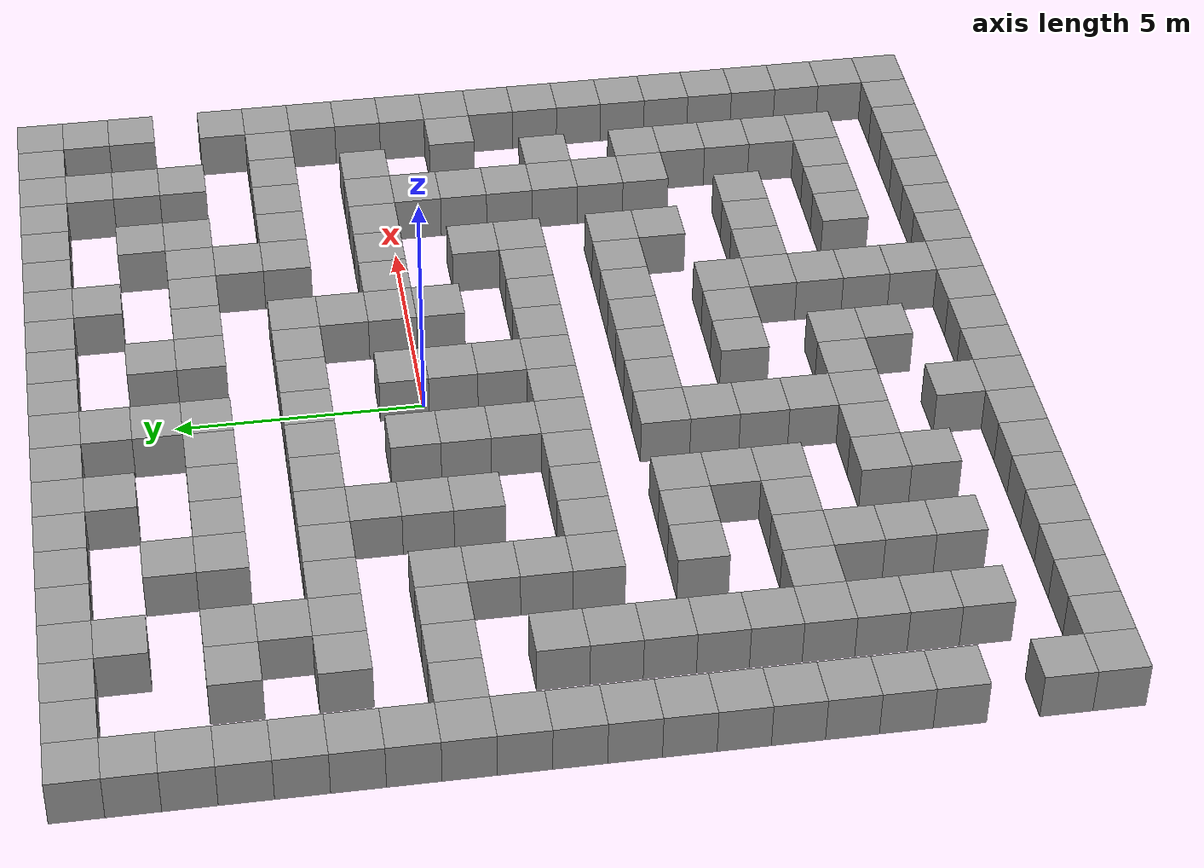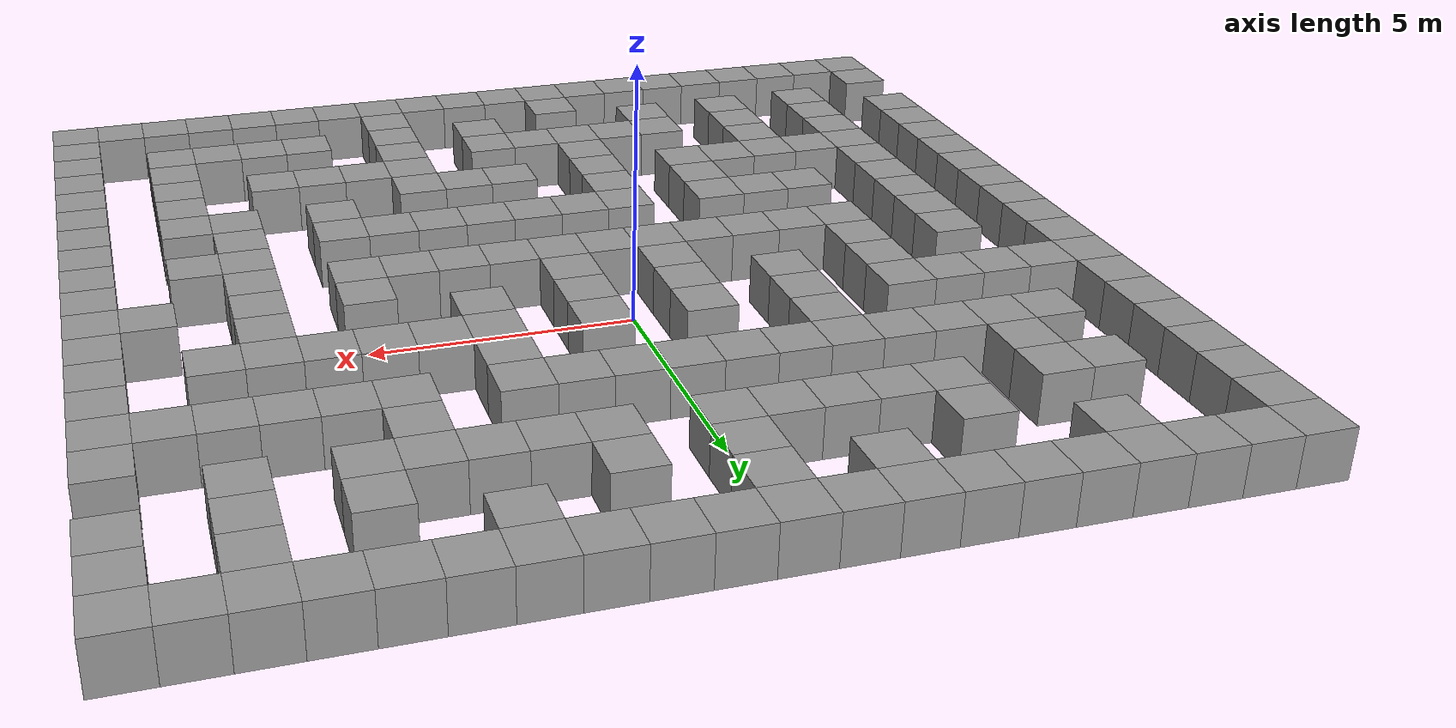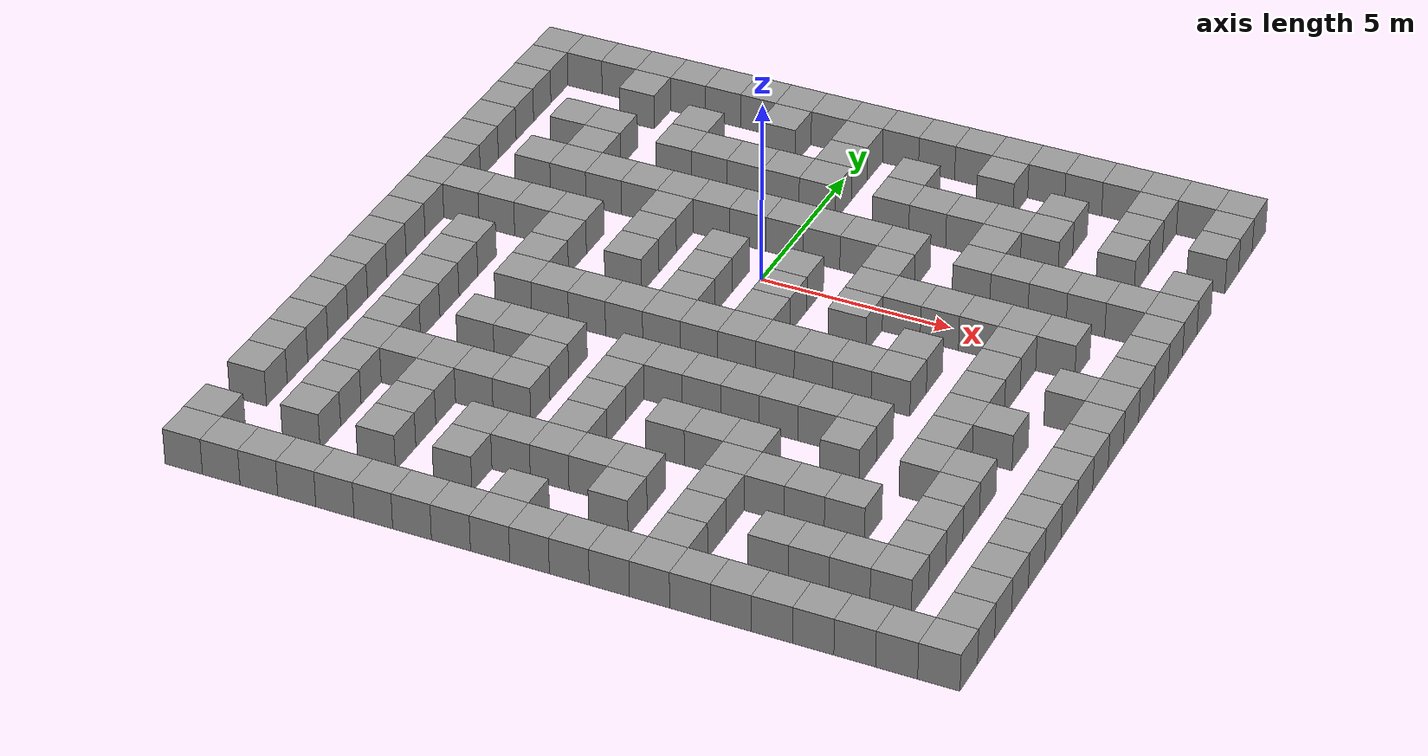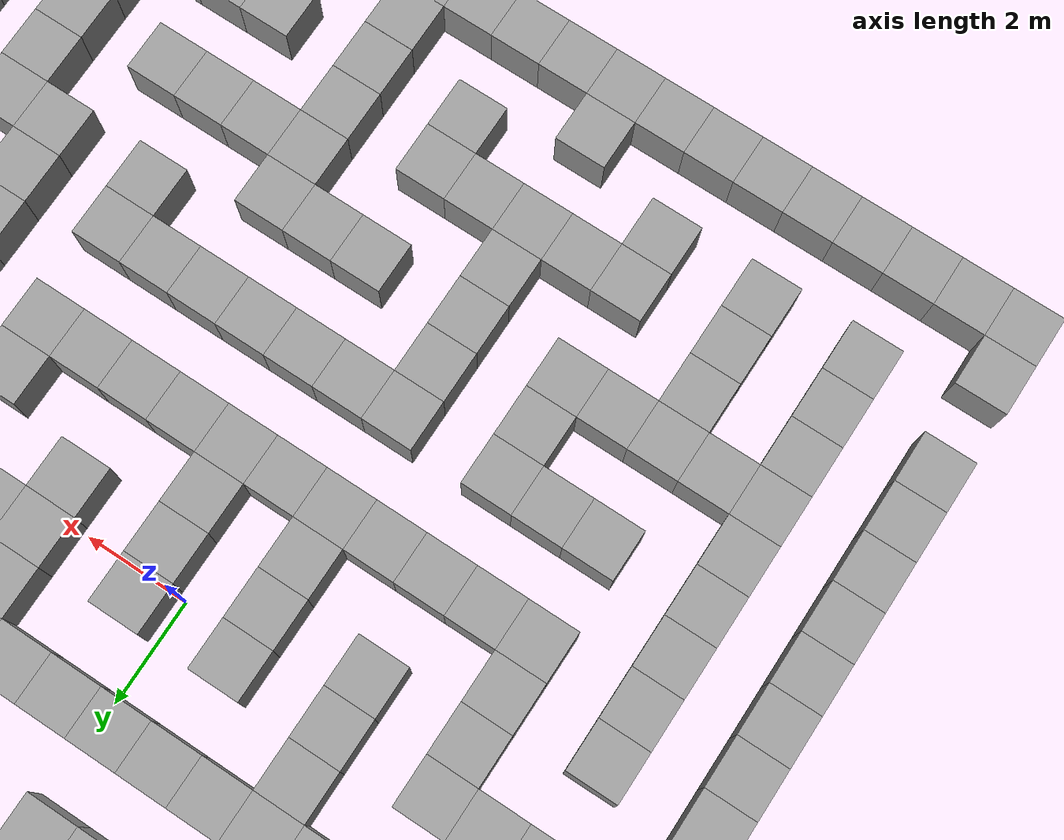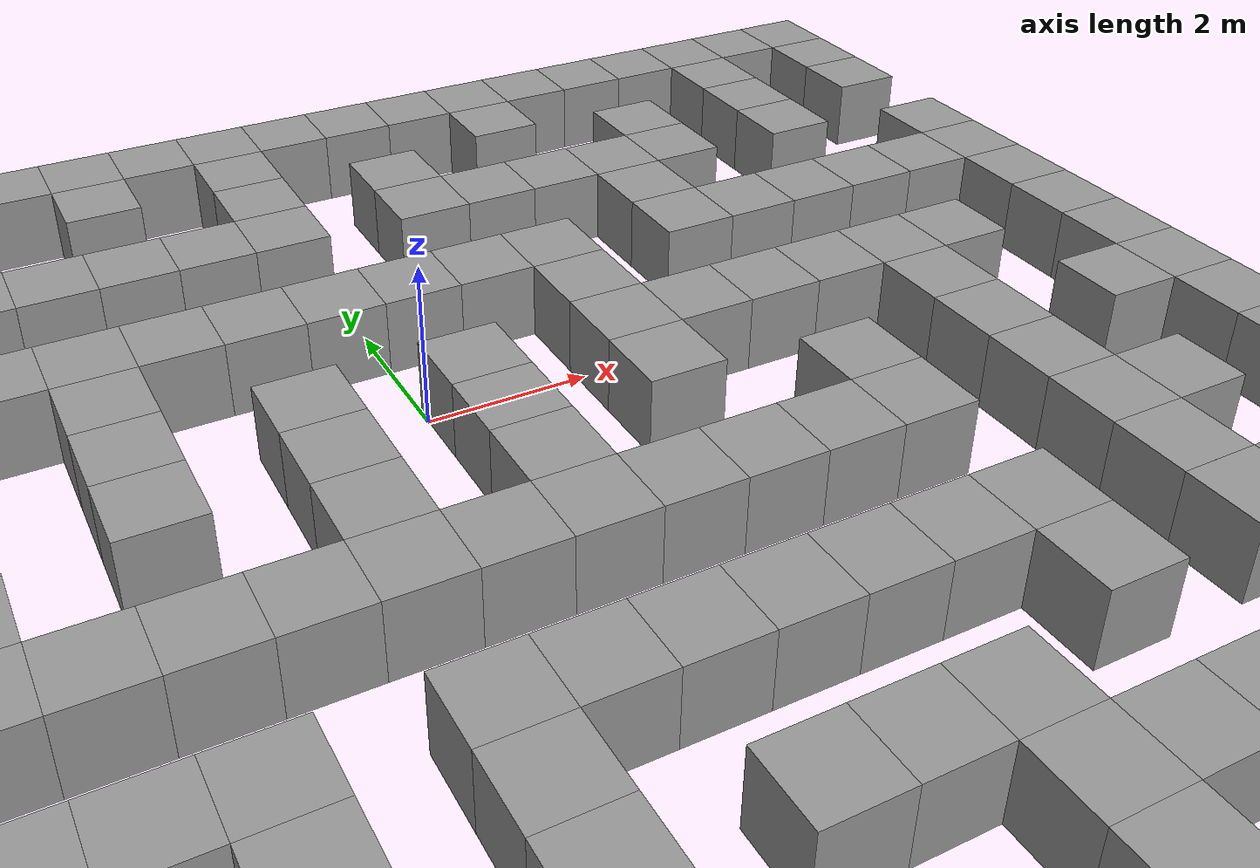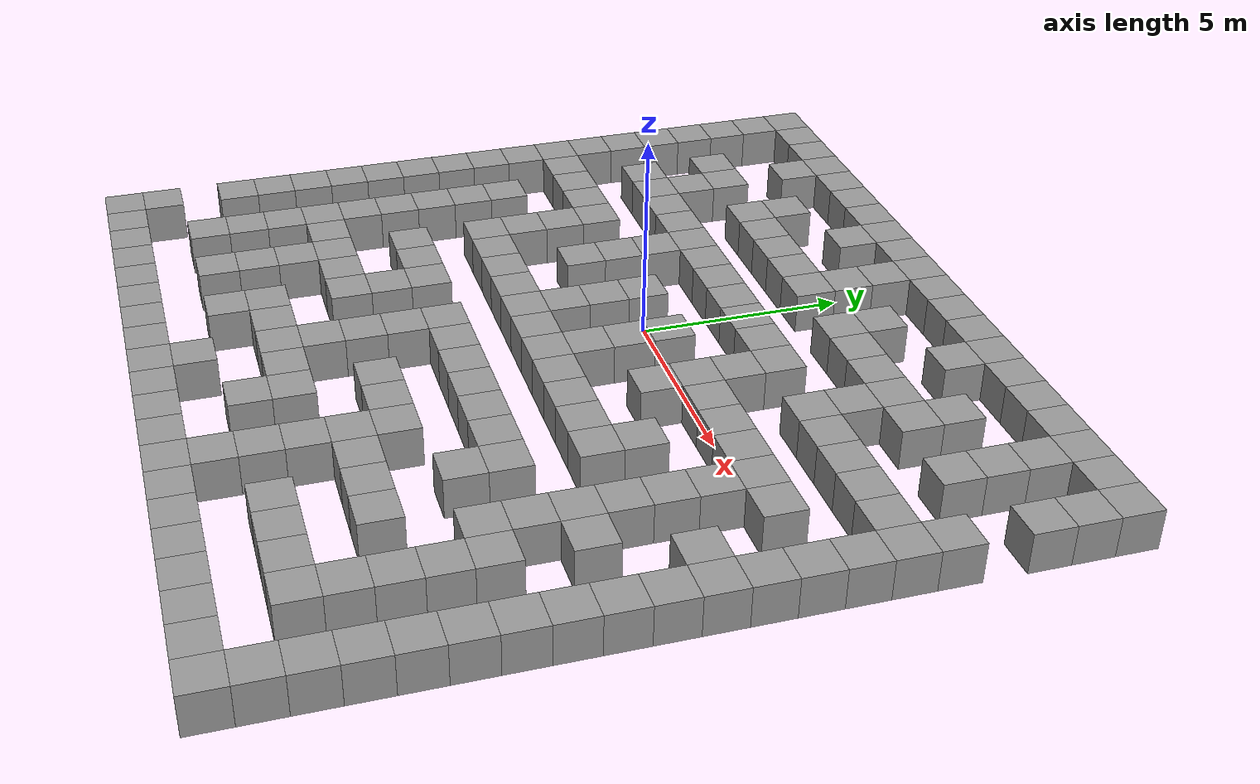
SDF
<?xml version='1.0'?>
<sdf version='1.7'>
  <model name='maze'>
    <link name='link_1'>
      <inertial>
        <mass>1</mass>
        <inertia>
          <ixx>0.166667</ixx>
          <ixy>0</ixy>
          <ixz>0</ixz>
          <iyy>0.166667</iyy>
          <iyz>0</iyz>
          <izz>0.166667</izz>
        </inertia>
        <pose>0 0 0 0 -0 0</pose>
      </inertial>
      <pose>9.75382 7.37465 0 0 -0 0</pose>
      <gravity>1</gravity>
      <self_collide>0</self_collide>
      <kinematic>0</kinematic>
      <enable_wind>0</enable_wind>
      <visual name='visual'>
        <pose>0 0 0 0 -0 0</pose>
        <geometry>
          <box>
            <size>1 1 1</size>
          </box>
        </geometry>
        <material>
          <lighting>1</lighting>
          <script>
            <uri>file://media/materials/scripts/gazebo.material</uri>
            <name>Gazebo/Grey</name>
          </script>
          <shader type='pixel'>
            <normal_map>__default__</normal_map>
          </shader>
          <ambient>0.3 0.3 0.3 1</ambient>
          <diffuse>0.7 0.7 0.7 1</diffuse>
          <specular>0.01 0.01 0.01 1</specular>
          <emissive>0 0 0 1</emissive>
        </material>
        <transparency>0</transparency>
        <cast_shadows>1</cast_shadows>
      </visual>
      <collision name='collision'>
        <laser_retro>0</laser_retro>
        <max_contacts>10</max_contacts>
        <pose>0 0 0 0 -0 0</pose>
        <geometry>
          <box>
            <size>1 1 1</size>
          </box>
        </geometry>
        <surface>
          <friction>
            <ode>
              <mu>1</mu>
              <mu2>1</mu2>
              <fdir1>0 0 0</fdir1>
              <slip1>0</slip1>
              <slip2>0</slip2>
            </ode>
            <torsional>
              <coefficient>1</coefficient>
              <patch_radius>0</patch_radius>
              <surface_radius>0</surface_radius>
              <use_patch_radius>1</use_patch_radius>
              <ode>
                <slip>0</slip>
              </ode>
            </torsional>
          </friction>
          <bounce>
            <restitution_coefficient>0</restitution_coefficient>
            <threshold>1e+06</threshold>
          </bounce>
          <contact>
            <collide_without_contact>0</collide_without_contact>
            <collide_without_contact_bitmask>1</collide_without_contact_bitmask>
            <collide_bitmask>1</collide_bitmask>
            <ode>
              <soft_cfm>0</soft_cfm>
              <soft_erp>0.2</soft_erp>
              <kp>1e+13</kp>
              <kd>1</kd>
              <max_vel>0.01</max_vel>
              <min_depth>0</min_depth>
            </ode>
            <bullet>
              <split_impulse>1</split_impulse>
              <split_impulse_penetration_threshold>-0.01</split_impulse_penetration_threshold>
              <soft_cfm>0</soft_cfm>
              <soft_erp>0.2</soft_erp>
              <kp>1e+13</kp>
              <kd>1</kd>
            </bullet>
          </contact>
        </surface>
      </collision>
    </link>
    <link name='link_1_clone'>
      <inertial>
        <mass>1</mass>
        <inertia>
          <ixx>0.166667</ixx>
          <ixy>0</ixy>
          <ixz>0</ixz>
          <iyy>0.166667</iyy>
          <iyz>0</iyz>
          <izz>0.166667</izz>
        </inertia>
        <pose>0 0 0 0 -0 0</pose>
      </inertial>
      <pose>8.75382 7.37465 0 0 -0 0</pose>
      <gravity>1</gravity>
      <self_collide>0</self_collide>
      <kinematic>0</kinematic>
      <enable_wind>0</enable_wind>
      <visual name='visual'>
        <pose>0 0 0 0 -0 0</pose>
        <geometry>
          <box>
            <size>1 1 1</size>
          </box>
        </geometry>
        <material>
          <lighting>1</lighting>
          <script>
            <uri>file://media/materials/scripts/gazebo.material</uri>
            <name>Gazebo/Grey</name>
          </script>
          <shader type='pixel'>
            <normal_map>__default__</normal_map>
          </shader>
          <ambient>0.3 0.3 0.3 1</ambient>
          <diffuse>0.7 0.7 0.7 1</diffuse>
          <specular>0.01 0.01 0.01 1</specular>
          <emissive>0 0 0 1</emissive>
        </material>
        <transparency>0</transparency>
        <cast_shadows>1</cast_shadows>
      </visual>
      <collision name='collision'>
        <laser_retro>0</laser_retro>
        <max_contacts>10</max_contacts>
        <pose>0 0 0 0 -0 0</pose>
        <geometry>
          <box>
            <size>1 1 1</size>
          </box>
        </geometry>
        <surface>
          <friction>
            <ode>
              <mu>1</mu>
              <mu2>1</mu2>
              <fdir1>0 0 0</fdir1>
              <slip1>0</slip1>
              <slip2>0</slip2>
            </ode>
            <torsional>
              <coefficient>1</coefficient>
              <patch_radius>0</patch_radius>
              <surface_radius>0</surface_radius>
              <use_patch_radius>1</use_patch_radius>
              <ode>
                <slip>0</slip>
              </ode>
            </torsional>
          </friction>
          <bounce>
            <restitution_coefficient>0</restitution_coefficient>
            <threshold>1e+06</threshold>
          </bounce>
          <contact>
            <collide_without_contact>0</collide_without_contact>
            <collide_without_contact_bitmask>1</collide_without_contact_bitmask>
            <collide_bitmask>1</collide_bitmask>
            <ode>
              <soft_cfm>0</soft_cfm>
              <soft_erp>0.2</soft_erp>
              <kp>1e+13</kp>
              <kd>1</kd>
              <max_vel>0.01</max_vel>
              <min_depth>0</min_depth>
            </ode>
            <bullet>
              <split_impulse>1</split_impulse>
              <split_impulse_penetration_threshold>-0.01</split_impulse_penetration_threshold>
              <soft_cfm>0</soft_cfm>
              <soft_erp>0.2</soft_erp>
              <kp>1e+13</kp>
              <kd>1</kd>
            </bullet>
          </contact>
        </surface>
      </collision>
    </link>
    <link name='link_1_clone_0'>
      <inertial>
        <mass>1</mass>
        <inertia>
          <ixx>0.166667</ixx>
          <ixy>0</ixy>
          <ixz>0</ixz>
          <iyy>0.166667</iyy>
          <iyz>0</iyz>
          <izz>0.166667</izz>
        </inertia>
        <pose>0 0 0 0 -0 0</pose>
      </inertial>
      <pose>7.75382 7.37465 0 0 -0 0</pose>
      <gravity>1</gravity>
      <self_collide>0</self_collide>
      <kinematic>0</kinematic>
      <enable_wind>0</enable_wind>
      <visual name='visual'>
        <pose>0 0 0 0 -0 0</pose>
        <geometry>
          <box>
            <size>1 1 1</size>
          </box>
        </geometry>
        <material>
          <lighting>1</lighting>
          <script>
            <uri>file://media/materials/scripts/gazebo.material</uri>
            <name>Gazebo/Grey</name>
          </script>
          <shader type='pixel'>
            <normal_map>__default__</normal_map>
          </shader>
          <ambient>0.3 0.3 0.3 1</ambient>
          <diffuse>0.7 0.7 0.7 1</diffuse>
          <specular>0.01 0.01 0.01 1</specular>
          <emissive>0 0 0 1</emissive>
        </material>
        <transparency>0</transparency>
        <cast_shadows>1</cast_shadows>
      </visual>
      <collision name='collision'>
        <laser_retro>0</laser_retro>
        <max_contacts>10</max_contacts>
        <pose>0 0 0 0 -0 0</pose>
        <geometry>
          <box>
            <size>1 1 1</size>
          </box>
        </geometry>
        <surface>
          <friction>
            <ode>
              <mu>1</mu>
              <mu2>1</mu2>
              <fdir1>0 0 0</fdir1>
              <slip1>0</slip1>
              <slip2>0</slip2>
            </ode>
            <torsional>
              <coefficient>1</coefficient>
              <patch_radius>0</patch_radius>
              <surface_radius>0</surface_radius>
              <use_patch_radius>1</use_patch_radius>
              <ode>
                <slip>0</slip>
              </ode>
            </torsional>
          </friction>
          <bounce>
            <restitution_coefficient>0</restitution_coefficient>
            <threshold>1e+06</threshold>
          </bounce>
          <contact>
            <collide_without_contact>0</collide_without_contact>
            <collide_without_contact_bitmask>1</collide_without_contact_bitmask>
            <collide_bitmask>1</collide_bitmask>
            <ode>
              <soft_cfm>0</soft_cfm>
              <soft_erp>0.2</soft_erp>
              <kp>1e+13</kp>
              <kd>1</kd>
              <max_vel>0.01</max_vel>
              <min_depth>0</min_depth>
            </ode>
            <bullet>
              <split_impulse>1</split_impulse>
              <split_impulse_penetration_threshold>-0.01</split_impulse_penetration_threshold>
              <soft_cfm>0</soft_cfm>
              <soft_erp>0.2</soft_erp>
              <kp>1e+13</kp>
              <kd>1</kd>
            </bullet>
          </contact>
        </surface>
      </collision>
    </link>
    <link name='link_1_clone_1'>
      <inertial>
        <mass>1</mass>
        <inertia>
          <ixx>0.166667</ixx>
          <ixy>0</ixy>
          <ixz>0</ixz>
          <iyy>0.166667</iyy>
          <iyz>0</iyz>
          <izz>0.166667</izz>
        </inertia>
        <pose>0 0 0 0 -0 0</pose>
      </inertial>
      <pose>6.75382 7.37465 0 0 -0 0</pose>
      <gravity>1</gravity>
      <self_collide>0</self_collide>
      <kinematic>0</kinematic>
      <enable_wind>0</enable_wind>
      <visual name='visual'>
        <pose>0 0 0 0 -0 0</pose>
        <geometry>
          <box>
            <size>1 1 1</size>
          </box>
        </geometry>
        <material>
          <lighting>1</lighting>
          <script>
            <uri>file://media/materials/scripts/gazebo.material</uri>
            <name>Gazebo/Grey</name>
          </script>
          <shader type='pixel'>
            <normal_map>__default__</normal_map>
          </shader>
          <ambient>0.3 0.3 0.3 1</ambient>
          <diffuse>0.7 0.7 0.7 1</diffuse>
          <specular>0.01 0.01 0.01 1</specular>
          <emissive>0 0 0 1</emissive>
        </material>
        <transparency>0</transparency>
        <cast_shadows>1</cast_shadows>
      </visual>
      <collision name='collision'>
        <laser_retro>0</laser_retro>
        <max_contacts>10</max_contacts>
        <pose>0 0 0 0 -0 0</pose>
        <geometry>
          <box>
            <size>1 1 1</size>
          </box>
        </geometry>
        <surface>
          <friction>
            <ode>
              <mu>1</mu>
              <mu2>1</mu2>
              <fdir1>0 0 0</fdir1>
              <slip1>0</slip1>
              <slip2>0</slip2>
            </ode>
            <torsional>
              <coefficient>1</coefficient>
              <patch_radius>0</patch_radius>
              <surface_radius>0</surface_radius>
              <use_patch_radius>1</use_patch_radius>
              <ode>
                <slip>0</slip>
              </ode>
            </torsional>
          </friction>
          <bounce>
            <restitution_coefficient>0</restitution_coefficient>
            <threshold>1e+06</threshold>
          </bounce>
          <contact>
            <collide_without_contact>0</collide_without_contact>
            <collide_without_contact_bitmask>1</collide_without_contact_bitmask>
            <collide_bitmask>1</collide_bitmask>
            <ode>
              <soft_cfm>0</soft_cfm>
              <soft_erp>0.2</soft_erp>
              <kp>1e+13</kp>
              <kd>1</kd>
              <max_vel>0.01</max_vel>
              <min_depth>0</min_depth>
            </ode>
            <bullet>
              <split_impulse>1</split_impulse>
              <split_impulse_penetration_threshold>-0.01</split_impulse_penetration_threshold>
              <soft_cfm>0</soft_cfm>
              <soft_erp>0.2</soft_erp>
              <kp>1e+13</kp>
              <kd>1</kd>
            </bullet>
          </contact>
        </surface>
      </collision>
    </link>
    <link name='link_1_clone_10'>
      <inertial>
        <mass>1</mass>
        <inertia>
          <ixx>0.166667</ixx>
          <ixy>0</ixy>
          <ixz>0</ixz>
          <iyy>0.166667</iyy>
          <iyz>0</iyz>
          <izz>0.166667</izz>
        </inertia>
        <pose>0 0 0 0 -0 0</pose>
      </inertial>
      <pose>-2.24618 7.37465 0 0 -0 0</pose>
      <gravity>1</gravity>
      <self_collide>0</self_collide>
      <kinematic>0</kinematic>
      <enable_wind>0</enable_wind>
      <visual name='visual'>
        <pose>0 0 0 0 -0 0</pose>
        <geometry>
          <box>
            <size>1 1 1</size>
          </box>
        </geometry>
        <material>
          <lighting>1</lighting>
          <script>
            <uri>file://media/materials/scripts/gazebo.material</uri>
            <name>Gazebo/Grey</name>
          </script>
          <shader type='pixel'>
            <normal_map>__default__</normal_map>
          </shader>
          <ambient>0.3 0.3 0.3 1</ambient>
          <diffuse>0.7 0.7 0.7 1</diffuse>
          <specular>0.01 0.01 0.01 1</specular>
          <emissive>0 0 0 1</emissive>
        </material>
        <transparency>0</transparency>
        <cast_shadows>1</cast_shadows>
      </visual>
      <collision name='collision'>
        <laser_retro>0</laser_retro>
        <max_contacts>10</max_contacts>
        <pose>0 0 0 0 -0 0</pose>
        <geometry>
          <box>
            <size>1 1 1</size>
          </box>
        </geometry>
        <surface>
          <friction>
            <ode>
              <mu>1</mu>
              <mu2>1</mu2>
              <fdir1>0 0 0</fdir1>
              <slip1>0</slip1>
              <slip2>0</slip2>
            </ode>
            <torsional>
              <coefficient>1</coefficient>
              <patch_radius>0</patch_radius>
              <surface_radius>0</surface_radius>
              <use_patch_radius>1</use_patch_radius>
              <ode>
                <slip>0</slip>
              </ode>
            </torsional>
          </friction>
          <bounce>
            <restitution_coefficient>0</restitution_coefficient>
            <threshold>1e+06</threshold>
          </bounce>
          <contact>
            <collide_without_contact>0</collide_without_contact>
            <collide_without_contact_bitmask>1</collide_without_contact_bitmask>
            <collide_bitmask>1</collide_bitmask>
            <ode>
              <soft_cfm>0</soft_cfm>
              <soft_erp>0.2</soft_erp>
              <kp>1e+13</kp>
              <kd>1</kd>
              <max_vel>0.01</max_vel>
              <min_depth>0</min_depth>
            </ode>
            <bullet>
              <split_impulse>1</split_impulse>
              <split_impulse_penetration_threshold>-0.01</split_impulse_penetration_threshold>
              <soft_cfm>0</soft_cfm>
              <soft_erp>0.2</soft_erp>
              <kp>1e+13</kp>
              <kd>1</kd>
            </bullet>
          </contact>
        </surface>
      </collision>
    </link>
    <link name='link_1_clone_100'>
      <inertial>
        <mass>1</mass>
        <inertia>
          <ixx>0.166667</ixx>
          <ixy>0</ixy>
          <ixz>0</ixz>
          <iyy>0.166667</iyy>
          <iyz>0</iyz>
          <izz>0.166667</izz>
        </inertia>
        <pose>0 0 0 0 -0 0</pose>
      </inertial>
      <pose>-6.24618 4.37465 -0 0 -0 0</pose>
      <gravity>1</gravity>
      <self_collide>0</self_collide>
      <kinematic>0</kinematic>
      <enable_wind>0</enable_wind>
      <visual name='visual'>
        <pose>0 0 0 0 -0 0</pose>
        <geometry>
          <box>
            <size>1 1 1</size>
          </box>
        </geometry>
        <material>
          <lighting>1</lighting>
          <script>
            <uri>file://media/materials/scripts/gazebo.material</uri>
            <name>Gazebo/Grey</name>
          </script>
          <shader type='pixel'>
            <normal_map>__default__</normal_map>
          </shader>
          <ambient>0.3 0.3 0.3 1</ambient>
          <diffuse>0.7 0.7 0.7 1</diffuse>
          <specular>0.01 0.01 0.01 1</specular>
          <emissive>0 0 0 1</emissive>
        </material>
        <transparency>0</transparency>
        <cast_shadows>1</cast_shadows>
      </visual>
      <collision name='collision'>
        <laser_retro>0</laser_retro>
        <max_contacts>10</max_contacts>
        <pose>0 0 0 0 -0 0</pose>
        <geometry>
          <box>
            <size>1 1 1</size>
          </box>
        </geometry>
        <surface>
          <friction>
            <ode>
              <mu>1</mu>
              <mu2>1</mu2>
              <fdir1>0 0 0</fdir1>
              <slip1>0</slip1>
              <slip2>0</slip2>
            </ode>
            <torsional>
              <coefficient>1</coefficient>
              <patch_radius>0</patch_radius>
              <surface_radius>0</surface_radius>
              <use_patch_radius>1</use_patch_radius>
              <ode>
                <slip>0</slip>
              </ode>
            </torsional>
          </friction>
          <bounce>
            <restitution_coefficient>0</restitution_coefficient>
            <threshold>1e+06</threshold>
          </bounce>
          <contact>
            <collide_without_contact>0</collide_without_contact>
            <collide_without_contact_bitmask>1</collide_without_contact_bitmask>
            <collide_bitmask>1</collide_bitmask>
            <ode>
              <soft_cfm>0</soft_cfm>
              <soft_erp>0.2</soft_erp>
              <kp>1e+13</kp>
              <kd>1</kd>
              <max_vel>0.01</max_vel>
              <min_depth>0</min_depth>
            </ode>
            <bullet>
              <split_impulse>1</split_impulse>
              <split_impulse_penetration_threshold>-0.01</split_impulse_penetration_threshold>
              <soft_cfm>0</soft_cfm>
              <soft_erp>0.2</soft_erp>
              <kp>1e+13</kp>
              <kd>1</kd>
            </bullet>
          </contact>
        </surface>
      </collision>
    </link>
    <link name='link_1_clone_101'>
      <inertial>
        <mass>1</mass>
        <inertia>
          <ixx>0.166667</ixx>
          <ixy>0</ixy>
          <ixz>0</ixz>
          <iyy>0.166667</iyy>
          <iyz>0</iyz>
          <izz>0.166667</izz>
        </inertia>
        <pose>0 0 0 0 -0 0</pose>
      </inertial>
      <pose>-6.24618 3.37465 -0 0 -0 0</pose>
      <gravity>1</gravity>
      <self_collide>0</self_collide>
      <kinematic>0</kinematic>
      <enable_wind>0</enable_wind>
      <visual name='visual'>
        <pose>0 0 0 0 -0 0</pose>
        <geometry>
          <box>
            <size>1 1 1</size>
          </box>
        </geometry>
        <material>
          <lighting>1</lighting>
          <script>
            <uri>file://media/materials/scripts/gazebo.material</uri>
            <name>Gazebo/Grey</name>
          </script>
          <shader type='pixel'>
            <normal_map>__default__</normal_map>
          </shader>
          <ambient>0.3 0.3 0.3 1</ambient>
          <diffuse>0.7 0.7 0.7 1</diffuse>
          <specular>0.01 0.01 0.01 1</specular>
          <emissive>0 0 0 1</emissive>
        </material>
        <transparency>0</transparency>
        <cast_shadows>1</cast_shadows>
      </visual>
      <collision name='collision'>
        <laser_retro>0</laser_retro>
        <max_contacts>10</max_contacts>
        <pose>0 0 0 0 -0 0</pose>
        <geometry>
          <box>
            <size>1 1 1</size>
          </box>
        </geometry>
        <surface>
          <friction>
            <ode>
              <mu>1</mu>
              <mu2>1</mu2>
              <fdir1>0 0 0</fdir1>
              <slip1>0</slip1>
              <slip2>0</slip2>
            </ode>
            <torsional>
              <coefficient>1</coefficient>
              <patch_radius>0</patch_radius>
              <surface_radius>0</surface_radius>
              <use_patch_radius>1</use_patch_radius>
              <ode>
                <slip>0</slip>
              </ode>
            </torsional>
          </friction>
          <bounce>
            <restitution_coefficient>0</restitution_coefficient>
            <threshold>1e+06</threshold>
          </bounce>
          <contact>
            <collide_without_contact>0</collide_without_contact>
            <collide_without_contact_bitmask>1</collide_without_contact_bitmask>
            <collide_bitmask>1</collide_bitmask>
            <ode>
              <soft_cfm>0</soft_cfm>
              <soft_erp>0.2</soft_erp>
              <kp>1e+13</kp>
              <kd>1</kd>
              <max_vel>0.01</max_vel>
              <min_depth>0</min_depth>
            </ode>
            <bullet>
              <split_impulse>1</split_impulse>
              <split_impulse_penetration_threshold>-0.01</split_impulse_penetration_threshold>
              <soft_cfm>0</soft_cfm>
              <soft_erp>0.2</soft_erp>
              <kp>1e+13</kp>
              <kd>1</kd>
            </bullet>
          </contact>
        </surface>
      </collision>
    </link>
    <link name='link_1_clone_102'>
      <inertial>
        <mass>1</mass>
        <inertia>
          <ixx>0.166667</ixx>
          <ixy>0</ixy>
          <ixz>0</ixz>
          <iyy>0.166667</iyy>
          <iyz>0</iyz>
          <izz>0.166667</izz>
        </inertia>
        <pose>0 0 0 0 -0 0</pose>
      </inertial>
      <pose>-2.24618 2.37465 -0 0 -0 0</pose>
      <gravity>1</gravity>
      <self_collide>0</self_collide>
      <kinematic>0</kinematic>
      <enable_wind>0</enable_wind>
      <visual name='visual'>
        <pose>0 0 0 0 -0 0</pose>
        <geometry>
          <box>
            <size>1 1 1</size>
          </box>
        </geometry>
        <material>
          <lighting>1</lighting>
          <script>
            <uri>file://media/materials/scripts/gazebo.material</uri>
            <name>Gazebo/Grey</name>
          </script>
          <shader type='pixel'>
            <normal_map>__default__</normal_map>
          </shader>
          <ambient>0.3 0.3 0.3 1</ambient>
          <diffuse>0.7 0.7 0.7 1</diffuse>
          <specular>0.01 0.01 0.01 1</specular>
          <emissive>0 0 0 1</emissive>
        </material>
        <transparency>0</transparency>
        <cast_shadows>1</cast_shadows>
      </visual>
      <collision name='collision'>
        <laser_retro>0</laser_retro>
        <max_contacts>10</max_contacts>
        <pose>0 0 0 0 -0 0</pose>
        <geometry>
          <box>
            <size>1 1 1</size>
          </box>
        </geometry>
        <surface>
          <friction>
            <ode>
              <mu>1</mu>
              <mu2>1</mu2>
              <fdir1>0 0 0</fdir1>
              <slip1>0</slip1>
              <slip2>0</slip2>
            </ode>
            <torsional>
              <coefficient>1</coefficient>
              <patch_radius>0</patch_radius>
              <surface_radius>0</surface_radius>
              <use_patch_radius>1</use_patch_radius>
              <ode>
                <slip>0</slip>
              </ode>
            </torsional>
          </friction>
          <bounce>
            <restitution_coefficient>0</restitution_coefficient>
            <threshold>1e+06</threshold>
          </bounce>
          <contact>
            <collide_without_contact>0</collide_without_contact>
            <collide_without_contact_bitmask>1</collide_without_contact_bitmask>
            <collide_bitmask>1</collide_bitmask>
            <ode>
              <soft_cfm>0</soft_cfm>
              <soft_erp>0.2</soft_erp>
              <kp>1e+13</kp>
              <kd>1</kd>
              <max_vel>0.01</max_vel>
              <min_depth>0</min_depth>
            </ode>
            <bullet>
              <split_impulse>1</split_impulse>
              <split_impulse_penetration_threshold>-0.01</split_impulse_penetration_threshold>
              <soft_cfm>0</soft_cfm>
              <soft_erp>0.2</soft_erp>
              <kp>1e+13</kp>
              <kd>1</kd>
            </bullet>
          </contact>
        </surface>
      </collision>
    </link>
    <link name='link_1_clone_103'>
      <inertial>
        <mass>1</mass>
        <inertia>
          <ixx>0.166667</ixx>
          <ixy>0</ixy>
          <ixz>0</ixz>
          <iyy>0.166667</iyy>
          <iyz>0</iyz>
          <izz>0.166667</izz>
        </inertia>
        <pose>0 0 0 0 -0 0</pose>
      </inertial>
      <pose>-1.24618 2.37465 -0 0 -0 0</pose>
      <gravity>1</gravity>
      <self_collide>0</self_collide>
      <kinematic>0</kinematic>
      <enable_wind>0</enable_wind>
      <visual name='visual'>
        <pose>0 0 0 0 -0 0</pose>
        <geometry>
          <box>
            <size>1 1 1</size>
          </box>
        </geometry>
        <material>
          <lighting>1</lighting>
          <script>
            <uri>file://media/materials/scripts/gazebo.material</uri>
            <name>Gazebo/Grey</name>
          </script>
          <shader type='pixel'>
            <normal_map>__default__</normal_map>
          </shader>
          <ambient>0.3 0.3 0.3 1</ambient>
          <diffuse>0.7 0.7 0.7 1</diffuse>
          <specular>0.01 0.01 0.01 1</specular>
          <emissive>0 0 0 1</emissive>
        </material>
        <transparency>0</transparency>
        <cast_shadows>1</cast_shadows>
      </visual>
      <collision name='collision'>
        <laser_retro>0</laser_retro>
        <max_contacts>10</max_contacts>
        <pose>0 0 0 0 -0 0</pose>
        <geometry>
          <box>
            <size>1 1 1</size>
          </box>
        </geometry>
        <surface>
          <friction>
            <ode>
              <mu>1</mu>
              <mu2>1</mu2>
              <fdir1>0 0 0</fdir1>
              <slip1>0</slip1>
              <slip2>0</slip2>
            </ode>
            <torsional>
              <coefficient>1</coefficient>
              <patch_radius>0</patch_radius>
              <surface_radius>0</surface_radius>
              <use_patch_radius>1</use_patch_radius>
              <ode>
                <slip>0</slip>
              </ode>
            </torsional>
          </friction>
          <bounce>
            <restitution_coefficient>0</restitution_coefficient>
            <threshold>1e+06</threshold>
          </bounce>
          <contact>
            <collide_without_contact>0</collide_without_contact>
            <collide_without_contact_bitmask>1</collide_without_contact_bitmask>
            <collide_bitmask>1</collide_bitmask>
            <ode>
              <soft_cfm>0</soft_cfm>
              <soft_erp>0.2</soft_erp>
              <kp>1e+13</kp>
              <kd>1</kd>
              <max_vel>0.01</max_vel>
              <min_depth>0</min_depth>
            </ode>
            <bullet>
              <split_impulse>1</split_impulse>
              <split_impulse_penetration_threshold>-0.01</split_impulse_penetration_threshold>
              <soft_cfm>0</soft_cfm>
              <soft_erp>0.2</soft_erp>
              <kp>1e+13</kp>
              <kd>1</kd>
            </bullet>
          </contact>
        </surface>
      </collision>
    </link>
    <link name='link_1_clone_104'>
      <inertial>
        <mass>1</mass>
        <inertia>
          <ixx>0.166667</ixx>
          <ixy>0</ixy>
          <ixz>0</ixz>
          <iyy>0.166667</iyy>
          <iyz>0</iyz>
          <izz>0.166667</izz>
        </inertia>
        <pose>0 0 0 0 -0 0</pose>
      </inertial>
      <pose>-8.24618 0.374651 -0 0 -0 0</pose>
      <gravity>1</gravity>
      <self_collide>0</self_collide>
      <kinematic>0</kinematic>
      <enable_wind>0</enable_wind>
      <visual name='visual'>
        <pose>0 0 0 0 -0 0</pose>
        <geometry>
          <box>
            <size>1 1 1</size>
          </box>
        </geometry>
        <material>
          <lighting>1</lighting>
          <script>
            <uri>file://media/materials/scripts/gazebo.material</uri>
            <name>Gazebo/Grey</name>
          </script>
          <shader type='pixel'>
            <normal_map>__default__</normal_map>
          </shader>
          <ambient>0.3 0.3 0.3 1</ambient>
          <diffuse>0.7 0.7 0.7 1</diffuse>
          <specular>0.01 0.01 0.01 1</specular>
          <emissive>0 0 0 1</emissive>
        </material>
        <transparency>0</transparency>
        <cast_shadows>1</cast_shadows>
      </visual>
      <collision name='collision'>
        <laser_retro>0</laser_retro>
        <max_contacts>10</max_contacts>
        <pose>0 0 0 0 -0 0</pose>
        <geometry>
          <box>
            <size>1 1 1</size>
          </box>
        </geometry>
        <surface>
          <friction>
            <ode>
              <mu>1</mu>
              <mu2>1</mu2>
              <fdir1>0 0 0</fdir1>
              <slip1>0</slip1>
              <slip2>0</slip2>
            </ode>
            <torsional>
              <coefficient>1</coefficient>
              <patch_radius>0</patch_radius>
              <surface_radius>0</surface_radius>
              <use_patch_radius>1</use_patch_radius>
              <ode>
                <slip>0</slip>
              </ode>
            </torsional>
          </friction>
          <bounce>
            <restitution_coefficient>0</restitution_coefficient>
            <threshold>1e+06</threshold>
          </bounce>
          <contact>
            <collide_without_contact>0</collide_without_contact>
            <collide_without_contact_bitmask>1</collide_without_contact_bitmask>
            <collide_bitmask>1</collide_bitmask>
            <ode>
              <soft_cfm>0</soft_cfm>
              <soft_erp>0.2</soft_erp>
              <kp>1e+13</kp>
              <kd>1</kd>
              <max_vel>0.01</max_vel>
              <min_depth>0</min_depth>
            </ode>
            <bullet>
              <split_impulse>1</split_impulse>
              <split_impulse_penetration_threshold>-0.01</split_impulse_penetration_threshold>
              <soft_cfm>0</soft_cfm>
              <soft_erp>0.2</soft_erp>
              <kp>1e+13</kp>
              <kd>1</kd>
            </bullet>
          </contact>
        </surface>
      </collision>
    </link>
    <link name='link_1_clone_105'>
      <inertial>
        <mass>1</mass>
        <inertia>
          <ixx>0.166667</ixx>
          <ixy>0</ixy>
          <ixz>0</ixz>
          <iyy>0.166667</iyy>
          <iyz>0</iyz>
          <izz>0.166667</izz>
        </inertia>
        <pose>0 0 0 0 -0 0</pose>
      </inertial>
      <pose>-7.24618 2.37465 -0 0 -0 0</pose>
      <gravity>1</gravity>
      <self_collide>0</self_collide>
      <kinematic>0</kinematic>
      <enable_wind>0</enable_wind>
      <visual name='visual'>
        <pose>0 0 0 0 -0 0</pose>
        <geometry>
          <box>
            <size>1 1 1</size>
          </box>
        </geometry>
        <material>
          <lighting>1</lighting>
          <script>
            <uri>file://media/materials/scripts/gazebo.material</uri>
            <name>Gazebo/Grey</name>
          </script>
          <shader type='pixel'>
            <normal_map>__default__</normal_map>
          </shader>
          <ambient>0.3 0.3 0.3 1</ambient>
          <diffuse>0.7 0.7 0.7 1</diffuse>
          <specular>0.01 0.01 0.01 1</specular>
          <emissive>0 0 0 1</emissive>
        </material>
        <transparency>0</transparency>
        <cast_shadows>1</cast_shadows>
      </visual>
      <collision name='collision'>
        <laser_retro>0</laser_retro>
        <max_contacts>10</max_contacts>
        <pose>0 0 0 0 -0 0</pose>
        <geometry>
          <box>
            <size>1 1 1</size>
          </box>
        </geometry>
        <surface>
          <friction>
            <ode>
              <mu>1</mu>
              <mu2>1</mu2>
              <fdir1>0 0 0</fdir1>
              <slip1>0</slip1>
              <slip2>0</slip2>
            </ode>
            <torsional>
              <coefficient>1</coefficient>
              <patch_radius>0</patch_radius>
              <surface_radius>0</surface_radius>
              <use_patch_radius>1</use_patch_radius>
              <ode>
                <slip>0</slip>
              </ode>
            </torsional>
          </friction>
          <bounce>
            <restitution_coefficient>0</restitution_coefficient>
            <threshold>1e+06</threshold>
          </bounce>
          <contact>
            <collide_without_contact>0</collide_without_contact>
            <collide_without_contact_bitmask>1</collide_without_contact_bitmask>
            <collide_bitmask>1</collide_bitmask>
            <ode>
              <soft_cfm>0</soft_cfm>
              <soft_erp>0.2</soft_erp>
              <kp>1e+13</kp>
              <kd>1</kd>
              <max_vel>0.01</max_vel>
              <min_depth>0</min_depth>
            </ode>
            <bullet>
              <split_impulse>1</split_impulse>
              <split_impulse_penetration_threshold>-0.01</split_impulse_penetration_threshold>
              <soft_cfm>0</soft_cfm>
              <soft_erp>0.2</soft_erp>
              <kp>1e+13</kp>
              <kd>1</kd>
            </bullet>
          </contact>
        </surface>
      </collision>
    </link>
    <link name='link_1_clone_106'>
      <inertial>
        <mass>1</mass>
        <inertia>
          <ixx>0.166667</ixx>
          <ixy>0</ixy>
          <ixz>0</ixz>
          <iyy>0.166667</iyy>
          <iyz>0</iyz>
          <izz>0.166667</izz>
        </inertia>
        <pose>0 0 0 0 -0 0</pose>
      </inertial>
      <pose>-6.24618 2.37465 -0 0 -0 0</pose>
      <gravity>1</gravity>
      <self_collide>0</self_collide>
      <kinematic>0</kinematic>
      <enable_wind>0</enable_wind>
      <visual name='visual'>
        <pose>0 0 0 0 -0 0</pose>
        <geometry>
          <box>
            <size>1 1 1</size>
          </box>
        </geometry>
        <material>
          <lighting>1</lighting>
          <script>
            <uri>file://media/materials/scripts/gazebo.material</uri>
            <name>Gazebo/Grey</name>
          </script>
          <shader type='pixel'>
            <normal_map>__default__</normal_map>
          </shader>
          <ambient>0.3 0.3 0.3 1</ambient>
          <diffuse>0.7 0.7 0.7 1</diffuse>
          <specular>0.01 0.01 0.01 1</specular>
          <emissive>0 0 0 1</emissive>
        </material>
        <transparency>0</transparency>
        <cast_shadows>1</cast_shadows>
      </visual>
      <collision name='collision'>
        <laser_retro>0</laser_retro>
        <max_contacts>10</max_contacts>
        <pose>0 0 0 0 -0 0</pose>
        <geometry>
          <box>
            <size>1 1 1</size>
          </box>
        </geometry>
        <surface>
          <friction>
            <ode>
              <mu>1</mu>
              <mu2>1</mu2>
              <fdir1>0 0 0</fdir1>
              <slip1>0</slip1>
              <slip2>0</slip2>
            </ode>
            <torsional>
              <coefficient>1</coefficient>
              <patch_radius>0</patch_radius>
              <surface_radius>0</surface_radius>
              <use_patch_radius>1</use_patch_radius>
              <ode>
                <slip>0</slip>
              </ode>
            </torsional>
          </friction>
          <bounce>
            <restitution_coefficient>0</restitution_coefficient>
            <threshold>1e+06</threshold>
          </bounce>
          <contact>
            <collide_without_contact>0</collide_without_contact>
            <collide_without_contact_bitmask>1</collide_without_contact_bitmask>
            <collide_bitmask>1</collide_bitmask>
            <ode>
              <soft_cfm>0</soft_cfm>
              <soft_erp>0.2</soft_erp>
              <kp>1e+13</kp>
              <kd>1</kd>
              <max_vel>0.01</max_vel>
              <min_depth>0</min_depth>
            </ode>
            <bullet>
              <split_impulse>1</split_impulse>
              <split_impulse_penetration_threshold>-0.01</split_impulse_penetration_threshold>
              <soft_cfm>0</soft_cfm>
              <soft_erp>0.2</soft_erp>
              <kp>1e+13</kp>
              <kd>1</kd>
            </bullet>
          </contact>
        </surface>
      </collision>
    </link>
    <link name='link_1_clone_107'>
      <inertial>
        <mass>1</mass>
        <inertia>
          <ixx>0.166667</ixx>
          <ixy>0</ixy>
          <ixz>0</ixz>
          <iyy>0.166667</iyy>
          <iyz>0</iyz>
          <izz>0.166667</izz>
        </inertia>
        <pose>0 0 0 0 -0 0</pose>
      </inertial>
      <pose>-5.24618 2.37465 -0 0 -0 0</pose>
      <gravity>1</gravity>
      <self_collide>0</self_collide>
      <kinematic>0</kinematic>
      <enable_wind>0</enable_wind>
      <visual name='visual'>
        <pose>0 0 0 0 -0 0</pose>
        <geometry>
          <box>
            <size>1 1 1</size>
          </box>
        </geometry>
        <material>
          <lighting>1</lighting>
          <script>
            <uri>file://media/materials/scripts/gazebo.material</uri>
            <name>Gazebo/Grey</name>
          </script>
          <shader type='pixel'>
            <normal_map>__default__</normal_map>
          </shader>
          <ambient>0.3 0.3 0.3 1</ambient>
          <diffuse>0.7 0.7 0.7 1</diffuse>
          <specular>0.01 0.01 0.01 1</specular>
          <emissive>0 0 0 1</emissive>
        </material>
        <transparency>0</transparency>
        <cast_shadows>1</cast_shadows>
      </visual>
      <collision name='collision'>
        <laser_retro>0</laser_retro>
        <max_contacts>10</max_contacts>
        <pose>0 0 0 0 -0 0</pose>
        <geometry>
          <box>
            <size>1 1 1</size>
          </box>
        </geometry>
        <surface>
          <friction>
            <ode>
              <mu>1</mu>
              <mu2>1</mu2>
              <fdir1>0 0 0</fdir1>
              <slip1>0</slip1>
              <slip2>0</slip2>
            </ode>
            <torsional>
              <coefficient>1</coefficient>
              <patch_radius>0</patch_radius>
              <surface_radius>0</surface_radius>
              <use_patch_radius>1</use_patch_radius>
              <ode>
                <slip>0</slip>
              </ode>
            </torsional>
          </friction>
          <bounce>
            <restitution_coefficient>0</restitution_coefficient>
            <threshold>1e+06</threshold>
          </bounce>
          <contact>
            <collide_without_contact>0</collide_without_contact>
            <collide_without_contact_bitmask>1</collide_without_contact_bitmask>
            <collide_bitmask>1</collide_bitmask>
            <ode>
              <soft_cfm>0</soft_cfm>
              <soft_erp>0.2</soft_erp>
              <kp>1e+13</kp>
              <kd>1</kd>
              <max_vel>0.01</max_vel>
              <min_depth>0</min_depth>
            </ode>
            <bullet>
              <split_impulse>1</split_impulse>
              <split_impulse_penetration_threshold>-0.01</split_impulse_penetration_threshold>
              <soft_cfm>0</soft_cfm>
              <soft_erp>0.2</soft_erp>
              <kp>1e+13</kp>
              <kd>1</kd>
            </bullet>
          </contact>
        </surface>
      </collision>
    </link>
    <link name='link_1_clone_108'>
      <inertial>
        <mass>1</mass>
        <inertia>
          <ixx>0.166667</ixx>
          <ixy>0</ixy>
          <ixz>0</ixz>
          <iyy>0.166667</iyy>
          <iyz>0</iyz>
          <izz>0.166667</izz>
        </inertia>
        <pose>0 0 0 0 -0 0</pose>
      </inertial>
      <pose>-4.24618 2.37465 -0 0 -0 0</pose>
      <gravity>1</gravity>
      <self_collide>0</self_collide>
      <kinematic>0</kinematic>
      <enable_wind>0</enable_wind>
      <visual name='visual'>
        <pose>0 0 0 0 -0 0</pose>
        <geometry>
          <box>
            <size>1 1 1</size>
          </box>
        </geometry>
        <material>
          <lighting>1</lighting>
          <script>
            <uri>file://media/materials/scripts/gazebo.material</uri>
            <name>Gazebo/Grey</name>
          </script>
          <shader type='pixel'>
            <normal_map>__default__</normal_map>
          </shader>
          <ambient>0.3 0.3 0.3 1</ambient>
          <diffuse>0.7 0.7 0.7 1</diffuse>
          <specular>0.01 0.01 0.01 1</specular>
          <emissive>0 0 0 1</emissive>
        </material>
        <transparency>0</transparency>
        <cast_shadows>1</cast_shadows>
      </visual>
      <collision name='collision'>
        <laser_retro>0</laser_retro>
        <max_contacts>10</max_contacts>
        <pose>0 0 0 0 -0 0</pose>
        <geometry>
          <box>
            <size>1 1 1</size>
          </box>
        </geometry>
        <surface>
          <friction>
            <ode>
              <mu>1</mu>
              <mu2>1</mu2>
              <fdir1>0 0 0</fdir1>
              <slip1>0</slip1>
              <slip2>0</slip2>
            </ode>
            <torsional>
              <coefficient>1</coefficient>
              <patch_radius>0</patch_radius>
              <surface_radius>0</surface_radius>
              <use_patch_radius>1</use_patch_radius>
              <ode>
                <slip>0</slip>
              </ode>
            </torsional>
          </friction>
          <bounce>
            <restitution_coefficient>0</restitution_coefficient>
            <threshold>1e+06</threshold>
          </bounce>
          <contact>
            <collide_without_contact>0</collide_without_contact>
            <collide_without_contact_bitmask>1</collide_without_contact_bitmask>
            <collide_bitmask>1</collide_bitmask>
            <ode>
              <soft_cfm>0</soft_cfm>
              <soft_erp>0.2</soft_erp>
              <kp>1e+13</kp>
              <kd>1</kd>
              <max_vel>0.01</max_vel>
              <min_depth>0</min_depth>
            </ode>
            <bullet>
              <split_impulse>1</split_impulse>
              <split_impulse_penetration_threshold>-0.01</split_impulse_penetration_threshold>
              <soft_cfm>0</soft_cfm>
              <soft_erp>0.2</soft_erp>
              <kp>1e+13</kp>
              <kd>1</kd>
            </bullet>
          </contact>
        </surface>
      </collision>
    </link>
    <link name='link_1_clone_109'>
      <inertial>
        <mass>1</mass>
        <inertia>
          <ixx>0.166667</ixx>
          <ixy>0</ixy>
          <ixz>0</ixz>
          <iyy>0.166667</iyy>
          <iyz>0</iyz>
          <izz>0.166667</izz>
        </inertia>
        <pose>0 0 0 0 -0 0</pose>
      </inertial>
      <pose>-5.24618 0.374651 -0 0 -0 0</pose>
      <gravity>1</gravity>
      <self_collide>0</self_collide>
      <kinematic>0</kinematic>
      <enable_wind>0</enable_wind>
      <visual name='visual'>
        <pose>0 0 0 0 -0 0</pose>
        <geometry>
          <box>
            <size>1 1 1</size>
          </box>
        </geometry>
        <material>
          <lighting>1</lighting>
          <script>
            <uri>file://media/materials/scripts/gazebo.material</uri>
            <name>Gazebo/Grey</name>
          </script>
          <shader type='pixel'>
            <normal_map>__default__</normal_map>
          </shader>
          <ambient>0.3 0.3 0.3 1</ambient>
          <diffuse>0.7 0.7 0.7 1</diffuse>
          <specular>0.01 0.01 0.01 1</specular>
          <emissive>0 0 0 1</emissive>
        </material>
        <transparency>0</transparency>
        <cast_shadows>1</cast_shadows>
      </visual>
      <collision name='collision'>
        <laser_retro>0</laser_retro>
        <max_contacts>10</max_contacts>
        <pose>0 0 0 0 -0 0</pose>
        <geometry>
          <box>
            <size>1 1 1</size>
          </box>
        </geometry>
        <surface>
          <friction>
            <ode>
              <mu>1</mu>
              <mu2>1</mu2>
              <fdir1>0 0 0</fdir1>
              <slip1>0</slip1>
              <slip2>0</slip2>
            </ode>
            <torsional>
              <coefficient>1</coefficient>
              <patch_radius>0</patch_radius>
              <surface_radius>0</surface_radius>
              <use_patch_radius>1</use_patch_radius>
              <ode>
                <slip>0</slip>
              </ode>
            </torsional>
          </friction>
          <bounce>
            <restitution_coefficient>0</restitution_coefficient>
            <threshold>1e+06</threshold>
          </bounce>
          <contact>
            <collide_without_contact>0</collide_without_contact>
            <collide_without_contact_bitmask>1</collide_without_contact_bitmask>
            <collide_bitmask>1</collide_bitmask>
            <ode>
              <soft_cfm>0</soft_cfm>
              <soft_erp>0.2</soft_erp>
              <kp>1e+13</kp>
              <kd>1</kd>
              <max_vel>0.01</max_vel>
              <min_depth>0</min_depth>
            </ode>
            <bullet>
              <split_impulse>1</split_impulse>
              <split_impulse_penetration_threshold>-0.01</split_impulse_penetration_threshold>
              <soft_cfm>0</soft_cfm>
              <soft_erp>0.2</soft_erp>
              <kp>1e+13</kp>
              <kd>1</kd>
            </bullet>
          </contact>
        </surface>
      </collision>
    </link>
    <link name='link_1_clone_11'>
      <inertial>
        <mass>1</mass>
        <inertia>
          <ixx>0.166667</ixx>
          <ixy>0</ixy>
          <ixz>0</ixz>
          <iyy>0.166667</iyy>
          <iyz>0</iyz>
          <izz>0.166667</izz>
        </inertia>
        <pose>0 0 0 0 -0 0</pose>
      </inertial>
      <pose>-3.24618 7.37465 -0 0 -0 0</pose>
      <gravity>1</gravity>
      <self_collide>0</self_collide>
      <kinematic>0</kinematic>
      <enable_wind>0</enable_wind>
      <visual name='visual'>
        <pose>0 0 0 0 -0 0</pose>
        <geometry>
          <box>
            <size>1 1 1</size>
          </box>
        </geometry>
        <material>
          <lighting>1</lighting>
          <script>
            <uri>file://media/materials/scripts/gazebo.material</uri>
            <name>Gazebo/Grey</name>
          </script>
          <shader type='pixel'>
            <normal_map>__default__</normal_map>
          </shader>
          <ambient>0.3 0.3 0.3 1</ambient>
          <diffuse>0.7 0.7 0.7 1</diffuse>
          <specular>0.01 0.01 0.01 1</specular>
          <emissive>0 0 0 1</emissive>
        </material>
        <transparency>0</transparency>
        <cast_shadows>1</cast_shadows>
      </visual>
      <collision name='collision'>
        <laser_retro>0</laser_retro>
        <max_contacts>10</max_contacts>
        <pose>0 0 0 0 -0 0</pose>
        <geometry>
          <box>
            <size>1 1 1</size>
          </box>
        </geometry>
        <surface>
          <friction>
            <ode>
              <mu>1</mu>
              <mu2>1</mu2>
              <fdir1>0 0 0</fdir1>
              <slip1>0</slip1>
              <slip2>0</slip2>
            </ode>
            <torsional>
              <coefficient>1</coefficient>
              <patch_radius>0</patch_radius>
              <surface_radius>0</surface_radius>
              <use_patch_radius>1</use_patch_radius>
              <ode>
                <slip>0</slip>
              </ode>
            </torsional>
          </friction>
          <bounce>
            <restitution_coefficient>0</restitution_coefficient>
            <threshold>1e+06</threshold>
          </bounce>
          <contact>
            <collide_without_contact>0</collide_without_contact>
            <collide_without_contact_bitmask>1</collide_without_contact_bitmask>
            <collide_bitmask>1</collide_bitmask>
            <ode>
              <soft_cfm>0</soft_cfm>
              <soft_erp>0.2</soft_erp>
              <kp>1e+13</kp>
              <kd>1</kd>
              <max_vel>0.01</max_vel>
              <min_depth>0</min_depth>
            </ode>
            <bullet>
              <split_impulse>1</split_impulse>
              <split_impulse_penetration_threshold>-0.01</split_impulse_penetration_threshold>
              <soft_cfm>0</soft_cfm>
              <soft_erp>0.2</soft_erp>
              <kp>1e+13</kp>
              <kd>1</kd>
            </bullet>
          </contact>
        </surface>
      </collision>
    </link>
    <link name='link_1_clone_110'>
      <inertial>
        <mass>1</mass>
        <inertia>
          <ixx>0.166667</ixx>
          <ixy>0</ixy>
          <ixz>0</ixz>
          <iyy>0.166667</iyy>
          <iyz>0</iyz>
          <izz>0.166667</izz>
        </inertia>
        <pose>0 0 0 0 -0 0</pose>
      </inertial>
      <pose>-3.24618 0.374651 -0 0 -0 0</pose>
      <gravity>1</gravity>
      <self_collide>0</self_collide>
      <kinematic>0</kinematic>
      <enable_wind>0</enable_wind>
      <visual name='visual'>
        <pose>0 0 0 0 -0 0</pose>
        <geometry>
          <box>
            <size>1 1 1</size>
          </box>
        </geometry>
        <material>
          <lighting>1</lighting>
          <script>
            <uri>file://media/materials/scripts/gazebo.material</uri>
            <name>Gazebo/Grey</name>
          </script>
          <shader type='pixel'>
            <normal_map>__default__</normal_map>
          </shader>
          <ambient>0.3 0.3 0.3 1</ambient>
          <diffuse>0.7 0.7 0.7 1</diffuse>
          <specular>0.01 0.01 0.01 1</specular>
          <emissive>0 0 0 1</emissive>
        </material>
        <transparency>0</transparency>
        <cast_shadows>1</cast_shadows>
      </visual>
      <collision name='collision'>
        <laser_retro>0</laser_retro>
        <max_contacts>10</max_contacts>
        <pose>0 0 0 0 -0 0</pose>
        <geometry>
          <box>
            <size>1 1 1</size>
          </box>
        </geometry>
        <surface>
          <friction>
            <ode>
              <mu>1</mu>
              <mu2>1</mu2>
              <fdir1>0 0 0</fdir1>
              <slip1>0</slip1>
              <slip2>0</slip2>
            </ode>
            <torsional>
              <coefficient>1</coefficient>
              <patch_radius>0</patch_radius>
              <surface_radius>0</surface_radius>
              <use_patch_radius>1</use_patch_radius>
              <ode>
                <slip>0</slip>
              </ode>
            </torsional>
          </friction>
          <bounce>
            <restitution_coefficient>0</restitution_coefficient>
            <threshold>1e+06</threshold>
          </bounce>
          <contact>
            <collide_without_contact>0</collide_without_contact>
            <collide_without_contact_bitmask>1</collide_without_contact_bitmask>
            <collide_bitmask>1</collide_bitmask>
            <ode>
              <soft_cfm>0</soft_cfm>
              <soft_erp>0.2</soft_erp>
              <kp>1e+13</kp>
              <kd>1</kd>
              <max_vel>0.01</max_vel>
              <min_depth>0</min_depth>
            </ode>
            <bullet>
              <split_impulse>1</split_impulse>
              <split_impulse_penetration_threshold>-0.01</split_impulse_penetration_threshold>
              <soft_cfm>0</soft_cfm>
              <soft_erp>0.2</soft_erp>
              <kp>1e+13</kp>
              <kd>1</kd>
            </bullet>
          </contact>
        </surface>
      </collision>
    </link>
    <link name='link_1_clone_111'>
      <inertial>
        <mass>1</mass>
        <inertia>
          <ixx>0.166667</ixx>
          <ixy>0</ixy>
          <ixz>0</ixz>
          <iyy>0.166667</iyy>
          <iyz>0</iyz>
          <izz>0.166667</izz>
        </inertia>
        <pose>0 0 0 0 -0 0</pose>
      </inertial>
      <pose>-3.24618 -0.625349 -0 0 -0 0</pose>
      <gravity>1</gravity>
      <self_collide>0</self_collide>
      <kinematic>0</kinematic>
      <enable_wind>0</enable_wind>
      <visual name='visual'>
        <pose>0 0 0 0 -0 0</pose>
        <geometry>
          <box>
            <size>1 1 1</size>
          </box>
        </geometry>
        <material>
          <lighting>1</lighting>
          <script>
            <uri>file://media/materials/scripts/gazebo.material</uri>
            <name>Gazebo/Grey</name>
          </script>
          <shader type='pixel'>
            <normal_map>__default__</normal_map>
          </shader>
          <ambient>0.3 0.3 0.3 1</ambient>
          <diffuse>0.7 0.7 0.7 1</diffuse>
          <specular>0.01 0.01 0.01 1</specular>
          <emissive>0 0 0 1</emissive>
        </material>
        <transparency>0</transparency>
        <cast_shadows>1</cast_shadows>
      </visual>
      <collision name='collision'>
        <laser_retro>0</laser_retro>
        <max_contacts>10</max_contacts>
        <pose>0 0 0 0 -0 0</pose>
        <geometry>
          <box>
            <size>1 1 1</size>
          </box>
        </geometry>
        <surface>
          <friction>
            <ode>
              <mu>1</mu>
              <mu2>1</mu2>
              <fdir1>0 0 0</fdir1>
              <slip1>0</slip1>
              <slip2>0</slip2>
            </ode>
            <torsional>
              <coefficient>1</coefficient>
              <patch_radius>0</patch_radius>
              <surface_radius>0</surface_radius>
              <use_patch_radius>1</use_patch_radius>
              <ode>
                <slip>0</slip>
              </ode>
            </torsional>
          </friction>
          <bounce>
            <restitution_coefficient>0</restitution_coefficient>
            <threshold>1e+06</threshold>
          </bounce>
          <contact>
            <collide_without_contact>0</collide_without_contact>
            <collide_without_contact_bitmask>1</collide_without_contact_bitmask>
            <collide_bitmask>1</collide_bitmask>
            <ode>
              <soft_cfm>0</soft_cfm>
              <soft_erp>0.2</soft_erp>
              <kp>1e+13</kp>
              <kd>1</kd>
              <max_vel>0.01</max_vel>
              <min_depth>0</min_depth>
            </ode>
            <bullet>
              <split_impulse>1</split_impulse>
              <split_impulse_penetration_threshold>-0.01</split_impulse_penetration_threshold>
              <soft_cfm>0</soft_cfm>
              <soft_erp>0.2</soft_erp>
              <kp>1e+13</kp>
              <kd>1</kd>
            </bullet>
          </contact>
        </surface>
      </collision>
    </link>
    <link name='link_1_clone_112'>
      <inertial>
        <mass>1</mass>
        <inertia>
          <ixx>0.166667</ixx>
          <ixy>0</ixy>
          <ixz>0</ixz>
          <iyy>0.166667</iyy>
          <iyz>0</iyz>
          <izz>0.166667</izz>
        </inertia>
        <pose>0 0 0 0 -0 0</pose>
      </inertial>
      <pose>-7.24618 0.374651 -0 0 -0 0</pose>
      <gravity>1</gravity>
      <self_collide>0</self_collide>
      <kinematic>0</kinematic>
      <enable_wind>0</enable_wind>
      <visual name='visual'>
        <pose>0 0 0 0 -0 0</pose>
        <geometry>
          <box>
            <size>1 1 1</size>
          </box>
        </geometry>
        <material>
          <lighting>1</lighting>
          <script>
            <uri>file://media/materials/scripts/gazebo.material</uri>
            <name>Gazebo/Grey</name>
          </script>
          <shader type='pixel'>
            <normal_map>__default__</normal_map>
          </shader>
          <ambient>0.3 0.3 0.3 1</ambient>
          <diffuse>0.7 0.7 0.7 1</diffuse>
          <specular>0.01 0.01 0.01 1</specular>
          <emissive>0 0 0 1</emissive>
        </material>
        <transparency>0</transparency>
        <cast_shadows>1</cast_shadows>
      </visual>
      <collision name='collision'>
        <laser_retro>0</laser_retro>
        <max_contacts>10</max_contacts>
        <pose>0 0 0 0 -0 0</pose>
        <geometry>
          <box>
            <size>1 1 1</size>
          </box>
        </geometry>
        <surface>
          <friction>
            <ode>
              <mu>1</mu>
              <mu2>1</mu2>
              <fdir1>0 0 0</fdir1>
              <slip1>0</slip1>
              <slip2>0</slip2>
            </ode>
            <torsional>
              <coefficient>1</coefficient>
              <patch_radius>0</patch_radius>
              <surface_radius>0</surface_radius>
              <use_patch_radius>1</use_patch_radius>
              <ode>
                <slip>0</slip>
              </ode>
            </torsional>
          </friction>
          <bounce>
            <restitution_coefficient>0</restitution_coefficient>
            <threshold>1e+06</threshold>
          </bounce>
          <contact>
            <collide_without_contact>0</collide_without_contact>
            <collide_without_contact_bitmask>1</collide_without_contact_bitmask>
            <collide_bitmask>1</collide_bitmask>
            <ode>
              <soft_cfm>0</soft_cfm>
              <soft_erp>0.2</soft_erp>
              <kp>1e+13</kp>
              <kd>1</kd>
              <max_vel>0.01</max_vel>
              <min_depth>0</min_depth>
            </ode>
            <bullet>
              <split_impulse>1</split_impulse>
              <split_impulse_penetration_threshold>-0.01</split_impulse_penetration_threshold>
              <soft_cfm>0</soft_cfm>
              <soft_erp>0.2</soft_erp>
              <kp>1e+13</kp>
              <kd>1</kd>
            </bullet>
          </contact>
        </surface>
      </collision>
    </link>
    <link name='link_1_clone_113'>
      <inertial>
        <mass>1</mass>
        <inertia>
          <ixx>0.166667</ixx>
          <ixy>0</ixy>
          <ixz>0</ixz>
          <iyy>0.166667</iyy>
          <iyz>0</iyz>
          <izz>0.166667</izz>
        </inertia>
        <pose>0 0 0 0 -0 0</pose>
      </inertial>
      <pose>-6.24618 0.374651 -0 0 -0 0</pose>
      <gravity>1</gravity>
      <self_collide>0</self_collide>
      <kinematic>0</kinematic>
      <enable_wind>0</enable_wind>
      <visual name='visual'>
        <pose>0 0 0 0 -0 0</pose>
        <geometry>
          <box>
            <size>1 1 1</size>
          </box>
        </geometry>
        <material>
          <lighting>1</lighting>
          <script>
            <uri>file://media/materials/scripts/gazebo.material</uri>
            <name>Gazebo/Grey</name>
          </script>
          <shader type='pixel'>
            <normal_map>__default__</normal_map>
          </shader>
          <ambient>0.3 0.3 0.3 1</ambient>
          <diffuse>0.7 0.7 0.7 1</diffuse>
          <specular>0.01 0.01 0.01 1</specular>
          <emissive>0 0 0 1</emissive>
        </material>
        <transparency>0</transparency>
        <cast_shadows>1</cast_shadows>
      </visual>
      <collision name='collision'>
        <laser_retro>0</laser_retro>
        <max_contacts>10</max_contacts>
        <pose>0 0 0 0 -0 0</pose>
        <geometry>
          <box>
            <size>1 1 1</size>
          </box>
        </geometry>
        <surface>
          <friction>
            <ode>
              <mu>1</mu>
              <mu2>1</mu2>
              <fdir1>0 0 0</fdir1>
              <slip1>0</slip1>
              <slip2>0</slip2>
            </ode>
            <torsional>
              <coefficient>1</coefficient>
              <patch_radius>0</patch_radius>
              <surface_radius>0</surface_radius>
              <use_patch_radius>1</use_patch_radius>
              <ode>
                <slip>0</slip>
              </ode>
            </torsional>
          </friction>
          <bounce>
            <restitution_coefficient>0</restitution_coefficient>
            <threshold>1e+06</threshold>
          </bounce>
          <contact>
            <collide_without_contact>0</collide_without_contact>
            <collide_without_contact_bitmask>1</collide_without_contact_bitmask>
            <collide_bitmask>1</collide_bitmask>
            <ode>
              <soft_cfm>0</soft_cfm>
              <soft_erp>0.2</soft_erp>
              <kp>1e+13</kp>
              <kd>1</kd>
              <max_vel>0.01</max_vel>
              <min_depth>0</min_depth>
            </ode>
            <bullet>
              <split_impulse>1</split_impulse>
              <split_impulse_penetration_threshold>-0.01</split_impulse_penetration_threshold>
              <soft_cfm>0</soft_cfm>
              <soft_erp>0.2</soft_erp>
              <kp>1e+13</kp>
              <kd>1</kd>
            </bullet>
          </contact>
        </surface>
      </collision>
    </link>
    <link name='link_1_clone_114'>
      <inertial>
        <mass>1</mass>
        <inertia>
          <ixx>0.166667</ixx>
          <ixy>0</ixy>
          <ixz>0</ixz>
          <iyy>0.166667</iyy>
          <iyz>0</iyz>
          <izz>0.166667</izz>
        </inertia>
        <pose>0 0 0 0 -0 0</pose>
      </inertial>
      <pose>-3.24618 2.37465 -0 0 -0 0</pose>
      <gravity>1</gravity>
      <self_collide>0</self_collide>
      <kinematic>0</kinematic>
      <enable_wind>0</enable_wind>
      <visual name='visual'>
        <pose>0 0 0 0 -0 0</pose>
        <geometry>
          <box>
            <size>1 1 1</size>
          </box>
        </geometry>
        <material>
          <lighting>1</lighting>
          <script>
            <uri>file://media/materials/scripts/gazebo.material</uri>
            <name>Gazebo/Grey</name>
          </script>
          <shader type='pixel'>
            <normal_map>__default__</normal_map>
          </shader>
          <ambient>0.3 0.3 0.3 1</ambient>
          <diffuse>0.7 0.7 0.7 1</diffuse>
          <specular>0.01 0.01 0.01 1</specular>
          <emissive>0 0 0 1</emissive>
        </material>
        <transparency>0</transparency>
        <cast_shadows>1</cast_shadows>
      </visual>
      <collision name='collision'>
        <laser_retro>0</laser_retro>
        <max_contacts>10</max_contacts>
        <pose>0 0 0 0 -0 0</pose>
        <geometry>
          <box>
            <size>1 1 1</size>
          </box>
        </geometry>
        <surface>
          <friction>
            <ode>
              <mu>1</mu>
              <mu2>1</mu2>
              <fdir1>0 0 0</fdir1>
              <slip1>0</slip1>
              <slip2>0</slip2>
            </ode>
            <torsional>
              <coefficient>1</coefficient>
              <patch_radius>0</patch_radius>
              <surface_radius>0</surface_radius>
              <use_patch_radius>1</use_patch_radius>
              <ode>
                <slip>0</slip>
              </ode>
            </torsional>
          </friction>
          <bounce>
            <restitution_coefficient>0</restitution_coefficient>
            <threshold>1e+06</threshold>
          </bounce>
          <contact>
            <collide_without_contact>0</collide_without_contact>
            <collide_without_contact_bitmask>1</collide_without_contact_bitmask>
            <collide_bitmask>1</collide_bitmask>
            <ode>
              <soft_cfm>0</soft_cfm>
              <soft_erp>0.2</soft_erp>
              <kp>1e+13</kp>
              <kd>1</kd>
              <max_vel>0.01</max_vel>
              <min_depth>0</min_depth>
            </ode>
            <bullet>
              <split_impulse>1</split_impulse>
              <split_impulse_penetration_threshold>-0.01</split_impulse_penetration_threshold>
              <soft_cfm>0</soft_cfm>
              <soft_erp>0.2</soft_erp>
              <kp>1e+13</kp>
              <kd>1</kd>
            </bullet>
          </contact>
        </surface>
      </collision>
    </link>
    <link name='link_1_clone_115'>
      <inertial>
        <mass>1</mass>
        <inertia>
          <ixx>0.166667</ixx>
          <ixy>0</ixy>
          <ixz>0</ixz>
          <iyy>0.166667</iyy>
          <iyz>0</iyz>
          <izz>0.166667</izz>
        </inertia>
        <pose>0 0 0 0 -0 0</pose>
      </inertial>
      <pose>-3.24618 1.37465 -0 0 -0 0</pose>
      <gravity>1</gravity>
      <self_collide>0</self_collide>
      <kinematic>0</kinematic>
      <enable_wind>0</enable_wind>
      <visual name='visual'>
        <pose>0 0 0 0 -0 0</pose>
        <geometry>
          <box>
            <size>1 1 1</size>
          </box>
        </geometry>
        <material>
          <lighting>1</lighting>
          <script>
            <uri>file://media/materials/scripts/gazebo.material</uri>
            <name>Gazebo/Grey</name>
          </script>
          <shader type='pixel'>
            <normal_map>__default__</normal_map>
          </shader>
          <ambient>0.3 0.3 0.3 1</ambient>
          <diffuse>0.7 0.7 0.7 1</diffuse>
          <specular>0.01 0.01 0.01 1</specular>
          <emissive>0 0 0 1</emissive>
        </material>
        <transparency>0</transparency>
        <cast_shadows>1</cast_shadows>
      </visual>
      <collision name='collision'>
        <laser_retro>0</laser_retro>
        <max_contacts>10</max_contacts>
        <pose>0 0 0 0 -0 0</pose>
        <geometry>
          <box>
            <size>1 1 1</size>
          </box>
        </geometry>
        <surface>
          <friction>
            <ode>
              <mu>1</mu>
              <mu2>1</mu2>
              <fdir1>0 0 0</fdir1>
              <slip1>0</slip1>
              <slip2>0</slip2>
            </ode>
            <torsional>
              <coefficient>1</coefficient>
              <patch_radius>0</patch_radius>
              <surface_radius>0</surface_radius>
              <use_patch_radius>1</use_patch_radius>
              <ode>
                <slip>0</slip>
              </ode>
            </torsional>
          </friction>
          <bounce>
            <restitution_coefficient>0</restitution_coefficient>
            <threshold>1e+06</threshold>
          </bounce>
          <contact>
            <collide_without_contact>0</collide_without_contact>
            <collide_without_contact_bitmask>1</collide_without_contact_bitmask>
            <collide_bitmask>1</collide_bitmask>
            <ode>
              <soft_cfm>0</soft_cfm>
              <soft_erp>0.2</soft_erp>
              <kp>1e+13</kp>
              <kd>1</kd>
              <max_vel>0.01</max_vel>
              <min_depth>0</min_depth>
            </ode>
            <bullet>
              <split_impulse>1</split_impulse>
              <split_impulse_penetration_threshold>-0.01</split_impulse_penetration_threshold>
              <soft_cfm>0</soft_cfm>
              <soft_erp>0.2</soft_erp>
              <kp>1e+13</kp>
              <kd>1</kd>
            </bullet>
          </contact>
        </surface>
      </collision>
    </link>
    <link name='link_1_clone_116'>
      <inertial>
        <mass>1</mass>
        <inertia>
          <ixx>0.166667</ixx>
          <ixy>0</ixy>
          <ixz>0</ixz>
          <iyy>0.166667</iyy>
          <iyz>0</iyz>
          <izz>0.166667</izz>
        </inertia>
        <pose>0 0 0 0 -0 0</pose>
      </inertial>
      <pose>-5.24618 -0.625349 -0 0 -0 0</pose>
      <gravity>1</gravity>
      <self_collide>0</self_collide>
      <kinematic>0</kinematic>
      <enable_wind>0</enable_wind>
      <visual name='visual'>
        <pose>0 0 0 0 -0 0</pose>
        <geometry>
          <box>
            <size>1 1 1</size>
          </box>
        </geometry>
        <material>
          <lighting>1</lighting>
          <script>
            <uri>file://media/materials/scripts/gazebo.material</uri>
            <name>Gazebo/Grey</name>
          </script>
          <shader type='pixel'>
            <normal_map>__default__</normal_map>
          </shader>
          <ambient>0.3 0.3 0.3 1</ambient>
          <diffuse>0.7 0.7 0.7 1</diffuse>
          <specular>0.01 0.01 0.01 1</specular>
          <emissive>0 0 0 1</emissive>
        </material>
        <transparency>0</transparency>
        <cast_shadows>1</cast_shadows>
      </visual>
      <collision name='collision'>
        <laser_retro>0</laser_retro>
        <max_contacts>10</max_contacts>
        <pose>0 0 0 0 -0 0</pose>
        <geometry>
          <box>
            <size>1 1 1</size>
          </box>
        </geometry>
        <surface>
          <friction>
            <ode>
              <mu>1</mu>
              <mu2>1</mu2>
              <fdir1>0 0 0</fdir1>
              <slip1>0</slip1>
              <slip2>0</slip2>
            </ode>
            <torsional>
              <coefficient>1</coefficient>
              <patch_radius>0</patch_radius>
              <surface_radius>0</surface_radius>
              <use_patch_radius>1</use_patch_radius>
              <ode>
                <slip>0</slip>
              </ode>
            </torsional>
          </friction>
          <bounce>
            <restitution_coefficient>0</restitution_coefficient>
            <threshold>1e+06</threshold>
          </bounce>
          <contact>
            <collide_without_contact>0</collide_without_contact>
            <collide_without_contact_bitmask>1</collide_without_contact_bitmask>
            <collide_bitmask>1</collide_bitmask>
            <ode>
              <soft_cfm>0</soft_cfm>
              <soft_erp>0.2</soft_erp>
              <kp>1e+13</kp>
              <kd>1</kd>
              <max_vel>0.01</max_vel>
              <min_depth>0</min_depth>
            </ode>
            <bullet>
              <split_impulse>1</split_impulse>
              <split_impulse_penetration_threshold>-0.01</split_impulse_penetration_threshold>
              <soft_cfm>0</soft_cfm>
              <soft_erp>0.2</soft_erp>
              <kp>1e+13</kp>
              <kd>1</kd>
            </bullet>
          </contact>
        </surface>
      </collision>
    </link>
    <link name='link_1_clone_117'>
      <inertial>
        <mass>1</mass>
        <inertia>
          <ixx>0.166667</ixx>
          <ixy>0</ixy>
          <ixz>0</ixz>
          <iyy>0.166667</iyy>
          <iyz>0</iyz>
          <izz>0.166667</izz>
        </inertia>
        <pose>0 0 0 0 -0 0</pose>
      </inertial>
      <pose>-5.24618 -1.62535 -0 0 -0 0</pose>
      <gravity>1</gravity>
      <self_collide>0</self_collide>
      <kinematic>0</kinematic>
      <enable_wind>0</enable_wind>
      <visual name='visual'>
        <pose>0 0 0 0 -0 0</pose>
        <geometry>
          <box>
            <size>1 1 1</size>
          </box>
        </geometry>
        <material>
          <lighting>1</lighting>
          <script>
            <uri>file://media/materials/scripts/gazebo.material</uri>
            <name>Gazebo/Grey</name>
          </script>
          <shader type='pixel'>
            <normal_map>__default__</normal_map>
          </shader>
          <ambient>0.3 0.3 0.3 1</ambient>
          <diffuse>0.7 0.7 0.7 1</diffuse>
          <specular>0.01 0.01 0.01 1</specular>
          <emissive>0 0 0 1</emissive>
        </material>
        <transparency>0</transparency>
        <cast_shadows>1</cast_shadows>
      </visual>
      <collision name='collision'>
        <laser_retro>0</laser_retro>
        <max_contacts>10</max_contacts>
        <pose>0 0 0 0 -0 0</pose>
        <geometry>
          <box>
            <size>1 1 1</size>
          </box>
        </geometry>
        <surface>
          <friction>
            <ode>
              <mu>1</mu>
              <mu2>1</mu2>
              <fdir1>0 0 0</fdir1>
              <slip1>0</slip1>
              <slip2>0</slip2>
            </ode>
            <torsional>
              <coefficient>1</coefficient>
              <patch_radius>0</patch_radius>
              <surface_radius>0</surface_radius>
              <use_patch_radius>1</use_patch_radius>
              <ode>
                <slip>0</slip>
              </ode>
            </torsional>
          </friction>
          <bounce>
            <restitution_coefficient>0</restitution_coefficient>
            <threshold>1e+06</threshold>
          </bounce>
          <contact>
            <collide_without_contact>0</collide_without_contact>
            <collide_without_contact_bitmask>1</collide_without_contact_bitmask>
            <collide_bitmask>1</collide_bitmask>
            <ode>
              <soft_cfm>0</soft_cfm>
              <soft_erp>0.2</soft_erp>
              <kp>1e+13</kp>
              <kd>1</kd>
              <max_vel>0.01</max_vel>
              <min_depth>0</min_depth>
            </ode>
            <bullet>
              <split_impulse>1</split_impulse>
              <split_impulse_penetration_threshold>-0.01</split_impulse_penetration_threshold>
              <soft_cfm>0</soft_cfm>
              <soft_erp>0.2</soft_erp>
              <kp>1e+13</kp>
              <kd>1</kd>
            </bullet>
          </contact>
        </surface>
      </collision>
    </link>
    <link name='link_1_clone_118'>
      <inertial>
        <mass>1</mass>
        <inertia>
          <ixx>0.166667</ixx>
          <ixy>0</ixy>
          <ixz>0</ixz>
          <iyy>0.166667</iyy>
          <iyz>0</iyz>
          <izz>0.166667</izz>
        </inertia>
        <pose>0 0 0 0 -0 0</pose>
      </inertial>
      <pose>-5.24618 -2.62535 -0 0 -0 0</pose>
      <gravity>1</gravity>
      <self_collide>0</self_collide>
      <kinematic>0</kinematic>
      <enable_wind>0</enable_wind>
      <visual name='visual'>
        <pose>0 0 0 0 -0 0</pose>
        <geometry>
          <box>
            <size>1 1 1</size>
          </box>
        </geometry>
        <material>
          <lighting>1</lighting>
          <script>
            <uri>file://media/materials/scripts/gazebo.material</uri>
            <name>Gazebo/Grey</name>
          </script>
          <shader type='pixel'>
            <normal_map>__default__</normal_map>
          </shader>
          <ambient>0.3 0.3 0.3 1</ambient>
          <diffuse>0.7 0.7 0.7 1</diffuse>
          <specular>0.01 0.01 0.01 1</specular>
          <emissive>0 0 0 1</emissive>
        </material>
        <transparency>0</transparency>
        <cast_shadows>1</cast_shadows>
      </visual>
      <collision name='collision'>
        <laser_retro>0</laser_retro>
        <max_contacts>10</max_contacts>
        <pose>0 0 0 0 -0 0</pose>
        <geometry>
          <box>
            <size>1 1 1</size>
          </box>
        </geometry>
        <surface>
          <friction>
            <ode>
              <mu>1</mu>
              <mu2>1</mu2>
              <fdir1>0 0 0</fdir1>
              <slip1>0</slip1>
              <slip2>0</slip2>
            </ode>
            <torsional>
              <coefficient>1</coefficient>
              <patch_radius>0</patch_radius>
              <surface_radius>0</surface_radius>
              <use_patch_radius>1</use_patch_radius>
              <ode>
                <slip>0</slip>
              </ode>
            </torsional>
          </friction>
          <bounce>
            <restitution_coefficient>0</restitution_coefficient>
            <threshold>1e+06</threshold>
          </bounce>
          <contact>
            <collide_without_contact>0</collide_without_contact>
            <collide_without_contact_bitmask>1</collide_without_contact_bitmask>
            <collide_bitmask>1</collide_bitmask>
            <ode>
              <soft_cfm>0</soft_cfm>
              <soft_erp>0.2</soft_erp>
              <kp>1e+13</kp>
              <kd>1</kd>
              <max_vel>0.01</max_vel>
              <min_depth>0</min_depth>
            </ode>
            <bullet>
              <split_impulse>1</split_impulse>
              <split_impulse_penetration_threshold>-0.01</split_impulse_penetration_threshold>
              <soft_cfm>0</soft_cfm>
              <soft_erp>0.2</soft_erp>
              <kp>1e+13</kp>
              <kd>1</kd>
            </bullet>
          </contact>
        </surface>
      </collision>
    </link>
    <link name='link_1_clone_119'>
      <inertial>
        <mass>1</mass>
        <inertia>
          <ixx>0.166667</ixx>
          <ixy>0</ixy>
          <ixz>0</ixz>
          <iyy>0.166667</iyy>
          <iyz>0</iyz>
          <izz>0.166667</izz>
        </inertia>
        <pose>0 0 0 0 -0 0</pose>
      </inertial>
      <pose>-4.24618 -2.62535 -0 0 -0 0</pose>
      <gravity>1</gravity>
      <self_collide>0</self_collide>
      <kinematic>0</kinematic>
      <enable_wind>0</enable_wind>
      <visual name='visual'>
        <pose>0 0 0 0 -0 0</pose>
        <geometry>
          <box>
            <size>1 1 1</size>
          </box>
        </geometry>
        <material>
          <lighting>1</lighting>
          <script>
            <uri>file://media/materials/scripts/gazebo.material</uri>
            <name>Gazebo/Grey</name>
          </script>
          <shader type='pixel'>
            <normal_map>__default__</normal_map>
          </shader>
          <ambient>0.3 0.3 0.3 1</ambient>
          <diffuse>0.7 0.7 0.7 1</diffuse>
          <specular>0.01 0.01 0.01 1</specular>
          <emissive>0 0 0 1</emissive>
        </material>
        <transparency>0</transparency>
        <cast_shadows>1</cast_shadows>
      </visual>
      <collision name='collision'>
        <laser_retro>0</laser_retro>
        <max_contacts>10</max_contacts>
        <pose>0 0 0 0 -0 0</pose>
        <geometry>
          <box>
            <size>1 1 1</size>
          </box>
        </geometry>
        <surface>
          <friction>
            <ode>
              <mu>1</mu>
              <mu2>1</mu2>
              <fdir1>0 0 0</fdir1>
              <slip1>0</slip1>
              <slip2>0</slip2>
            </ode>
            <torsional>
              <coefficient>1</coefficient>
              <patch_radius>0</patch_radius>
              <surface_radius>0</surface_radius>
              <use_patch_radius>1</use_patch_radius>
              <ode>
                <slip>0</slip>
              </ode>
            </torsional>
          </friction>
          <bounce>
            <restitution_coefficient>0</restitution_coefficient>
            <threshold>1e+06</threshold>
          </bounce>
          <contact>
            <collide_without_contact>0</collide_without_contact>
            <collide_without_contact_bitmask>1</collide_without_contact_bitmask>
            <collide_bitmask>1</collide_bitmask>
            <ode>
              <soft_cfm>0</soft_cfm>
              <soft_erp>0.2</soft_erp>
              <kp>1e+13</kp>
              <kd>1</kd>
              <max_vel>0.01</max_vel>
              <min_depth>0</min_depth>
            </ode>
            <bullet>
              <split_impulse>1</split_impulse>
              <split_impulse_penetration_threshold>-0.01</split_impulse_penetration_threshold>
              <soft_cfm>0</soft_cfm>
              <soft_erp>0.2</soft_erp>
              <kp>1e+13</kp>
              <kd>1</kd>
            </bullet>
          </contact>
        </surface>
      </collision>
    </link>
    <link name='link_1_clone_12'>
      <inertial>
        <mass>1</mass>
        <inertia>
          <ixx>0.166667</ixx>
          <ixy>0</ixy>
          <ixz>0</ixz>
          <iyy>0.166667</iyy>
          <iyz>0</iyz>
          <izz>0.166667</izz>
        </inertia>
        <pose>0 0 0 0 -0 0</pose>
      </inertial>
      <pose>-4.24618 7.37465 -0 0 -0 0</pose>
      <gravity>1</gravity>
      <self_collide>0</self_collide>
      <kinematic>0</kinematic>
      <enable_wind>0</enable_wind>
      <visual name='visual'>
        <pose>0 0 0 0 -0 0</pose>
        <geometry>
          <box>
            <size>1 1 1</size>
          </box>
        </geometry>
        <material>
          <lighting>1</lighting>
          <script>
            <uri>file://media/materials/scripts/gazebo.material</uri>
            <name>Gazebo/Grey</name>
          </script>
          <shader type='pixel'>
            <normal_map>__default__</normal_map>
          </shader>
          <ambient>0.3 0.3 0.3 1</ambient>
          <diffuse>0.7 0.7 0.7 1</diffuse>
          <specular>0.01 0.01 0.01 1</specular>
          <emissive>0 0 0 1</emissive>
        </material>
        <transparency>0</transparency>
        <cast_shadows>1</cast_shadows>
      </visual>
      <collision name='collision'>
        <laser_retro>0</laser_retro>
        <max_contacts>10</max_contacts>
        <pose>0 0 0 0 -0 0</pose>
        <geometry>
          <box>
            <size>1 1 1</size>
          </box>
        </geometry>
        <surface>
          <friction>
            <ode>
              <mu>1</mu>
              <mu2>1</mu2>
              <fdir1>0 0 0</fdir1>
              <slip1>0</slip1>
              <slip2>0</slip2>
            </ode>
            <torsional>
              <coefficient>1</coefficient>
              <patch_radius>0</patch_radius>
              <surface_radius>0</surface_radius>
              <use_patch_radius>1</use_patch_radius>
              <ode>
                <slip>0</slip>
              </ode>
            </torsional>
          </friction>
          <bounce>
            <restitution_coefficient>0</restitution_coefficient>
            <threshold>1e+06</threshold>
          </bounce>
          <contact>
            <collide_without_contact>0</collide_without_contact>
            <collide_without_contact_bitmask>1</collide_without_contact_bitmask>
            <collide_bitmask>1</collide_bitmask>
            <ode>
              <soft_cfm>0</soft_cfm>
              <soft_erp>0.2</soft_erp>
              <kp>1e+13</kp>
              <kd>1</kd>
              <max_vel>0.01</max_vel>
              <min_depth>0</min_depth>
            </ode>
            <bullet>
              <split_impulse>1</split_impulse>
              <split_impulse_penetration_threshold>-0.01</split_impulse_penetration_threshold>
              <soft_cfm>0</soft_cfm>
              <soft_erp>0.2</soft_erp>
              <kp>1e+13</kp>
              <kd>1</kd>
            </bullet>
          </contact>
        </surface>
      </collision>
    </link>
    <link name='link_1_clone_120'>
      <inertial>
        <mass>1</mass>
        <inertia>
          <ixx>0.166667</ixx>
          <ixy>0</ixy>
          <ixz>0</ixz>
          <iyy>0.166667</iyy>
          <iyz>0</iyz>
          <izz>0.166667</izz>
        </inertia>
        <pose>0 0 0 0 -0 0</pose>
      </inertial>
      <pose>-3.24618 -2.62535 -0 0 -0 0</pose>
      <gravity>1</gravity>
      <self_collide>0</self_collide>
      <kinematic>0</kinematic>
      <enable_wind>0</enable_wind>
      <visual name='visual'>
        <pose>0 0 0 0 -0 0</pose>
        <geometry>
          <box>
            <size>1 1 1</size>
          </box>
        </geometry>
        <material>
          <lighting>1</lighting>
          <script>
            <uri>file://media/materials/scripts/gazebo.material</uri>
            <name>Gazebo/Grey</name>
          </script>
          <shader type='pixel'>
            <normal_map>__default__</normal_map>
          </shader>
          <ambient>0.3 0.3 0.3 1</ambient>
          <diffuse>0.7 0.7 0.7 1</diffuse>
          <specular>0.01 0.01 0.01 1</specular>
          <emissive>0 0 0 1</emissive>
        </material>
        <transparency>0</transparency>
        <cast_shadows>1</cast_shadows>
      </visual>
      <collision name='collision'>
        <laser_retro>0</laser_retro>
        <max_contacts>10</max_contacts>
        <pose>0 0 0 0 -0 0</pose>
        <geometry>
          <box>
            <size>1 1 1</size>
          </box>
        </geometry>
        <surface>
          <friction>
            <ode>
              <mu>1</mu>
              <mu2>1</mu2>
              <fdir1>0 0 0</fdir1>
              <slip1>0</slip1>
              <slip2>0</slip2>
            </ode>
            <torsional>
              <coefficient>1</coefficient>
              <patch_radius>0</patch_radius>
              <surface_radius>0</surface_radius>
              <use_patch_radius>1</use_patch_radius>
              <ode>
                <slip>0</slip>
              </ode>
            </torsional>
          </friction>
          <bounce>
            <restitution_coefficient>0</restitution_coefficient>
            <threshold>1e+06</threshold>
          </bounce>
          <contact>
            <collide_without_contact>0</collide_without_contact>
            <collide_without_contact_bitmask>1</collide_without_contact_bitmask>
            <collide_bitmask>1</collide_bitmask>
            <ode>
              <soft_cfm>0</soft_cfm>
              <soft_erp>0.2</soft_erp>
              <kp>1e+13</kp>
              <kd>1</kd>
              <max_vel>0.01</max_vel>
              <min_depth>0</min_depth>
            </ode>
            <bullet>
              <split_impulse>1</split_impulse>
              <split_impulse_penetration_threshold>-0.01</split_impulse_penetration_threshold>
              <soft_cfm>0</soft_cfm>
              <soft_erp>0.2</soft_erp>
              <kp>1e+13</kp>
              <kd>1</kd>
            </bullet>
          </contact>
        </surface>
      </collision>
    </link>
    <link name='link_1_clone_121'>
      <inertial>
        <mass>1</mass>
        <inertia>
          <ixx>0.166667</ixx>
          <ixy>0</ixy>
          <ixz>0</ixz>
          <iyy>0.166667</iyy>
          <iyz>0</iyz>
          <izz>0.166667</izz>
        </inertia>
        <pose>0 0 0 0 -0 0</pose>
      </inertial>
      <pose>-7.24642 -1.626 -0 0 -0 0</pose>
      <gravity>1</gravity>
      <self_collide>0</self_collide>
      <kinematic>0</kinematic>
      <enable_wind>0</enable_wind>
      <visual name='visual'>
        <pose>0 0 0 0 -0 0</pose>
        <geometry>
          <box>
            <size>1 1 1</size>
          </box>
        </geometry>
        <material>
          <lighting>1</lighting>
          <script>
            <uri>file://media/materials/scripts/gazebo.material</uri>
            <name>Gazebo/Grey</name>
          </script>
          <shader type='pixel'>
            <normal_map>__default__</normal_map>
          </shader>
          <ambient>0.3 0.3 0.3 1</ambient>
          <diffuse>0.7 0.7 0.7 1</diffuse>
          <specular>0.01 0.01 0.01 1</specular>
          <emissive>0 0 0 1</emissive>
        </material>
        <transparency>0</transparency>
        <cast_shadows>1</cast_shadows>
      </visual>
      <collision name='collision'>
        <laser_retro>0</laser_retro>
        <max_contacts>10</max_contacts>
        <pose>0 0 0 0 -0 0</pose>
        <geometry>
          <box>
            <size>1 1 1</size>
          </box>
        </geometry>
        <surface>
          <friction>
            <ode>
              <mu>1</mu>
              <mu2>1</mu2>
              <fdir1>0 0 0</fdir1>
              <slip1>0</slip1>
              <slip2>0</slip2>
            </ode>
            <torsional>
              <coefficient>1</coefficient>
              <patch_radius>0</patch_radius>
              <surface_radius>0</surface_radius>
              <use_patch_radius>1</use_patch_radius>
              <ode>
                <slip>0</slip>
              </ode>
            </torsional>
          </friction>
          <bounce>
            <restitution_coefficient>0</restitution_coefficient>
            <threshold>1e+06</threshold>
          </bounce>
          <contact>
            <collide_without_contact>0</collide_without_contact>
            <collide_without_contact_bitmask>1</collide_without_contact_bitmask>
            <collide_bitmask>1</collide_bitmask>
            <ode>
              <soft_cfm>0</soft_cfm>
              <soft_erp>0.2</soft_erp>
              <kp>1e+13</kp>
              <kd>1</kd>
              <max_vel>0.01</max_vel>
              <min_depth>0</min_depth>
            </ode>
            <bullet>
              <split_impulse>1</split_impulse>
              <split_impulse_penetration_threshold>-0.01</split_impulse_penetration_threshold>
              <soft_cfm>0</soft_cfm>
              <soft_erp>0.2</soft_erp>
              <kp>1e+13</kp>
              <kd>1</kd>
            </bullet>
          </contact>
        </surface>
      </collision>
    </link>
    <link name='link_1_clone_122'>
      <inertial>
        <mass>1</mass>
        <inertia>
          <ixx>0.166667</ixx>
          <ixy>0</ixy>
          <ixz>0</ixz>
          <iyy>0.166667</iyy>
          <iyz>0</iyz>
          <izz>0.166667</izz>
        </inertia>
        <pose>0 0 0 0 -0 0</pose>
      </inertial>
      <pose>-7.24618 -2.62535 -0 0 -0 0</pose>
      <gravity>1</gravity>
      <self_collide>0</self_collide>
      <kinematic>0</kinematic>
      <enable_wind>0</enable_wind>
      <visual name='visual'>
        <pose>0 0 0 0 -0 0</pose>
        <geometry>
          <box>
            <size>1 1 1</size>
          </box>
        </geometry>
        <material>
          <lighting>1</lighting>
          <script>
            <uri>file://media/materials/scripts/gazebo.material</uri>
            <name>Gazebo/Grey</name>
          </script>
          <shader type='pixel'>
            <normal_map>__default__</normal_map>
          </shader>
          <ambient>0.3 0.3 0.3 1</ambient>
          <diffuse>0.7 0.7 0.7 1</diffuse>
          <specular>0.01 0.01 0.01 1</specular>
          <emissive>0 0 0 1</emissive>
        </material>
        <transparency>0</transparency>
        <cast_shadows>1</cast_shadows>
      </visual>
      <collision name='collision'>
        <laser_retro>0</laser_retro>
        <max_contacts>10</max_contacts>
        <pose>0 0 0 0 -0 0</pose>
        <geometry>
          <box>
            <size>1 1 1</size>
          </box>
        </geometry>
        <surface>
          <friction>
            <ode>
              <mu>1</mu>
              <mu2>1</mu2>
              <fdir1>0 0 0</fdir1>
              <slip1>0</slip1>
              <slip2>0</slip2>
            </ode>
            <torsional>
              <coefficient>1</coefficient>
              <patch_radius>0</patch_radius>
              <surface_radius>0</surface_radius>
              <use_patch_radius>1</use_patch_radius>
              <ode>
                <slip>0</slip>
              </ode>
            </torsional>
          </friction>
          <bounce>
            <restitution_coefficient>0</restitution_coefficient>
            <threshold>1e+06</threshold>
          </bounce>
          <contact>
            <collide_without_contact>0</collide_without_contact>
            <collide_without_contact_bitmask>1</collide_without_contact_bitmask>
            <collide_bitmask>1</collide_bitmask>
            <ode>
              <soft_cfm>0</soft_cfm>
              <soft_erp>0.2</soft_erp>
              <kp>1e+13</kp>
              <kd>1</kd>
              <max_vel>0.01</max_vel>
              <min_depth>0</min_depth>
            </ode>
            <bullet>
              <split_impulse>1</split_impulse>
              <split_impulse_penetration_threshold>-0.01</split_impulse_penetration_threshold>
              <soft_cfm>0</soft_cfm>
              <soft_erp>0.2</soft_erp>
              <kp>1e+13</kp>
              <kd>1</kd>
            </bullet>
          </contact>
        </surface>
      </collision>
    </link>
    <link name='link_1_clone_123'>
      <inertial>
        <mass>1</mass>
        <inertia>
          <ixx>0.166667</ixx>
          <ixy>0</ixy>
          <ixz>0</ixz>
          <iyy>0.166667</iyy>
          <iyz>0</iyz>
          <izz>0.166667</izz>
        </inertia>
        <pose>0 0 0 0 -0 0</pose>
      </inertial>
      <pose>-7.24618 -3.62535 -0 0 -0 0</pose>
      <gravity>1</gravity>
      <self_collide>0</self_collide>
      <kinematic>0</kinematic>
      <enable_wind>0</enable_wind>
      <visual name='visual'>
        <pose>0 0 0 0 -0 0</pose>
        <geometry>
          <box>
            <size>1 1 1</size>
          </box>
        </geometry>
        <material>
          <lighting>1</lighting>
          <script>
            <uri>file://media/materials/scripts/gazebo.material</uri>
            <name>Gazebo/Grey</name>
          </script>
          <shader type='pixel'>
            <normal_map>__default__</normal_map>
          </shader>
          <ambient>0.3 0.3 0.3 1</ambient>
          <diffuse>0.7 0.7 0.7 1</diffuse>
          <specular>0.01 0.01 0.01 1</specular>
          <emissive>0 0 0 1</emissive>
        </material>
        <transparency>0</transparency>
        <cast_shadows>1</cast_shadows>
      </visual>
      <collision name='collision'>
        <laser_retro>0</laser_retro>
        <max_contacts>10</max_contacts>
        <pose>0 0 0 0 -0 0</pose>
        <geometry>
          <box>
            <size>1 1 1</size>
          </box>
        </geometry>
        <surface>
          <friction>
            <ode>
              <mu>1</mu>
              <mu2>1</mu2>
              <fdir1>0 0 0</fdir1>
              <slip1>0</slip1>
              <slip2>0</slip2>
            </ode>
            <torsional>
              <coefficient>1</coefficient>
              <patch_radius>0</patch_radius>
              <surface_radius>0</surface_radius>
              <use_patch_radius>1</use_patch_radius>
              <ode>
                <slip>0</slip>
              </ode>
            </torsional>
          </friction>
          <bounce>
            <restitution_coefficient>0</restitution_coefficient>
            <threshold>1e+06</threshold>
          </bounce>
          <contact>
            <collide_without_contact>0</collide_without_contact>
            <collide_without_contact_bitmask>1</collide_without_contact_bitmask>
            <collide_bitmask>1</collide_bitmask>
            <ode>
              <soft_cfm>0</soft_cfm>
              <soft_erp>0.2</soft_erp>
              <kp>1e+13</kp>
              <kd>1</kd>
              <max_vel>0.01</max_vel>
              <min_depth>0</min_depth>
            </ode>
            <bullet>
              <split_impulse>1</split_impulse>
              <split_impulse_penetration_threshold>-0.01</split_impulse_penetration_threshold>
              <soft_cfm>0</soft_cfm>
              <soft_erp>0.2</soft_erp>
              <kp>1e+13</kp>
              <kd>1</kd>
            </bullet>
          </contact>
        </surface>
      </collision>
    </link>
    <link name='link_1_clone_124'>
      <inertial>
        <mass>1</mass>
        <inertia>
          <ixx>0.166667</ixx>
          <ixy>0</ixy>
          <ixz>0</ixz>
          <iyy>0.166667</iyy>
          <iyz>0</iyz>
          <izz>0.166667</izz>
        </inertia>
        <pose>0 0 0 0 -0 0</pose>
      </inertial>
      <pose>-7.24618 -4.62534 -0 0 -0 0</pose>
      <gravity>1</gravity>
      <self_collide>0</self_collide>
      <kinematic>0</kinematic>
      <enable_wind>0</enable_wind>
      <visual name='visual'>
        <pose>0 0 0 0 -0 0</pose>
        <geometry>
          <box>
            <size>1 1 1</size>
          </box>
        </geometry>
        <material>
          <lighting>1</lighting>
          <script>
            <uri>file://media/materials/scripts/gazebo.material</uri>
            <name>Gazebo/Grey</name>
          </script>
          <shader type='pixel'>
            <normal_map>__default__</normal_map>
          </shader>
          <ambient>0.3 0.3 0.3 1</ambient>
          <diffuse>0.7 0.7 0.7 1</diffuse>
          <specular>0.01 0.01 0.01 1</specular>
          <emissive>0 0 0 1</emissive>
        </material>
        <transparency>0</transparency>
        <cast_shadows>1</cast_shadows>
      </visual>
      <collision name='collision'>
        <laser_retro>0</laser_retro>
        <max_contacts>10</max_contacts>
        <pose>0 0 0 0 -0 0</pose>
        <geometry>
          <box>
            <size>1 1 1</size>
          </box>
        </geometry>
        <surface>
          <friction>
            <ode>
              <mu>1</mu>
              <mu2>1</mu2>
              <fdir1>0 0 0</fdir1>
              <slip1>0</slip1>
              <slip2>0</slip2>
            </ode>
            <torsional>
              <coefficient>1</coefficient>
              <patch_radius>0</patch_radius>
              <surface_radius>0</surface_radius>
              <use_patch_radius>1</use_patch_radius>
              <ode>
                <slip>0</slip>
              </ode>
            </torsional>
          </friction>
          <bounce>
            <restitution_coefficient>0</restitution_coefficient>
            <threshold>1e+06</threshold>
          </bounce>
          <contact>
            <collide_without_contact>0</collide_without_contact>
            <collide_without_contact_bitmask>1</collide_without_contact_bitmask>
            <collide_bitmask>1</collide_bitmask>
            <ode>
              <soft_cfm>0</soft_cfm>
              <soft_erp>0.2</soft_erp>
              <kp>1e+13</kp>
              <kd>1</kd>
              <max_vel>0.01</max_vel>
              <min_depth>0</min_depth>
            </ode>
            <bullet>
              <split_impulse>1</split_impulse>
              <split_impulse_penetration_threshold>-0.01</split_impulse_penetration_threshold>
              <soft_cfm>0</soft_cfm>
              <soft_erp>0.2</soft_erp>
              <kp>1e+13</kp>
              <kd>1</kd>
            </bullet>
          </contact>
        </surface>
      </collision>
    </link>
    <link name='link_1_clone_125'>
      <inertial>
        <mass>1</mass>
        <inertia>
          <ixx>0.166667</ixx>
          <ixy>0</ixy>
          <ixz>0</ixz>
          <iyy>0.166667</iyy>
          <iyz>0</iyz>
          <izz>0.166667</izz>
        </inertia>
        <pose>0 0 0 0 -0 0</pose>
      </inertial>
      <pose>-7.24618 -5.62535 -0 0 -0 0</pose>
      <gravity>1</gravity>
      <self_collide>0</self_collide>
      <kinematic>0</kinematic>
      <enable_wind>0</enable_wind>
      <visual name='visual'>
        <pose>0 0 0 0 -0 0</pose>
        <geometry>
          <box>
            <size>1 1 1</size>
          </box>
        </geometry>
        <material>
          <lighting>1</lighting>
          <script>
            <uri>file://media/materials/scripts/gazebo.material</uri>
            <name>Gazebo/Grey</name>
          </script>
          <shader type='pixel'>
            <normal_map>__default__</normal_map>
          </shader>
          <ambient>0.3 0.3 0.3 1</ambient>
          <diffuse>0.7 0.7 0.7 1</diffuse>
          <specular>0.01 0.01 0.01 1</specular>
          <emissive>0 0 0 1</emissive>
        </material>
        <transparency>0</transparency>
        <cast_shadows>1</cast_shadows>
      </visual>
      <collision name='collision'>
        <laser_retro>0</laser_retro>
        <max_contacts>10</max_contacts>
        <pose>0 0 0 0 -0 0</pose>
        <geometry>
          <box>
            <size>1 1 1</size>
          </box>
        </geometry>
        <surface>
          <friction>
            <ode>
              <mu>1</mu>
              <mu2>1</mu2>
              <fdir1>0 0 0</fdir1>
              <slip1>0</slip1>
              <slip2>0</slip2>
            </ode>
            <torsional>
              <coefficient>1</coefficient>
              <patch_radius>0</patch_radius>
              <surface_radius>0</surface_radius>
              <use_patch_radius>1</use_patch_radius>
              <ode>
                <slip>0</slip>
              </ode>
            </torsional>
          </friction>
          <bounce>
            <restitution_coefficient>0</restitution_coefficient>
            <threshold>1e+06</threshold>
          </bounce>
          <contact>
            <collide_without_contact>0</collide_without_contact>
            <collide_without_contact_bitmask>1</collide_without_contact_bitmask>
            <collide_bitmask>1</collide_bitmask>
            <ode>
              <soft_cfm>0</soft_cfm>
              <soft_erp>0.2</soft_erp>
              <kp>1e+13</kp>
              <kd>1</kd>
              <max_vel>0.01</max_vel>
              <min_depth>0</min_depth>
            </ode>
            <bullet>
              <split_impulse>1</split_impulse>
              <split_impulse_penetration_threshold>-0.01</split_impulse_penetration_threshold>
              <soft_cfm>0</soft_cfm>
              <soft_erp>0.2</soft_erp>
              <kp>1e+13</kp>
              <kd>1</kd>
            </bullet>
          </contact>
        </surface>
      </collision>
    </link>
    <link name='link_1_clone_126'>
      <inertial>
        <mass>1</mass>
        <inertia>
          <ixx>0.166667</ixx>
          <ixy>0</ixy>
          <ixz>0</ixz>
          <iyy>0.166667</iyy>
          <iyz>0</iyz>
          <izz>0.166667</izz>
        </inertia>
        <pose>0 0 0 0 -0 0</pose>
      </inertial>
      <pose>-7.24618 -6.62535 -0 0 -0 0</pose>
      <gravity>1</gravity>
      <self_collide>0</self_collide>
      <kinematic>0</kinematic>
      <enable_wind>0</enable_wind>
      <visual name='visual'>
        <pose>0 0 0 0 -0 0</pose>
        <geometry>
          <box>
            <size>1 1 1</size>
          </box>
        </geometry>
        <material>
          <lighting>1</lighting>
          <script>
            <uri>file://media/materials/scripts/gazebo.material</uri>
            <name>Gazebo/Grey</name>
          </script>
          <shader type='pixel'>
            <normal_map>__default__</normal_map>
          </shader>
          <ambient>0.3 0.3 0.3 1</ambient>
          <diffuse>0.7 0.7 0.7 1</diffuse>
          <specular>0.01 0.01 0.01 1</specular>
          <emissive>0 0 0 1</emissive>
        </material>
        <transparency>0</transparency>
        <cast_shadows>1</cast_shadows>
      </visual>
      <collision name='collision'>
        <laser_retro>0</laser_retro>
        <max_contacts>10</max_contacts>
        <pose>0 0 0 0 -0 0</pose>
        <geometry>
          <box>
            <size>1 1 1</size>
          </box>
        </geometry>
        <surface>
          <friction>
            <ode>
              <mu>1</mu>
              <mu2>1</mu2>
              <fdir1>0 0 0</fdir1>
              <slip1>0</slip1>
              <slip2>0</slip2>
            </ode>
            <torsional>
              <coefficient>1</coefficient>
              <patch_radius>0</patch_radius>
              <surface_radius>0</surface_radius>
              <use_patch_radius>1</use_patch_radius>
              <ode>
                <slip>0</slip>
              </ode>
            </torsional>
          </friction>
          <bounce>
            <restitution_coefficient>0</restitution_coefficient>
            <threshold>1e+06</threshold>
          </bounce>
          <contact>
            <collide_without_contact>0</collide_without_contact>
            <collide_without_contact_bitmask>1</collide_without_contact_bitmask>
            <collide_bitmask>1</collide_bitmask>
            <ode>
              <soft_cfm>0</soft_cfm>
              <soft_erp>0.2</soft_erp>
              <kp>1e+13</kp>
              <kd>1</kd>
              <max_vel>0.01</max_vel>
              <min_depth>0</min_depth>
            </ode>
            <bullet>
              <split_impulse>1</split_impulse>
              <split_impulse_penetration_threshold>-0.01</split_impulse_penetration_threshold>
              <soft_cfm>0</soft_cfm>
              <soft_erp>0.2</soft_erp>
              <kp>1e+13</kp>
              <kd>1</kd>
            </bullet>
          </contact>
        </surface>
      </collision>
    </link>
    <link name='link_1_clone_127'>
      <inertial>
        <mass>1</mass>
        <inertia>
          <ixx>0.166667</ixx>
          <ixy>0</ixy>
          <ixz>0</ixz>
          <iyy>0.166667</iyy>
          <iyz>0</iyz>
          <izz>0.166667</izz>
        </inertia>
        <pose>0 0 0 0 -0 0</pose>
      </inertial>
      <pose>-7.24618 -7.62535 -0 0 -0 0</pose>
      <gravity>1</gravity>
      <self_collide>0</self_collide>
      <kinematic>0</kinematic>
      <enable_wind>0</enable_wind>
      <visual name='visual'>
        <pose>0 0 0 0 -0 0</pose>
        <geometry>
          <box>
            <size>1 1 1</size>
          </box>
        </geometry>
        <material>
          <lighting>1</lighting>
          <script>
            <uri>file://media/materials/scripts/gazebo.material</uri>
            <name>Gazebo/Grey</name>
          </script>
          <shader type='pixel'>
            <normal_map>__default__</normal_map>
          </shader>
          <ambient>0.3 0.3 0.3 1</ambient>
          <diffuse>0.7 0.7 0.7 1</diffuse>
          <specular>0.01 0.01 0.01 1</specular>
          <emissive>0 0 0 1</emissive>
        </material>
        <transparency>0</transparency>
        <cast_shadows>1</cast_shadows>
      </visual>
      <collision name='collision'>
        <laser_retro>0</laser_retro>
        <max_contacts>10</max_contacts>
        <pose>0 0 0 0 -0 0</pose>
        <geometry>
          <box>
            <size>1 1 1</size>
          </box>
        </geometry>
        <surface>
          <friction>
            <ode>
              <mu>1</mu>
              <mu2>1</mu2>
              <fdir1>0 0 0</fdir1>
              <slip1>0</slip1>
              <slip2>0</slip2>
            </ode>
            <torsional>
              <coefficient>1</coefficient>
              <patch_radius>0</patch_radius>
              <surface_radius>0</surface_radius>
              <use_patch_radius>1</use_patch_radius>
              <ode>
                <slip>0</slip>
              </ode>
            </torsional>
          </friction>
          <bounce>
            <restitution_coefficient>0</restitution_coefficient>
            <threshold>1e+06</threshold>
          </bounce>
          <contact>
            <collide_without_contact>0</collide_without_contact>
            <collide_without_contact_bitmask>1</collide_without_contact_bitmask>
            <collide_bitmask>1</collide_bitmask>
            <ode>
              <soft_cfm>0</soft_cfm>
              <soft_erp>0.2</soft_erp>
              <kp>1e+13</kp>
              <kd>1</kd>
              <max_vel>0.01</max_vel>
              <min_depth>0</min_depth>
            </ode>
            <bullet>
              <split_impulse>1</split_impulse>
              <split_impulse_penetration_threshold>-0.01</split_impulse_penetration_threshold>
              <soft_cfm>0</soft_cfm>
              <soft_erp>0.2</soft_erp>
              <kp>1e+13</kp>
              <kd>1</kd>
            </bullet>
          </contact>
        </surface>
      </collision>
    </link>
    <link name='link_1_clone_128'>
      <inertial>
        <mass>1</mass>
        <inertia>
          <ixx>0.166667</ixx>
          <ixy>0</ixy>
          <ixz>0</ixz>
          <iyy>0.166667</iyy>
          <iyz>0</iyz>
          <izz>0.166667</izz>
        </inertia>
        <pose>0 0 0 0 -0 0</pose>
      </inertial>
      <pose>-7.24618 -8.62535 -0 0 -0 0</pose>
      <gravity>1</gravity>
      <self_collide>0</self_collide>
      <kinematic>0</kinematic>
      <enable_wind>0</enable_wind>
      <visual name='visual'>
        <pose>0 0 0 0 -0 0</pose>
        <geometry>
          <box>
            <size>1 1 1</size>
          </box>
        </geometry>
        <material>
          <lighting>1</lighting>
          <script>
            <uri>file://media/materials/scripts/gazebo.material</uri>
            <name>Gazebo/Grey</name>
          </script>
          <shader type='pixel'>
            <normal_map>__default__</normal_map>
          </shader>
          <ambient>0.3 0.3 0.3 1</ambient>
          <diffuse>0.7 0.7 0.7 1</diffuse>
          <specular>0.01 0.01 0.01 1</specular>
          <emissive>0 0 0 1</emissive>
        </material>
        <transparency>0</transparency>
        <cast_shadows>1</cast_shadows>
      </visual>
      <collision name='collision'>
        <laser_retro>0</laser_retro>
        <max_contacts>10</max_contacts>
        <pose>0 0 0 0 -0 0</pose>
        <geometry>
          <box>
            <size>1 1 1</size>
          </box>
        </geometry>
        <surface>
          <friction>
            <ode>
              <mu>1</mu>
              <mu2>1</mu2>
              <fdir1>0 0 0</fdir1>
              <slip1>0</slip1>
              <slip2>0</slip2>
            </ode>
            <torsional>
              <coefficient>1</coefficient>
              <patch_radius>0</patch_radius>
              <surface_radius>0</surface_radius>
              <use_patch_radius>1</use_patch_radius>
              <ode>
                <slip>0</slip>
              </ode>
            </torsional>
          </friction>
          <bounce>
            <restitution_coefficient>0</restitution_coefficient>
            <threshold>1e+06</threshold>
          </bounce>
          <contact>
            <collide_without_contact>0</collide_without_contact>
            <collide_without_contact_bitmask>1</collide_without_contact_bitmask>
            <collide_bitmask>1</collide_bitmask>
            <ode>
              <soft_cfm>0</soft_cfm>
              <soft_erp>0.2</soft_erp>
              <kp>1e+13</kp>
              <kd>1</kd>
              <max_vel>0.01</max_vel>
              <min_depth>0</min_depth>
            </ode>
            <bullet>
              <split_impulse>1</split_impulse>
              <split_impulse_penetration_threshold>-0.01</split_impulse_penetration_threshold>
              <soft_cfm>0</soft_cfm>
              <soft_erp>0.2</soft_erp>
              <kp>1e+13</kp>
              <kd>1</kd>
            </bullet>
          </contact>
        </surface>
      </collision>
    </link>
    <link name='link_1_clone_129'>
      <inertial>
        <mass>1</mass>
        <inertia>
          <ixx>0.166667</ixx>
          <ixy>0</ixy>
          <ixz>0</ixz>
          <iyy>0.166667</iyy>
          <iyz>0</iyz>
          <izz>0.166667</izz>
        </inertia>
        <pose>0 0 0 0 -0 0</pose>
      </inertial>
      <pose>-7.24618 -9.62535 -0 0 -0 0</pose>
      <gravity>1</gravity>
      <self_collide>0</self_collide>
      <kinematic>0</kinematic>
      <enable_wind>0</enable_wind>
      <visual name='visual'>
        <pose>0 0 0 0 -0 0</pose>
        <geometry>
          <box>
            <size>1 1 1</size>
          </box>
        </geometry>
        <material>
          <lighting>1</lighting>
          <script>
            <uri>file://media/materials/scripts/gazebo.material</uri>
            <name>Gazebo/Grey</name>
          </script>
          <shader type='pixel'>
            <normal_map>__default__</normal_map>
          </shader>
          <ambient>0.3 0.3 0.3 1</ambient>
          <diffuse>0.7 0.7 0.7 1</diffuse>
          <specular>0.01 0.01 0.01 1</specular>
          <emissive>0 0 0 1</emissive>
        </material>
        <transparency>0</transparency>
        <cast_shadows>1</cast_shadows>
      </visual>
      <collision name='collision'>
        <laser_retro>0</laser_retro>
        <max_contacts>10</max_contacts>
        <pose>0 0 0 0 -0 0</pose>
        <geometry>
          <box>
            <size>1 1 1</size>
          </box>
        </geometry>
        <surface>
          <friction>
            <ode>
              <mu>1</mu>
              <mu2>1</mu2>
              <fdir1>0 0 0</fdir1>
              <slip1>0</slip1>
              <slip2>0</slip2>
            </ode>
            <torsional>
              <coefficient>1</coefficient>
              <patch_radius>0</patch_radius>
              <surface_radius>0</surface_radius>
              <use_patch_radius>1</use_patch_radius>
              <ode>
                <slip>0</slip>
              </ode>
            </torsional>
          </friction>
          <bounce>
            <restitution_coefficient>0</restitution_coefficient>
            <threshold>1e+06</threshold>
          </bounce>
          <contact>
            <collide_without_contact>0</collide_without_contact>
            <collide_without_contact_bitmask>1</collide_without_contact_bitmask>
            <collide_bitmask>1</collide_bitmask>
            <ode>
              <soft_cfm>0</soft_cfm>
              <soft_erp>0.2</soft_erp>
              <kp>1e+13</kp>
              <kd>1</kd>
              <max_vel>0.01</max_vel>
              <min_depth>0</min_depth>
            </ode>
            <bullet>
              <split_impulse>1</split_impulse>
              <split_impulse_penetration_threshold>-0.01</split_impulse_penetration_threshold>
              <soft_cfm>0</soft_cfm>
              <soft_erp>0.2</soft_erp>
              <kp>1e+13</kp>
              <kd>1</kd>
            </bullet>
          </contact>
        </surface>
      </collision>
    </link>
    <link name='link_1_clone_13'>
      <inertial>
        <mass>1</mass>
        <inertia>
          <ixx>0.166667</ixx>
          <ixy>0</ixy>
          <ixz>0</ixz>
          <iyy>0.166667</iyy>
          <iyz>0</iyz>
          <izz>0.166667</izz>
        </inertia>
        <pose>0 0 0 0 -0 0</pose>
      </inertial>
      <pose>-5.24618 7.37465 -0 0 -0 0</pose>
      <gravity>1</gravity>
      <self_collide>0</self_collide>
      <kinematic>0</kinematic>
      <enable_wind>0</enable_wind>
      <visual name='visual'>
        <pose>0 0 0 0 -0 0</pose>
        <geometry>
          <box>
            <size>1 1 1</size>
          </box>
        </geometry>
        <material>
          <lighting>1</lighting>
          <script>
            <uri>file://media/materials/scripts/gazebo.material</uri>
            <name>Gazebo/Grey</name>
          </script>
          <shader type='pixel'>
            <normal_map>__default__</normal_map>
          </shader>
          <ambient>0.3 0.3 0.3 1</ambient>
          <diffuse>0.7 0.7 0.7 1</diffuse>
          <specular>0.01 0.01 0.01 1</specular>
          <emissive>0 0 0 1</emissive>
        </material>
        <transparency>0</transparency>
        <cast_shadows>1</cast_shadows>
      </visual>
      <collision name='collision'>
        <laser_retro>0</laser_retro>
        <max_contacts>10</max_contacts>
        <pose>0 0 0 0 -0 0</pose>
        <geometry>
          <box>
            <size>1 1 1</size>
          </box>
        </geometry>
        <surface>
          <friction>
            <ode>
              <mu>1</mu>
              <mu2>1</mu2>
              <fdir1>0 0 0</fdir1>
              <slip1>0</slip1>
              <slip2>0</slip2>
            </ode>
            <torsional>
              <coefficient>1</coefficient>
              <patch_radius>0</patch_radius>
              <surface_radius>0</surface_radius>
              <use_patch_radius>1</use_patch_radius>
              <ode>
                <slip>0</slip>
              </ode>
            </torsional>
          </friction>
          <bounce>
            <restitution_coefficient>0</restitution_coefficient>
            <threshold>1e+06</threshold>
          </bounce>
          <contact>
            <collide_without_contact>0</collide_without_contact>
            <collide_without_contact_bitmask>1</collide_without_contact_bitmask>
            <collide_bitmask>1</collide_bitmask>
            <ode>
              <soft_cfm>0</soft_cfm>
              <soft_erp>0.2</soft_erp>
              <kp>1e+13</kp>
              <kd>1</kd>
              <max_vel>0.01</max_vel>
              <min_depth>0</min_depth>
            </ode>
            <bullet>
              <split_impulse>1</split_impulse>
              <split_impulse_penetration_threshold>-0.01</split_impulse_penetration_threshold>
              <soft_cfm>0</soft_cfm>
              <soft_erp>0.2</soft_erp>
              <kp>1e+13</kp>
              <kd>1</kd>
            </bullet>
          </contact>
        </surface>
      </collision>
    </link>
    <link name='link_1_clone_131'>
      <inertial>
        <mass>1</mass>
        <inertia>
          <ixx>0.166667</ixx>
          <ixy>0</ixy>
          <ixz>0</ixz>
          <iyy>0.166667</iyy>
          <iyz>0</iyz>
          <izz>0.166667</izz>
        </inertia>
        <pose>0 0 0 0 -0 0</pose>
      </inertial>
      <pose>-5.24618 -9.62535 -0 0 -0 0</pose>
      <gravity>1</gravity>
      <self_collide>0</self_collide>
      <kinematic>0</kinematic>
      <enable_wind>0</enable_wind>
      <visual name='visual'>
        <pose>0 0 0 0 -0 0</pose>
        <geometry>
          <box>
            <size>1 1 1</size>
          </box>
        </geometry>
        <material>
          <lighting>1</lighting>
          <script>
            <uri>file://media/materials/scripts/gazebo.material</uri>
            <name>Gazebo/Grey</name>
          </script>
          <shader type='pixel'>
            <normal_map>__default__</normal_map>
          </shader>
          <ambient>0.3 0.3 0.3 1</ambient>
          <diffuse>0.7 0.7 0.7 1</diffuse>
          <specular>0.01 0.01 0.01 1</specular>
          <emissive>0 0 0 1</emissive>
        </material>
        <transparency>0</transparency>
        <cast_shadows>1</cast_shadows>
      </visual>
      <collision name='collision'>
        <laser_retro>0</laser_retro>
        <max_contacts>10</max_contacts>
        <pose>0 0 0 0 -0 0</pose>
        <geometry>
          <box>
            <size>1 1 1</size>
          </box>
        </geometry>
        <surface>
          <friction>
            <ode>
              <mu>1</mu>
              <mu2>1</mu2>
              <fdir1>0 0 0</fdir1>
              <slip1>0</slip1>
              <slip2>0</slip2>
            </ode>
            <torsional>
              <coefficient>1</coefficient>
              <patch_radius>0</patch_radius>
              <surface_radius>0</surface_radius>
              <use_patch_radius>1</use_patch_radius>
              <ode>
                <slip>0</slip>
              </ode>
            </torsional>
          </friction>
          <bounce>
            <restitution_coefficient>0</restitution_coefficient>
            <threshold>1e+06</threshold>
          </bounce>
          <contact>
            <collide_without_contact>0</collide_without_contact>
            <collide_without_contact_bitmask>1</collide_without_contact_bitmask>
            <collide_bitmask>1</collide_bitmask>
            <ode>
              <soft_cfm>0</soft_cfm>
              <soft_erp>0.2</soft_erp>
              <kp>1e+13</kp>
              <kd>1</kd>
              <max_vel>0.01</max_vel>
              <min_depth>0</min_depth>
            </ode>
            <bullet>
              <split_impulse>1</split_impulse>
              <split_impulse_penetration_threshold>-0.01</split_impulse_penetration_threshold>
              <soft_cfm>0</soft_cfm>
              <soft_erp>0.2</soft_erp>
              <kp>1e+13</kp>
              <kd>1</kd>
            </bullet>
          </contact>
        </surface>
      </collision>
    </link>
    <link name='link_1_clone_132'>
      <inertial>
        <mass>1</mass>
        <inertia>
          <ixx>0.166667</ixx>
          <ixy>0</ixy>
          <ixz>0</ixz>
          <iyy>0.166667</iyy>
          <iyz>0</iyz>
          <izz>0.166667</izz>
        </inertia>
        <pose>0 0 0 0 -0 0</pose>
      </inertial>
      <pose>-5.24618 -8.62535 -0 0 -0 0</pose>
      <gravity>1</gravity>
      <self_collide>0</self_collide>
      <kinematic>0</kinematic>
      <enable_wind>0</enable_wind>
      <visual name='visual'>
        <pose>0 0 0 0 -0 0</pose>
        <geometry>
          <box>
            <size>1 1 1</size>
          </box>
        </geometry>
        <material>
          <lighting>1</lighting>
          <script>
            <uri>file://media/materials/scripts/gazebo.material</uri>
            <name>Gazebo/Grey</name>
          </script>
          <shader type='pixel'>
            <normal_map>__default__</normal_map>
          </shader>
          <ambient>0.3 0.3 0.3 1</ambient>
          <diffuse>0.7 0.7 0.7 1</diffuse>
          <specular>0.01 0.01 0.01 1</specular>
          <emissive>0 0 0 1</emissive>
        </material>
        <transparency>0</transparency>
        <cast_shadows>1</cast_shadows>
      </visual>
      <collision name='collision'>
        <laser_retro>0</laser_retro>
        <max_contacts>10</max_contacts>
        <pose>0 0 0 0 -0 0</pose>
        <geometry>
          <box>
            <size>1 1 1</size>
          </box>
        </geometry>
        <surface>
          <friction>
            <ode>
              <mu>1</mu>
              <mu2>1</mu2>
              <fdir1>0 0 0</fdir1>
              <slip1>0</slip1>
              <slip2>0</slip2>
            </ode>
            <torsional>
              <coefficient>1</coefficient>
              <patch_radius>0</patch_radius>
              <surface_radius>0</surface_radius>
              <use_patch_radius>1</use_patch_radius>
              <ode>
                <slip>0</slip>
              </ode>
            </torsional>
          </friction>
          <bounce>
            <restitution_coefficient>0</restitution_coefficient>
            <threshold>1e+06</threshold>
          </bounce>
          <contact>
            <collide_without_contact>0</collide_without_contact>
            <collide_without_contact_bitmask>1</collide_without_contact_bitmask>
            <collide_bitmask>1</collide_bitmask>
            <ode>
              <soft_cfm>0</soft_cfm>
              <soft_erp>0.2</soft_erp>
              <kp>1e+13</kp>
              <kd>1</kd>
              <max_vel>0.01</max_vel>
              <min_depth>0</min_depth>
            </ode>
            <bullet>
              <split_impulse>1</split_impulse>
              <split_impulse_penetration_threshold>-0.01</split_impulse_penetration_threshold>
              <soft_cfm>0</soft_cfm>
              <soft_erp>0.2</soft_erp>
              <kp>1e+13</kp>
              <kd>1</kd>
            </bullet>
          </contact>
        </surface>
      </collision>
    </link>
    <link name='link_1_clone_133'>
      <inertial>
        <mass>1</mass>
        <inertia>
          <ixx>0.166667</ixx>
          <ixy>0</ixy>
          <ixz>0</ixz>
          <iyy>0.166667</iyy>
          <iyz>0</iyz>
          <izz>0.166667</izz>
        </inertia>
        <pose>0 0 0 0 -0 0</pose>
      </inertial>
      <pose>7.75382 0.374651 0 0 -0 0</pose>
      <gravity>1</gravity>
      <self_collide>0</self_collide>
      <kinematic>0</kinematic>
      <enable_wind>0</enable_wind>
      <visual name='visual'>
        <pose>0 0 0 0 -0 0</pose>
        <geometry>
          <box>
            <size>1 1 1</size>
          </box>
        </geometry>
        <material>
          <lighting>1</lighting>
          <script>
            <uri>file://media/materials/scripts/gazebo.material</uri>
            <name>Gazebo/Grey</name>
          </script>
          <shader type='pixel'>
            <normal_map>__default__</normal_map>
          </shader>
          <ambient>0.3 0.3 0.3 1</ambient>
          <diffuse>0.7 0.7 0.7 1</diffuse>
          <specular>0.01 0.01 0.01 1</specular>
          <emissive>0 0 0 1</emissive>
        </material>
        <transparency>0</transparency>
        <cast_shadows>1</cast_shadows>
      </visual>
      <collision name='collision'>
        <laser_retro>0</laser_retro>
        <max_contacts>10</max_contacts>
        <pose>0 0 0 0 -0 0</pose>
        <geometry>
          <box>
            <size>1 1 1</size>
          </box>
        </geometry>
        <surface>
          <friction>
            <ode>
              <mu>1</mu>
              <mu2>1</mu2>
              <fdir1>0 0 0</fdir1>
              <slip1>0</slip1>
              <slip2>0</slip2>
            </ode>
            <torsional>
              <coefficient>1</coefficient>
              <patch_radius>0</patch_radius>
              <surface_radius>0</surface_radius>
              <use_patch_radius>1</use_patch_radius>
              <ode>
                <slip>0</slip>
              </ode>
            </torsional>
          </friction>
          <bounce>
            <restitution_coefficient>0</restitution_coefficient>
            <threshold>1e+06</threshold>
          </bounce>
          <contact>
            <collide_without_contact>0</collide_without_contact>
            <collide_without_contact_bitmask>1</collide_without_contact_bitmask>
            <collide_bitmask>1</collide_bitmask>
            <ode>
              <soft_cfm>0</soft_cfm>
              <soft_erp>0.2</soft_erp>
              <kp>1e+13</kp>
              <kd>1</kd>
              <max_vel>0.01</max_vel>
              <min_depth>0</min_depth>
            </ode>
            <bullet>
              <split_impulse>1</split_impulse>
              <split_impulse_penetration_threshold>-0.01</split_impulse_penetration_threshold>
              <soft_cfm>0</soft_cfm>
              <soft_erp>0.2</soft_erp>
              <kp>1e+13</kp>
              <kd>1</kd>
            </bullet>
          </contact>
        </surface>
      </collision>
    </link>
    <link name='link_1_clone_134'>
      <inertial>
        <mass>1</mass>
        <inertia>
          <ixx>0.166667</ixx>
          <ixy>0</ixy>
          <ixz>0</ixz>
          <iyy>0.166667</iyy>
          <iyz>0</iyz>
          <izz>0.166667</izz>
        </inertia>
        <pose>0 0 0 0 -0 0</pose>
      </inertial>
      <pose>6.75382 0.374651 0 0 -0 0</pose>
      <gravity>1</gravity>
      <self_collide>0</self_collide>
      <kinematic>0</kinematic>
      <enable_wind>0</enable_wind>
      <visual name='visual'>
        <pose>0 0 0 0 -0 0</pose>
        <geometry>
          <box>
            <size>1 1 1</size>
          </box>
        </geometry>
        <material>
          <lighting>1</lighting>
          <script>
            <uri>file://media/materials/scripts/gazebo.material</uri>
            <name>Gazebo/Grey</name>
          </script>
          <shader type='pixel'>
            <normal_map>__default__</normal_map>
          </shader>
          <ambient>0.3 0.3 0.3 1</ambient>
          <diffuse>0.7 0.7 0.7 1</diffuse>
          <specular>0.01 0.01 0.01 1</specular>
          <emissive>0 0 0 1</emissive>
        </material>
        <transparency>0</transparency>
        <cast_shadows>1</cast_shadows>
      </visual>
      <collision name='collision'>
        <laser_retro>0</laser_retro>
        <max_contacts>10</max_contacts>
        <pose>0 0 0 0 -0 0</pose>
        <geometry>
          <box>
            <size>1 1 1</size>
          </box>
        </geometry>
        <surface>
          <friction>
            <ode>
              <mu>1</mu>
              <mu2>1</mu2>
              <fdir1>0 0 0</fdir1>
              <slip1>0</slip1>
              <slip2>0</slip2>
            </ode>
            <torsional>
              <coefficient>1</coefficient>
              <patch_radius>0</patch_radius>
              <surface_radius>0</surface_radius>
              <use_patch_radius>1</use_patch_radius>
              <ode>
                <slip>0</slip>
              </ode>
            </torsional>
          </friction>
          <bounce>
            <restitution_coefficient>0</restitution_coefficient>
            <threshold>1e+06</threshold>
          </bounce>
          <contact>
            <collide_without_contact>0</collide_without_contact>
            <collide_without_contact_bitmask>1</collide_without_contact_bitmask>
            <collide_bitmask>1</collide_bitmask>
            <ode>
              <soft_cfm>0</soft_cfm>
              <soft_erp>0.2</soft_erp>
              <kp>1e+13</kp>
              <kd>1</kd>
              <max_vel>0.01</max_vel>
              <min_depth>0</min_depth>
            </ode>
            <bullet>
              <split_impulse>1</split_impulse>
              <split_impulse_penetration_threshold>-0.01</split_impulse_penetration_threshold>
              <soft_cfm>0</soft_cfm>
              <soft_erp>0.2</soft_erp>
              <kp>1e+13</kp>
              <kd>1</kd>
            </bullet>
          </contact>
        </surface>
      </collision>
    </link>
    <link name='link_1_clone_135'>
      <inertial>
        <mass>1</mass>
        <inertia>
          <ixx>0.166667</ixx>
          <ixy>0</ixy>
          <ixz>0</ixz>
          <iyy>0.166667</iyy>
          <iyz>0</iyz>
          <izz>0.166667</izz>
        </inertia>
        <pose>0 0 0 0 -0 0</pose>
      </inertial>
      <pose>5.75382 0.374651 0 0 -0 0</pose>
      <gravity>1</gravity>
      <self_collide>0</self_collide>
      <kinematic>0</kinematic>
      <enable_wind>0</enable_wind>
      <visual name='visual'>
        <pose>0 0 0 0 -0 0</pose>
        <geometry>
          <box>
            <size>1 1 1</size>
          </box>
        </geometry>
        <material>
          <lighting>1</lighting>
          <script>
            <uri>file://media/materials/scripts/gazebo.material</uri>
            <name>Gazebo/Grey</name>
          </script>
          <shader type='pixel'>
            <normal_map>__default__</normal_map>
          </shader>
          <ambient>0.3 0.3 0.3 1</ambient>
          <diffuse>0.7 0.7 0.7 1</diffuse>
          <specular>0.01 0.01 0.01 1</specular>
          <emissive>0 0 0 1</emissive>
        </material>
        <transparency>0</transparency>
        <cast_shadows>1</cast_shadows>
      </visual>
      <collision name='collision'>
        <laser_retro>0</laser_retro>
        <max_contacts>10</max_contacts>
        <pose>0 0 0 0 -0 0</pose>
        <geometry>
          <box>
            <size>1 1 1</size>
          </box>
        </geometry>
        <surface>
          <friction>
            <ode>
              <mu>1</mu>
              <mu2>1</mu2>
              <fdir1>0 0 0</fdir1>
              <slip1>0</slip1>
              <slip2>0</slip2>
            </ode>
            <torsional>
              <coefficient>1</coefficient>
              <patch_radius>0</patch_radius>
              <surface_radius>0</surface_radius>
              <use_patch_radius>1</use_patch_radius>
              <ode>
                <slip>0</slip>
              </ode>
            </torsional>
          </friction>
          <bounce>
            <restitution_coefficient>0</restitution_coefficient>
            <threshold>1e+06</threshold>
          </bounce>
          <contact>
            <collide_without_contact>0</collide_without_contact>
            <collide_without_contact_bitmask>1</collide_without_contact_bitmask>
            <collide_bitmask>1</collide_bitmask>
            <ode>
              <soft_cfm>0</soft_cfm>
              <soft_erp>0.2</soft_erp>
              <kp>1e+13</kp>
              <kd>1</kd>
              <max_vel>0.01</max_vel>
              <min_depth>0</min_depth>
            </ode>
            <bullet>
              <split_impulse>1</split_impulse>
              <split_impulse_penetration_threshold>-0.01</split_impulse_penetration_threshold>
              <soft_cfm>0</soft_cfm>
              <soft_erp>0.2</soft_erp>
              <kp>1e+13</kp>
              <kd>1</kd>
            </bullet>
          </contact>
        </surface>
      </collision>
    </link>
    <link name='link_1_clone_136'>
      <inertial>
        <mass>1</mass>
        <inertia>
          <ixx>0.166667</ixx>
          <ixy>0</ixy>
          <ixz>0</ixz>
          <iyy>0.166667</iyy>
          <iyz>0</iyz>
          <izz>0.166667</izz>
        </inertia>
        <pose>0 0 0 0 -0 0</pose>
      </inertial>
      <pose>4.75382 0.374651 0 0 -0 0</pose>
      <gravity>1</gravity>
      <self_collide>0</self_collide>
      <kinematic>0</kinematic>
      <enable_wind>0</enable_wind>
      <visual name='visual'>
        <pose>0 0 0 0 -0 0</pose>
        <geometry>
          <box>
            <size>1 1 1</size>
          </box>
        </geometry>
        <material>
          <lighting>1</lighting>
          <script>
            <uri>file://media/materials/scripts/gazebo.material</uri>
            <name>Gazebo/Grey</name>
          </script>
          <shader type='pixel'>
            <normal_map>__default__</normal_map>
          </shader>
          <ambient>0.3 0.3 0.3 1</ambient>
          <diffuse>0.7 0.7 0.7 1</diffuse>
          <specular>0.01 0.01 0.01 1</specular>
          <emissive>0 0 0 1</emissive>
        </material>
        <transparency>0</transparency>
        <cast_shadows>1</cast_shadows>
      </visual>
      <collision name='collision'>
        <laser_retro>0</laser_retro>
        <max_contacts>10</max_contacts>
        <pose>0 0 0 0 -0 0</pose>
        <geometry>
          <box>
            <size>1 1 1</size>
          </box>
        </geometry>
        <surface>
          <friction>
            <ode>
              <mu>1</mu>
              <mu2>1</mu2>
              <fdir1>0 0 0</fdir1>
              <slip1>0</slip1>
              <slip2>0</slip2>
            </ode>
            <torsional>
              <coefficient>1</coefficient>
              <patch_radius>0</patch_radius>
              <surface_radius>0</surface_radius>
              <use_patch_radius>1</use_patch_radius>
              <ode>
                <slip>0</slip>
              </ode>
            </torsional>
          </friction>
          <bounce>
            <restitution_coefficient>0</restitution_coefficient>
            <threshold>1e+06</threshold>
          </bounce>
          <contact>
            <collide_without_contact>0</collide_without_contact>
            <collide_without_contact_bitmask>1</collide_without_contact_bitmask>
            <collide_bitmask>1</collide_bitmask>
            <ode>
              <soft_cfm>0</soft_cfm>
              <soft_erp>0.2</soft_erp>
              <kp>1e+13</kp>
              <kd>1</kd>
              <max_vel>0.01</max_vel>
              <min_depth>0</min_depth>
            </ode>
            <bullet>
              <split_impulse>1</split_impulse>
              <split_impulse_penetration_threshold>-0.01</split_impulse_penetration_threshold>
              <soft_cfm>0</soft_cfm>
              <soft_erp>0.2</soft_erp>
              <kp>1e+13</kp>
              <kd>1</kd>
            </bullet>
          </contact>
        </surface>
      </collision>
    </link>
    <link name='link_1_clone_137'>
      <inertial>
        <mass>1</mass>
        <inertia>
          <ixx>0.166667</ixx>
          <ixy>0</ixy>
          <ixz>0</ixz>
          <iyy>0.166667</iyy>
          <iyz>0</iyz>
          <izz>0.166667</izz>
        </inertia>
        <pose>0 0 0 0 -0 0</pose>
      </inertial>
      <pose>3.75382 0.374651 0 0 -0 0</pose>
      <gravity>1</gravity>
      <self_collide>0</self_collide>
      <kinematic>0</kinematic>
      <enable_wind>0</enable_wind>
      <visual name='visual'>
        <pose>0 0 0 0 -0 0</pose>
        <geometry>
          <box>
            <size>1 1 1</size>
          </box>
        </geometry>
        <material>
          <lighting>1</lighting>
          <script>
            <uri>file://media/materials/scripts/gazebo.material</uri>
            <name>Gazebo/Grey</name>
          </script>
          <shader type='pixel'>
            <normal_map>__default__</normal_map>
          </shader>
          <ambient>0.3 0.3 0.3 1</ambient>
          <diffuse>0.7 0.7 0.7 1</diffuse>
          <specular>0.01 0.01 0.01 1</specular>
          <emissive>0 0 0 1</emissive>
        </material>
        <transparency>0</transparency>
        <cast_shadows>1</cast_shadows>
      </visual>
      <collision name='collision'>
        <laser_retro>0</laser_retro>
        <max_contacts>10</max_contacts>
        <pose>0 0 0 0 -0 0</pose>
        <geometry>
          <box>
            <size>1 1 1</size>
          </box>
        </geometry>
        <surface>
          <friction>
            <ode>
              <mu>1</mu>
              <mu2>1</mu2>
              <fdir1>0 0 0</fdir1>
              <slip1>0</slip1>
              <slip2>0</slip2>
            </ode>
            <torsional>
              <coefficient>1</coefficient>
              <patch_radius>0</patch_radius>
              <surface_radius>0</surface_radius>
              <use_patch_radius>1</use_patch_radius>
              <ode>
                <slip>0</slip>
              </ode>
            </torsional>
          </friction>
          <bounce>
            <restitution_coefficient>0</restitution_coefficient>
            <threshold>1e+06</threshold>
          </bounce>
          <contact>
            <collide_without_contact>0</collide_without_contact>
            <collide_without_contact_bitmask>1</collide_without_contact_bitmask>
            <collide_bitmask>1</collide_bitmask>
            <ode>
              <soft_cfm>0</soft_cfm>
              <soft_erp>0.2</soft_erp>
              <kp>1e+13</kp>
              <kd>1</kd>
              <max_vel>0.01</max_vel>
              <min_depth>0</min_depth>
            </ode>
            <bullet>
              <split_impulse>1</split_impulse>
              <split_impulse_penetration_threshold>-0.01</split_impulse_penetration_threshold>
              <soft_cfm>0</soft_cfm>
              <soft_erp>0.2</soft_erp>
              <kp>1e+13</kp>
              <kd>1</kd>
            </bullet>
          </contact>
        </surface>
      </collision>
    </link>
    <link name='link_1_clone_138'>
      <inertial>
        <mass>1</mass>
        <inertia>
          <ixx>0.166667</ixx>
          <ixy>0</ixy>
          <ixz>0</ixz>
          <iyy>0.166667</iyy>
          <iyz>0</iyz>
          <izz>0.166667</izz>
        </inertia>
        <pose>0 0 0 0 -0 0</pose>
      </inertial>
      <pose>2.75382 0.374651 0 0 -0 0</pose>
      <gravity>1</gravity>
      <self_collide>0</self_collide>
      <kinematic>0</kinematic>
      <enable_wind>0</enable_wind>
      <visual name='visual'>
        <pose>0 0 0 0 -0 0</pose>
        <geometry>
          <box>
            <size>1 1 1</size>
          </box>
        </geometry>
        <material>
          <lighting>1</lighting>
          <script>
            <uri>file://media/materials/scripts/gazebo.material</uri>
            <name>Gazebo/Grey</name>
          </script>
          <shader type='pixel'>
            <normal_map>__default__</normal_map>
          </shader>
          <ambient>0.3 0.3 0.3 1</ambient>
          <diffuse>0.7 0.7 0.7 1</diffuse>
          <specular>0.01 0.01 0.01 1</specular>
          <emissive>0 0 0 1</emissive>
        </material>
        <transparency>0</transparency>
        <cast_shadows>1</cast_shadows>
      </visual>
      <collision name='collision'>
        <laser_retro>0</laser_retro>
        <max_contacts>10</max_contacts>
        <pose>0 0 0 0 -0 0</pose>
        <geometry>
          <box>
            <size>1 1 1</size>
          </box>
        </geometry>
        <surface>
          <friction>
            <ode>
              <mu>1</mu>
              <mu2>1</mu2>
              <fdir1>0 0 0</fdir1>
              <slip1>0</slip1>
              <slip2>0</slip2>
            </ode>
            <torsional>
              <coefficient>1</coefficient>
              <patch_radius>0</patch_radius>
              <surface_radius>0</surface_radius>
              <use_patch_radius>1</use_patch_radius>
              <ode>
                <slip>0</slip>
              </ode>
            </torsional>
          </friction>
          <bounce>
            <restitution_coefficient>0</restitution_coefficient>
            <threshold>1e+06</threshold>
          </bounce>
          <contact>
            <collide_without_contact>0</collide_without_contact>
            <collide_without_contact_bitmask>1</collide_without_contact_bitmask>
            <collide_bitmask>1</collide_bitmask>
            <ode>
              <soft_cfm>0</soft_cfm>
              <soft_erp>0.2</soft_erp>
              <kp>1e+13</kp>
              <kd>1</kd>
              <max_vel>0.01</max_vel>
              <min_depth>0</min_depth>
            </ode>
            <bullet>
              <split_impulse>1</split_impulse>
              <split_impulse_penetration_threshold>-0.01</split_impulse_penetration_threshold>
              <soft_cfm>0</soft_cfm>
              <soft_erp>0.2</soft_erp>
              <kp>1e+13</kp>
              <kd>1</kd>
            </bullet>
          </contact>
        </surface>
      </collision>
    </link>
    <link name='link_1_clone_139'>
      <inertial>
        <mass>1</mass>
        <inertia>
          <ixx>0.166667</ixx>
          <ixy>0</ixy>
          <ixz>0</ixz>
          <iyy>0.166667</iyy>
          <iyz>0</iyz>
          <izz>0.166667</izz>
        </inertia>
        <pose>0 0 0 0 -0 0</pose>
      </inertial>
      <pose>2.75382 1.37465 0 0 -0 0</pose>
      <gravity>1</gravity>
      <self_collide>0</self_collide>
      <kinematic>0</kinematic>
      <enable_wind>0</enable_wind>
      <visual name='visual'>
        <pose>0 0 0 0 -0 0</pose>
        <geometry>
          <box>
            <size>1 1 1</size>
          </box>
        </geometry>
        <material>
          <lighting>1</lighting>
          <script>
            <uri>file://media/materials/scripts/gazebo.material</uri>
            <name>Gazebo/Grey</name>
          </script>
          <shader type='pixel'>
            <normal_map>__default__</normal_map>
          </shader>
          <ambient>0.3 0.3 0.3 1</ambient>
          <diffuse>0.7 0.7 0.7 1</diffuse>
          <specular>0.01 0.01 0.01 1</specular>
          <emissive>0 0 0 1</emissive>
        </material>
        <transparency>0</transparency>
        <cast_shadows>1</cast_shadows>
      </visual>
      <collision name='collision'>
        <laser_retro>0</laser_retro>
        <max_contacts>10</max_contacts>
        <pose>0 0 0 0 -0 0</pose>
        <geometry>
          <box>
            <size>1 1 1</size>
          </box>
        </geometry>
        <surface>
          <friction>
            <ode>
              <mu>1</mu>
              <mu2>1</mu2>
              <fdir1>0 0 0</fdir1>
              <slip1>0</slip1>
              <slip2>0</slip2>
            </ode>
            <torsional>
              <coefficient>1</coefficient>
              <patch_radius>0</patch_radius>
              <surface_radius>0</surface_radius>
              <use_patch_radius>1</use_patch_radius>
              <ode>
                <slip>0</slip>
              </ode>
            </torsional>
          </friction>
          <bounce>
            <restitution_coefficient>0</restitution_coefficient>
            <threshold>1e+06</threshold>
          </bounce>
          <contact>
            <collide_without_contact>0</collide_without_contact>
            <collide_without_contact_bitmask>1</collide_without_contact_bitmask>
            <collide_bitmask>1</collide_bitmask>
            <ode>
              <soft_cfm>0</soft_cfm>
              <soft_erp>0.2</soft_erp>
              <kp>1e+13</kp>
              <kd>1</kd>
              <max_vel>0.01</max_vel>
              <min_depth>0</min_depth>
            </ode>
            <bullet>
              <split_impulse>1</split_impulse>
              <split_impulse_penetration_threshold>-0.01</split_impulse_penetration_threshold>
              <soft_cfm>0</soft_cfm>
              <soft_erp>0.2</soft_erp>
              <kp>1e+13</kp>
              <kd>1</kd>
            </bullet>
          </contact>
        </surface>
      </collision>
    </link>
    <link name='link_1_clone_14'>
      <inertial>
        <mass>1</mass>
        <inertia>
          <ixx>0.166667</ixx>
          <ixy>0</ixy>
          <ixz>0</ixz>
          <iyy>0.166667</iyy>
          <iyz>0</iyz>
          <izz>0.166667</izz>
        </inertia>
        <pose>0 0 0 0 -0 0</pose>
      </inertial>
      <pose>-6.24618 7.37465 -0 0 -0 0</pose>
      <gravity>1</gravity>
      <self_collide>0</self_collide>
      <kinematic>0</kinematic>
      <enable_wind>0</enable_wind>
      <visual name='visual'>
        <pose>0 0 0 0 -0 0</pose>
        <geometry>
          <box>
            <size>1 1 1</size>
          </box>
        </geometry>
        <material>
          <lighting>1</lighting>
          <script>
            <uri>file://media/materials/scripts/gazebo.material</uri>
            <name>Gazebo/Grey</name>
          </script>
          <shader type='pixel'>
            <normal_map>__default__</normal_map>
          </shader>
          <ambient>0.3 0.3 0.3 1</ambient>
          <diffuse>0.7 0.7 0.7 1</diffuse>
          <specular>0.01 0.01 0.01 1</specular>
          <emissive>0 0 0 1</emissive>
        </material>
        <transparency>0</transparency>
        <cast_shadows>1</cast_shadows>
      </visual>
      <collision name='collision'>
        <laser_retro>0</laser_retro>
        <max_contacts>10</max_contacts>
        <pose>0 0 0 0 -0 0</pose>
        <geometry>
          <box>
            <size>1 1 1</size>
          </box>
        </geometry>
        <surface>
          <friction>
            <ode>
              <mu>1</mu>
              <mu2>1</mu2>
              <fdir1>0 0 0</fdir1>
              <slip1>0</slip1>
              <slip2>0</slip2>
            </ode>
            <torsional>
              <coefficient>1</coefficient>
              <patch_radius>0</patch_radius>
              <surface_radius>0</surface_radius>
              <use_patch_radius>1</use_patch_radius>
              <ode>
                <slip>0</slip>
              </ode>
            </torsional>
          </friction>
          <bounce>
            <restitution_coefficient>0</restitution_coefficient>
            <threshold>1e+06</threshold>
          </bounce>
          <contact>
            <collide_without_contact>0</collide_without_contact>
            <collide_without_contact_bitmask>1</collide_without_contact_bitmask>
            <collide_bitmask>1</collide_bitmask>
            <ode>
              <soft_cfm>0</soft_cfm>
              <soft_erp>0.2</soft_erp>
              <kp>1e+13</kp>
              <kd>1</kd>
              <max_vel>0.01</max_vel>
              <min_depth>0</min_depth>
            </ode>
            <bullet>
              <split_impulse>1</split_impulse>
              <split_impulse_penetration_threshold>-0.01</split_impulse_penetration_threshold>
              <soft_cfm>0</soft_cfm>
              <soft_erp>0.2</soft_erp>
              <kp>1e+13</kp>
              <kd>1</kd>
            </bullet>
          </contact>
        </surface>
      </collision>
    </link>
    <link name='link_1_clone_140'>
      <inertial>
        <mass>1</mass>
        <inertia>
          <ixx>0.166667</ixx>
          <ixy>0</ixy>
          <ixz>0</ixz>
          <iyy>0.166667</iyy>
          <iyz>0</iyz>
          <izz>0.166667</izz>
        </inertia>
        <pose>0 0 0 0 -0 0</pose>
      </inertial>
      <pose>2.75382 2.37465 0 0 -0 0</pose>
      <gravity>1</gravity>
      <self_collide>0</self_collide>
      <kinematic>0</kinematic>
      <enable_wind>0</enable_wind>
      <visual name='visual'>
        <pose>0 0 0 0 -0 0</pose>
        <geometry>
          <box>
            <size>1 1 1</size>
          </box>
        </geometry>
        <material>
          <lighting>1</lighting>
          <script>
            <uri>file://media/materials/scripts/gazebo.material</uri>
            <name>Gazebo/Grey</name>
          </script>
          <shader type='pixel'>
            <normal_map>__default__</normal_map>
          </shader>
          <ambient>0.3 0.3 0.3 1</ambient>
          <diffuse>0.7 0.7 0.7 1</diffuse>
          <specular>0.01 0.01 0.01 1</specular>
          <emissive>0 0 0 1</emissive>
        </material>
        <transparency>0</transparency>
        <cast_shadows>1</cast_shadows>
      </visual>
      <collision name='collision'>
        <laser_retro>0</laser_retro>
        <max_contacts>10</max_contacts>
        <pose>0 0 0 0 -0 0</pose>
        <geometry>
          <box>
            <size>1 1 1</size>
          </box>
        </geometry>
        <surface>
          <friction>
            <ode>
              <mu>1</mu>
              <mu2>1</mu2>
              <fdir1>0 0 0</fdir1>
              <slip1>0</slip1>
              <slip2>0</slip2>
            </ode>
            <torsional>
              <coefficient>1</coefficient>
              <patch_radius>0</patch_radius>
              <surface_radius>0</surface_radius>
              <use_patch_radius>1</use_patch_radius>
              <ode>
                <slip>0</slip>
              </ode>
            </torsional>
          </friction>
          <bounce>
            <restitution_coefficient>0</restitution_coefficient>
            <threshold>1e+06</threshold>
          </bounce>
          <contact>
            <collide_without_contact>0</collide_without_contact>
            <collide_without_contact_bitmask>1</collide_without_contact_bitmask>
            <collide_bitmask>1</collide_bitmask>
            <ode>
              <soft_cfm>0</soft_cfm>
              <soft_erp>0.2</soft_erp>
              <kp>1e+13</kp>
              <kd>1</kd>
              <max_vel>0.01</max_vel>
              <min_depth>0</min_depth>
            </ode>
            <bullet>
              <split_impulse>1</split_impulse>
              <split_impulse_penetration_threshold>-0.01</split_impulse_penetration_threshold>
              <soft_cfm>0</soft_cfm>
              <soft_erp>0.2</soft_erp>
              <kp>1e+13</kp>
              <kd>1</kd>
            </bullet>
          </contact>
        </surface>
      </collision>
    </link>
    <link name='link_1_clone_141'>
      <inertial>
        <mass>1</mass>
        <inertia>
          <ixx>0.166667</ixx>
          <ixy>0</ixy>
          <ixz>0</ixz>
          <iyy>0.166667</iyy>
          <iyz>0</iyz>
          <izz>0.166667</izz>
        </inertia>
        <pose>0 0 0 0 -0 0</pose>
      </inertial>
      <pose>1.75382 2.37465 0 0 -0 0</pose>
      <gravity>1</gravity>
      <self_collide>0</self_collide>
      <kinematic>0</kinematic>
      <enable_wind>0</enable_wind>
      <visual name='visual'>
        <pose>0 0 0 0 -0 0</pose>
        <geometry>
          <box>
            <size>1 1 1</size>
          </box>
        </geometry>
        <material>
          <lighting>1</lighting>
          <script>
            <uri>file://media/materials/scripts/gazebo.material</uri>
            <name>Gazebo/Grey</name>
          </script>
          <shader type='pixel'>
            <normal_map>__default__</normal_map>
          </shader>
          <ambient>0.3 0.3 0.3 1</ambient>
          <diffuse>0.7 0.7 0.7 1</diffuse>
          <specular>0.01 0.01 0.01 1</specular>
          <emissive>0 0 0 1</emissive>
        </material>
        <transparency>0</transparency>
        <cast_shadows>1</cast_shadows>
      </visual>
      <collision name='collision'>
        <laser_retro>0</laser_retro>
        <max_contacts>10</max_contacts>
        <pose>0 0 0 0 -0 0</pose>
        <geometry>
          <box>
            <size>1 1 1</size>
          </box>
        </geometry>
        <surface>
          <friction>
            <ode>
              <mu>1</mu>
              <mu2>1</mu2>
              <fdir1>0 0 0</fdir1>
              <slip1>0</slip1>
              <slip2>0</slip2>
            </ode>
            <torsional>
              <coefficient>1</coefficient>
              <patch_radius>0</patch_radius>
              <surface_radius>0</surface_radius>
              <use_patch_radius>1</use_patch_radius>
              <ode>
                <slip>0</slip>
              </ode>
            </torsional>
          </friction>
          <bounce>
            <restitution_coefficient>0</restitution_coefficient>
            <threshold>1e+06</threshold>
          </bounce>
          <contact>
            <collide_without_contact>0</collide_without_contact>
            <collide_without_contact_bitmask>1</collide_without_contact_bitmask>
            <collide_bitmask>1</collide_bitmask>
            <ode>
              <soft_cfm>0</soft_cfm>
              <soft_erp>0.2</soft_erp>
              <kp>1e+13</kp>
              <kd>1</kd>
              <max_vel>0.01</max_vel>
              <min_depth>0</min_depth>
            </ode>
            <bullet>
              <split_impulse>1</split_impulse>
              <split_impulse_penetration_threshold>-0.01</split_impulse_penetration_threshold>
              <soft_cfm>0</soft_cfm>
              <soft_erp>0.2</soft_erp>
              <kp>1e+13</kp>
              <kd>1</kd>
            </bullet>
          </contact>
        </surface>
      </collision>
    </link>
    <link name='link_1_clone_142'>
      <inertial>
        <mass>1</mass>
        <inertia>
          <ixx>0.166667</ixx>
          <ixy>0</ixy>
          <ixz>0</ixz>
          <iyy>0.166667</iyy>
          <iyz>0</iyz>
          <izz>0.166667</izz>
        </inertia>
        <pose>0 0 0 0 -0 0</pose>
      </inertial>
      <pose>0.753816 2.37465 0 0 -0 0</pose>
      <gravity>1</gravity>
      <self_collide>0</self_collide>
      <kinematic>0</kinematic>
      <enable_wind>0</enable_wind>
      <visual name='visual'>
        <pose>0 0 0 0 -0 0</pose>
        <geometry>
          <box>
            <size>1 1 1</size>
          </box>
        </geometry>
        <material>
          <lighting>1</lighting>
          <script>
            <uri>file://media/materials/scripts/gazebo.material</uri>
            <name>Gazebo/Grey</name>
          </script>
          <shader type='pixel'>
            <normal_map>__default__</normal_map>
          </shader>
          <ambient>0.3 0.3 0.3 1</ambient>
          <diffuse>0.7 0.7 0.7 1</diffuse>
          <specular>0.01 0.01 0.01 1</specular>
          <emissive>0 0 0 1</emissive>
        </material>
        <transparency>0</transparency>
        <cast_shadows>1</cast_shadows>
      </visual>
      <collision name='collision'>
        <laser_retro>0</laser_retro>
        <max_contacts>10</max_contacts>
        <pose>0 0 0 0 -0 0</pose>
        <geometry>
          <box>
            <size>1 1 1</size>
          </box>
        </geometry>
        <surface>
          <friction>
            <ode>
              <mu>1</mu>
              <mu2>1</mu2>
              <fdir1>0 0 0</fdir1>
              <slip1>0</slip1>
              <slip2>0</slip2>
            </ode>
            <torsional>
              <coefficient>1</coefficient>
              <patch_radius>0</patch_radius>
              <surface_radius>0</surface_radius>
              <use_patch_radius>1</use_patch_radius>
              <ode>
                <slip>0</slip>
              </ode>
            </torsional>
          </friction>
          <bounce>
            <restitution_coefficient>0</restitution_coefficient>
            <threshold>1e+06</threshold>
          </bounce>
          <contact>
            <collide_without_contact>0</collide_without_contact>
            <collide_without_contact_bitmask>1</collide_without_contact_bitmask>
            <collide_bitmask>1</collide_bitmask>
            <ode>
              <soft_cfm>0</soft_cfm>
              <soft_erp>0.2</soft_erp>
              <kp>1e+13</kp>
              <kd>1</kd>
              <max_vel>0.01</max_vel>
              <min_depth>0</min_depth>
            </ode>
            <bullet>
              <split_impulse>1</split_impulse>
              <split_impulse_penetration_threshold>-0.01</split_impulse_penetration_threshold>
              <soft_cfm>0</soft_cfm>
              <soft_erp>0.2</soft_erp>
              <kp>1e+13</kp>
              <kd>1</kd>
            </bullet>
          </contact>
        </surface>
      </collision>
    </link>
    <link name='link_1_clone_143'>
      <inertial>
        <mass>1</mass>
        <inertia>
          <ixx>0.166667</ixx>
          <ixy>0</ixy>
          <ixz>0</ixz>
          <iyy>0.166667</iyy>
          <iyz>0</iyz>
          <izz>0.166667</izz>
        </inertia>
        <pose>0 0 0 0 -0 0</pose>
      </inertial>
      <pose>-0.246184 2.37465 0 0 -0 0</pose>
      <gravity>1</gravity>
      <self_collide>0</self_collide>
      <kinematic>0</kinematic>
      <enable_wind>0</enable_wind>
      <visual name='visual'>
        <pose>0 0 0 0 -0 0</pose>
        <geometry>
          <box>
            <size>1 1 1</size>
          </box>
        </geometry>
        <material>
          <lighting>1</lighting>
          <script>
            <uri>file://media/materials/scripts/gazebo.material</uri>
            <name>Gazebo/Grey</name>
          </script>
          <shader type='pixel'>
            <normal_map>__default__</normal_map>
          </shader>
          <ambient>0.3 0.3 0.3 1</ambient>
          <diffuse>0.7 0.7 0.7 1</diffuse>
          <specular>0.01 0.01 0.01 1</specular>
          <emissive>0 0 0 1</emissive>
        </material>
        <transparency>0</transparency>
        <cast_shadows>1</cast_shadows>
      </visual>
      <collision name='collision'>
        <laser_retro>0</laser_retro>
        <max_contacts>10</max_contacts>
        <pose>0 0 0 0 -0 0</pose>
        <geometry>
          <box>
            <size>1 1 1</size>
          </box>
        </geometry>
        <surface>
          <friction>
            <ode>
              <mu>1</mu>
              <mu2>1</mu2>
              <fdir1>0 0 0</fdir1>
              <slip1>0</slip1>
              <slip2>0</slip2>
            </ode>
            <torsional>
              <coefficient>1</coefficient>
              <patch_radius>0</patch_radius>
              <surface_radius>0</surface_radius>
              <use_patch_radius>1</use_patch_radius>
              <ode>
                <slip>0</slip>
              </ode>
            </torsional>
          </friction>
          <bounce>
            <restitution_coefficient>0</restitution_coefficient>
            <threshold>1e+06</threshold>
          </bounce>
          <contact>
            <collide_without_contact>0</collide_without_contact>
            <collide_without_contact_bitmask>1</collide_without_contact_bitmask>
            <collide_bitmask>1</collide_bitmask>
            <ode>
              <soft_cfm>0</soft_cfm>
              <soft_erp>0.2</soft_erp>
              <kp>1e+13</kp>
              <kd>1</kd>
              <max_vel>0.01</max_vel>
              <min_depth>0</min_depth>
            </ode>
            <bullet>
              <split_impulse>1</split_impulse>
              <split_impulse_penetration_threshold>-0.01</split_impulse_penetration_threshold>
              <soft_cfm>0</soft_cfm>
              <soft_erp>0.2</soft_erp>
              <kp>1e+13</kp>
              <kd>1</kd>
            </bullet>
          </contact>
        </surface>
      </collision>
    </link>
    <link name='link_1_clone_144'>
      <inertial>
        <mass>1</mass>
        <inertia>
          <ixx>0.166667</ixx>
          <ixy>0</ixy>
          <ixz>0</ixz>
          <iyy>0.166667</iyy>
          <iyz>0</iyz>
          <izz>0.166667</izz>
        </inertia>
        <pose>0 0 0 0 -0 0</pose>
      </inertial>
      <pose>6.75382 -0.625349 0 0 -0 0</pose>
      <gravity>1</gravity>
      <self_collide>0</self_collide>
      <kinematic>0</kinematic>
      <enable_wind>0</enable_wind>
      <visual name='visual'>
        <pose>0 0 0 0 -0 0</pose>
        <geometry>
          <box>
            <size>1 1 1</size>
          </box>
        </geometry>
        <material>
          <lighting>1</lighting>
          <script>
            <uri>file://media/materials/scripts/gazebo.material</uri>
            <name>Gazebo/Grey</name>
          </script>
          <shader type='pixel'>
            <normal_map>__default__</normal_map>
          </shader>
          <ambient>0.3 0.3 0.3 1</ambient>
          <diffuse>0.7 0.7 0.7 1</diffuse>
          <specular>0.01 0.01 0.01 1</specular>
          <emissive>0 0 0 1</emissive>
        </material>
        <transparency>0</transparency>
        <cast_shadows>1</cast_shadows>
      </visual>
      <collision name='collision'>
        <laser_retro>0</laser_retro>
        <max_contacts>10</max_contacts>
        <pose>0 0 0 0 -0 0</pose>
        <geometry>
          <box>
            <size>1 1 1</size>
          </box>
        </geometry>
        <surface>
          <friction>
            <ode>
              <mu>1</mu>
              <mu2>1</mu2>
              <fdir1>0 0 0</fdir1>
              <slip1>0</slip1>
              <slip2>0</slip2>
            </ode>
            <torsional>
              <coefficient>1</coefficient>
              <patch_radius>0</patch_radius>
              <surface_radius>0</surface_radius>
              <use_patch_radius>1</use_patch_radius>
              <ode>
                <slip>0</slip>
              </ode>
            </torsional>
          </friction>
          <bounce>
            <restitution_coefficient>0</restitution_coefficient>
            <threshold>1e+06</threshold>
          </bounce>
          <contact>
            <collide_without_contact>0</collide_without_contact>
            <collide_without_contact_bitmask>1</collide_without_contact_bitmask>
            <collide_bitmask>1</collide_bitmask>
            <ode>
              <soft_cfm>0</soft_cfm>
              <soft_erp>0.2</soft_erp>
              <kp>1e+13</kp>
              <kd>1</kd>
              <max_vel>0.01</max_vel>
              <min_depth>0</min_depth>
            </ode>
            <bullet>
              <split_impulse>1</split_impulse>
              <split_impulse_penetration_threshold>-0.01</split_impulse_penetration_threshold>
              <soft_cfm>0</soft_cfm>
              <soft_erp>0.2</soft_erp>
              <kp>1e+13</kp>
              <kd>1</kd>
            </bullet>
          </contact>
        </surface>
      </collision>
    </link>
    <link name='link_1_clone_145'>
      <inertial>
        <mass>1</mass>
        <inertia>
          <ixx>0.166667</ixx>
          <ixy>0</ixy>
          <ixz>0</ixz>
          <iyy>0.166667</iyy>
          <iyz>0</iyz>
          <izz>0.166667</izz>
        </inertia>
        <pose>0 0 0 0 -0 0</pose>
      </inertial>
      <pose>6.75382 -1.62535 0 0 -0 0</pose>
      <gravity>1</gravity>
      <self_collide>0</self_collide>
      <kinematic>0</kinematic>
      <enable_wind>0</enable_wind>
      <visual name='visual'>
        <pose>0 0 0 0 -0 0</pose>
        <geometry>
          <box>
            <size>1 1 1</size>
          </box>
        </geometry>
        <material>
          <lighting>1</lighting>
          <script>
            <uri>file://media/materials/scripts/gazebo.material</uri>
            <name>Gazebo/Grey</name>
          </script>
          <shader type='pixel'>
            <normal_map>__default__</normal_map>
          </shader>
          <ambient>0.3 0.3 0.3 1</ambient>
          <diffuse>0.7 0.7 0.7 1</diffuse>
          <specular>0.01 0.01 0.01 1</specular>
          <emissive>0 0 0 1</emissive>
        </material>
        <transparency>0</transparency>
        <cast_shadows>1</cast_shadows>
      </visual>
      <collision name='collision'>
        <laser_retro>0</laser_retro>
        <max_contacts>10</max_contacts>
        <pose>0 0 0 0 -0 0</pose>
        <geometry>
          <box>
            <size>1 1 1</size>
          </box>
        </geometry>
        <surface>
          <friction>
            <ode>
              <mu>1</mu>
              <mu2>1</mu2>
              <fdir1>0 0 0</fdir1>
              <slip1>0</slip1>
              <slip2>0</slip2>
            </ode>
            <torsional>
              <coefficient>1</coefficient>
              <patch_radius>0</patch_radius>
              <surface_radius>0</surface_radius>
              <use_patch_radius>1</use_patch_radius>
              <ode>
                <slip>0</slip>
              </ode>
            </torsional>
          </friction>
          <bounce>
            <restitution_coefficient>0</restitution_coefficient>
            <threshold>1e+06</threshold>
          </bounce>
          <contact>
            <collide_without_contact>0</collide_without_contact>
            <collide_without_contact_bitmask>1</collide_without_contact_bitmask>
            <collide_bitmask>1</collide_bitmask>
            <ode>
              <soft_cfm>0</soft_cfm>
              <soft_erp>0.2</soft_erp>
              <kp>1e+13</kp>
              <kd>1</kd>
              <max_vel>0.01</max_vel>
              <min_depth>0</min_depth>
            </ode>
            <bullet>
              <split_impulse>1</split_impulse>
              <split_impulse_penetration_threshold>-0.01</split_impulse_penetration_threshold>
              <soft_cfm>0</soft_cfm>
              <soft_erp>0.2</soft_erp>
              <kp>1e+13</kp>
              <kd>1</kd>
            </bullet>
          </contact>
        </surface>
      </collision>
    </link>
    <link name='link_1_clone_146'>
      <inertial>
        <mass>1</mass>
        <inertia>
          <ixx>0.166667</ixx>
          <ixy>0</ixy>
          <ixz>0</ixz>
          <iyy>0.166667</iyy>
          <iyz>0</iyz>
          <izz>0.166667</izz>
        </inertia>
        <pose>0 0 0 0 -0 0</pose>
      </inertial>
      <pose>6.75382 -2.62535 0 0 -0 0</pose>
      <gravity>1</gravity>
      <self_collide>0</self_collide>
      <kinematic>0</kinematic>
      <enable_wind>0</enable_wind>
      <visual name='visual'>
        <pose>0 0 0 0 -0 0</pose>
        <geometry>
          <box>
            <size>1 1 1</size>
          </box>
        </geometry>
        <material>
          <lighting>1</lighting>
          <script>
            <uri>file://media/materials/scripts/gazebo.material</uri>
            <name>Gazebo/Grey</name>
          </script>
          <shader type='pixel'>
            <normal_map>__default__</normal_map>
          </shader>
          <ambient>0.3 0.3 0.3 1</ambient>
          <diffuse>0.7 0.7 0.7 1</diffuse>
          <specular>0.01 0.01 0.01 1</specular>
          <emissive>0 0 0 1</emissive>
        </material>
        <transparency>0</transparency>
        <cast_shadows>1</cast_shadows>
      </visual>
      <collision name='collision'>
        <laser_retro>0</laser_retro>
        <max_contacts>10</max_contacts>
        <pose>0 0 0 0 -0 0</pose>
        <geometry>
          <box>
            <size>1 1 1</size>
          </box>
        </geometry>
        <surface>
          <friction>
            <ode>
              <mu>1</mu>
              <mu2>1</mu2>
              <fdir1>0 0 0</fdir1>
              <slip1>0</slip1>
              <slip2>0</slip2>
            </ode>
            <torsional>
              <coefficient>1</coefficient>
              <patch_radius>0</patch_radius>
              <surface_radius>0</surface_radius>
              <use_patch_radius>1</use_patch_radius>
              <ode>
                <slip>0</slip>
              </ode>
            </torsional>
          </friction>
          <bounce>
            <restitution_coefficient>0</restitution_coefficient>
            <threshold>1e+06</threshold>
          </bounce>
          <contact>
            <collide_without_contact>0</collide_without_contact>
            <collide_without_contact_bitmask>1</collide_without_contact_bitmask>
            <collide_bitmask>1</collide_bitmask>
            <ode>
              <soft_cfm>0</soft_cfm>
              <soft_erp>0.2</soft_erp>
              <kp>1e+13</kp>
              <kd>1</kd>
              <max_vel>0.01</max_vel>
              <min_depth>0</min_depth>
            </ode>
            <bullet>
              <split_impulse>1</split_impulse>
              <split_impulse_penetration_threshold>-0.01</split_impulse_penetration_threshold>
              <soft_cfm>0</soft_cfm>
              <soft_erp>0.2</soft_erp>
              <kp>1e+13</kp>
              <kd>1</kd>
            </bullet>
          </contact>
        </surface>
      </collision>
    </link>
    <link name='link_1_clone_147'>
      <inertial>
        <mass>1</mass>
        <inertia>
          <ixx>0.166667</ixx>
          <ixy>0</ixy>
          <ixz>0</ixz>
          <iyy>0.166667</iyy>
          <iyz>0</iyz>
          <izz>0.166667</izz>
        </inertia>
        <pose>0 0 0 0 -0 0</pose>
      </inertial>
      <pose>6.75382 -3.62535 0 0 -0 0</pose>
      <gravity>1</gravity>
      <self_collide>0</self_collide>
      <kinematic>0</kinematic>
      <enable_wind>0</enable_wind>
      <visual name='visual'>
        <pose>0 0 0 0 -0 0</pose>
        <geometry>
          <box>
            <size>1 1 1</size>
          </box>
        </geometry>
        <material>
          <lighting>1</lighting>
          <script>
            <uri>file://media/materials/scripts/gazebo.material</uri>
            <name>Gazebo/Grey</name>
          </script>
          <shader type='pixel'>
            <normal_map>__default__</normal_map>
          </shader>
          <ambient>0.3 0.3 0.3 1</ambient>
          <diffuse>0.7 0.7 0.7 1</diffuse>
          <specular>0.01 0.01 0.01 1</specular>
          <emissive>0 0 0 1</emissive>
        </material>
        <transparency>0</transparency>
        <cast_shadows>1</cast_shadows>
      </visual>
      <collision name='collision'>
        <laser_retro>0</laser_retro>
        <max_contacts>10</max_contacts>
        <pose>0 0 0 0 -0 0</pose>
        <geometry>
          <box>
            <size>1 1 1</size>
          </box>
        </geometry>
        <surface>
          <friction>
            <ode>
              <mu>1</mu>
              <mu2>1</mu2>
              <fdir1>0 0 0</fdir1>
              <slip1>0</slip1>
              <slip2>0</slip2>
            </ode>
            <torsional>
              <coefficient>1</coefficient>
              <patch_radius>0</patch_radius>
              <surface_radius>0</surface_radius>
              <use_patch_radius>1</use_patch_radius>
              <ode>
                <slip>0</slip>
              </ode>
            </torsional>
          </friction>
          <bounce>
            <restitution_coefficient>0</restitution_coefficient>
            <threshold>1e+06</threshold>
          </bounce>
          <contact>
            <collide_without_contact>0</collide_without_contact>
            <collide_without_contact_bitmask>1</collide_without_contact_bitmask>
            <collide_bitmask>1</collide_bitmask>
            <ode>
              <soft_cfm>0</soft_cfm>
              <soft_erp>0.2</soft_erp>
              <kp>1e+13</kp>
              <kd>1</kd>
              <max_vel>0.01</max_vel>
              <min_depth>0</min_depth>
            </ode>
            <bullet>
              <split_impulse>1</split_impulse>
              <split_impulse_penetration_threshold>-0.01</split_impulse_penetration_threshold>
              <soft_cfm>0</soft_cfm>
              <soft_erp>0.2</soft_erp>
              <kp>1e+13</kp>
              <kd>1</kd>
            </bullet>
          </contact>
        </surface>
      </collision>
    </link>
    <link name='link_1_clone_148'>
      <inertial>
        <mass>1</mass>
        <inertia>
          <ixx>0.166667</ixx>
          <ixy>0</ixy>
          <ixz>0</ixz>
          <iyy>0.166667</iyy>
          <iyz>0</iyz>
          <izz>0.166667</izz>
        </inertia>
        <pose>0 0 0 0 -0 0</pose>
      </inertial>
      <pose>8.75382 -1.62535 0 0 -0 0</pose>
      <gravity>1</gravity>
      <self_collide>0</self_collide>
      <kinematic>0</kinematic>
      <enable_wind>0</enable_wind>
      <visual name='visual'>
        <pose>0 0 0 0 -0 0</pose>
        <geometry>
          <box>
            <size>1 1 1</size>
          </box>
        </geometry>
        <material>
          <lighting>1</lighting>
          <script>
            <uri>file://media/materials/scripts/gazebo.material</uri>
            <name>Gazebo/Grey</name>
          </script>
          <shader type='pixel'>
            <normal_map>__default__</normal_map>
          </shader>
          <ambient>0.3 0.3 0.3 1</ambient>
          <diffuse>0.7 0.7 0.7 1</diffuse>
          <specular>0.01 0.01 0.01 1</specular>
          <emissive>0 0 0 1</emissive>
        </material>
        <transparency>0</transparency>
        <cast_shadows>1</cast_shadows>
      </visual>
      <collision name='collision'>
        <laser_retro>0</laser_retro>
        <max_contacts>10</max_contacts>
        <pose>0 0 0 0 -0 0</pose>
        <geometry>
          <box>
            <size>1 1 1</size>
          </box>
        </geometry>
        <surface>
          <friction>
            <ode>
              <mu>1</mu>
              <mu2>1</mu2>
              <fdir1>0 0 0</fdir1>
              <slip1>0</slip1>
              <slip2>0</slip2>
            </ode>
            <torsional>
              <coefficient>1</coefficient>
              <patch_radius>0</patch_radius>
              <surface_radius>0</surface_radius>
              <use_patch_radius>1</use_patch_radius>
              <ode>
                <slip>0</slip>
              </ode>
            </torsional>
          </friction>
          <bounce>
            <restitution_coefficient>0</restitution_coefficient>
            <threshold>1e+06</threshold>
          </bounce>
          <contact>
            <collide_without_contact>0</collide_without_contact>
            <collide_without_contact_bitmask>1</collide_without_contact_bitmask>
            <collide_bitmask>1</collide_bitmask>
            <ode>
              <soft_cfm>0</soft_cfm>
              <soft_erp>0.2</soft_erp>
              <kp>1e+13</kp>
              <kd>1</kd>
              <max_vel>0.01</max_vel>
              <min_depth>0</min_depth>
            </ode>
            <bullet>
              <split_impulse>1</split_impulse>
              <split_impulse_penetration_threshold>-0.01</split_impulse_penetration_threshold>
              <soft_cfm>0</soft_cfm>
              <soft_erp>0.2</soft_erp>
              <kp>1e+13</kp>
              <kd>1</kd>
            </bullet>
          </contact>
        </surface>
      </collision>
    </link>
    <link name='link_1_clone_149'>
      <inertial>
        <mass>1</mass>
        <inertia>
          <ixx>0.166667</ixx>
          <ixy>0</ixy>
          <ixz>0</ixz>
          <iyy>0.166667</iyy>
          <iyz>0</iyz>
          <izz>0.166667</izz>
        </inertia>
        <pose>0 0 0 0 -0 0</pose>
      </inertial>
      <pose>7.75382 -3.62535 0 0 -0 0</pose>
      <gravity>1</gravity>
      <self_collide>0</self_collide>
      <kinematic>0</kinematic>
      <enable_wind>0</enable_wind>
      <visual name='visual'>
        <pose>0 0 0 0 -0 0</pose>
        <geometry>
          <box>
            <size>1 1 1</size>
          </box>
        </geometry>
        <material>
          <lighting>1</lighting>
          <script>
            <uri>file://media/materials/scripts/gazebo.material</uri>
            <name>Gazebo/Grey</name>
          </script>
          <shader type='pixel'>
            <normal_map>__default__</normal_map>
          </shader>
          <ambient>0.3 0.3 0.3 1</ambient>
          <diffuse>0.7 0.7 0.7 1</diffuse>
          <specular>0.01 0.01 0.01 1</specular>
          <emissive>0 0 0 1</emissive>
        </material>
        <transparency>0</transparency>
        <cast_shadows>1</cast_shadows>
      </visual>
      <collision name='collision'>
        <laser_retro>0</laser_retro>
        <max_contacts>10</max_contacts>
        <pose>0 0 0 0 -0 0</pose>
        <geometry>
          <box>
            <size>1 1 1</size>
          </box>
        </geometry>
        <surface>
          <friction>
            <ode>
              <mu>1</mu>
              <mu2>1</mu2>
              <fdir1>0 0 0</fdir1>
              <slip1>0</slip1>
              <slip2>0</slip2>
            </ode>
            <torsional>
              <coefficient>1</coefficient>
              <patch_radius>0</patch_radius>
              <surface_radius>0</surface_radius>
              <use_patch_radius>1</use_patch_radius>
              <ode>
                <slip>0</slip>
              </ode>
            </torsional>
          </friction>
          <bounce>
            <restitution_coefficient>0</restitution_coefficient>
            <threshold>1e+06</threshold>
          </bounce>
          <contact>
            <collide_without_contact>0</collide_without_contact>
            <collide_without_contact_bitmask>1</collide_without_contact_bitmask>
            <collide_bitmask>1</collide_bitmask>
            <ode>
              <soft_cfm>0</soft_cfm>
              <soft_erp>0.2</soft_erp>
              <kp>1e+13</kp>
              <kd>1</kd>
              <max_vel>0.01</max_vel>
              <min_depth>0</min_depth>
            </ode>
            <bullet>
              <split_impulse>1</split_impulse>
              <split_impulse_penetration_threshold>-0.01</split_impulse_penetration_threshold>
              <soft_cfm>0</soft_cfm>
              <soft_erp>0.2</soft_erp>
              <kp>1e+13</kp>
              <kd>1</kd>
            </bullet>
          </contact>
        </surface>
      </collision>
    </link>
    <link name='link_1_clone_15'>
      <inertial>
        <mass>1</mass>
        <inertia>
          <ixx>0.166667</ixx>
          <ixy>0</ixy>
          <ixz>0</ixz>
          <iyy>0.166667</iyy>
          <iyz>0</iyz>
          <izz>0.166667</izz>
        </inertia>
        <pose>0 0 0 0 -0 0</pose>
      </inertial>
      <pose>-7.24618 7.37465 -0 0 -0 0</pose>
      <gravity>1</gravity>
      <self_collide>0</self_collide>
      <kinematic>0</kinematic>
      <enable_wind>0</enable_wind>
      <visual name='visual'>
        <pose>0 0 0 0 -0 0</pose>
        <geometry>
          <box>
            <size>1 1 1</size>
          </box>
        </geometry>
        <material>
          <lighting>1</lighting>
          <script>
            <uri>file://media/materials/scripts/gazebo.material</uri>
            <name>Gazebo/Grey</name>
          </script>
          <shader type='pixel'>
            <normal_map>__default__</normal_map>
          </shader>
          <ambient>0.3 0.3 0.3 1</ambient>
          <diffuse>0.7 0.7 0.7 1</diffuse>
          <specular>0.01 0.01 0.01 1</specular>
          <emissive>0 0 0 1</emissive>
        </material>
        <transparency>0</transparency>
        <cast_shadows>1</cast_shadows>
      </visual>
      <collision name='collision'>
        <laser_retro>0</laser_retro>
        <max_contacts>10</max_contacts>
        <pose>0 0 0 0 -0 0</pose>
        <geometry>
          <box>
            <size>1 1 1</size>
          </box>
        </geometry>
        <surface>
          <friction>
            <ode>
              <mu>1</mu>
              <mu2>1</mu2>
              <fdir1>0 0 0</fdir1>
              <slip1>0</slip1>
              <slip2>0</slip2>
            </ode>
            <torsional>
              <coefficient>1</coefficient>
              <patch_radius>0</patch_radius>
              <surface_radius>0</surface_radius>
              <use_patch_radius>1</use_patch_radius>
              <ode>
                <slip>0</slip>
              </ode>
            </torsional>
          </friction>
          <bounce>
            <restitution_coefficient>0</restitution_coefficient>
            <threshold>1e+06</threshold>
          </bounce>
          <contact>
            <collide_without_contact>0</collide_without_contact>
            <collide_without_contact_bitmask>1</collide_without_contact_bitmask>
            <collide_bitmask>1</collide_bitmask>
            <ode>
              <soft_cfm>0</soft_cfm>
              <soft_erp>0.2</soft_erp>
              <kp>1e+13</kp>
              <kd>1</kd>
              <max_vel>0.01</max_vel>
              <min_depth>0</min_depth>
            </ode>
            <bullet>
              <split_impulse>1</split_impulse>
              <split_impulse_penetration_threshold>-0.01</split_impulse_penetration_threshold>
              <soft_cfm>0</soft_cfm>
              <soft_erp>0.2</soft_erp>
              <kp>1e+13</kp>
              <kd>1</kd>
            </bullet>
          </contact>
        </surface>
      </collision>
    </link>
    <link name='link_1_clone_150'>
      <inertial>
        <mass>1</mass>
        <inertia>
          <ixx>0.166667</ixx>
          <ixy>0</ixy>
          <ixz>0</ixz>
          <iyy>0.166667</iyy>
          <iyz>0</iyz>
          <izz>0.166667</izz>
        </inertia>
        <pose>0 0 0 0 -0 0</pose>
      </inertial>
      <pose>6.75382 -4.62534 0 0 -0 0</pose>
      <gravity>1</gravity>
      <self_collide>0</self_collide>
      <kinematic>0</kinematic>
      <enable_wind>0</enable_wind>
      <visual name='visual'>
        <pose>0 0 0 0 -0 0</pose>
        <geometry>
          <box>
            <size>1 1 1</size>
          </box>
        </geometry>
        <material>
          <lighting>1</lighting>
          <script>
            <uri>file://media/materials/scripts/gazebo.material</uri>
            <name>Gazebo/Grey</name>
          </script>
          <shader type='pixel'>
            <normal_map>__default__</normal_map>
          </shader>
          <ambient>0.3 0.3 0.3 1</ambient>
          <diffuse>0.7 0.7 0.7 1</diffuse>
          <specular>0.01 0.01 0.01 1</specular>
          <emissive>0 0 0 1</emissive>
        </material>
        <transparency>0</transparency>
        <cast_shadows>1</cast_shadows>
      </visual>
      <collision name='collision'>
        <laser_retro>0</laser_retro>
        <max_contacts>10</max_contacts>
        <pose>0 0 0 0 -0 0</pose>
        <geometry>
          <box>
            <size>1 1 1</size>
          </box>
        </geometry>
        <surface>
          <friction>
            <ode>
              <mu>1</mu>
              <mu2>1</mu2>
              <fdir1>0 0 0</fdir1>
              <slip1>0</slip1>
              <slip2>0</slip2>
            </ode>
            <torsional>
              <coefficient>1</coefficient>
              <patch_radius>0</patch_radius>
              <surface_radius>0</surface_radius>
              <use_patch_radius>1</use_patch_radius>
              <ode>
                <slip>0</slip>
              </ode>
            </torsional>
          </friction>
          <bounce>
            <restitution_coefficient>0</restitution_coefficient>
            <threshold>1e+06</threshold>
          </bounce>
          <contact>
            <collide_without_contact>0</collide_without_contact>
            <collide_without_contact_bitmask>1</collide_without_contact_bitmask>
            <collide_bitmask>1</collide_bitmask>
            <ode>
              <soft_cfm>0</soft_cfm>
              <soft_erp>0.2</soft_erp>
              <kp>1e+13</kp>
              <kd>1</kd>
              <max_vel>0.01</max_vel>
              <min_depth>0</min_depth>
            </ode>
            <bullet>
              <split_impulse>1</split_impulse>
              <split_impulse_penetration_threshold>-0.01</split_impulse_penetration_threshold>
              <soft_cfm>0</soft_cfm>
              <soft_erp>0.2</soft_erp>
              <kp>1e+13</kp>
              <kd>1</kd>
            </bullet>
          </contact>
        </surface>
      </collision>
    </link>
    <link name='link_1_clone_151'>
      <inertial>
        <mass>1</mass>
        <inertia>
          <ixx>0.166667</ixx>
          <ixy>0</ixy>
          <ixz>0</ixz>
          <iyy>0.166667</iyy>
          <iyz>0</iyz>
          <izz>0.166667</izz>
        </inertia>
        <pose>0 0 0 0 -0 0</pose>
      </inertial>
      <pose>6.75382 -5.62535 0 0 -0 0</pose>
      <gravity>1</gravity>
      <self_collide>0</self_collide>
      <kinematic>0</kinematic>
      <enable_wind>0</enable_wind>
      <visual name='visual'>
        <pose>0 0 0 0 -0 0</pose>
        <geometry>
          <box>
            <size>1 1 1</size>
          </box>
        </geometry>
        <material>
          <lighting>1</lighting>
          <script>
            <uri>file://media/materials/scripts/gazebo.material</uri>
            <name>Gazebo/Grey</name>
          </script>
          <shader type='pixel'>
            <normal_map>__default__</normal_map>
          </shader>
          <ambient>0.3 0.3 0.3 1</ambient>
          <diffuse>0.7 0.7 0.7 1</diffuse>
          <specular>0.01 0.01 0.01 1</specular>
          <emissive>0 0 0 1</emissive>
        </material>
        <transparency>0</transparency>
        <cast_shadows>1</cast_shadows>
      </visual>
      <collision name='collision'>
        <laser_retro>0</laser_retro>
        <max_contacts>10</max_contacts>
        <pose>0 0 0 0 -0 0</pose>
        <geometry>
          <box>
            <size>1 1 1</size>
          </box>
        </geometry>
        <surface>
          <friction>
            <ode>
              <mu>1</mu>
              <mu2>1</mu2>
              <fdir1>0 0 0</fdir1>
              <slip1>0</slip1>
              <slip2>0</slip2>
            </ode>
            <torsional>
              <coefficient>1</coefficient>
              <patch_radius>0</patch_radius>
              <surface_radius>0</surface_radius>
              <use_patch_radius>1</use_patch_radius>
              <ode>
                <slip>0</slip>
              </ode>
            </torsional>
          </friction>
          <bounce>
            <restitution_coefficient>0</restitution_coefficient>
            <threshold>1e+06</threshold>
          </bounce>
          <contact>
            <collide_without_contact>0</collide_without_contact>
            <collide_without_contact_bitmask>1</collide_without_contact_bitmask>
            <collide_bitmask>1</collide_bitmask>
            <ode>
              <soft_cfm>0</soft_cfm>
              <soft_erp>0.2</soft_erp>
              <kp>1e+13</kp>
              <kd>1</kd>
              <max_vel>0.01</max_vel>
              <min_depth>0</min_depth>
            </ode>
            <bullet>
              <split_impulse>1</split_impulse>
              <split_impulse_penetration_threshold>-0.01</split_impulse_penetration_threshold>
              <soft_cfm>0</soft_cfm>
              <soft_erp>0.2</soft_erp>
              <kp>1e+13</kp>
              <kd>1</kd>
            </bullet>
          </contact>
        </surface>
      </collision>
    </link>
    <link name='link_1_clone_152'>
      <inertial>
        <mass>1</mass>
        <inertia>
          <ixx>0.166667</ixx>
          <ixy>0</ixy>
          <ixz>0</ixz>
          <iyy>0.166667</iyy>
          <iyz>0</iyz>
          <izz>0.166667</izz>
        </inertia>
        <pose>0 0 0 0 -0 0</pose>
      </inertial>
      <pose>7.75382 -5.62571 0 0 -0 0</pose>
      <gravity>1</gravity>
      <self_collide>0</self_collide>
      <kinematic>0</kinematic>
      <enable_wind>0</enable_wind>
      <visual name='visual'>
        <pose>0 0 0 0 -0 0</pose>
        <geometry>
          <box>
            <size>1 1 1</size>
          </box>
        </geometry>
        <material>
          <lighting>1</lighting>
          <script>
            <uri>file://media/materials/scripts/gazebo.material</uri>
            <name>Gazebo/Grey</name>
          </script>
          <shader type='pixel'>
            <normal_map>__default__</normal_map>
          </shader>
          <ambient>0.3 0.3 0.3 1</ambient>
          <diffuse>0.7 0.7 0.7 1</diffuse>
          <specular>0.01 0.01 0.01 1</specular>
          <emissive>0 0 0 1</emissive>
        </material>
        <transparency>0</transparency>
        <cast_shadows>1</cast_shadows>
      </visual>
      <collision name='collision'>
        <laser_retro>0</laser_retro>
        <max_contacts>10</max_contacts>
        <pose>0 0 0 0 -0 0</pose>
        <geometry>
          <box>
            <size>1 1 1</size>
          </box>
        </geometry>
        <surface>
          <friction>
            <ode>
              <mu>1</mu>
              <mu2>1</mu2>
              <fdir1>0 0 0</fdir1>
              <slip1>0</slip1>
              <slip2>0</slip2>
            </ode>
            <torsional>
              <coefficient>1</coefficient>
              <patch_radius>0</patch_radius>
              <surface_radius>0</surface_radius>
              <use_patch_radius>1</use_patch_radius>
              <ode>
                <slip>0</slip>
              </ode>
            </torsional>
          </friction>
          <bounce>
            <restitution_coefficient>0</restitution_coefficient>
            <threshold>1e+06</threshold>
          </bounce>
          <contact>
            <collide_without_contact>0</collide_without_contact>
            <collide_without_contact_bitmask>1</collide_without_contact_bitmask>
            <collide_bitmask>1</collide_bitmask>
            <ode>
              <soft_cfm>0</soft_cfm>
              <soft_erp>0.2</soft_erp>
              <kp>1e+13</kp>
              <kd>1</kd>
              <max_vel>0.01</max_vel>
              <min_depth>0</min_depth>
            </ode>
            <bullet>
              <split_impulse>1</split_impulse>
              <split_impulse_penetration_threshold>-0.01</split_impulse_penetration_threshold>
              <soft_cfm>0</soft_cfm>
              <soft_erp>0.2</soft_erp>
              <kp>1e+13</kp>
              <kd>1</kd>
            </bullet>
          </contact>
        </surface>
      </collision>
    </link>
    <link name='link_1_clone_153'>
      <inertial>
        <mass>1</mass>
        <inertia>
          <ixx>0.166667</ixx>
          <ixy>0</ixy>
          <ixz>0</ixz>
          <iyy>0.166667</iyy>
          <iyz>0</iyz>
          <izz>0.166667</izz>
        </inertia>
        <pose>0 0 0 0 -0 0</pose>
      </inertial>
      <pose>7.75382 -6.62535 0 0 -0 0</pose>
      <gravity>1</gravity>
      <self_collide>0</self_collide>
      <kinematic>0</kinematic>
      <enable_wind>0</enable_wind>
      <visual name='visual'>
        <pose>0 0 0 0 -0 0</pose>
        <geometry>
          <box>
            <size>1 1 1</size>
          </box>
        </geometry>
        <material>
          <lighting>1</lighting>
          <script>
            <uri>file://media/materials/scripts/gazebo.material</uri>
            <name>Gazebo/Grey</name>
          </script>
          <shader type='pixel'>
            <normal_map>__default__</normal_map>
          </shader>
          <ambient>0.3 0.3 0.3 1</ambient>
          <diffuse>0.7 0.7 0.7 1</diffuse>
          <specular>0.01 0.01 0.01 1</specular>
          <emissive>0 0 0 1</emissive>
        </material>
        <transparency>0</transparency>
        <cast_shadows>1</cast_shadows>
      </visual>
      <collision name='collision'>
        <laser_retro>0</laser_retro>
        <max_contacts>10</max_contacts>
        <pose>0 0 0 0 -0 0</pose>
        <geometry>
          <box>
            <size>1 1 1</size>
          </box>
        </geometry>
        <surface>
          <friction>
            <ode>
              <mu>1</mu>
              <mu2>1</mu2>
              <fdir1>0 0 0</fdir1>
              <slip1>0</slip1>
              <slip2>0</slip2>
            </ode>
            <torsional>
              <coefficient>1</coefficient>
              <patch_radius>0</patch_radius>
              <surface_radius>0</surface_radius>
              <use_patch_radius>1</use_patch_radius>
              <ode>
                <slip>0</slip>
              </ode>
            </torsional>
          </friction>
          <bounce>
            <restitution_coefficient>0</restitution_coefficient>
            <threshold>1e+06</threshold>
          </bounce>
          <contact>
            <collide_without_contact>0</collide_without_contact>
            <collide_without_contact_bitmask>1</collide_without_contact_bitmask>
            <collide_bitmask>1</collide_bitmask>
            <ode>
              <soft_cfm>0</soft_cfm>
              <soft_erp>0.2</soft_erp>
              <kp>1e+13</kp>
              <kd>1</kd>
              <max_vel>0.01</max_vel>
              <min_depth>0</min_depth>
            </ode>
            <bullet>
              <split_impulse>1</split_impulse>
              <split_impulse_penetration_threshold>-0.01</split_impulse_penetration_threshold>
              <soft_cfm>0</soft_cfm>
              <soft_erp>0.2</soft_erp>
              <kp>1e+13</kp>
              <kd>1</kd>
            </bullet>
          </contact>
        </surface>
      </collision>
    </link>
    <link name='link_1_clone_154'>
      <inertial>
        <mass>1</mass>
        <inertia>
          <ixx>0.166667</ixx>
          <ixy>0</ixy>
          <ixz>0</ixz>
          <iyy>0.166667</iyy>
          <iyz>0</iyz>
          <izz>0.166667</izz>
        </inertia>
        <pose>0 0 0 0 -0 0</pose>
      </inertial>
      <pose>7.75382 -7.62535 0 0 -0 0</pose>
      <gravity>1</gravity>
      <self_collide>0</self_collide>
      <kinematic>0</kinematic>
      <enable_wind>0</enable_wind>
      <visual name='visual'>
        <pose>0 0 0 0 -0 0</pose>
        <geometry>
          <box>
            <size>1 1 1</size>
          </box>
        </geometry>
        <material>
          <lighting>1</lighting>
          <script>
            <uri>file://media/materials/scripts/gazebo.material</uri>
            <name>Gazebo/Grey</name>
          </script>
          <shader type='pixel'>
            <normal_map>__default__</normal_map>
          </shader>
          <ambient>0.3 0.3 0.3 1</ambient>
          <diffuse>0.7 0.7 0.7 1</diffuse>
          <specular>0.01 0.01 0.01 1</specular>
          <emissive>0 0 0 1</emissive>
        </material>
        <transparency>0</transparency>
        <cast_shadows>1</cast_shadows>
      </visual>
      <collision name='collision'>
        <laser_retro>0</laser_retro>
        <max_contacts>10</max_contacts>
        <pose>0 0 0 0 -0 0</pose>
        <geometry>
          <box>
            <size>1 1 1</size>
          </box>
        </geometry>
        <surface>
          <friction>
            <ode>
              <mu>1</mu>
              <mu2>1</mu2>
              <fdir1>0 0 0</fdir1>
              <slip1>0</slip1>
              <slip2>0</slip2>
            </ode>
            <torsional>
              <coefficient>1</coefficient>
              <patch_radius>0</patch_radius>
              <surface_radius>0</surface_radius>
              <use_patch_radius>1</use_patch_radius>
              <ode>
                <slip>0</slip>
              </ode>
            </torsional>
          </friction>
          <bounce>
            <restitution_coefficient>0</restitution_coefficient>
            <threshold>1e+06</threshold>
          </bounce>
          <contact>
            <collide_without_contact>0</collide_without_contact>
            <collide_without_contact_bitmask>1</collide_without_contact_bitmask>
            <collide_bitmask>1</collide_bitmask>
            <ode>
              <soft_cfm>0</soft_cfm>
              <soft_erp>0.2</soft_erp>
              <kp>1e+13</kp>
              <kd>1</kd>
              <max_vel>0.01</max_vel>
              <min_depth>0</min_depth>
            </ode>
            <bullet>
              <split_impulse>1</split_impulse>
              <split_impulse_penetration_threshold>-0.01</split_impulse_penetration_threshold>
              <soft_cfm>0</soft_cfm>
              <soft_erp>0.2</soft_erp>
              <kp>1e+13</kp>
              <kd>1</kd>
            </bullet>
          </contact>
        </surface>
      </collision>
    </link>
    <link name='link_1_clone_155'>
      <inertial>
        <mass>1</mass>
        <inertia>
          <ixx>0.166667</ixx>
          <ixy>0</ixy>
          <ixz>0</ixz>
          <iyy>0.166667</iyy>
          <iyz>0</iyz>
          <izz>0.166667</izz>
        </inertia>
        <pose>0 0 0 0 -0 0</pose>
      </inertial>
      <pose>7.75382 -8.62535 0 0 -0 0</pose>
      <gravity>1</gravity>
      <self_collide>0</self_collide>
      <kinematic>0</kinematic>
      <enable_wind>0</enable_wind>
      <visual name='visual'>
        <pose>0 0 0 0 -0 0</pose>
        <geometry>
          <box>
            <size>1 1 1</size>
          </box>
        </geometry>
        <material>
          <lighting>1</lighting>
          <script>
            <uri>file://media/materials/scripts/gazebo.material</uri>
            <name>Gazebo/Grey</name>
          </script>
          <shader type='pixel'>
            <normal_map>__default__</normal_map>
          </shader>
          <ambient>0.3 0.3 0.3 1</ambient>
          <diffuse>0.7 0.7 0.7 1</diffuse>
          <specular>0.01 0.01 0.01 1</specular>
          <emissive>0 0 0 1</emissive>
        </material>
        <transparency>0</transparency>
        <cast_shadows>1</cast_shadows>
      </visual>
      <collision name='collision'>
        <laser_retro>0</laser_retro>
        <max_contacts>10</max_contacts>
        <pose>0 0 0 0 -0 0</pose>
        <geometry>
          <box>
            <size>1 1 1</size>
          </box>
        </geometry>
        <surface>
          <friction>
            <ode>
              <mu>1</mu>
              <mu2>1</mu2>
              <fdir1>0 0 0</fdir1>
              <slip1>0</slip1>
              <slip2>0</slip2>
            </ode>
            <torsional>
              <coefficient>1</coefficient>
              <patch_radius>0</patch_radius>
              <surface_radius>0</surface_radius>
              <use_patch_radius>1</use_patch_radius>
              <ode>
                <slip>0</slip>
              </ode>
            </torsional>
          </friction>
          <bounce>
            <restitution_coefficient>0</restitution_coefficient>
            <threshold>1e+06</threshold>
          </bounce>
          <contact>
            <collide_without_contact>0</collide_without_contact>
            <collide_without_contact_bitmask>1</collide_without_contact_bitmask>
            <collide_bitmask>1</collide_bitmask>
            <ode>
              <soft_cfm>0</soft_cfm>
              <soft_erp>0.2</soft_erp>
              <kp>1e+13</kp>
              <kd>1</kd>
              <max_vel>0.01</max_vel>
              <min_depth>0</min_depth>
            </ode>
            <bullet>
              <split_impulse>1</split_impulse>
              <split_impulse_penetration_threshold>-0.01</split_impulse_penetration_threshold>
              <soft_cfm>0</soft_cfm>
              <soft_erp>0.2</soft_erp>
              <kp>1e+13</kp>
              <kd>1</kd>
            </bullet>
          </contact>
        </surface>
      </collision>
    </link>
    <link name='link_1_clone_156'>
      <inertial>
        <mass>1</mass>
        <inertia>
          <ixx>0.166667</ixx>
          <ixy>0</ixy>
          <ixz>0</ixz>
          <iyy>0.166667</iyy>
          <iyz>0</iyz>
          <izz>0.166667</izz>
        </inertia>
        <pose>0 0 0 0 -0 0</pose>
      </inertial>
      <pose>7.75382 -9.62535 0 0 -0 0</pose>
      <gravity>1</gravity>
      <self_collide>0</self_collide>
      <kinematic>0</kinematic>
      <enable_wind>0</enable_wind>
      <visual name='visual'>
        <pose>0 0 0 0 -0 0</pose>
        <geometry>
          <box>
            <size>1 1 1</size>
          </box>
        </geometry>
        <material>
          <lighting>1</lighting>
          <script>
            <uri>file://media/materials/scripts/gazebo.material</uri>
            <name>Gazebo/Grey</name>
          </script>
          <shader type='pixel'>
            <normal_map>__default__</normal_map>
          </shader>
          <ambient>0.3 0.3 0.3 1</ambient>
          <diffuse>0.7 0.7 0.7 1</diffuse>
          <specular>0.01 0.01 0.01 1</specular>
          <emissive>0 0 0 1</emissive>
        </material>
        <transparency>0</transparency>
        <cast_shadows>1</cast_shadows>
      </visual>
      <collision name='collision'>
        <laser_retro>0</laser_retro>
        <max_contacts>10</max_contacts>
        <pose>0 0 0 0 -0 0</pose>
        <geometry>
          <box>
            <size>1 1 1</size>
          </box>
        </geometry>
        <surface>
          <friction>
            <ode>
              <mu>1</mu>
              <mu2>1</mu2>
              <fdir1>0 0 0</fdir1>
              <slip1>0</slip1>
              <slip2>0</slip2>
            </ode>
            <torsional>
              <coefficient>1</coefficient>
              <patch_radius>0</patch_radius>
              <surface_radius>0</surface_radius>
              <use_patch_radius>1</use_patch_radius>
              <ode>
                <slip>0</slip>
              </ode>
            </torsional>
          </friction>
          <bounce>
            <restitution_coefficient>0</restitution_coefficient>
            <threshold>1e+06</threshold>
          </bounce>
          <contact>
            <collide_without_contact>0</collide_without_contact>
            <collide_without_contact_bitmask>1</collide_without_contact_bitmask>
            <collide_bitmask>1</collide_bitmask>
            <ode>
              <soft_cfm>0</soft_cfm>
              <soft_erp>0.2</soft_erp>
              <kp>1e+13</kp>
              <kd>1</kd>
              <max_vel>0.01</max_vel>
              <min_depth>0</min_depth>
            </ode>
            <bullet>
              <split_impulse>1</split_impulse>
              <split_impulse_penetration_threshold>-0.01</split_impulse_penetration_threshold>
              <soft_cfm>0</soft_cfm>
              <soft_erp>0.2</soft_erp>
              <kp>1e+13</kp>
              <kd>1</kd>
            </bullet>
          </contact>
        </surface>
      </collision>
    </link>
    <link name='link_1_clone_157'>
      <inertial>
        <mass>1</mass>
        <inertia>
          <ixx>0.166667</ixx>
          <ixy>0</ixy>
          <ixz>0</ixz>
          <iyy>0.166667</iyy>
          <iyz>0</iyz>
          <izz>0.166667</izz>
        </inertia>
        <pose>0 0 0 0 -0 0</pose>
      </inertial>
      <pose>6.75382 -9.62535 0 0 -0 0</pose>
      <gravity>1</gravity>
      <self_collide>0</self_collide>
      <kinematic>0</kinematic>
      <enable_wind>0</enable_wind>
      <visual name='visual'>
        <pose>0 0 0 0 -0 0</pose>
        <geometry>
          <box>
            <size>1 1 1</size>
          </box>
        </geometry>
        <material>
          <lighting>1</lighting>
          <script>
            <uri>file://media/materials/scripts/gazebo.material</uri>
            <name>Gazebo/Grey</name>
          </script>
          <shader type='pixel'>
            <normal_map>__default__</normal_map>
          </shader>
          <ambient>0.3 0.3 0.3 1</ambient>
          <diffuse>0.7 0.7 0.7 1</diffuse>
          <specular>0.01 0.01 0.01 1</specular>
          <emissive>0 0 0 1</emissive>
        </material>
        <transparency>0</transparency>
        <cast_shadows>1</cast_shadows>
      </visual>
      <collision name='collision'>
        <laser_retro>0</laser_retro>
        <max_contacts>10</max_contacts>
        <pose>0 0 0 0 -0 0</pose>
        <geometry>
          <box>
            <size>1 1 1</size>
          </box>
        </geometry>
        <surface>
          <friction>
            <ode>
              <mu>1</mu>
              <mu2>1</mu2>
              <fdir1>0 0 0</fdir1>
              <slip1>0</slip1>
              <slip2>0</slip2>
            </ode>
            <torsional>
              <coefficient>1</coefficient>
              <patch_radius>0</patch_radius>
              <surface_radius>0</surface_radius>
              <use_patch_radius>1</use_patch_radius>
              <ode>
                <slip>0</slip>
              </ode>
            </torsional>
          </friction>
          <bounce>
            <restitution_coefficient>0</restitution_coefficient>
            <threshold>1e+06</threshold>
          </bounce>
          <contact>
            <collide_without_contact>0</collide_without_contact>
            <collide_without_contact_bitmask>1</collide_without_contact_bitmask>
            <collide_bitmask>1</collide_bitmask>
            <ode>
              <soft_cfm>0</soft_cfm>
              <soft_erp>0.2</soft_erp>
              <kp>1e+13</kp>
              <kd>1</kd>
              <max_vel>0.01</max_vel>
              <min_depth>0</min_depth>
            </ode>
            <bullet>
              <split_impulse>1</split_impulse>
              <split_impulse_penetration_threshold>-0.01</split_impulse_penetration_threshold>
              <soft_cfm>0</soft_cfm>
              <soft_erp>0.2</soft_erp>
              <kp>1e+13</kp>
              <kd>1</kd>
            </bullet>
          </contact>
        </surface>
      </collision>
    </link>
    <link name='link_1_clone_158'>
      <inertial>
        <mass>1</mass>
        <inertia>
          <ixx>0.166667</ixx>
          <ixy>0</ixy>
          <ixz>0</ixz>
          <iyy>0.166667</iyy>
          <iyz>0</iyz>
          <izz>0.166667</izz>
        </inertia>
        <pose>0 0 0 0 -0 0</pose>
      </inertial>
      <pose>5.75382 -9.62535 0 0 -0 0</pose>
      <gravity>1</gravity>
      <self_collide>0</self_collide>
      <kinematic>0</kinematic>
      <enable_wind>0</enable_wind>
      <visual name='visual'>
        <pose>0 0 0 0 -0 0</pose>
        <geometry>
          <box>
            <size>1 1 1</size>
          </box>
        </geometry>
        <material>
          <lighting>1</lighting>
          <script>
            <uri>file://media/materials/scripts/gazebo.material</uri>
            <name>Gazebo/Grey</name>
          </script>
          <shader type='pixel'>
            <normal_map>__default__</normal_map>
          </shader>
          <ambient>0.3 0.3 0.3 1</ambient>
          <diffuse>0.7 0.7 0.7 1</diffuse>
          <specular>0.01 0.01 0.01 1</specular>
          <emissive>0 0 0 1</emissive>
        </material>
        <transparency>0</transparency>
        <cast_shadows>1</cast_shadows>
      </visual>
      <collision name='collision'>
        <laser_retro>0</laser_retro>
        <max_contacts>10</max_contacts>
        <pose>0 0 0 0 -0 0</pose>
        <geometry>
          <box>
            <size>1 1 1</size>
          </box>
        </geometry>
        <surface>
          <friction>
            <ode>
              <mu>1</mu>
              <mu2>1</mu2>
              <fdir1>0 0 0</fdir1>
              <slip1>0</slip1>
              <slip2>0</slip2>
            </ode>
            <torsional>
              <coefficient>1</coefficient>
              <patch_radius>0</patch_radius>
              <surface_radius>0</surface_radius>
              <use_patch_radius>1</use_patch_radius>
              <ode>
                <slip>0</slip>
              </ode>
            </torsional>
          </friction>
          <bounce>
            <restitution_coefficient>0</restitution_coefficient>
            <threshold>1e+06</threshold>
          </bounce>
          <contact>
            <collide_without_contact>0</collide_without_contact>
            <collide_without_contact_bitmask>1</collide_without_contact_bitmask>
            <collide_bitmask>1</collide_bitmask>
            <ode>
              <soft_cfm>0</soft_cfm>
              <soft_erp>0.2</soft_erp>
              <kp>1e+13</kp>
              <kd>1</kd>
              <max_vel>0.01</max_vel>
              <min_depth>0</min_depth>
            </ode>
            <bullet>
              <split_impulse>1</split_impulse>
              <split_impulse_penetration_threshold>-0.01</split_impulse_penetration_threshold>
              <soft_cfm>0</soft_cfm>
              <soft_erp>0.2</soft_erp>
              <kp>1e+13</kp>
              <kd>1</kd>
            </bullet>
          </contact>
        </surface>
      </collision>
    </link>
    <link name='link_1_clone_159'>
      <inertial>
        <mass>1</mass>
        <inertia>
          <ixx>0.166667</ixx>
          <ixy>0</ixy>
          <ixz>0</ixz>
          <iyy>0.166667</iyy>
          <iyz>0</iyz>
          <izz>0.166667</izz>
        </inertia>
        <pose>0 0 0 0 -0 0</pose>
      </inertial>
      <pose>3.75382 -7.62535 0 0 -0 0</pose>
      <gravity>1</gravity>
      <self_collide>0</self_collide>
      <kinematic>0</kinematic>
      <enable_wind>0</enable_wind>
      <visual name='visual'>
        <pose>0 0 0 0 -0 0</pose>
        <geometry>
          <box>
            <size>1 1 1</size>
          </box>
        </geometry>
        <material>
          <lighting>1</lighting>
          <script>
            <uri>file://media/materials/scripts/gazebo.material</uri>
            <name>Gazebo/Grey</name>
          </script>
          <shader type='pixel'>
            <normal_map>__default__</normal_map>
          </shader>
          <ambient>0.3 0.3 0.3 1</ambient>
          <diffuse>0.7 0.7 0.7 1</diffuse>
          <specular>0.01 0.01 0.01 1</specular>
          <emissive>0 0 0 1</emissive>
        </material>
        <transparency>0</transparency>
        <cast_shadows>1</cast_shadows>
      </visual>
      <collision name='collision'>
        <laser_retro>0</laser_retro>
        <max_contacts>10</max_contacts>
        <pose>0 0 0 0 -0 0</pose>
        <geometry>
          <box>
            <size>1 1 1</size>
          </box>
        </geometry>
        <surface>
          <friction>
            <ode>
              <mu>1</mu>
              <mu2>1</mu2>
              <fdir1>0 0 0</fdir1>
              <slip1>0</slip1>
              <slip2>0</slip2>
            </ode>
            <torsional>
              <coefficient>1</coefficient>
              <patch_radius>0</patch_radius>
              <surface_radius>0</surface_radius>
              <use_patch_radius>1</use_patch_radius>
              <ode>
                <slip>0</slip>
              </ode>
            </torsional>
          </friction>
          <bounce>
            <restitution_coefficient>0</restitution_coefficient>
            <threshold>1e+06</threshold>
          </bounce>
          <contact>
            <collide_without_contact>0</collide_without_contact>
            <collide_without_contact_bitmask>1</collide_without_contact_bitmask>
            <collide_bitmask>1</collide_bitmask>
            <ode>
              <soft_cfm>0</soft_cfm>
              <soft_erp>0.2</soft_erp>
              <kp>1e+13</kp>
              <kd>1</kd>
              <max_vel>0.01</max_vel>
              <min_depth>0</min_depth>
            </ode>
            <bullet>
              <split_impulse>1</split_impulse>
              <split_impulse_penetration_threshold>-0.01</split_impulse_penetration_threshold>
              <soft_cfm>0</soft_cfm>
              <soft_erp>0.2</soft_erp>
              <kp>1e+13</kp>
              <kd>1</kd>
            </bullet>
          </contact>
        </surface>
      </collision>
    </link>
    <link name='link_1_clone_16'>
      <inertial>
        <mass>1</mass>
        <inertia>
          <ixx>0.166667</ixx>
          <ixy>0</ixy>
          <ixz>0</ixz>
          <iyy>0.166667</iyy>
          <iyz>0</iyz>
          <izz>0.166667</izz>
        </inertia>
        <pose>0 0 0 0 -0 0</pose>
      </inertial>
      <pose>-8.24618 7.37465 -0 0 -0 0</pose>
      <gravity>1</gravity>
      <self_collide>0</self_collide>
      <kinematic>0</kinematic>
      <enable_wind>0</enable_wind>
      <visual name='visual'>
        <pose>0 0 0 0 -0 0</pose>
        <geometry>
          <box>
            <size>1 1 1</size>
          </box>
        </geometry>
        <material>
          <lighting>1</lighting>
          <script>
            <uri>file://media/materials/scripts/gazebo.material</uri>
            <name>Gazebo/Grey</name>
          </script>
          <shader type='pixel'>
            <normal_map>__default__</normal_map>
          </shader>
          <ambient>0.3 0.3 0.3 1</ambient>
          <diffuse>0.7 0.7 0.7 1</diffuse>
          <specular>0.01 0.01 0.01 1</specular>
          <emissive>0 0 0 1</emissive>
        </material>
        <transparency>0</transparency>
        <cast_shadows>1</cast_shadows>
      </visual>
      <collision name='collision'>
        <laser_retro>0</laser_retro>
        <max_contacts>10</max_contacts>
        <pose>0 0 0 0 -0 0</pose>
        <geometry>
          <box>
            <size>1 1 1</size>
          </box>
        </geometry>
        <surface>
          <friction>
            <ode>
              <mu>1</mu>
              <mu2>1</mu2>
              <fdir1>0 0 0</fdir1>
              <slip1>0</slip1>
              <slip2>0</slip2>
            </ode>
            <torsional>
              <coefficient>1</coefficient>
              <patch_radius>0</patch_radius>
              <surface_radius>0</surface_radius>
              <use_patch_radius>1</use_patch_radius>
              <ode>
                <slip>0</slip>
              </ode>
            </torsional>
          </friction>
          <bounce>
            <restitution_coefficient>0</restitution_coefficient>
            <threshold>1e+06</threshold>
          </bounce>
          <contact>
            <collide_without_contact>0</collide_without_contact>
            <collide_without_contact_bitmask>1</collide_without_contact_bitmask>
            <collide_bitmask>1</collide_bitmask>
            <ode>
              <soft_cfm>0</soft_cfm>
              <soft_erp>0.2</soft_erp>
              <kp>1e+13</kp>
              <kd>1</kd>
              <max_vel>0.01</max_vel>
              <min_depth>0</min_depth>
            </ode>
            <bullet>
              <split_impulse>1</split_impulse>
              <split_impulse_penetration_threshold>-0.01</split_impulse_penetration_threshold>
              <soft_cfm>0</soft_cfm>
              <soft_erp>0.2</soft_erp>
              <kp>1e+13</kp>
              <kd>1</kd>
            </bullet>
          </contact>
        </surface>
      </collision>
    </link>
    <link name='link_1_clone_160'>
      <inertial>
        <mass>1</mass>
        <inertia>
          <ixx>0.166667</ixx>
          <ixy>0</ixy>
          <ixz>0</ixz>
          <iyy>0.166667</iyy>
          <iyz>0</iyz>
          <izz>0.166667</izz>
        </inertia>
        <pose>0 0 0 0 -0 0</pose>
      </inertial>
      <pose>5.75382 -7.62535 0 0 -0 0</pose>
      <gravity>1</gravity>
      <self_collide>0</self_collide>
      <kinematic>0</kinematic>
      <enable_wind>0</enable_wind>
      <visual name='visual'>
        <pose>0 0 0 0 -0 0</pose>
        <geometry>
          <box>
            <size>1 1 1</size>
          </box>
        </geometry>
        <material>
          <lighting>1</lighting>
          <script>
            <uri>file://media/materials/scripts/gazebo.material</uri>
            <name>Gazebo/Grey</name>
          </script>
          <shader type='pixel'>
            <normal_map>__default__</normal_map>
          </shader>
          <ambient>0.3 0.3 0.3 1</ambient>
          <diffuse>0.7 0.7 0.7 1</diffuse>
          <specular>0.01 0.01 0.01 1</specular>
          <emissive>0 0 0 1</emissive>
        </material>
        <transparency>0</transparency>
        <cast_shadows>1</cast_shadows>
      </visual>
      <collision name='collision'>
        <laser_retro>0</laser_retro>
        <max_contacts>10</max_contacts>
        <pose>0 0 0 0 -0 0</pose>
        <geometry>
          <box>
            <size>1 1 1</size>
          </box>
        </geometry>
        <surface>
          <friction>
            <ode>
              <mu>1</mu>
              <mu2>1</mu2>
              <fdir1>0 0 0</fdir1>
              <slip1>0</slip1>
              <slip2>0</slip2>
            </ode>
            <torsional>
              <coefficient>1</coefficient>
              <patch_radius>0</patch_radius>
              <surface_radius>0</surface_radius>
              <use_patch_radius>1</use_patch_radius>
              <ode>
                <slip>0</slip>
              </ode>
            </torsional>
          </friction>
          <bounce>
            <restitution_coefficient>0</restitution_coefficient>
            <threshold>1e+06</threshold>
          </bounce>
          <contact>
            <collide_without_contact>0</collide_without_contact>
            <collide_without_contact_bitmask>1</collide_without_contact_bitmask>
            <collide_bitmask>1</collide_bitmask>
            <ode>
              <soft_cfm>0</soft_cfm>
              <soft_erp>0.2</soft_erp>
              <kp>1e+13</kp>
              <kd>1</kd>
              <max_vel>0.01</max_vel>
              <min_depth>0</min_depth>
            </ode>
            <bullet>
              <split_impulse>1</split_impulse>
              <split_impulse_penetration_threshold>-0.01</split_impulse_penetration_threshold>
              <soft_cfm>0</soft_cfm>
              <soft_erp>0.2</soft_erp>
              <kp>1e+13</kp>
              <kd>1</kd>
            </bullet>
          </contact>
        </surface>
      </collision>
    </link>
    <link name='link_1_clone_161'>
      <inertial>
        <mass>1</mass>
        <inertia>
          <ixx>0.166667</ixx>
          <ixy>0</ixy>
          <ixz>0</ixz>
          <iyy>0.166667</iyy>
          <iyz>0</iyz>
          <izz>0.166667</izz>
        </inertia>
        <pose>0 0 0 0 -0 0</pose>
      </inertial>
      <pose>4.75382 -7.62535 0 0 -0 0</pose>
      <gravity>1</gravity>
      <self_collide>0</self_collide>
      <kinematic>0</kinematic>
      <enable_wind>0</enable_wind>
      <visual name='visual'>
        <pose>0 0 0 0 -0 0</pose>
        <geometry>
          <box>
            <size>1 1 1</size>
          </box>
        </geometry>
        <material>
          <lighting>1</lighting>
          <script>
            <uri>file://media/materials/scripts/gazebo.material</uri>
            <name>Gazebo/Grey</name>
          </script>
          <shader type='pixel'>
            <normal_map>__default__</normal_map>
          </shader>
          <ambient>0.3 0.3 0.3 1</ambient>
          <diffuse>0.7 0.7 0.7 1</diffuse>
          <specular>0.01 0.01 0.01 1</specular>
          <emissive>0 0 0 1</emissive>
        </material>
        <transparency>0</transparency>
        <cast_shadows>1</cast_shadows>
      </visual>
      <collision name='collision'>
        <laser_retro>0</laser_retro>
        <max_contacts>10</max_contacts>
        <pose>0 0 0 0 -0 0</pose>
        <geometry>
          <box>
            <size>1 1 1</size>
          </box>
        </geometry>
        <surface>
          <friction>
            <ode>
              <mu>1</mu>
              <mu2>1</mu2>
              <fdir1>0 0 0</fdir1>
              <slip1>0</slip1>
              <slip2>0</slip2>
            </ode>
            <torsional>
              <coefficient>1</coefficient>
              <patch_radius>0</patch_radius>
              <surface_radius>0</surface_radius>
              <use_patch_radius>1</use_patch_radius>
              <ode>
                <slip>0</slip>
              </ode>
            </torsional>
          </friction>
          <bounce>
            <restitution_coefficient>0</restitution_coefficient>
            <threshold>1e+06</threshold>
          </bounce>
          <contact>
            <collide_without_contact>0</collide_without_contact>
            <collide_without_contact_bitmask>1</collide_without_contact_bitmask>
            <collide_bitmask>1</collide_bitmask>
            <ode>
              <soft_cfm>0</soft_cfm>
              <soft_erp>0.2</soft_erp>
              <kp>1e+13</kp>
              <kd>1</kd>
              <max_vel>0.01</max_vel>
              <min_depth>0</min_depth>
            </ode>
            <bullet>
              <split_impulse>1</split_impulse>
              <split_impulse_penetration_threshold>-0.01</split_impulse_penetration_threshold>
              <soft_cfm>0</soft_cfm>
              <soft_erp>0.2</soft_erp>
              <kp>1e+13</kp>
              <kd>1</kd>
            </bullet>
          </contact>
        </surface>
      </collision>
    </link>
    <link name='link_1_clone_163'>
      <inertial>
        <mass>1</mass>
        <inertia>
          <ixx>0.166667</ixx>
          <ixy>0</ixy>
          <ixz>0</ixz>
          <iyy>0.166667</iyy>
          <iyz>0</iyz>
          <izz>0.166667</izz>
        </inertia>
        <pose>0 0 0 0 -0 0</pose>
      </inertial>
      <pose>4.75382 -5.62535 0 0 -0 0</pose>
      <gravity>1</gravity>
      <self_collide>0</self_collide>
      <kinematic>0</kinematic>
      <enable_wind>0</enable_wind>
      <visual name='visual'>
        <pose>0 0 0 0 -0 0</pose>
        <geometry>
          <box>
            <size>1 1 1</size>
          </box>
        </geometry>
        <material>
          <lighting>1</lighting>
          <script>
            <uri>file://media/materials/scripts/gazebo.material</uri>
            <name>Gazebo/Grey</name>
          </script>
          <shader type='pixel'>
            <normal_map>__default__</normal_map>
          </shader>
          <ambient>0.3 0.3 0.3 1</ambient>
          <diffuse>0.7 0.7 0.7 1</diffuse>
          <specular>0.01 0.01 0.01 1</specular>
          <emissive>0 0 0 1</emissive>
        </material>
        <transparency>0</transparency>
        <cast_shadows>1</cast_shadows>
      </visual>
      <collision name='collision'>
        <laser_retro>0</laser_retro>
        <max_contacts>10</max_contacts>
        <pose>0 0 0 0 -0 0</pose>
        <geometry>
          <box>
            <size>1 1 1</size>
          </box>
        </geometry>
        <surface>
          <friction>
            <ode>
              <mu>1</mu>
              <mu2>1</mu2>
              <fdir1>0 0 0</fdir1>
              <slip1>0</slip1>
              <slip2>0</slip2>
            </ode>
            <torsional>
              <coefficient>1</coefficient>
              <patch_radius>0</patch_radius>
              <surface_radius>0</surface_radius>
              <use_patch_radius>1</use_patch_radius>
              <ode>
                <slip>0</slip>
              </ode>
            </torsional>
          </friction>
          <bounce>
            <restitution_coefficient>0</restitution_coefficient>
            <threshold>1e+06</threshold>
          </bounce>
          <contact>
            <collide_without_contact>0</collide_without_contact>
            <collide_without_contact_bitmask>1</collide_without_contact_bitmask>
            <collide_bitmask>1</collide_bitmask>
            <ode>
              <soft_cfm>0</soft_cfm>
              <soft_erp>0.2</soft_erp>
              <kp>1e+13</kp>
              <kd>1</kd>
              <max_vel>0.01</max_vel>
              <min_depth>0</min_depth>
            </ode>
            <bullet>
              <split_impulse>1</split_impulse>
              <split_impulse_penetration_threshold>-0.01</split_impulse_penetration_threshold>
              <soft_cfm>0</soft_cfm>
              <soft_erp>0.2</soft_erp>
              <kp>1e+13</kp>
              <kd>1</kd>
            </bullet>
          </contact>
        </surface>
      </collision>
    </link>
    <link name='link_1_clone_164'>
      <inertial>
        <mass>1</mass>
        <inertia>
          <ixx>0.166667</ixx>
          <ixy>0</ixy>
          <ixz>0</ixz>
          <iyy>0.166667</iyy>
          <iyz>0</iyz>
          <izz>0.166667</izz>
        </inertia>
        <pose>0 0 0 0 -0 0</pose>
      </inertial>
      <pose>4.75382 -4.62534 0 0 -0 0</pose>
      <gravity>1</gravity>
      <self_collide>0</self_collide>
      <kinematic>0</kinematic>
      <enable_wind>0</enable_wind>
      <visual name='visual'>
        <pose>0 0 0 0 -0 0</pose>
        <geometry>
          <box>
            <size>1 1 1</size>
          </box>
        </geometry>
        <material>
          <lighting>1</lighting>
          <script>
            <uri>file://media/materials/scripts/gazebo.material</uri>
            <name>Gazebo/Grey</name>
          </script>
          <shader type='pixel'>
            <normal_map>__default__</normal_map>
          </shader>
          <ambient>0.3 0.3 0.3 1</ambient>
          <diffuse>0.7 0.7 0.7 1</diffuse>
          <specular>0.01 0.01 0.01 1</specular>
          <emissive>0 0 0 1</emissive>
        </material>
        <transparency>0</transparency>
        <cast_shadows>1</cast_shadows>
      </visual>
      <collision name='collision'>
        <laser_retro>0</laser_retro>
        <max_contacts>10</max_contacts>
        <pose>0 0 0 0 -0 0</pose>
        <geometry>
          <box>
            <size>1 1 1</size>
          </box>
        </geometry>
        <surface>
          <friction>
            <ode>
              <mu>1</mu>
              <mu2>1</mu2>
              <fdir1>0 0 0</fdir1>
              <slip1>0</slip1>
              <slip2>0</slip2>
            </ode>
            <torsional>
              <coefficient>1</coefficient>
              <patch_radius>0</patch_radius>
              <surface_radius>0</surface_radius>
              <use_patch_radius>1</use_patch_radius>
              <ode>
                <slip>0</slip>
              </ode>
            </torsional>
          </friction>
          <bounce>
            <restitution_coefficient>0</restitution_coefficient>
            <threshold>1e+06</threshold>
          </bounce>
          <contact>
            <collide_without_contact>0</collide_without_contact>
            <collide_without_contact_bitmask>1</collide_without_contact_bitmask>
            <collide_bitmask>1</collide_bitmask>
            <ode>
              <soft_cfm>0</soft_cfm>
              <soft_erp>0.2</soft_erp>
              <kp>1e+13</kp>
              <kd>1</kd>
              <max_vel>0.01</max_vel>
              <min_depth>0</min_depth>
            </ode>
            <bullet>
              <split_impulse>1</split_impulse>
              <split_impulse_penetration_threshold>-0.01</split_impulse_penetration_threshold>
              <soft_cfm>0</soft_cfm>
              <soft_erp>0.2</soft_erp>
              <kp>1e+13</kp>
              <kd>1</kd>
            </bullet>
          </contact>
        </surface>
      </collision>
    </link>
    <link name='link_1_clone_165'>
      <inertial>
        <mass>1</mass>
        <inertia>
          <ixx>0.166667</ixx>
          <ixy>0</ixy>
          <ixz>0</ixz>
          <iyy>0.166667</iyy>
          <iyz>0</iyz>
          <izz>0.166667</izz>
        </inertia>
        <pose>0 0 0 0 -0 0</pose>
      </inertial>
      <pose>4.75382 -2.62535 0 0 -0 0</pose>
      <gravity>1</gravity>
      <self_collide>0</self_collide>
      <kinematic>0</kinematic>
      <enable_wind>0</enable_wind>
      <visual name='visual'>
        <pose>0 0 0 0 -0 0</pose>
        <geometry>
          <box>
            <size>1 1 1</size>
          </box>
        </geometry>
        <material>
          <lighting>1</lighting>
          <script>
            <uri>file://media/materials/scripts/gazebo.material</uri>
            <name>Gazebo/Grey</name>
          </script>
          <shader type='pixel'>
            <normal_map>__default__</normal_map>
          </shader>
          <ambient>0.3 0.3 0.3 1</ambient>
          <diffuse>0.7 0.7 0.7 1</diffuse>
          <specular>0.01 0.01 0.01 1</specular>
          <emissive>0 0 0 1</emissive>
        </material>
        <transparency>0</transparency>
        <cast_shadows>1</cast_shadows>
      </visual>
      <collision name='collision'>
        <laser_retro>0</laser_retro>
        <max_contacts>10</max_contacts>
        <pose>0 0 0 0 -0 0</pose>
        <geometry>
          <box>
            <size>1 1 1</size>
          </box>
        </geometry>
        <surface>
          <friction>
            <ode>
              <mu>1</mu>
              <mu2>1</mu2>
              <fdir1>0 0 0</fdir1>
              <slip1>0</slip1>
              <slip2>0</slip2>
            </ode>
            <torsional>
              <coefficient>1</coefficient>
              <patch_radius>0</patch_radius>
              <surface_radius>0</surface_radius>
              <use_patch_radius>1</use_patch_radius>
              <ode>
                <slip>0</slip>
              </ode>
            </torsional>
          </friction>
          <bounce>
            <restitution_coefficient>0</restitution_coefficient>
            <threshold>1e+06</threshold>
          </bounce>
          <contact>
            <collide_without_contact>0</collide_without_contact>
            <collide_without_contact_bitmask>1</collide_without_contact_bitmask>
            <collide_bitmask>1</collide_bitmask>
            <ode>
              <soft_cfm>0</soft_cfm>
              <soft_erp>0.2</soft_erp>
              <kp>1e+13</kp>
              <kd>1</kd>
              <max_vel>0.01</max_vel>
              <min_depth>0</min_depth>
            </ode>
            <bullet>
              <split_impulse>1</split_impulse>
              <split_impulse_penetration_threshold>-0.01</split_impulse_penetration_threshold>
              <soft_cfm>0</soft_cfm>
              <soft_erp>0.2</soft_erp>
              <kp>1e+13</kp>
              <kd>1</kd>
            </bullet>
          </contact>
        </surface>
      </collision>
    </link>
    <link name='link_1_clone_166'>
      <inertial>
        <mass>1</mass>
        <inertia>
          <ixx>0.166667</ixx>
          <ixy>0</ixy>
          <ixz>0</ixz>
          <iyy>0.166667</iyy>
          <iyz>0</iyz>
          <izz>0.166667</izz>
        </inertia>
        <pose>0 0 0 0 -0 0</pose>
      </inertial>
      <pose>4.75382 -1.62535 0 0 -0 0</pose>
      <gravity>1</gravity>
      <self_collide>0</self_collide>
      <kinematic>0</kinematic>
      <enable_wind>0</enable_wind>
      <visual name='visual'>
        <pose>0 0 0 0 -0 0</pose>
        <geometry>
          <box>
            <size>1 1 1</size>
          </box>
        </geometry>
        <material>
          <lighting>1</lighting>
          <script>
            <uri>file://media/materials/scripts/gazebo.material</uri>
            <name>Gazebo/Grey</name>
          </script>
          <shader type='pixel'>
            <normal_map>__default__</normal_map>
          </shader>
          <ambient>0.3 0.3 0.3 1</ambient>
          <diffuse>0.7 0.7 0.7 1</diffuse>
          <specular>0.01 0.01 0.01 1</specular>
          <emissive>0 0 0 1</emissive>
        </material>
        <transparency>0</transparency>
        <cast_shadows>1</cast_shadows>
      </visual>
      <collision name='collision'>
        <laser_retro>0</laser_retro>
        <max_contacts>10</max_contacts>
        <pose>0 0 0 0 -0 0</pose>
        <geometry>
          <box>
            <size>1 1 1</size>
          </box>
        </geometry>
        <surface>
          <friction>
            <ode>
              <mu>1</mu>
              <mu2>1</mu2>
              <fdir1>0 0 0</fdir1>
              <slip1>0</slip1>
              <slip2>0</slip2>
            </ode>
            <torsional>
              <coefficient>1</coefficient>
              <patch_radius>0</patch_radius>
              <surface_radius>0</surface_radius>
              <use_patch_radius>1</use_patch_radius>
              <ode>
                <slip>0</slip>
              </ode>
            </torsional>
          </friction>
          <bounce>
            <restitution_coefficient>0</restitution_coefficient>
            <threshold>1e+06</threshold>
          </bounce>
          <contact>
            <collide_without_contact>0</collide_without_contact>
            <collide_without_contact_bitmask>1</collide_without_contact_bitmask>
            <collide_bitmask>1</collide_bitmask>
            <ode>
              <soft_cfm>0</soft_cfm>
              <soft_erp>0.2</soft_erp>
              <kp>1e+13</kp>
              <kd>1</kd>
              <max_vel>0.01</max_vel>
              <min_depth>0</min_depth>
            </ode>
            <bullet>
              <split_impulse>1</split_impulse>
              <split_impulse_penetration_threshold>-0.01</split_impulse_penetration_threshold>
              <soft_cfm>0</soft_cfm>
              <soft_erp>0.2</soft_erp>
              <kp>1e+13</kp>
              <kd>1</kd>
            </bullet>
          </contact>
        </surface>
      </collision>
    </link>
    <link name='link_1_clone_167'>
      <inertial>
        <mass>1</mass>
        <inertia>
          <ixx>0.166667</ixx>
          <ixy>0</ixy>
          <ixz>0</ixz>
          <iyy>0.166667</iyy>
          <iyz>0</iyz>
          <izz>0.166667</izz>
        </inertia>
        <pose>0 0 0 0 -0 0</pose>
      </inertial>
      <pose>2.75382 -0.625349 0 0 -0 0</pose>
      <gravity>1</gravity>
      <self_collide>0</self_collide>
      <kinematic>0</kinematic>
      <enable_wind>0</enable_wind>
      <visual name='visual'>
        <pose>0 0 0 0 -0 0</pose>
        <geometry>
          <box>
            <size>1 1 1</size>
          </box>
        </geometry>
        <material>
          <lighting>1</lighting>
          <script>
            <uri>file://media/materials/scripts/gazebo.material</uri>
            <name>Gazebo/Grey</name>
          </script>
          <shader type='pixel'>
            <normal_map>__default__</normal_map>
          </shader>
          <ambient>0.3 0.3 0.3 1</ambient>
          <diffuse>0.7 0.7 0.7 1</diffuse>
          <specular>0.01 0.01 0.01 1</specular>
          <emissive>0 0 0 1</emissive>
        </material>
        <transparency>0</transparency>
        <cast_shadows>1</cast_shadows>
      </visual>
      <collision name='collision'>
        <laser_retro>0</laser_retro>
        <max_contacts>10</max_contacts>
        <pose>0 0 0 0 -0 0</pose>
        <geometry>
          <box>
            <size>1 1 1</size>
          </box>
        </geometry>
        <surface>
          <friction>
            <ode>
              <mu>1</mu>
              <mu2>1</mu2>
              <fdir1>0 0 0</fdir1>
              <slip1>0</slip1>
              <slip2>0</slip2>
            </ode>
            <torsional>
              <coefficient>1</coefficient>
              <patch_radius>0</patch_radius>
              <surface_radius>0</surface_radius>
              <use_patch_radius>1</use_patch_radius>
              <ode>
                <slip>0</slip>
              </ode>
            </torsional>
          </friction>
          <bounce>
            <restitution_coefficient>0</restitution_coefficient>
            <threshold>1e+06</threshold>
          </bounce>
          <contact>
            <collide_without_contact>0</collide_without_contact>
            <collide_without_contact_bitmask>1</collide_without_contact_bitmask>
            <collide_bitmask>1</collide_bitmask>
            <ode>
              <soft_cfm>0</soft_cfm>
              <soft_erp>0.2</soft_erp>
              <kp>1e+13</kp>
              <kd>1</kd>
              <max_vel>0.01</max_vel>
              <min_depth>0</min_depth>
            </ode>
            <bullet>
              <split_impulse>1</split_impulse>
              <split_impulse_penetration_threshold>-0.01</split_impulse_penetration_threshold>
              <soft_cfm>0</soft_cfm>
              <soft_erp>0.2</soft_erp>
              <kp>1e+13</kp>
              <kd>1</kd>
            </bullet>
          </contact>
        </surface>
      </collision>
    </link>
    <link name='link_1_clone_168'>
      <inertial>
        <mass>1</mass>
        <inertia>
          <ixx>0.166667</ixx>
          <ixy>0</ixy>
          <ixz>0</ixz>
          <iyy>0.166667</iyy>
          <iyz>0</iyz>
          <izz>0.166667</izz>
        </inertia>
        <pose>0 0 0 0 -0 0</pose>
      </inertial>
      <pose>3.75382 -2.62535 0 0 -0 0</pose>
      <gravity>1</gravity>
      <self_collide>0</self_collide>
      <kinematic>0</kinematic>
      <enable_wind>0</enable_wind>
      <visual name='visual'>
        <pose>0 0 0 0 -0 0</pose>
        <geometry>
          <box>
            <size>1 1 1</size>
          </box>
        </geometry>
        <material>
          <lighting>1</lighting>
          <script>
            <uri>file://media/materials/scripts/gazebo.material</uri>
            <name>Gazebo/Grey</name>
          </script>
          <shader type='pixel'>
            <normal_map>__default__</normal_map>
          </shader>
          <ambient>0.3 0.3 0.3 1</ambient>
          <diffuse>0.7 0.7 0.7 1</diffuse>
          <specular>0.01 0.01 0.01 1</specular>
          <emissive>0 0 0 1</emissive>
        </material>
        <transparency>0</transparency>
        <cast_shadows>1</cast_shadows>
      </visual>
      <collision name='collision'>
        <laser_retro>0</laser_retro>
        <max_contacts>10</max_contacts>
        <pose>0 0 0 0 -0 0</pose>
        <geometry>
          <box>
            <size>1 1 1</size>
          </box>
        </geometry>
        <surface>
          <friction>
            <ode>
              <mu>1</mu>
              <mu2>1</mu2>
              <fdir1>0 0 0</fdir1>
              <slip1>0</slip1>
              <slip2>0</slip2>
            </ode>
            <torsional>
              <coefficient>1</coefficient>
              <patch_radius>0</patch_radius>
              <surface_radius>0</surface_radius>
              <use_patch_radius>1</use_patch_radius>
              <ode>
                <slip>0</slip>
              </ode>
            </torsional>
          </friction>
          <bounce>
            <restitution_coefficient>0</restitution_coefficient>
            <threshold>1e+06</threshold>
          </bounce>
          <contact>
            <collide_without_contact>0</collide_without_contact>
            <collide_without_contact_bitmask>1</collide_without_contact_bitmask>
            <collide_bitmask>1</collide_bitmask>
            <ode>
              <soft_cfm>0</soft_cfm>
              <soft_erp>0.2</soft_erp>
              <kp>1e+13</kp>
              <kd>1</kd>
              <max_vel>0.01</max_vel>
              <min_depth>0</min_depth>
            </ode>
            <bullet>
              <split_impulse>1</split_impulse>
              <split_impulse_penetration_threshold>-0.01</split_impulse_penetration_threshold>
              <soft_cfm>0</soft_cfm>
              <soft_erp>0.2</soft_erp>
              <kp>1e+13</kp>
              <kd>1</kd>
            </bullet>
          </contact>
        </surface>
      </collision>
    </link>
    <link name='link_1_clone_169'>
      <inertial>
        <mass>1</mass>
        <inertia>
          <ixx>0.166667</ixx>
          <ixy>0</ixy>
          <ixz>0</ixz>
          <iyy>0.166667</iyy>
          <iyz>0</iyz>
          <izz>0.166667</izz>
        </inertia>
        <pose>0 0 0 0 -0 0</pose>
      </inertial>
      <pose>2.75382 -2.62535 0 0 -0 0</pose>
      <gravity>1</gravity>
      <self_collide>0</self_collide>
      <kinematic>0</kinematic>
      <enable_wind>0</enable_wind>
      <visual name='visual'>
        <pose>0 0 0 0 -0 0</pose>
        <geometry>
          <box>
            <size>1 1 1</size>
          </box>
        </geometry>
        <material>
          <lighting>1</lighting>
          <script>
            <uri>file://media/materials/scripts/gazebo.material</uri>
            <name>Gazebo/Grey</name>
          </script>
          <shader type='pixel'>
            <normal_map>__default__</normal_map>
          </shader>
          <ambient>0.3 0.3 0.3 1</ambient>
          <diffuse>0.7 0.7 0.7 1</diffuse>
          <specular>0.01 0.01 0.01 1</specular>
          <emissive>0 0 0 1</emissive>
        </material>
        <transparency>0</transparency>
        <cast_shadows>1</cast_shadows>
      </visual>
      <collision name='collision'>
        <laser_retro>0</laser_retro>
        <max_contacts>10</max_contacts>
        <pose>0 0 0 0 -0 0</pose>
        <geometry>
          <box>
            <size>1 1 1</size>
          </box>
        </geometry>
        <surface>
          <friction>
            <ode>
              <mu>1</mu>
              <mu2>1</mu2>
              <fdir1>0 0 0</fdir1>
              <slip1>0</slip1>
              <slip2>0</slip2>
            </ode>
            <torsional>
              <coefficient>1</coefficient>
              <patch_radius>0</patch_radius>
              <surface_radius>0</surface_radius>
              <use_patch_radius>1</use_patch_radius>
              <ode>
                <slip>0</slip>
              </ode>
            </torsional>
          </friction>
          <bounce>
            <restitution_coefficient>0</restitution_coefficient>
            <threshold>1e+06</threshold>
          </bounce>
          <contact>
            <collide_without_contact>0</collide_without_contact>
            <collide_without_contact_bitmask>1</collide_without_contact_bitmask>
            <collide_bitmask>1</collide_bitmask>
            <ode>
              <soft_cfm>0</soft_cfm>
              <soft_erp>0.2</soft_erp>
              <kp>1e+13</kp>
              <kd>1</kd>
              <max_vel>0.01</max_vel>
              <min_depth>0</min_depth>
            </ode>
            <bullet>
              <split_impulse>1</split_impulse>
              <split_impulse_penetration_threshold>-0.01</split_impulse_penetration_threshold>
              <soft_cfm>0</soft_cfm>
              <soft_erp>0.2</soft_erp>
              <kp>1e+13</kp>
              <kd>1</kd>
            </bullet>
          </contact>
        </surface>
      </collision>
    </link>
    <link name='link_1_clone_17'>
      <inertial>
        <mass>1</mass>
        <inertia>
          <ixx>0.166667</ixx>
          <ixy>0</ixy>
          <ixz>0</ixz>
          <iyy>0.166667</iyy>
          <iyz>0</iyz>
          <izz>0.166667</izz>
        </inertia>
        <pose>0 0 0 0 -0 0</pose>
      </inertial>
      <pose>-9.24618 7.37465 -0 0 -0 0</pose>
      <gravity>1</gravity>
      <self_collide>0</self_collide>
      <kinematic>0</kinematic>
      <enable_wind>0</enable_wind>
      <visual name='visual'>
        <pose>0 0 0 0 -0 0</pose>
        <geometry>
          <box>
            <size>1 1 1</size>
          </box>
        </geometry>
        <material>
          <lighting>1</lighting>
          <script>
            <uri>file://media/materials/scripts/gazebo.material</uri>
            <name>Gazebo/Grey</name>
          </script>
          <shader type='pixel'>
            <normal_map>__default__</normal_map>
          </shader>
          <ambient>0.3 0.3 0.3 1</ambient>
          <diffuse>0.7 0.7 0.7 1</diffuse>
          <specular>0.01 0.01 0.01 1</specular>
          <emissive>0 0 0 1</emissive>
        </material>
        <transparency>0</transparency>
        <cast_shadows>1</cast_shadows>
      </visual>
      <collision name='collision'>
        <laser_retro>0</laser_retro>
        <max_contacts>10</max_contacts>
        <pose>0 0 0 0 -0 0</pose>
        <geometry>
          <box>
            <size>1 1 1</size>
          </box>
        </geometry>
        <surface>
          <friction>
            <ode>
              <mu>1</mu>
              <mu2>1</mu2>
              <fdir1>0 0 0</fdir1>
              <slip1>0</slip1>
              <slip2>0</slip2>
            </ode>
            <torsional>
              <coefficient>1</coefficient>
              <patch_radius>0</patch_radius>
              <surface_radius>0</surface_radius>
              <use_patch_radius>1</use_patch_radius>
              <ode>
                <slip>0</slip>
              </ode>
            </torsional>
          </friction>
          <bounce>
            <restitution_coefficient>0</restitution_coefficient>
            <threshold>1e+06</threshold>
          </bounce>
          <contact>
            <collide_without_contact>0</collide_without_contact>
            <collide_without_contact_bitmask>1</collide_without_contact_bitmask>
            <collide_bitmask>1</collide_bitmask>
            <ode>
              <soft_cfm>0</soft_cfm>
              <soft_erp>0.2</soft_erp>
              <kp>1e+13</kp>
              <kd>1</kd>
              <max_vel>0.01</max_vel>
              <min_depth>0</min_depth>
            </ode>
            <bullet>
              <split_impulse>1</split_impulse>
              <split_impulse_penetration_threshold>-0.01</split_impulse_penetration_threshold>
              <soft_cfm>0</soft_cfm>
              <soft_erp>0.2</soft_erp>
              <kp>1e+13</kp>
              <kd>1</kd>
            </bullet>
          </contact>
        </surface>
      </collision>
    </link>
    <link name='link_1_clone_170'>
      <inertial>
        <mass>1</mass>
        <inertia>
          <ixx>0.166667</ixx>
          <ixy>0</ixy>
          <ixz>0</ixz>
          <iyy>0.166667</iyy>
          <iyz>0</iyz>
          <izz>0.166667</izz>
        </inertia>
        <pose>0 0 0 0 -0 0</pose>
      </inertial>
      <pose>3.75382 -4.62534 0 0 -0 0</pose>
      <gravity>1</gravity>
      <self_collide>0</self_collide>
      <kinematic>0</kinematic>
      <enable_wind>0</enable_wind>
      <visual name='visual'>
        <pose>0 0 0 0 -0 0</pose>
        <geometry>
          <box>
            <size>1 1 1</size>
          </box>
        </geometry>
        <material>
          <lighting>1</lighting>
          <script>
            <uri>file://media/materials/scripts/gazebo.material</uri>
            <name>Gazebo/Grey</name>
          </script>
          <shader type='pixel'>
            <normal_map>__default__</normal_map>
          </shader>
          <ambient>0.3 0.3 0.3 1</ambient>
          <diffuse>0.7 0.7 0.7 1</diffuse>
          <specular>0.01 0.01 0.01 1</specular>
          <emissive>0 0 0 1</emissive>
        </material>
        <transparency>0</transparency>
        <cast_shadows>1</cast_shadows>
      </visual>
      <collision name='collision'>
        <laser_retro>0</laser_retro>
        <max_contacts>10</max_contacts>
        <pose>0 0 0 0 -0 0</pose>
        <geometry>
          <box>
            <size>1 1 1</size>
          </box>
        </geometry>
        <surface>
          <friction>
            <ode>
              <mu>1</mu>
              <mu2>1</mu2>
              <fdir1>0 0 0</fdir1>
              <slip1>0</slip1>
              <slip2>0</slip2>
            </ode>
            <torsional>
              <coefficient>1</coefficient>
              <patch_radius>0</patch_radius>
              <surface_radius>0</surface_radius>
              <use_patch_radius>1</use_patch_radius>
              <ode>
                <slip>0</slip>
              </ode>
            </torsional>
          </friction>
          <bounce>
            <restitution_coefficient>0</restitution_coefficient>
            <threshold>1e+06</threshold>
          </bounce>
          <contact>
            <collide_without_contact>0</collide_without_contact>
            <collide_without_contact_bitmask>1</collide_without_contact_bitmask>
            <collide_bitmask>1</collide_bitmask>
            <ode>
              <soft_cfm>0</soft_cfm>
              <soft_erp>0.2</soft_erp>
              <kp>1e+13</kp>
              <kd>1</kd>
              <max_vel>0.01</max_vel>
              <min_depth>0</min_depth>
            </ode>
            <bullet>
              <split_impulse>1</split_impulse>
              <split_impulse_penetration_threshold>-0.01</split_impulse_penetration_threshold>
              <soft_cfm>0</soft_cfm>
              <soft_erp>0.2</soft_erp>
              <kp>1e+13</kp>
              <kd>1</kd>
            </bullet>
          </contact>
        </surface>
      </collision>
    </link>
    <link name='link_1_clone_171'>
      <inertial>
        <mass>1</mass>
        <inertia>
          <ixx>0.166667</ixx>
          <ixy>0</ixy>
          <ixz>0</ixz>
          <iyy>0.166667</iyy>
          <iyz>0</iyz>
          <izz>0.166667</izz>
        </inertia>
        <pose>0 0 0 0 -0 0</pose>
      </inertial>
      <pose>2.75382 -4.62534 0 0 -0 0</pose>
      <gravity>1</gravity>
      <self_collide>0</self_collide>
      <kinematic>0</kinematic>
      <enable_wind>0</enable_wind>
      <visual name='visual'>
        <pose>0 0 0 0 -0 0</pose>
        <geometry>
          <box>
            <size>1 1 1</size>
          </box>
        </geometry>
        <material>
          <lighting>1</lighting>
          <script>
            <uri>file://media/materials/scripts/gazebo.material</uri>
            <name>Gazebo/Grey</name>
          </script>
          <shader type='pixel'>
            <normal_map>__default__</normal_map>
          </shader>
          <ambient>0.3 0.3 0.3 1</ambient>
          <diffuse>0.7 0.7 0.7 1</diffuse>
          <specular>0.01 0.01 0.01 1</specular>
          <emissive>0 0 0 1</emissive>
        </material>
        <transparency>0</transparency>
        <cast_shadows>1</cast_shadows>
      </visual>
      <collision name='collision'>
        <laser_retro>0</laser_retro>
        <max_contacts>10</max_contacts>
        <pose>0 0 0 0 -0 0</pose>
        <geometry>
          <box>
            <size>1 1 1</size>
          </box>
        </geometry>
        <surface>
          <friction>
            <ode>
              <mu>1</mu>
              <mu2>1</mu2>
              <fdir1>0 0 0</fdir1>
              <slip1>0</slip1>
              <slip2>0</slip2>
            </ode>
            <torsional>
              <coefficient>1</coefficient>
              <patch_radius>0</patch_radius>
              <surface_radius>0</surface_radius>
              <use_patch_radius>1</use_patch_radius>
              <ode>
                <slip>0</slip>
              </ode>
            </torsional>
          </friction>
          <bounce>
            <restitution_coefficient>0</restitution_coefficient>
            <threshold>1e+06</threshold>
          </bounce>
          <contact>
            <collide_without_contact>0</collide_without_contact>
            <collide_without_contact_bitmask>1</collide_without_contact_bitmask>
            <collide_bitmask>1</collide_bitmask>
            <ode>
              <soft_cfm>0</soft_cfm>
              <soft_erp>0.2</soft_erp>
              <kp>1e+13</kp>
              <kd>1</kd>
              <max_vel>0.01</max_vel>
              <min_depth>0</min_depth>
            </ode>
            <bullet>
              <split_impulse>1</split_impulse>
              <split_impulse_penetration_threshold>-0.01</split_impulse_penetration_threshold>
              <soft_cfm>0</soft_cfm>
              <soft_erp>0.2</soft_erp>
              <kp>1e+13</kp>
              <kd>1</kd>
            </bullet>
          </contact>
        </surface>
      </collision>
    </link>
    <link name='link_1_clone_172'>
      <inertial>
        <mass>1</mass>
        <inertia>
          <ixx>0.166667</ixx>
          <ixy>0</ixy>
          <ixz>0</ixz>
          <iyy>0.166667</iyy>
          <iyz>0</iyz>
          <izz>0.166667</izz>
        </inertia>
        <pose>0 0 0 0 -0 0</pose>
      </inertial>
      <pose>1.75382 -2.62535 0 0 -0 0</pose>
      <gravity>1</gravity>
      <self_collide>0</self_collide>
      <kinematic>0</kinematic>
      <enable_wind>0</enable_wind>
      <visual name='visual'>
        <pose>0 0 0 0 -0 0</pose>
        <geometry>
          <box>
            <size>1 1 1</size>
          </box>
        </geometry>
        <material>
          <lighting>1</lighting>
          <script>
            <uri>file://media/materials/scripts/gazebo.material</uri>
            <name>Gazebo/Grey</name>
          </script>
          <shader type='pixel'>
            <normal_map>__default__</normal_map>
          </shader>
          <ambient>0.3 0.3 0.3 1</ambient>
          <diffuse>0.7 0.7 0.7 1</diffuse>
          <specular>0.01 0.01 0.01 1</specular>
          <emissive>0 0 0 1</emissive>
        </material>
        <transparency>0</transparency>
        <cast_shadows>1</cast_shadows>
      </visual>
      <collision name='collision'>
        <laser_retro>0</laser_retro>
        <max_contacts>10</max_contacts>
        <pose>0 0 0 0 -0 0</pose>
        <geometry>
          <box>
            <size>1 1 1</size>
          </box>
        </geometry>
        <surface>
          <friction>
            <ode>
              <mu>1</mu>
              <mu2>1</mu2>
              <fdir1>0 0 0</fdir1>
              <slip1>0</slip1>
              <slip2>0</slip2>
            </ode>
            <torsional>
              <coefficient>1</coefficient>
              <patch_radius>0</patch_radius>
              <surface_radius>0</surface_radius>
              <use_patch_radius>1</use_patch_radius>
              <ode>
                <slip>0</slip>
              </ode>
            </torsional>
          </friction>
          <bounce>
            <restitution_coefficient>0</restitution_coefficient>
            <threshold>1e+06</threshold>
          </bounce>
          <contact>
            <collide_without_contact>0</collide_without_contact>
            <collide_without_contact_bitmask>1</collide_without_contact_bitmask>
            <collide_bitmask>1</collide_bitmask>
            <ode>
              <soft_cfm>0</soft_cfm>
              <soft_erp>0.2</soft_erp>
              <kp>1e+13</kp>
              <kd>1</kd>
              <max_vel>0.01</max_vel>
              <min_depth>0</min_depth>
            </ode>
            <bullet>
              <split_impulse>1</split_impulse>
              <split_impulse_penetration_threshold>-0.01</split_impulse_penetration_threshold>
              <soft_cfm>0</soft_cfm>
              <soft_erp>0.2</soft_erp>
              <kp>1e+13</kp>
              <kd>1</kd>
            </bullet>
          </contact>
        </surface>
      </collision>
    </link>
    <link name='link_1_clone_173'>
      <inertial>
        <mass>1</mass>
        <inertia>
          <ixx>0.166667</ixx>
          <ixy>0</ixy>
          <ixz>0</ixz>
          <iyy>0.166667</iyy>
          <iyz>0</iyz>
          <izz>0.166667</izz>
        </inertia>
        <pose>0 0 0 0 -0 0</pose>
      </inertial>
      <pose>0.753816 -2.62535 -0 0 -0 0</pose>
      <gravity>1</gravity>
      <self_collide>0</self_collide>
      <kinematic>0</kinematic>
      <enable_wind>0</enable_wind>
      <visual name='visual'>
        <pose>0 0 0 0 -0 0</pose>
        <geometry>
          <box>
            <size>1 1 1</size>
          </box>
        </geometry>
        <material>
          <lighting>1</lighting>
          <script>
            <uri>file://media/materials/scripts/gazebo.material</uri>
            <name>Gazebo/Grey</name>
          </script>
          <shader type='pixel'>
            <normal_map>__default__</normal_map>
          </shader>
          <ambient>0.3 0.3 0.3 1</ambient>
          <diffuse>0.7 0.7 0.7 1</diffuse>
          <specular>0.01 0.01 0.01 1</specular>
          <emissive>0 0 0 1</emissive>
        </material>
        <transparency>0</transparency>
        <cast_shadows>1</cast_shadows>
      </visual>
      <collision name='collision'>
        <laser_retro>0</laser_retro>
        <max_contacts>10</max_contacts>
        <pose>0 0 0 0 -0 0</pose>
        <geometry>
          <box>
            <size>1 1 1</size>
          </box>
        </geometry>
        <surface>
          <friction>
            <ode>
              <mu>1</mu>
              <mu2>1</mu2>
              <fdir1>0 0 0</fdir1>
              <slip1>0</slip1>
              <slip2>0</slip2>
            </ode>
            <torsional>
              <coefficient>1</coefficient>
              <patch_radius>0</patch_radius>
              <surface_radius>0</surface_radius>
              <use_patch_radius>1</use_patch_radius>
              <ode>
                <slip>0</slip>
              </ode>
            </torsional>
          </friction>
          <bounce>
            <restitution_coefficient>0</restitution_coefficient>
            <threshold>1e+06</threshold>
          </bounce>
          <contact>
            <collide_without_contact>0</collide_without_contact>
            <collide_without_contact_bitmask>1</collide_without_contact_bitmask>
            <collide_bitmask>1</collide_bitmask>
            <ode>
              <soft_cfm>0</soft_cfm>
              <soft_erp>0.2</soft_erp>
              <kp>1e+13</kp>
              <kd>1</kd>
              <max_vel>0.01</max_vel>
              <min_depth>0</min_depth>
            </ode>
            <bullet>
              <split_impulse>1</split_impulse>
              <split_impulse_penetration_threshold>-0.01</split_impulse_penetration_threshold>
              <soft_cfm>0</soft_cfm>
              <soft_erp>0.2</soft_erp>
              <kp>1e+13</kp>
              <kd>1</kd>
            </bullet>
          </contact>
        </surface>
      </collision>
    </link>
    <link name='link_1_clone_174'>
      <inertial>
        <mass>1</mass>
        <inertia>
          <ixx>0.166667</ixx>
          <ixy>0</ixy>
          <ixz>0</ixz>
          <iyy>0.166667</iyy>
          <iyz>0</iyz>
          <izz>0.166667</izz>
        </inertia>
        <pose>0 0 0 0 -0 0</pose>
      </inertial>
      <pose>-0.246184 -2.62535 -0 0 -0 0</pose>
      <gravity>1</gravity>
      <self_collide>0</self_collide>
      <kinematic>0</kinematic>
      <enable_wind>0</enable_wind>
      <visual name='visual'>
        <pose>0 0 0 0 -0 0</pose>
        <geometry>
          <box>
            <size>1 1 1</size>
          </box>
        </geometry>
        <material>
          <lighting>1</lighting>
          <script>
            <uri>file://media/materials/scripts/gazebo.material</uri>
            <name>Gazebo/Grey</name>
          </script>
          <shader type='pixel'>
            <normal_map>__default__</normal_map>
          </shader>
          <ambient>0.3 0.3 0.3 1</ambient>
          <diffuse>0.7 0.7 0.7 1</diffuse>
          <specular>0.01 0.01 0.01 1</specular>
          <emissive>0 0 0 1</emissive>
        </material>
        <transparency>0</transparency>
        <cast_shadows>1</cast_shadows>
      </visual>
      <collision name='collision'>
        <laser_retro>0</laser_retro>
        <max_contacts>10</max_contacts>
        <pose>0 0 0 0 -0 0</pose>
        <geometry>
          <box>
            <size>1 1 1</size>
          </box>
        </geometry>
        <surface>
          <friction>
            <ode>
              <mu>1</mu>
              <mu2>1</mu2>
              <fdir1>0 0 0</fdir1>
              <slip1>0</slip1>
              <slip2>0</slip2>
            </ode>
            <torsional>
              <coefficient>1</coefficient>
              <patch_radius>0</patch_radius>
              <surface_radius>0</surface_radius>
              <use_patch_radius>1</use_patch_radius>
              <ode>
                <slip>0</slip>
              </ode>
            </torsional>
          </friction>
          <bounce>
            <restitution_coefficient>0</restitution_coefficient>
            <threshold>1e+06</threshold>
          </bounce>
          <contact>
            <collide_without_contact>0</collide_without_contact>
            <collide_without_contact_bitmask>1</collide_without_contact_bitmask>
            <collide_bitmask>1</collide_bitmask>
            <ode>
              <soft_cfm>0</soft_cfm>
              <soft_erp>0.2</soft_erp>
              <kp>1e+13</kp>
              <kd>1</kd>
              <max_vel>0.01</max_vel>
              <min_depth>0</min_depth>
            </ode>
            <bullet>
              <split_impulse>1</split_impulse>
              <split_impulse_penetration_threshold>-0.01</split_impulse_penetration_threshold>
              <soft_cfm>0</soft_cfm>
              <soft_erp>0.2</soft_erp>
              <kp>1e+13</kp>
              <kd>1</kd>
            </bullet>
          </contact>
        </surface>
      </collision>
    </link>
    <link name='link_1_clone_175'>
      <inertial>
        <mass>1</mass>
        <inertia>
          <ixx>0.166667</ixx>
          <ixy>0</ixy>
          <ixz>0</ixz>
          <iyy>0.166667</iyy>
          <iyz>0</iyz>
          <izz>0.166667</izz>
        </inertia>
        <pose>0 0 0 0 -0 0</pose>
      </inertial>
      <pose>-1.24618 -2.62535 -0 0 -0 0</pose>
      <gravity>1</gravity>
      <self_collide>0</self_collide>
      <kinematic>0</kinematic>
      <enable_wind>0</enable_wind>
      <visual name='visual'>
        <pose>0 0 0 0 -0 0</pose>
        <geometry>
          <box>
            <size>1 1 1</size>
          </box>
        </geometry>
        <material>
          <lighting>1</lighting>
          <script>
            <uri>file://media/materials/scripts/gazebo.material</uri>
            <name>Gazebo/Grey</name>
          </script>
          <shader type='pixel'>
            <normal_map>__default__</normal_map>
          </shader>
          <ambient>0.3 0.3 0.3 1</ambient>
          <diffuse>0.7 0.7 0.7 1</diffuse>
          <specular>0.01 0.01 0.01 1</specular>
          <emissive>0 0 0 1</emissive>
        </material>
        <transparency>0</transparency>
        <cast_shadows>1</cast_shadows>
      </visual>
      <collision name='collision'>
        <laser_retro>0</laser_retro>
        <max_contacts>10</max_contacts>
        <pose>0 0 0 0 -0 0</pose>
        <geometry>
          <box>
            <size>1 1 1</size>
          </box>
        </geometry>
        <surface>
          <friction>
            <ode>
              <mu>1</mu>
              <mu2>1</mu2>
              <fdir1>0 0 0</fdir1>
              <slip1>0</slip1>
              <slip2>0</slip2>
            </ode>
            <torsional>
              <coefficient>1</coefficient>
              <patch_radius>0</patch_radius>
              <surface_radius>0</surface_radius>
              <use_patch_radius>1</use_patch_radius>
              <ode>
                <slip>0</slip>
              </ode>
            </torsional>
          </friction>
          <bounce>
            <restitution_coefficient>0</restitution_coefficient>
            <threshold>1e+06</threshold>
          </bounce>
          <contact>
            <collide_without_contact>0</collide_without_contact>
            <collide_without_contact_bitmask>1</collide_without_contact_bitmask>
            <collide_bitmask>1</collide_bitmask>
            <ode>
              <soft_cfm>0</soft_cfm>
              <soft_erp>0.2</soft_erp>
              <kp>1e+13</kp>
              <kd>1</kd>
              <max_vel>0.01</max_vel>
              <min_depth>0</min_depth>
            </ode>
            <bullet>
              <split_impulse>1</split_impulse>
              <split_impulse_penetration_threshold>-0.01</split_impulse_penetration_threshold>
              <soft_cfm>0</soft_cfm>
              <soft_erp>0.2</soft_erp>
              <kp>1e+13</kp>
              <kd>1</kd>
            </bullet>
          </contact>
        </surface>
      </collision>
    </link>
    <link name='link_1_clone_176'>
      <inertial>
        <mass>1</mass>
        <inertia>
          <ixx>0.166667</ixx>
          <ixy>0</ixy>
          <ixz>0</ixz>
          <iyy>0.166667</iyy>
          <iyz>0</iyz>
          <izz>0.166667</izz>
        </inertia>
        <pose>0 0 0 0 -0 0</pose>
      </inertial>
      <pose>-2.24618 -2.62535 -0 0 -0 0</pose>
      <gravity>1</gravity>
      <self_collide>0</self_collide>
      <kinematic>0</kinematic>
      <enable_wind>0</enable_wind>
      <visual name='visual'>
        <pose>0 0 0 0 -0 0</pose>
        <geometry>
          <box>
            <size>1 1 1</size>
          </box>
        </geometry>
        <material>
          <lighting>1</lighting>
          <script>
            <uri>file://media/materials/scripts/gazebo.material</uri>
            <name>Gazebo/Grey</name>
          </script>
          <shader type='pixel'>
            <normal_map>__default__</normal_map>
          </shader>
          <ambient>0.3 0.3 0.3 1</ambient>
          <diffuse>0.7 0.7 0.7 1</diffuse>
          <specular>0.01 0.01 0.01 1</specular>
          <emissive>0 0 0 1</emissive>
        </material>
        <transparency>0</transparency>
        <cast_shadows>1</cast_shadows>
      </visual>
      <collision name='collision'>
        <laser_retro>0</laser_retro>
        <max_contacts>10</max_contacts>
        <pose>0 0 0 0 -0 0</pose>
        <geometry>
          <box>
            <size>1 1 1</size>
          </box>
        </geometry>
        <surface>
          <friction>
            <ode>
              <mu>1</mu>
              <mu2>1</mu2>
              <fdir1>0 0 0</fdir1>
              <slip1>0</slip1>
              <slip2>0</slip2>
            </ode>
            <torsional>
              <coefficient>1</coefficient>
              <patch_radius>0</patch_radius>
              <surface_radius>0</surface_radius>
              <use_patch_radius>1</use_patch_radius>
              <ode>
                <slip>0</slip>
              </ode>
            </torsional>
          </friction>
          <bounce>
            <restitution_coefficient>0</restitution_coefficient>
            <threshold>1e+06</threshold>
          </bounce>
          <contact>
            <collide_without_contact>0</collide_without_contact>
            <collide_without_contact_bitmask>1</collide_without_contact_bitmask>
            <collide_bitmask>1</collide_bitmask>
            <ode>
              <soft_cfm>0</soft_cfm>
              <soft_erp>0.2</soft_erp>
              <kp>1e+13</kp>
              <kd>1</kd>
              <max_vel>0.01</max_vel>
              <min_depth>0</min_depth>
            </ode>
            <bullet>
              <split_impulse>1</split_impulse>
              <split_impulse_penetration_threshold>-0.01</split_impulse_penetration_threshold>
              <soft_cfm>0</soft_cfm>
              <soft_erp>0.2</soft_erp>
              <kp>1e+13</kp>
              <kd>1</kd>
            </bullet>
          </contact>
        </surface>
      </collision>
    </link>
    <link name='link_1_clone_177'>
      <inertial>
        <mass>1</mass>
        <inertia>
          <ixx>0.166667</ixx>
          <ixy>0</ixy>
          <ixz>0</ixz>
          <iyy>0.166667</iyy>
          <iyz>0</iyz>
          <izz>0.166667</izz>
        </inertia>
        <pose>0 0 0 0 -0 0</pose>
      </inertial>
      <pose>0.753819 0.374651 0 0 -0 0</pose>
      <gravity>1</gravity>
      <self_collide>0</self_collide>
      <kinematic>0</kinematic>
      <enable_wind>0</enable_wind>
      <visual name='visual'>
        <pose>0 0 0 0 -0 0</pose>
        <geometry>
          <box>
            <size>1 1 1</size>
          </box>
        </geometry>
        <material>
          <lighting>1</lighting>
          <script>
            <uri>file://media/materials/scripts/gazebo.material</uri>
            <name>Gazebo/Grey</name>
          </script>
          <shader type='pixel'>
            <normal_map>__default__</normal_map>
          </shader>
          <ambient>0.3 0.3 0.3 1</ambient>
          <diffuse>0.7 0.7 0.7 1</diffuse>
          <specular>0.01 0.01 0.01 1</specular>
          <emissive>0 0 0 1</emissive>
        </material>
        <transparency>0</transparency>
        <cast_shadows>1</cast_shadows>
      </visual>
      <collision name='collision'>
        <laser_retro>0</laser_retro>
        <max_contacts>10</max_contacts>
        <pose>0 0 0 0 -0 0</pose>
        <geometry>
          <box>
            <size>1 1 1</size>
          </box>
        </geometry>
        <surface>
          <friction>
            <ode>
              <mu>1</mu>
              <mu2>1</mu2>
              <fdir1>0 0 0</fdir1>
              <slip1>0</slip1>
              <slip2>0</slip2>
            </ode>
            <torsional>
              <coefficient>1</coefficient>
              <patch_radius>0</patch_radius>
              <surface_radius>0</surface_radius>
              <use_patch_radius>1</use_patch_radius>
              <ode>
                <slip>0</slip>
              </ode>
            </torsional>
          </friction>
          <bounce>
            <restitution_coefficient>0</restitution_coefficient>
            <threshold>1e+06</threshold>
          </bounce>
          <contact>
            <collide_without_contact>0</collide_without_contact>
            <collide_without_contact_bitmask>1</collide_without_contact_bitmask>
            <collide_bitmask>1</collide_bitmask>
            <ode>
              <soft_cfm>0</soft_cfm>
              <soft_erp>0.2</soft_erp>
              <kp>1e+13</kp>
              <kd>1</kd>
              <max_vel>0.01</max_vel>
              <min_depth>0</min_depth>
            </ode>
            <bullet>
              <split_impulse>1</split_impulse>
              <split_impulse_penetration_threshold>-0.01</split_impulse_penetration_threshold>
              <soft_cfm>0</soft_cfm>
              <soft_erp>0.2</soft_erp>
              <kp>1e+13</kp>
              <kd>1</kd>
            </bullet>
          </contact>
        </surface>
      </collision>
    </link>
    <link name='link_1_clone_178'>
      <inertial>
        <mass>1</mass>
        <inertia>
          <ixx>0.166667</ixx>
          <ixy>0</ixy>
          <ixz>0</ixz>
          <iyy>0.166667</iyy>
          <iyz>0</iyz>
          <izz>0.166667</izz>
        </inertia>
        <pose>0 0 0 0 -0 0</pose>
      </inertial>
      <pose>0.753816 -0.625349 0 0 -0 0</pose>
      <gravity>1</gravity>
      <self_collide>0</self_collide>
      <kinematic>0</kinematic>
      <enable_wind>0</enable_wind>
      <visual name='visual'>
        <pose>0 0 0 0 -0 0</pose>
        <geometry>
          <box>
            <size>1 1 1</size>
          </box>
        </geometry>
        <material>
          <lighting>1</lighting>
          <script>
            <uri>file://media/materials/scripts/gazebo.material</uri>
            <name>Gazebo/Grey</name>
          </script>
          <shader type='pixel'>
            <normal_map>__default__</normal_map>
          </shader>
          <ambient>0.3 0.3 0.3 1</ambient>
          <diffuse>0.7 0.7 0.7 1</diffuse>
          <specular>0.01 0.01 0.01 1</specular>
          <emissive>0 0 0 1</emissive>
        </material>
        <transparency>0</transparency>
        <cast_shadows>1</cast_shadows>
      </visual>
      <collision name='collision'>
        <laser_retro>0</laser_retro>
        <max_contacts>10</max_contacts>
        <pose>0 0 0 0 -0 0</pose>
        <geometry>
          <box>
            <size>1 1 1</size>
          </box>
        </geometry>
        <surface>
          <friction>
            <ode>
              <mu>1</mu>
              <mu2>1</mu2>
              <fdir1>0 0 0</fdir1>
              <slip1>0</slip1>
              <slip2>0</slip2>
            </ode>
            <torsional>
              <coefficient>1</coefficient>
              <patch_radius>0</patch_radius>
              <surface_radius>0</surface_radius>
              <use_patch_radius>1</use_patch_radius>
              <ode>
                <slip>0</slip>
              </ode>
            </torsional>
          </friction>
          <bounce>
            <restitution_coefficient>0</restitution_coefficient>
            <threshold>1e+06</threshold>
          </bounce>
          <contact>
            <collide_without_contact>0</collide_without_contact>
            <collide_without_contact_bitmask>1</collide_without_contact_bitmask>
            <collide_bitmask>1</collide_bitmask>
            <ode>
              <soft_cfm>0</soft_cfm>
              <soft_erp>0.2</soft_erp>
              <kp>1e+13</kp>
              <kd>1</kd>
              <max_vel>0.01</max_vel>
              <min_depth>0</min_depth>
            </ode>
            <bullet>
              <split_impulse>1</split_impulse>
              <split_impulse_penetration_threshold>-0.01</split_impulse_penetration_threshold>
              <soft_cfm>0</soft_cfm>
              <soft_erp>0.2</soft_erp>
              <kp>1e+13</kp>
              <kd>1</kd>
            </bullet>
          </contact>
        </surface>
      </collision>
    </link>
    <link name='link_1_clone_179'>
      <inertial>
        <mass>1</mass>
        <inertia>
          <ixx>0.166667</ixx>
          <ixy>0</ixy>
          <ixz>0</ixz>
          <iyy>0.166667</iyy>
          <iyz>0</iyz>
          <izz>0.166667</izz>
        </inertia>
        <pose>0 0 0 0 -0 0</pose>
      </inertial>
      <pose>0.753816 -1.62535 0 0 -0 0</pose>
      <gravity>1</gravity>
      <self_collide>0</self_collide>
      <kinematic>0</kinematic>
      <enable_wind>0</enable_wind>
      <visual name='visual'>
        <pose>0 0 0 0 -0 0</pose>
        <geometry>
          <box>
            <size>1 1 1</size>
          </box>
        </geometry>
        <material>
          <lighting>1</lighting>
          <script>
            <uri>file://media/materials/scripts/gazebo.material</uri>
            <name>Gazebo/Grey</name>
          </script>
          <shader type='pixel'>
            <normal_map>__default__</normal_map>
          </shader>
          <ambient>0.3 0.3 0.3 1</ambient>
          <diffuse>0.7 0.7 0.7 1</diffuse>
          <specular>0.01 0.01 0.01 1</specular>
          <emissive>0 0 0 1</emissive>
        </material>
        <transparency>0</transparency>
        <cast_shadows>1</cast_shadows>
      </visual>
      <collision name='collision'>
        <laser_retro>0</laser_retro>
        <max_contacts>10</max_contacts>
        <pose>0 0 0 0 -0 0</pose>
        <geometry>
          <box>
            <size>1 1 1</size>
          </box>
        </geometry>
        <surface>
          <friction>
            <ode>
              <mu>1</mu>
              <mu2>1</mu2>
              <fdir1>0 0 0</fdir1>
              <slip1>0</slip1>
              <slip2>0</slip2>
            </ode>
            <torsional>
              <coefficient>1</coefficient>
              <patch_radius>0</patch_radius>
              <surface_radius>0</surface_radius>
              <use_patch_radius>1</use_patch_radius>
              <ode>
                <slip>0</slip>
              </ode>
            </torsional>
          </friction>
          <bounce>
            <restitution_coefficient>0</restitution_coefficient>
            <threshold>1e+06</threshold>
          </bounce>
          <contact>
            <collide_without_contact>0</collide_without_contact>
            <collide_without_contact_bitmask>1</collide_without_contact_bitmask>
            <collide_bitmask>1</collide_bitmask>
            <ode>
              <soft_cfm>0</soft_cfm>
              <soft_erp>0.2</soft_erp>
              <kp>1e+13</kp>
              <kd>1</kd>
              <max_vel>0.01</max_vel>
              <min_depth>0</min_depth>
            </ode>
            <bullet>
              <split_impulse>1</split_impulse>
              <split_impulse_penetration_threshold>-0.01</split_impulse_penetration_threshold>
              <soft_cfm>0</soft_cfm>
              <soft_erp>0.2</soft_erp>
              <kp>1e+13</kp>
              <kd>1</kd>
            </bullet>
          </contact>
        </surface>
      </collision>
    </link>
    <link name='link_1_clone_18'>
      <inertial>
        <mass>1</mass>
        <inertia>
          <ixx>0.166667</ixx>
          <ixy>0</ixy>
          <ixz>0</ixz>
          <iyy>0.166667</iyy>
          <iyz>0</iyz>
          <izz>0.166667</izz>
        </inertia>
        <pose>0 0 0 0 -0 0</pose>
      </inertial>
      <pose>-9.24618 6.37465 -0 0 -0 0</pose>
      <gravity>1</gravity>
      <self_collide>0</self_collide>
      <kinematic>0</kinematic>
      <enable_wind>0</enable_wind>
      <visual name='visual'>
        <pose>0 0 0 0 -0 0</pose>
        <geometry>
          <box>
            <size>1 1 1</size>
          </box>
        </geometry>
        <material>
          <lighting>1</lighting>
          <script>
            <uri>file://media/materials/scripts/gazebo.material</uri>
            <name>Gazebo/Grey</name>
          </script>
          <shader type='pixel'>
            <normal_map>__default__</normal_map>
          </shader>
          <ambient>0.3 0.3 0.3 1</ambient>
          <diffuse>0.7 0.7 0.7 1</diffuse>
          <specular>0.01 0.01 0.01 1</specular>
          <emissive>0 0 0 1</emissive>
        </material>
        <transparency>0</transparency>
        <cast_shadows>1</cast_shadows>
      </visual>
      <collision name='collision'>
        <laser_retro>0</laser_retro>
        <max_contacts>10</max_contacts>
        <pose>0 0 0 0 -0 0</pose>
        <geometry>
          <box>
            <size>1 1 1</size>
          </box>
        </geometry>
        <surface>
          <friction>
            <ode>
              <mu>1</mu>
              <mu2>1</mu2>
              <fdir1>0 0 0</fdir1>
              <slip1>0</slip1>
              <slip2>0</slip2>
            </ode>
            <torsional>
              <coefficient>1</coefficient>
              <patch_radius>0</patch_radius>
              <surface_radius>0</surface_radius>
              <use_patch_radius>1</use_patch_radius>
              <ode>
                <slip>0</slip>
              </ode>
            </torsional>
          </friction>
          <bounce>
            <restitution_coefficient>0</restitution_coefficient>
            <threshold>1e+06</threshold>
          </bounce>
          <contact>
            <collide_without_contact>0</collide_without_contact>
            <collide_without_contact_bitmask>1</collide_without_contact_bitmask>
            <collide_bitmask>1</collide_bitmask>
            <ode>
              <soft_cfm>0</soft_cfm>
              <soft_erp>0.2</soft_erp>
              <kp>1e+13</kp>
              <kd>1</kd>
              <max_vel>0.01</max_vel>
              <min_depth>0</min_depth>
            </ode>
            <bullet>
              <split_impulse>1</split_impulse>
              <split_impulse_penetration_threshold>-0.01</split_impulse_penetration_threshold>
              <soft_cfm>0</soft_cfm>
              <soft_erp>0.2</soft_erp>
              <kp>1e+13</kp>
              <kd>1</kd>
            </bullet>
          </contact>
        </surface>
      </collision>
    </link>
    <link name='link_1_clone_180'>
      <inertial>
        <mass>1</mass>
        <inertia>
          <ixx>0.166667</ixx>
          <ixy>0</ixy>
          <ixz>0</ixz>
          <iyy>0.166667</iyy>
          <iyz>0</iyz>
          <izz>0.166667</izz>
        </inertia>
        <pose>0 0 0 0 -0 0</pose>
      </inertial>
      <pose>-1.24618 0.374651 -0 0 -0 0</pose>
      <gravity>1</gravity>
      <self_collide>0</self_collide>
      <kinematic>0</kinematic>
      <enable_wind>0</enable_wind>
      <visual name='visual'>
        <pose>0 0 0 0 -0 0</pose>
        <geometry>
          <box>
            <size>1 1 1</size>
          </box>
        </geometry>
        <material>
          <lighting>1</lighting>
          <script>
            <uri>file://media/materials/scripts/gazebo.material</uri>
            <name>Gazebo/Grey</name>
          </script>
          <shader type='pixel'>
            <normal_map>__default__</normal_map>
          </shader>
          <ambient>0.3 0.3 0.3 1</ambient>
          <diffuse>0.7 0.7 0.7 1</diffuse>
          <specular>0.01 0.01 0.01 1</specular>
          <emissive>0 0 0 1</emissive>
        </material>
        <transparency>0</transparency>
        <cast_shadows>1</cast_shadows>
      </visual>
      <collision name='collision'>
        <laser_retro>0</laser_retro>
        <max_contacts>10</max_contacts>
        <pose>0 0 0 0 -0 0</pose>
        <geometry>
          <box>
            <size>1 1 1</size>
          </box>
        </geometry>
        <surface>
          <friction>
            <ode>
              <mu>1</mu>
              <mu2>1</mu2>
              <fdir1>0 0 0</fdir1>
              <slip1>0</slip1>
              <slip2>0</slip2>
            </ode>
            <torsional>
              <coefficient>1</coefficient>
              <patch_radius>0</patch_radius>
              <surface_radius>0</surface_radius>
              <use_patch_radius>1</use_patch_radius>
              <ode>
                <slip>0</slip>
              </ode>
            </torsional>
          </friction>
          <bounce>
            <restitution_coefficient>0</restitution_coefficient>
            <threshold>1e+06</threshold>
          </bounce>
          <contact>
            <collide_without_contact>0</collide_without_contact>
            <collide_without_contact_bitmask>1</collide_without_contact_bitmask>
            <collide_bitmask>1</collide_bitmask>
            <ode>
              <soft_cfm>0</soft_cfm>
              <soft_erp>0.2</soft_erp>
              <kp>1e+13</kp>
              <kd>1</kd>
              <max_vel>0.01</max_vel>
              <min_depth>0</min_depth>
            </ode>
            <bullet>
              <split_impulse>1</split_impulse>
              <split_impulse_penetration_threshold>-0.01</split_impulse_penetration_threshold>
              <soft_cfm>0</soft_cfm>
              <soft_erp>0.2</soft_erp>
              <kp>1e+13</kp>
              <kd>1</kd>
            </bullet>
          </contact>
        </surface>
      </collision>
    </link>
    <link name='link_1_clone_181'>
      <inertial>
        <mass>1</mass>
        <inertia>
          <ixx>0.166667</ixx>
          <ixy>0</ixy>
          <ixz>0</ixz>
          <iyy>0.166667</iyy>
          <iyz>0</iyz>
          <izz>0.166667</izz>
        </inertia>
        <pose>0 0 0 0 -0 0</pose>
      </inertial>
      <pose>-1.24618 -0.625349 -0 0 -0 0</pose>
      <gravity>1</gravity>
      <self_collide>0</self_collide>
      <kinematic>0</kinematic>
      <enable_wind>0</enable_wind>
      <visual name='visual'>
        <pose>0 0 0 0 -0 0</pose>
        <geometry>
          <box>
            <size>1 1 1</size>
          </box>
        </geometry>
        <material>
          <lighting>1</lighting>
          <script>
            <uri>file://media/materials/scripts/gazebo.material</uri>
            <name>Gazebo/Grey</name>
          </script>
          <shader type='pixel'>
            <normal_map>__default__</normal_map>
          </shader>
          <ambient>0.3 0.3 0.3 1</ambient>
          <diffuse>0.7 0.7 0.7 1</diffuse>
          <specular>0.01 0.01 0.01 1</specular>
          <emissive>0 0 0 1</emissive>
        </material>
        <transparency>0</transparency>
        <cast_shadows>1</cast_shadows>
      </visual>
      <collision name='collision'>
        <laser_retro>0</laser_retro>
        <max_contacts>10</max_contacts>
        <pose>0 0 0 0 -0 0</pose>
        <geometry>
          <box>
            <size>1 1 1</size>
          </box>
        </geometry>
        <surface>
          <friction>
            <ode>
              <mu>1</mu>
              <mu2>1</mu2>
              <fdir1>0 0 0</fdir1>
              <slip1>0</slip1>
              <slip2>0</slip2>
            </ode>
            <torsional>
              <coefficient>1</coefficient>
              <patch_radius>0</patch_radius>
              <surface_radius>0</surface_radius>
              <use_patch_radius>1</use_patch_radius>
              <ode>
                <slip>0</slip>
              </ode>
            </torsional>
          </friction>
          <bounce>
            <restitution_coefficient>0</restitution_coefficient>
            <threshold>1e+06</threshold>
          </bounce>
          <contact>
            <collide_without_contact>0</collide_without_contact>
            <collide_without_contact_bitmask>1</collide_without_contact_bitmask>
            <collide_bitmask>1</collide_bitmask>
            <ode>
              <soft_cfm>0</soft_cfm>
              <soft_erp>0.2</soft_erp>
              <kp>1e+13</kp>
              <kd>1</kd>
              <max_vel>0.01</max_vel>
              <min_depth>0</min_depth>
            </ode>
            <bullet>
              <split_impulse>1</split_impulse>
              <split_impulse_penetration_threshold>-0.01</split_impulse_penetration_threshold>
              <soft_cfm>0</soft_cfm>
              <soft_erp>0.2</soft_erp>
              <kp>1e+13</kp>
              <kd>1</kd>
            </bullet>
          </contact>
        </surface>
      </collision>
    </link>
    <link name='link_1_clone_182'>
      <inertial>
        <mass>1</mass>
        <inertia>
          <ixx>0.166667</ixx>
          <ixy>0</ixy>
          <ixz>0</ixz>
          <iyy>0.166667</iyy>
          <iyz>0</iyz>
          <izz>0.166667</izz>
        </inertia>
        <pose>0 0 0 0 -0 0</pose>
      </inertial>
      <pose>-1.24618 -1.62535 -0 0 -0 0</pose>
      <gravity>1</gravity>
      <self_collide>0</self_collide>
      <kinematic>0</kinematic>
      <enable_wind>0</enable_wind>
      <visual name='visual'>
        <pose>0 0 0 0 -0 0</pose>
        <geometry>
          <box>
            <size>1 1 1</size>
          </box>
        </geometry>
        <material>
          <lighting>1</lighting>
          <script>
            <uri>file://media/materials/scripts/gazebo.material</uri>
            <name>Gazebo/Grey</name>
          </script>
          <shader type='pixel'>
            <normal_map>__default__</normal_map>
          </shader>
          <ambient>0.3 0.3 0.3 1</ambient>
          <diffuse>0.7 0.7 0.7 1</diffuse>
          <specular>0.01 0.01 0.01 1</specular>
          <emissive>0 0 0 1</emissive>
        </material>
        <transparency>0</transparency>
        <cast_shadows>1</cast_shadows>
      </visual>
      <collision name='collision'>
        <laser_retro>0</laser_retro>
        <max_contacts>10</max_contacts>
        <pose>0 0 0 0 -0 0</pose>
        <geometry>
          <box>
            <size>1 1 1</size>
          </box>
        </geometry>
        <surface>
          <friction>
            <ode>
              <mu>1</mu>
              <mu2>1</mu2>
              <fdir1>0 0 0</fdir1>
              <slip1>0</slip1>
              <slip2>0</slip2>
            </ode>
            <torsional>
              <coefficient>1</coefficient>
              <patch_radius>0</patch_radius>
              <surface_radius>0</surface_radius>
              <use_patch_radius>1</use_patch_radius>
              <ode>
                <slip>0</slip>
              </ode>
            </torsional>
          </friction>
          <bounce>
            <restitution_coefficient>0</restitution_coefficient>
            <threshold>1e+06</threshold>
          </bounce>
          <contact>
            <collide_without_contact>0</collide_without_contact>
            <collide_without_contact_bitmask>1</collide_without_contact_bitmask>
            <collide_bitmask>1</collide_bitmask>
            <ode>
              <soft_cfm>0</soft_cfm>
              <soft_erp>0.2</soft_erp>
              <kp>1e+13</kp>
              <kd>1</kd>
              <max_vel>0.01</max_vel>
              <min_depth>0</min_depth>
            </ode>
            <bullet>
              <split_impulse>1</split_impulse>
              <split_impulse_penetration_threshold>-0.01</split_impulse_penetration_threshold>
              <soft_cfm>0</soft_cfm>
              <soft_erp>0.2</soft_erp>
              <kp>1e+13</kp>
              <kd>1</kd>
            </bullet>
          </contact>
        </surface>
      </collision>
    </link>
    <link name='link_1_clone_183'>
      <inertial>
        <mass>1</mass>
        <inertia>
          <ixx>0.166667</ixx>
          <ixy>0</ixy>
          <ixz>0</ixz>
          <iyy>0.166667</iyy>
          <iyz>0</iyz>
          <izz>0.166667</izz>
        </inertia>
        <pose>0 0 0 0 -0 0</pose>
      </inertial>
      <pose>4.75382 -9.62535 0 0 -0 0</pose>
      <gravity>1</gravity>
      <self_collide>0</self_collide>
      <kinematic>0</kinematic>
      <enable_wind>0</enable_wind>
      <visual name='visual'>
        <pose>0 0 0 0 -0 0</pose>
        <geometry>
          <box>
            <size>1 1 1</size>
          </box>
        </geometry>
        <material>
          <lighting>1</lighting>
          <script>
            <uri>file://media/materials/scripts/gazebo.material</uri>
            <name>Gazebo/Grey</name>
          </script>
          <shader type='pixel'>
            <normal_map>__default__</normal_map>
          </shader>
          <ambient>0.3 0.3 0.3 1</ambient>
          <diffuse>0.7 0.7 0.7 1</diffuse>
          <specular>0.01 0.01 0.01 1</specular>
          <emissive>0 0 0 1</emissive>
        </material>
        <transparency>0</transparency>
        <cast_shadows>1</cast_shadows>
      </visual>
      <collision name='collision'>
        <laser_retro>0</laser_retro>
        <max_contacts>10</max_contacts>
        <pose>0 0 0 0 -0 0</pose>
        <geometry>
          <box>
            <size>1 1 1</size>
          </box>
        </geometry>
        <surface>
          <friction>
            <ode>
              <mu>1</mu>
              <mu2>1</mu2>
              <fdir1>0 0 0</fdir1>
              <slip1>0</slip1>
              <slip2>0</slip2>
            </ode>
            <torsional>
              <coefficient>1</coefficient>
              <patch_radius>0</patch_radius>
              <surface_radius>0</surface_radius>
              <use_patch_radius>1</use_patch_radius>
              <ode>
                <slip>0</slip>
              </ode>
            </torsional>
          </friction>
          <bounce>
            <restitution_coefficient>0</restitution_coefficient>
            <threshold>1e+06</threshold>
          </bounce>
          <contact>
            <collide_without_contact>0</collide_without_contact>
            <collide_without_contact_bitmask>1</collide_without_contact_bitmask>
            <collide_bitmask>1</collide_bitmask>
            <ode>
              <soft_cfm>0</soft_cfm>
              <soft_erp>0.2</soft_erp>
              <kp>1e+13</kp>
              <kd>1</kd>
              <max_vel>0.01</max_vel>
              <min_depth>0</min_depth>
            </ode>
            <bullet>
              <split_impulse>1</split_impulse>
              <split_impulse_penetration_threshold>-0.01</split_impulse_penetration_threshold>
              <soft_cfm>0</soft_cfm>
              <soft_erp>0.2</soft_erp>
              <kp>1e+13</kp>
              <kd>1</kd>
            </bullet>
          </contact>
        </surface>
      </collision>
    </link>
    <link name='link_1_clone_184'>
      <inertial>
        <mass>1</mass>
        <inertia>
          <ixx>0.166667</ixx>
          <ixy>0</ixy>
          <ixz>0</ixz>
          <iyy>0.166667</iyy>
          <iyz>0</iyz>
          <izz>0.166667</izz>
        </inertia>
        <pose>0 0 0 0 -0 0</pose>
      </inertial>
      <pose>2.75382 -9.62535 -0 0 -0 0</pose>
      <gravity>1</gravity>
      <self_collide>0</self_collide>
      <kinematic>0</kinematic>
      <enable_wind>0</enable_wind>
      <visual name='visual'>
        <pose>0 0 0 0 -0 0</pose>
        <geometry>
          <box>
            <size>1 1 1</size>
          </box>
        </geometry>
        <material>
          <lighting>1</lighting>
          <script>
            <uri>file://media/materials/scripts/gazebo.material</uri>
            <name>Gazebo/Grey</name>
          </script>
          <shader type='pixel'>
            <normal_map>__default__</normal_map>
          </shader>
          <ambient>0.3 0.3 0.3 1</ambient>
          <diffuse>0.7 0.7 0.7 1</diffuse>
          <specular>0.01 0.01 0.01 1</specular>
          <emissive>0 0 0 1</emissive>
        </material>
        <transparency>0</transparency>
        <cast_shadows>1</cast_shadows>
      </visual>
      <collision name='collision'>
        <laser_retro>0</laser_retro>
        <max_contacts>10</max_contacts>
        <pose>0 0 0 0 -0 0</pose>
        <geometry>
          <box>
            <size>1 1 1</size>
          </box>
        </geometry>
        <surface>
          <friction>
            <ode>
              <mu>1</mu>
              <mu2>1</mu2>
              <fdir1>0 0 0</fdir1>
              <slip1>0</slip1>
              <slip2>0</slip2>
            </ode>
            <torsional>
              <coefficient>1</coefficient>
              <patch_radius>0</patch_radius>
              <surface_radius>0</surface_radius>
              <use_patch_radius>1</use_patch_radius>
              <ode>
                <slip>0</slip>
              </ode>
            </torsional>
          </friction>
          <bounce>
            <restitution_coefficient>0</restitution_coefficient>
            <threshold>1e+06</threshold>
          </bounce>
          <contact>
            <collide_without_contact>0</collide_without_contact>
            <collide_without_contact_bitmask>1</collide_without_contact_bitmask>
            <collide_bitmask>1</collide_bitmask>
            <ode>
              <soft_cfm>0</soft_cfm>
              <soft_erp>0.2</soft_erp>
              <kp>1e+13</kp>
              <kd>1</kd>
              <max_vel>0.01</max_vel>
              <min_depth>0</min_depth>
            </ode>
            <bullet>
              <split_impulse>1</split_impulse>
              <split_impulse_penetration_threshold>-0.01</split_impulse_penetration_threshold>
              <soft_cfm>0</soft_cfm>
              <soft_erp>0.2</soft_erp>
              <kp>1e+13</kp>
              <kd>1</kd>
            </bullet>
          </contact>
        </surface>
      </collision>
    </link>
    <link name='link_1_clone_185'>
      <inertial>
        <mass>1</mass>
        <inertia>
          <ixx>0.166667</ixx>
          <ixy>0</ixy>
          <ixz>0</ixz>
          <iyy>0.166667</iyy>
          <iyz>0</iyz>
          <izz>0.166667</izz>
        </inertia>
        <pose>0 0 0 0 -0 0</pose>
      </inertial>
      <pose>2.75382 -10.6254 -0 0 -0 0</pose>
      <gravity>1</gravity>
      <self_collide>0</self_collide>
      <kinematic>0</kinematic>
      <enable_wind>0</enable_wind>
      <visual name='visual'>
        <pose>0 0 0 0 -0 0</pose>
        <geometry>
          <box>
            <size>1 1 1</size>
          </box>
        </geometry>
        <material>
          <lighting>1</lighting>
          <script>
            <uri>file://media/materials/scripts/gazebo.material</uri>
            <name>Gazebo/Grey</name>
          </script>
          <shader type='pixel'>
            <normal_map>__default__</normal_map>
          </shader>
          <ambient>0.3 0.3 0.3 1</ambient>
          <diffuse>0.7 0.7 0.7 1</diffuse>
          <specular>0.01 0.01 0.01 1</specular>
          <emissive>0 0 0 1</emissive>
        </material>
        <transparency>0</transparency>
        <cast_shadows>1</cast_shadows>
      </visual>
      <collision name='collision'>
        <laser_retro>0</laser_retro>
        <max_contacts>10</max_contacts>
        <pose>0 0 0 0 -0 0</pose>
        <geometry>
          <box>
            <size>1 1 1</size>
          </box>
        </geometry>
        <surface>
          <friction>
            <ode>
              <mu>1</mu>
              <mu2>1</mu2>
              <fdir1>0 0 0</fdir1>
              <slip1>0</slip1>
              <slip2>0</slip2>
            </ode>
            <torsional>
              <coefficient>1</coefficient>
              <patch_radius>0</patch_radius>
              <surface_radius>0</surface_radius>
              <use_patch_radius>1</use_patch_radius>
              <ode>
                <slip>0</slip>
              </ode>
            </torsional>
          </friction>
          <bounce>
            <restitution_coefficient>0</restitution_coefficient>
            <threshold>1e+06</threshold>
          </bounce>
          <contact>
            <collide_without_contact>0</collide_without_contact>
            <collide_without_contact_bitmask>1</collide_without_contact_bitmask>
            <collide_bitmask>1</collide_bitmask>
            <ode>
              <soft_cfm>0</soft_cfm>
              <soft_erp>0.2</soft_erp>
              <kp>1e+13</kp>
              <kd>1</kd>
              <max_vel>0.01</max_vel>
              <min_depth>0</min_depth>
            </ode>
            <bullet>
              <split_impulse>1</split_impulse>
              <split_impulse_penetration_threshold>-0.01</split_impulse_penetration_threshold>
              <soft_cfm>0</soft_cfm>
              <soft_erp>0.2</soft_erp>
              <kp>1e+13</kp>
              <kd>1</kd>
            </bullet>
          </contact>
        </surface>
      </collision>
    </link>
    <link name='link_1_clone_186'>
      <inertial>
        <mass>1</mass>
        <inertia>
          <ixx>0.166667</ixx>
          <ixy>0</ixy>
          <ixz>0</ixz>
          <iyy>0.166667</iyy>
          <iyz>0</iyz>
          <izz>0.166667</izz>
        </inertia>
        <pose>0 0 0 0 -0 0</pose>
      </inertial>
      <pose>2.75382 -8.62535 -0 0 -0 0</pose>
      <gravity>1</gravity>
      <self_collide>0</self_collide>
      <kinematic>0</kinematic>
      <enable_wind>0</enable_wind>
      <visual name='visual'>
        <pose>0 0 0 0 -0 0</pose>
        <geometry>
          <box>
            <size>1 1 1</size>
          </box>
        </geometry>
        <material>
          <lighting>1</lighting>
          <script>
            <uri>file://media/materials/scripts/gazebo.material</uri>
            <name>Gazebo/Grey</name>
          </script>
          <shader type='pixel'>
            <normal_map>__default__</normal_map>
          </shader>
          <ambient>0.3 0.3 0.3 1</ambient>
          <diffuse>0.7 0.7 0.7 1</diffuse>
          <specular>0.01 0.01 0.01 1</specular>
          <emissive>0 0 0 1</emissive>
        </material>
        <transparency>0</transparency>
        <cast_shadows>1</cast_shadows>
      </visual>
      <collision name='collision'>
        <laser_retro>0</laser_retro>
        <max_contacts>10</max_contacts>
        <pose>0 0 0 0 -0 0</pose>
        <geometry>
          <box>
            <size>1 1 1</size>
          </box>
        </geometry>
        <surface>
          <friction>
            <ode>
              <mu>1</mu>
              <mu2>1</mu2>
              <fdir1>0 0 0</fdir1>
              <slip1>0</slip1>
              <slip2>0</slip2>
            </ode>
            <torsional>
              <coefficient>1</coefficient>
              <patch_radius>0</patch_radius>
              <surface_radius>0</surface_radius>
              <use_patch_radius>1</use_patch_radius>
              <ode>
                <slip>0</slip>
              </ode>
            </torsional>
          </friction>
          <bounce>
            <restitution_coefficient>0</restitution_coefficient>
            <threshold>1e+06</threshold>
          </bounce>
          <contact>
            <collide_without_contact>0</collide_without_contact>
            <collide_without_contact_bitmask>1</collide_without_contact_bitmask>
            <collide_bitmask>1</collide_bitmask>
            <ode>
              <soft_cfm>0</soft_cfm>
              <soft_erp>0.2</soft_erp>
              <kp>1e+13</kp>
              <kd>1</kd>
              <max_vel>0.01</max_vel>
              <min_depth>0</min_depth>
            </ode>
            <bullet>
              <split_impulse>1</split_impulse>
              <split_impulse_penetration_threshold>-0.01</split_impulse_penetration_threshold>
              <soft_cfm>0</soft_cfm>
              <soft_erp>0.2</soft_erp>
              <kp>1e+13</kp>
              <kd>1</kd>
            </bullet>
          </contact>
        </surface>
      </collision>
    </link>
    <link name='link_1_clone_187'>
      <inertial>
        <mass>1</mass>
        <inertia>
          <ixx>0.166667</ixx>
          <ixy>0</ixy>
          <ixz>0</ixz>
          <iyy>0.166667</iyy>
          <iyz>0</iyz>
          <izz>0.166667</izz>
        </inertia>
        <pose>0 0 0 0 -0 0</pose>
      </inertial>
      <pose>2.75382 -7.62535 0 0 -0 0</pose>
      <gravity>1</gravity>
      <self_collide>0</self_collide>
      <kinematic>0</kinematic>
      <enable_wind>0</enable_wind>
      <visual name='visual'>
        <pose>0 0 0 0 -0 0</pose>
        <geometry>
          <box>
            <size>1 1 1</size>
          </box>
        </geometry>
        <material>
          <lighting>1</lighting>
          <script>
            <uri>file://media/materials/scripts/gazebo.material</uri>
            <name>Gazebo/Grey</name>
          </script>
          <shader type='pixel'>
            <normal_map>__default__</normal_map>
          </shader>
          <ambient>0.3 0.3 0.3 1</ambient>
          <diffuse>0.7 0.7 0.7 1</diffuse>
          <specular>0.01 0.01 0.01 1</specular>
          <emissive>0 0 0 1</emissive>
        </material>
        <transparency>0</transparency>
        <cast_shadows>1</cast_shadows>
      </visual>
      <collision name='collision'>
        <laser_retro>0</laser_retro>
        <max_contacts>10</max_contacts>
        <pose>0 0 0 0 -0 0</pose>
        <geometry>
          <box>
            <size>1 1 1</size>
          </box>
        </geometry>
        <surface>
          <friction>
            <ode>
              <mu>1</mu>
              <mu2>1</mu2>
              <fdir1>0 0 0</fdir1>
              <slip1>0</slip1>
              <slip2>0</slip2>
            </ode>
            <torsional>
              <coefficient>1</coefficient>
              <patch_radius>0</patch_radius>
              <surface_radius>0</surface_radius>
              <use_patch_radius>1</use_patch_radius>
              <ode>
                <slip>0</slip>
              </ode>
            </torsional>
          </friction>
          <bounce>
            <restitution_coefficient>0</restitution_coefficient>
            <threshold>1e+06</threshold>
          </bounce>
          <contact>
            <collide_without_contact>0</collide_without_contact>
            <collide_without_contact_bitmask>1</collide_without_contact_bitmask>
            <collide_bitmask>1</collide_bitmask>
            <ode>
              <soft_cfm>0</soft_cfm>
              <soft_erp>0.2</soft_erp>
              <kp>1e+13</kp>
              <kd>1</kd>
              <max_vel>0.01</max_vel>
              <min_depth>0</min_depth>
            </ode>
            <bullet>
              <split_impulse>1</split_impulse>
              <split_impulse_penetration_threshold>-0.01</split_impulse_penetration_threshold>
              <soft_cfm>0</soft_cfm>
              <soft_erp>0.2</soft_erp>
              <kp>1e+13</kp>
              <kd>1</kd>
            </bullet>
          </contact>
        </surface>
      </collision>
    </link>
    <link name='link_1_clone_188'>
      <inertial>
        <mass>1</mass>
        <inertia>
          <ixx>0.166667</ixx>
          <ixy>0</ixy>
          <ixz>0</ixz>
          <iyy>0.166667</iyy>
          <iyz>0</iyz>
          <izz>0.166667</izz>
        </inertia>
        <pose>0 0 0 0 -0 0</pose>
      </inertial>
      <pose>2.75382 -6.62535 0 0 -0 0</pose>
      <gravity>1</gravity>
      <self_collide>0</self_collide>
      <kinematic>0</kinematic>
      <enable_wind>0</enable_wind>
      <visual name='visual'>
        <pose>0 0 0 0 -0 0</pose>
        <geometry>
          <box>
            <size>1 1 1</size>
          </box>
        </geometry>
        <material>
          <lighting>1</lighting>
          <script>
            <uri>file://media/materials/scripts/gazebo.material</uri>
            <name>Gazebo/Grey</name>
          </script>
          <shader type='pixel'>
            <normal_map>__default__</normal_map>
          </shader>
          <ambient>0.3 0.3 0.3 1</ambient>
          <diffuse>0.7 0.7 0.7 1</diffuse>
          <specular>0.01 0.01 0.01 1</specular>
          <emissive>0 0 0 1</emissive>
        </material>
        <transparency>0</transparency>
        <cast_shadows>1</cast_shadows>
      </visual>
      <collision name='collision'>
        <laser_retro>0</laser_retro>
        <max_contacts>10</max_contacts>
        <pose>0 0 0 0 -0 0</pose>
        <geometry>
          <box>
            <size>1 1 1</size>
          </box>
        </geometry>
        <surface>
          <friction>
            <ode>
              <mu>1</mu>
              <mu2>1</mu2>
              <fdir1>0 0 0</fdir1>
              <slip1>0</slip1>
              <slip2>0</slip2>
            </ode>
            <torsional>
              <coefficient>1</coefficient>
              <patch_radius>0</patch_radius>
              <surface_radius>0</surface_radius>
              <use_patch_radius>1</use_patch_radius>
              <ode>
                <slip>0</slip>
              </ode>
            </torsional>
          </friction>
          <bounce>
            <restitution_coefficient>0</restitution_coefficient>
            <threshold>1e+06</threshold>
          </bounce>
          <contact>
            <collide_without_contact>0</collide_without_contact>
            <collide_without_contact_bitmask>1</collide_without_contact_bitmask>
            <collide_bitmask>1</collide_bitmask>
            <ode>
              <soft_cfm>0</soft_cfm>
              <soft_erp>0.2</soft_erp>
              <kp>1e+13</kp>
              <kd>1</kd>
              <max_vel>0.01</max_vel>
              <min_depth>0</min_depth>
            </ode>
            <bullet>
              <split_impulse>1</split_impulse>
              <split_impulse_penetration_threshold>-0.01</split_impulse_penetration_threshold>
              <soft_cfm>0</soft_cfm>
              <soft_erp>0.2</soft_erp>
              <kp>1e+13</kp>
              <kd>1</kd>
            </bullet>
          </contact>
        </surface>
      </collision>
    </link>
    <link name='link_1_clone_189'>
      <inertial>
        <mass>1</mass>
        <inertia>
          <ixx>0.166667</ixx>
          <ixy>0</ixy>
          <ixz>0</ixz>
          <iyy>0.166667</iyy>
          <iyz>0</iyz>
          <izz>0.166667</izz>
        </inertia>
        <pose>0 0 0 0 -0 0</pose>
      </inertial>
      <pose>1.75382 -6.62535 -0 0 -0 0</pose>
      <gravity>1</gravity>
      <self_collide>0</self_collide>
      <kinematic>0</kinematic>
      <enable_wind>0</enable_wind>
      <visual name='visual'>
        <pose>0 0 0 0 -0 0</pose>
        <geometry>
          <box>
            <size>1 1 1</size>
          </box>
        </geometry>
        <material>
          <lighting>1</lighting>
          <script>
            <uri>file://media/materials/scripts/gazebo.material</uri>
            <name>Gazebo/Grey</name>
          </script>
          <shader type='pixel'>
            <normal_map>__default__</normal_map>
          </shader>
          <ambient>0.3 0.3 0.3 1</ambient>
          <diffuse>0.7 0.7 0.7 1</diffuse>
          <specular>0.01 0.01 0.01 1</specular>
          <emissive>0 0 0 1</emissive>
        </material>
        <transparency>0</transparency>
        <cast_shadows>1</cast_shadows>
      </visual>
      <collision name='collision'>
        <laser_retro>0</laser_retro>
        <max_contacts>10</max_contacts>
        <pose>0 0 0 0 -0 0</pose>
        <geometry>
          <box>
            <size>1 1 1</size>
          </box>
        </geometry>
        <surface>
          <friction>
            <ode>
              <mu>1</mu>
              <mu2>1</mu2>
              <fdir1>0 0 0</fdir1>
              <slip1>0</slip1>
              <slip2>0</slip2>
            </ode>
            <torsional>
              <coefficient>1</coefficient>
              <patch_radius>0</patch_radius>
              <surface_radius>0</surface_radius>
              <use_patch_radius>1</use_patch_radius>
              <ode>
                <slip>0</slip>
              </ode>
            </torsional>
          </friction>
          <bounce>
            <restitution_coefficient>0</restitution_coefficient>
            <threshold>1e+06</threshold>
          </bounce>
          <contact>
            <collide_without_contact>0</collide_without_contact>
            <collide_without_contact_bitmask>1</collide_without_contact_bitmask>
            <collide_bitmask>1</collide_bitmask>
            <ode>
              <soft_cfm>0</soft_cfm>
              <soft_erp>0.2</soft_erp>
              <kp>1e+13</kp>
              <kd>1</kd>
              <max_vel>0.01</max_vel>
              <min_depth>0</min_depth>
            </ode>
            <bullet>
              <split_impulse>1</split_impulse>
              <split_impulse_penetration_threshold>-0.01</split_impulse_penetration_threshold>
              <soft_cfm>0</soft_cfm>
              <soft_erp>0.2</soft_erp>
              <kp>1e+13</kp>
              <kd>1</kd>
            </bullet>
          </contact>
        </surface>
      </collision>
    </link>
    <link name='link_1_clone_19'>
      <inertial>
        <mass>1</mass>
        <inertia>
          <ixx>0.166667</ixx>
          <ixy>0</ixy>
          <ixz>0</ixz>
          <iyy>0.166667</iyy>
          <iyz>0</iyz>
          <izz>0.166667</izz>
        </inertia>
        <pose>0 0 0 0 -0 0</pose>
      </inertial>
      <pose>-9.24618 5.37465 -0 0 -0 0</pose>
      <gravity>1</gravity>
      <self_collide>0</self_collide>
      <kinematic>0</kinematic>
      <enable_wind>0</enable_wind>
      <visual name='visual'>
        <pose>0 0 0 0 -0 0</pose>
        <geometry>
          <box>
            <size>1 1 1</size>
          </box>
        </geometry>
        <material>
          <lighting>1</lighting>
          <script>
            <uri>file://media/materials/scripts/gazebo.material</uri>
            <name>Gazebo/Grey</name>
          </script>
          <shader type='pixel'>
            <normal_map>__default__</normal_map>
          </shader>
          <ambient>0.3 0.3 0.3 1</ambient>
          <diffuse>0.7 0.7 0.7 1</diffuse>
          <specular>0.01 0.01 0.01 1</specular>
          <emissive>0 0 0 1</emissive>
        </material>
        <transparency>0</transparency>
        <cast_shadows>1</cast_shadows>
      </visual>
      <collision name='collision'>
        <laser_retro>0</laser_retro>
        <max_contacts>10</max_contacts>
        <pose>0 0 0 0 -0 0</pose>
        <geometry>
          <box>
            <size>1 1 1</size>
          </box>
        </geometry>
        <surface>
          <friction>
            <ode>
              <mu>1</mu>
              <mu2>1</mu2>
              <fdir1>0 0 0</fdir1>
              <slip1>0</slip1>
              <slip2>0</slip2>
            </ode>
            <torsional>
              <coefficient>1</coefficient>
              <patch_radius>0</patch_radius>
              <surface_radius>0</surface_radius>
              <use_patch_radius>1</use_patch_radius>
              <ode>
                <slip>0</slip>
              </ode>
            </torsional>
          </friction>
          <bounce>
            <restitution_coefficient>0</restitution_coefficient>
            <threshold>1e+06</threshold>
          </bounce>
          <contact>
            <collide_without_contact>0</collide_without_contact>
            <collide_without_contact_bitmask>1</collide_without_contact_bitmask>
            <collide_bitmask>1</collide_bitmask>
            <ode>
              <soft_cfm>0</soft_cfm>
              <soft_erp>0.2</soft_erp>
              <kp>1e+13</kp>
              <kd>1</kd>
              <max_vel>0.01</max_vel>
              <min_depth>0</min_depth>
            </ode>
            <bullet>
              <split_impulse>1</split_impulse>
              <split_impulse_penetration_threshold>-0.01</split_impulse_penetration_threshold>
              <soft_cfm>0</soft_cfm>
              <soft_erp>0.2</soft_erp>
              <kp>1e+13</kp>
              <kd>1</kd>
            </bullet>
          </contact>
        </surface>
      </collision>
    </link>
    <link name='link_1_clone_190'>
      <inertial>
        <mass>1</mass>
        <inertia>
          <ixx>0.166667</ixx>
          <ixy>0</ixy>
          <ixz>0</ixz>
          <iyy>0.166667</iyy>
          <iyz>0</iyz>
          <izz>0.166667</izz>
        </inertia>
        <pose>0 0 0 0 -0 0</pose>
      </inertial>
      <pose>0.753816 -6.62535 -0 0 -0 0</pose>
      <gravity>1</gravity>
      <self_collide>0</self_collide>
      <kinematic>0</kinematic>
      <enable_wind>0</enable_wind>
      <visual name='visual'>
        <pose>0 0 0 0 -0 0</pose>
        <geometry>
          <box>
            <size>1 1 1</size>
          </box>
        </geometry>
        <material>
          <lighting>1</lighting>
          <script>
            <uri>file://media/materials/scripts/gazebo.material</uri>
            <name>Gazebo/Grey</name>
          </script>
          <shader type='pixel'>
            <normal_map>__default__</normal_map>
          </shader>
          <ambient>0.3 0.3 0.3 1</ambient>
          <diffuse>0.7 0.7 0.7 1</diffuse>
          <specular>0.01 0.01 0.01 1</specular>
          <emissive>0 0 0 1</emissive>
        </material>
        <transparency>0</transparency>
        <cast_shadows>1</cast_shadows>
      </visual>
      <collision name='collision'>
        <laser_retro>0</laser_retro>
        <max_contacts>10</max_contacts>
        <pose>0 0 0 0 -0 0</pose>
        <geometry>
          <box>
            <size>1 1 1</size>
          </box>
        </geometry>
        <surface>
          <friction>
            <ode>
              <mu>1</mu>
              <mu2>1</mu2>
              <fdir1>0 0 0</fdir1>
              <slip1>0</slip1>
              <slip2>0</slip2>
            </ode>
            <torsional>
              <coefficient>1</coefficient>
              <patch_radius>0</patch_radius>
              <surface_radius>0</surface_radius>
              <use_patch_radius>1</use_patch_radius>
              <ode>
                <slip>0</slip>
              </ode>
            </torsional>
          </friction>
          <bounce>
            <restitution_coefficient>0</restitution_coefficient>
            <threshold>1e+06</threshold>
          </bounce>
          <contact>
            <collide_without_contact>0</collide_without_contact>
            <collide_without_contact_bitmask>1</collide_without_contact_bitmask>
            <collide_bitmask>1</collide_bitmask>
            <ode>
              <soft_cfm>0</soft_cfm>
              <soft_erp>0.2</soft_erp>
              <kp>1e+13</kp>
              <kd>1</kd>
              <max_vel>0.01</max_vel>
              <min_depth>0</min_depth>
            </ode>
            <bullet>
              <split_impulse>1</split_impulse>
              <split_impulse_penetration_threshold>-0.01</split_impulse_penetration_threshold>
              <soft_cfm>0</soft_cfm>
              <soft_erp>0.2</soft_erp>
              <kp>1e+13</kp>
              <kd>1</kd>
            </bullet>
          </contact>
        </surface>
      </collision>
    </link>
    <link name='link_1_clone_191'>
      <inertial>
        <mass>1</mass>
        <inertia>
          <ixx>0.166667</ixx>
          <ixy>0</ixy>
          <ixz>0</ixz>
          <iyy>0.166667</iyy>
          <iyz>0</iyz>
          <izz>0.166667</izz>
        </inertia>
        <pose>0 0 0 0 -0 0</pose>
      </inertial>
      <pose>1.75382 -4.62534 0 0 -0 0</pose>
      <gravity>1</gravity>
      <self_collide>0</self_collide>
      <kinematic>0</kinematic>
      <enable_wind>0</enable_wind>
      <visual name='visual'>
        <pose>0 0 0 0 -0 0</pose>
        <geometry>
          <box>
            <size>1 1 1</size>
          </box>
        </geometry>
        <material>
          <lighting>1</lighting>
          <script>
            <uri>file://media/materials/scripts/gazebo.material</uri>
            <name>Gazebo/Grey</name>
          </script>
          <shader type='pixel'>
            <normal_map>__default__</normal_map>
          </shader>
          <ambient>0.3 0.3 0.3 1</ambient>
          <diffuse>0.7 0.7 0.7 1</diffuse>
          <specular>0.01 0.01 0.01 1</specular>
          <emissive>0 0 0 1</emissive>
        </material>
        <transparency>0</transparency>
        <cast_shadows>1</cast_shadows>
      </visual>
      <collision name='collision'>
        <laser_retro>0</laser_retro>
        <max_contacts>10</max_contacts>
        <pose>0 0 0 0 -0 0</pose>
        <geometry>
          <box>
            <size>1 1 1</size>
          </box>
        </geometry>
        <surface>
          <friction>
            <ode>
              <mu>1</mu>
              <mu2>1</mu2>
              <fdir1>0 0 0</fdir1>
              <slip1>0</slip1>
              <slip2>0</slip2>
            </ode>
            <torsional>
              <coefficient>1</coefficient>
              <patch_radius>0</patch_radius>
              <surface_radius>0</surface_radius>
              <use_patch_radius>1</use_patch_radius>
              <ode>
                <slip>0</slip>
              </ode>
            </torsional>
          </friction>
          <bounce>
            <restitution_coefficient>0</restitution_coefficient>
            <threshold>1e+06</threshold>
          </bounce>
          <contact>
            <collide_without_contact>0</collide_without_contact>
            <collide_without_contact_bitmask>1</collide_without_contact_bitmask>
            <collide_bitmask>1</collide_bitmask>
            <ode>
              <soft_cfm>0</soft_cfm>
              <soft_erp>0.2</soft_erp>
              <kp>1e+13</kp>
              <kd>1</kd>
              <max_vel>0.01</max_vel>
              <min_depth>0</min_depth>
            </ode>
            <bullet>
              <split_impulse>1</split_impulse>
              <split_impulse_penetration_threshold>-0.01</split_impulse_penetration_threshold>
              <soft_cfm>0</soft_cfm>
              <soft_erp>0.2</soft_erp>
              <kp>1e+13</kp>
              <kd>1</kd>
            </bullet>
          </contact>
        </surface>
      </collision>
    </link>
    <link name='link_1_clone_192'>
      <inertial>
        <mass>1</mass>
        <inertia>
          <ixx>0.166667</ixx>
          <ixy>0</ixy>
          <ixz>0</ixz>
          <iyy>0.166667</iyy>
          <iyz>0</iyz>
          <izz>0.166667</izz>
        </inertia>
        <pose>0 0 0 0 -0 0</pose>
      </inertial>
      <pose>0.753816 -4.62534 -0 0 -0 0</pose>
      <gravity>1</gravity>
      <self_collide>0</self_collide>
      <kinematic>0</kinematic>
      <enable_wind>0</enable_wind>
      <visual name='visual'>
        <pose>0 0 0 0 -0 0</pose>
        <geometry>
          <box>
            <size>1 1 1</size>
          </box>
        </geometry>
        <material>
          <lighting>1</lighting>
          <script>
            <uri>file://media/materials/scripts/gazebo.material</uri>
            <name>Gazebo/Grey</name>
          </script>
          <shader type='pixel'>
            <normal_map>__default__</normal_map>
          </shader>
          <ambient>0.3 0.3 0.3 1</ambient>
          <diffuse>0.7 0.7 0.7 1</diffuse>
          <specular>0.01 0.01 0.01 1</specular>
          <emissive>0 0 0 1</emissive>
        </material>
        <transparency>0</transparency>
        <cast_shadows>1</cast_shadows>
      </visual>
      <collision name='collision'>
        <laser_retro>0</laser_retro>
        <max_contacts>10</max_contacts>
        <pose>0 0 0 0 -0 0</pose>
        <geometry>
          <box>
            <size>1 1 1</size>
          </box>
        </geometry>
        <surface>
          <friction>
            <ode>
              <mu>1</mu>
              <mu2>1</mu2>
              <fdir1>0 0 0</fdir1>
              <slip1>0</slip1>
              <slip2>0</slip2>
            </ode>
            <torsional>
              <coefficient>1</coefficient>
              <patch_radius>0</patch_radius>
              <surface_radius>0</surface_radius>
              <use_patch_radius>1</use_patch_radius>
              <ode>
                <slip>0</slip>
              </ode>
            </torsional>
          </friction>
          <bounce>
            <restitution_coefficient>0</restitution_coefficient>
            <threshold>1e+06</threshold>
          </bounce>
          <contact>
            <collide_without_contact>0</collide_without_contact>
            <collide_without_contact_bitmask>1</collide_without_contact_bitmask>
            <collide_bitmask>1</collide_bitmask>
            <ode>
              <soft_cfm>0</soft_cfm>
              <soft_erp>0.2</soft_erp>
              <kp>1e+13</kp>
              <kd>1</kd>
              <max_vel>0.01</max_vel>
              <min_depth>0</min_depth>
            </ode>
            <bullet>
              <split_impulse>1</split_impulse>
              <split_impulse_penetration_threshold>-0.01</split_impulse_penetration_threshold>
              <soft_cfm>0</soft_cfm>
              <soft_erp>0.2</soft_erp>
              <kp>1e+13</kp>
              <kd>1</kd>
            </bullet>
          </contact>
        </surface>
      </collision>
    </link>
    <link name='link_1_clone_193'>
      <inertial>
        <mass>1</mass>
        <inertia>
          <ixx>0.166667</ixx>
          <ixy>0</ixy>
          <ixz>0</ixz>
          <iyy>0.166667</iyy>
          <iyz>0</iyz>
          <izz>0.166667</izz>
        </inertia>
        <pose>0 0 0 0 -0 0</pose>
      </inertial>
      <pose>-0.246184 -4.62534 -0 0 -0 0</pose>
      <gravity>1</gravity>
      <self_collide>0</self_collide>
      <kinematic>0</kinematic>
      <enable_wind>0</enable_wind>
      <visual name='visual'>
        <pose>0 0 0 0 -0 0</pose>
        <geometry>
          <box>
            <size>1 1 1</size>
          </box>
        </geometry>
        <material>
          <lighting>1</lighting>
          <script>
            <uri>file://media/materials/scripts/gazebo.material</uri>
            <name>Gazebo/Grey</name>
          </script>
          <shader type='pixel'>
            <normal_map>__default__</normal_map>
          </shader>
          <ambient>0.3 0.3 0.3 1</ambient>
          <diffuse>0.7 0.7 0.7 1</diffuse>
          <specular>0.01 0.01 0.01 1</specular>
          <emissive>0 0 0 1</emissive>
        </material>
        <transparency>0</transparency>
        <cast_shadows>1</cast_shadows>
      </visual>
      <collision name='collision'>
        <laser_retro>0</laser_retro>
        <max_contacts>10</max_contacts>
        <pose>0 0 0 0 -0 0</pose>
        <geometry>
          <box>
            <size>1 1 1</size>
          </box>
        </geometry>
        <surface>
          <friction>
            <ode>
              <mu>1</mu>
              <mu2>1</mu2>
              <fdir1>0 0 0</fdir1>
              <slip1>0</slip1>
              <slip2>0</slip2>
            </ode>
            <torsional>
              <coefficient>1</coefficient>
              <patch_radius>0</patch_radius>
              <surface_radius>0</surface_radius>
              <use_patch_radius>1</use_patch_radius>
              <ode>
                <slip>0</slip>
              </ode>
            </torsional>
          </friction>
          <bounce>
            <restitution_coefficient>0</restitution_coefficient>
            <threshold>1e+06</threshold>
          </bounce>
          <contact>
            <collide_without_contact>0</collide_without_contact>
            <collide_without_contact_bitmask>1</collide_without_contact_bitmask>
            <collide_bitmask>1</collide_bitmask>
            <ode>
              <soft_cfm>0</soft_cfm>
              <soft_erp>0.2</soft_erp>
              <kp>1e+13</kp>
              <kd>1</kd>
              <max_vel>0.01</max_vel>
              <min_depth>0</min_depth>
            </ode>
            <bullet>
              <split_impulse>1</split_impulse>
              <split_impulse_penetration_threshold>-0.01</split_impulse_penetration_threshold>
              <soft_cfm>0</soft_cfm>
              <soft_erp>0.2</soft_erp>
              <kp>1e+13</kp>
              <kd>1</kd>
            </bullet>
          </contact>
        </surface>
      </collision>
    </link>
    <link name='link_1_clone_194'>
      <inertial>
        <mass>1</mass>
        <inertia>
          <ixx>0.166667</ixx>
          <ixy>0</ixy>
          <ixz>0</ixz>
          <iyy>0.166667</iyy>
          <iyz>0</iyz>
          <izz>0.166667</izz>
        </inertia>
        <pose>0 0 0 0 -0 0</pose>
      </inertial>
      <pose>-1.24618 -4.62534 -0 0 -0 0</pose>
      <gravity>1</gravity>
      <self_collide>0</self_collide>
      <kinematic>0</kinematic>
      <enable_wind>0</enable_wind>
      <visual name='visual'>
        <pose>0 0 0 0 -0 0</pose>
        <geometry>
          <box>
            <size>1 1 1</size>
          </box>
        </geometry>
        <material>
          <lighting>1</lighting>
          <script>
            <uri>file://media/materials/scripts/gazebo.material</uri>
            <name>Gazebo/Grey</name>
          </script>
          <shader type='pixel'>
            <normal_map>__default__</normal_map>
          </shader>
          <ambient>0.3 0.3 0.3 1</ambient>
          <diffuse>0.7 0.7 0.7 1</diffuse>
          <specular>0.01 0.01 0.01 1</specular>
          <emissive>0 0 0 1</emissive>
        </material>
        <transparency>0</transparency>
        <cast_shadows>1</cast_shadows>
      </visual>
      <collision name='collision'>
        <laser_retro>0</laser_retro>
        <max_contacts>10</max_contacts>
        <pose>0 0 0 0 -0 0</pose>
        <geometry>
          <box>
            <size>1 1 1</size>
          </box>
        </geometry>
        <surface>
          <friction>
            <ode>
              <mu>1</mu>
              <mu2>1</mu2>
              <fdir1>0 0 0</fdir1>
              <slip1>0</slip1>
              <slip2>0</slip2>
            </ode>
            <torsional>
              <coefficient>1</coefficient>
              <patch_radius>0</patch_radius>
              <surface_radius>0</surface_radius>
              <use_patch_radius>1</use_patch_radius>
              <ode>
                <slip>0</slip>
              </ode>
            </torsional>
          </friction>
          <bounce>
            <restitution_coefficient>0</restitution_coefficient>
            <threshold>1e+06</threshold>
          </bounce>
          <contact>
            <collide_without_contact>0</collide_without_contact>
            <collide_without_contact_bitmask>1</collide_without_contact_bitmask>
            <collide_bitmask>1</collide_bitmask>
            <ode>
              <soft_cfm>0</soft_cfm>
              <soft_erp>0.2</soft_erp>
              <kp>1e+13</kp>
              <kd>1</kd>
              <max_vel>0.01</max_vel>
              <min_depth>0</min_depth>
            </ode>
            <bullet>
              <split_impulse>1</split_impulse>
              <split_impulse_penetration_threshold>-0.01</split_impulse_penetration_threshold>
              <soft_cfm>0</soft_cfm>
              <soft_erp>0.2</soft_erp>
              <kp>1e+13</kp>
              <kd>1</kd>
            </bullet>
          </contact>
        </surface>
      </collision>
    </link>
    <link name='link_1_clone_195'>
      <inertial>
        <mass>1</mass>
        <inertia>
          <ixx>0.166667</ixx>
          <ixy>0</ixy>
          <ixz>0</ixz>
          <iyy>0.166667</iyy>
          <iyz>0</iyz>
          <izz>0.166667</izz>
        </inertia>
        <pose>0 0 0 0 -0 0</pose>
      </inertial>
      <pose>-1.24618 -5.62535 -0 0 -0 0</pose>
      <gravity>1</gravity>
      <self_collide>0</self_collide>
      <kinematic>0</kinematic>
      <enable_wind>0</enable_wind>
      <visual name='visual'>
        <pose>0 0 0 0 -0 0</pose>
        <geometry>
          <box>
            <size>1 1 1</size>
          </box>
        </geometry>
        <material>
          <lighting>1</lighting>
          <script>
            <uri>file://media/materials/scripts/gazebo.material</uri>
            <name>Gazebo/Grey</name>
          </script>
          <shader type='pixel'>
            <normal_map>__default__</normal_map>
          </shader>
          <ambient>0.3 0.3 0.3 1</ambient>
          <diffuse>0.7 0.7 0.7 1</diffuse>
          <specular>0.01 0.01 0.01 1</specular>
          <emissive>0 0 0 1</emissive>
        </material>
        <transparency>0</transparency>
        <cast_shadows>1</cast_shadows>
      </visual>
      <collision name='collision'>
        <laser_retro>0</laser_retro>
        <max_contacts>10</max_contacts>
        <pose>0 0 0 0 -0 0</pose>
        <geometry>
          <box>
            <size>1 1 1</size>
          </box>
        </geometry>
        <surface>
          <friction>
            <ode>
              <mu>1</mu>
              <mu2>1</mu2>
              <fdir1>0 0 0</fdir1>
              <slip1>0</slip1>
              <slip2>0</slip2>
            </ode>
            <torsional>
              <coefficient>1</coefficient>
              <patch_radius>0</patch_radius>
              <surface_radius>0</surface_radius>
              <use_patch_radius>1</use_patch_radius>
              <ode>
                <slip>0</slip>
              </ode>
            </torsional>
          </friction>
          <bounce>
            <restitution_coefficient>0</restitution_coefficient>
            <threshold>1e+06</threshold>
          </bounce>
          <contact>
            <collide_without_contact>0</collide_without_contact>
            <collide_without_contact_bitmask>1</collide_without_contact_bitmask>
            <collide_bitmask>1</collide_bitmask>
            <ode>
              <soft_cfm>0</soft_cfm>
              <soft_erp>0.2</soft_erp>
              <kp>1e+13</kp>
              <kd>1</kd>
              <max_vel>0.01</max_vel>
              <min_depth>0</min_depth>
            </ode>
            <bullet>
              <split_impulse>1</split_impulse>
              <split_impulse_penetration_threshold>-0.01</split_impulse_penetration_threshold>
              <soft_cfm>0</soft_cfm>
              <soft_erp>0.2</soft_erp>
              <kp>1e+13</kp>
              <kd>1</kd>
            </bullet>
          </contact>
        </surface>
      </collision>
    </link>
    <link name='link_1_clone_196'>
      <inertial>
        <mass>1</mass>
        <inertia>
          <ixx>0.166667</ixx>
          <ixy>0</ixy>
          <ixz>0</ixz>
          <iyy>0.166667</iyy>
          <iyz>0</iyz>
          <izz>0.166667</izz>
        </inertia>
        <pose>0 0 0 0 -0 0</pose>
      </inertial>
      <pose>-1.24618 -6.62535 -0 0 -0 0</pose>
      <gravity>1</gravity>
      <self_collide>0</self_collide>
      <kinematic>0</kinematic>
      <enable_wind>0</enable_wind>
      <visual name='visual'>
        <pose>0 0 0 0 -0 0</pose>
        <geometry>
          <box>
            <size>1 1 1</size>
          </box>
        </geometry>
        <material>
          <lighting>1</lighting>
          <script>
            <uri>file://media/materials/scripts/gazebo.material</uri>
            <name>Gazebo/Grey</name>
          </script>
          <shader type='pixel'>
            <normal_map>__default__</normal_map>
          </shader>
          <ambient>0.3 0.3 0.3 1</ambient>
          <diffuse>0.7 0.7 0.7 1</diffuse>
          <specular>0.01 0.01 0.01 1</specular>
          <emissive>0 0 0 1</emissive>
        </material>
        <transparency>0</transparency>
        <cast_shadows>1</cast_shadows>
      </visual>
      <collision name='collision'>
        <laser_retro>0</laser_retro>
        <max_contacts>10</max_contacts>
        <pose>0 0 0 0 -0 0</pose>
        <geometry>
          <box>
            <size>1 1 1</size>
          </box>
        </geometry>
        <surface>
          <friction>
            <ode>
              <mu>1</mu>
              <mu2>1</mu2>
              <fdir1>0 0 0</fdir1>
              <slip1>0</slip1>
              <slip2>0</slip2>
            </ode>
            <torsional>
              <coefficient>1</coefficient>
              <patch_radius>0</patch_radius>
              <surface_radius>0</surface_radius>
              <use_patch_radius>1</use_patch_radius>
              <ode>
                <slip>0</slip>
              </ode>
            </torsional>
          </friction>
          <bounce>
            <restitution_coefficient>0</restitution_coefficient>
            <threshold>1e+06</threshold>
          </bounce>
          <contact>
            <collide_without_contact>0</collide_without_contact>
            <collide_without_contact_bitmask>1</collide_without_contact_bitmask>
            <collide_bitmask>1</collide_bitmask>
            <ode>
              <soft_cfm>0</soft_cfm>
              <soft_erp>0.2</soft_erp>
              <kp>1e+13</kp>
              <kd>1</kd>
              <max_vel>0.01</max_vel>
              <min_depth>0</min_depth>
            </ode>
            <bullet>
              <split_impulse>1</split_impulse>
              <split_impulse_penetration_threshold>-0.01</split_impulse_penetration_threshold>
              <soft_cfm>0</soft_cfm>
              <soft_erp>0.2</soft_erp>
              <kp>1e+13</kp>
              <kd>1</kd>
            </bullet>
          </contact>
        </surface>
      </collision>
    </link>
    <link name='link_1_clone_197'>
      <inertial>
        <mass>1</mass>
        <inertia>
          <ixx>0.166667</ixx>
          <ixy>0</ixy>
          <ixz>0</ixz>
          <iyy>0.166667</iyy>
          <iyz>0</iyz>
          <izz>0.166667</izz>
        </inertia>
        <pose>0 0 0 0 -0 0</pose>
      </inertial>
      <pose>-1.24618 -7.62535 -0 0 -0 0</pose>
      <gravity>1</gravity>
      <self_collide>0</self_collide>
      <kinematic>0</kinematic>
      <enable_wind>0</enable_wind>
      <visual name='visual'>
        <pose>0 0 0 0 -0 0</pose>
        <geometry>
          <box>
            <size>1 1 1</size>
          </box>
        </geometry>
        <material>
          <lighting>1</lighting>
          <script>
            <uri>file://media/materials/scripts/gazebo.material</uri>
            <name>Gazebo/Grey</name>
          </script>
          <shader type='pixel'>
            <normal_map>__default__</normal_map>
          </shader>
          <ambient>0.3 0.3 0.3 1</ambient>
          <diffuse>0.7 0.7 0.7 1</diffuse>
          <specular>0.01 0.01 0.01 1</specular>
          <emissive>0 0 0 1</emissive>
        </material>
        <transparency>0</transparency>
        <cast_shadows>1</cast_shadows>
      </visual>
      <collision name='collision'>
        <laser_retro>0</laser_retro>
        <max_contacts>10</max_contacts>
        <pose>0 0 0 0 -0 0</pose>
        <geometry>
          <box>
            <size>1 1 1</size>
          </box>
        </geometry>
        <surface>
          <friction>
            <ode>
              <mu>1</mu>
              <mu2>1</mu2>
              <fdir1>0 0 0</fdir1>
              <slip1>0</slip1>
              <slip2>0</slip2>
            </ode>
            <torsional>
              <coefficient>1</coefficient>
              <patch_radius>0</patch_radius>
              <surface_radius>0</surface_radius>
              <use_patch_radius>1</use_patch_radius>
              <ode>
                <slip>0</slip>
              </ode>
            </torsional>
          </friction>
          <bounce>
            <restitution_coefficient>0</restitution_coefficient>
            <threshold>1e+06</threshold>
          </bounce>
          <contact>
            <collide_without_contact>0</collide_without_contact>
            <collide_without_contact_bitmask>1</collide_without_contact_bitmask>
            <collide_bitmask>1</collide_bitmask>
            <ode>
              <soft_cfm>0</soft_cfm>
              <soft_erp>0.2</soft_erp>
              <kp>1e+13</kp>
              <kd>1</kd>
              <max_vel>0.01</max_vel>
              <min_depth>0</min_depth>
            </ode>
            <bullet>
              <split_impulse>1</split_impulse>
              <split_impulse_penetration_threshold>-0.01</split_impulse_penetration_threshold>
              <soft_cfm>0</soft_cfm>
              <soft_erp>0.2</soft_erp>
              <kp>1e+13</kp>
              <kd>1</kd>
            </bullet>
          </contact>
        </surface>
      </collision>
    </link>
    <link name='link_1_clone_198'>
      <inertial>
        <mass>1</mass>
        <inertia>
          <ixx>0.166667</ixx>
          <ixy>0</ixy>
          <ixz>0</ixz>
          <iyy>0.166667</iyy>
          <iyz>0</iyz>
          <izz>0.166667</izz>
        </inertia>
        <pose>0 0 0 0 -0 0</pose>
      </inertial>
      <pose>-1.24618 -8.62535 -0 0 -0 0</pose>
      <gravity>1</gravity>
      <self_collide>0</self_collide>
      <kinematic>0</kinematic>
      <enable_wind>0</enable_wind>
      <visual name='visual'>
        <pose>0 0 0 0 -0 0</pose>
        <geometry>
          <box>
            <size>1 1 1</size>
          </box>
        </geometry>
        <material>
          <lighting>1</lighting>
          <script>
            <uri>file://media/materials/scripts/gazebo.material</uri>
            <name>Gazebo/Grey</name>
          </script>
          <shader type='pixel'>
            <normal_map>__default__</normal_map>
          </shader>
          <ambient>0.3 0.3 0.3 1</ambient>
          <diffuse>0.7 0.7 0.7 1</diffuse>
          <specular>0.01 0.01 0.01 1</specular>
          <emissive>0 0 0 1</emissive>
        </material>
        <transparency>0</transparency>
        <cast_shadows>1</cast_shadows>
      </visual>
      <collision name='collision'>
        <laser_retro>0</laser_retro>
        <max_contacts>10</max_contacts>
        <pose>0 0 0 0 -0 0</pose>
        <geometry>
          <box>
            <size>1 1 1</size>
          </box>
        </geometry>
        <surface>
          <friction>
            <ode>
              <mu>1</mu>
              <mu2>1</mu2>
              <fdir1>0 0 0</fdir1>
              <slip1>0</slip1>
              <slip2>0</slip2>
            </ode>
            <torsional>
              <coefficient>1</coefficient>
              <patch_radius>0</patch_radius>
              <surface_radius>0</surface_radius>
              <use_patch_radius>1</use_patch_radius>
              <ode>
                <slip>0</slip>
              </ode>
            </torsional>
          </friction>
          <bounce>
            <restitution_coefficient>0</restitution_coefficient>
            <threshold>1e+06</threshold>
          </bounce>
          <contact>
            <collide_without_contact>0</collide_without_contact>
            <collide_without_contact_bitmask>1</collide_without_contact_bitmask>
            <collide_bitmask>1</collide_bitmask>
            <ode>
              <soft_cfm>0</soft_cfm>
              <soft_erp>0.2</soft_erp>
              <kp>1e+13</kp>
              <kd>1</kd>
              <max_vel>0.01</max_vel>
              <min_depth>0</min_depth>
            </ode>
            <bullet>
              <split_impulse>1</split_impulse>
              <split_impulse_penetration_threshold>-0.01</split_impulse_penetration_threshold>
              <soft_cfm>0</soft_cfm>
              <soft_erp>0.2</soft_erp>
              <kp>1e+13</kp>
              <kd>1</kd>
            </bullet>
          </contact>
        </surface>
      </collision>
    </link>
    <link name='link_1_clone_199'>
      <inertial>
        <mass>1</mass>
        <inertia>
          <ixx>0.166667</ixx>
          <ixy>0</ixy>
          <ixz>0</ixz>
          <iyy>0.166667</iyy>
          <iyz>0</iyz>
          <izz>0.166667</izz>
        </inertia>
        <pose>0 0 0 0 -0 0</pose>
      </inertial>
      <pose>-1.24618 -10.6254 -0 0 -0 0</pose>
      <gravity>1</gravity>
      <self_collide>0</self_collide>
      <kinematic>0</kinematic>
      <enable_wind>0</enable_wind>
      <visual name='visual'>
        <pose>0 0 0 0 -0 0</pose>
        <geometry>
          <box>
            <size>1 1 1</size>
          </box>
        </geometry>
        <material>
          <lighting>1</lighting>
          <script>
            <uri>file://media/materials/scripts/gazebo.material</uri>
            <name>Gazebo/Grey</name>
          </script>
          <shader type='pixel'>
            <normal_map>__default__</normal_map>
          </shader>
          <ambient>0.3 0.3 0.3 1</ambient>
          <diffuse>0.7 0.7 0.7 1</diffuse>
          <specular>0.01 0.01 0.01 1</specular>
          <emissive>0 0 0 1</emissive>
        </material>
        <transparency>0</transparency>
        <cast_shadows>1</cast_shadows>
      </visual>
      <collision name='collision'>
        <laser_retro>0</laser_retro>
        <max_contacts>10</max_contacts>
        <pose>0 0 0 0 -0 0</pose>
        <geometry>
          <box>
            <size>1 1 1</size>
          </box>
        </geometry>
        <surface>
          <friction>
            <ode>
              <mu>1</mu>
              <mu2>1</mu2>
              <fdir1>0 0 0</fdir1>
              <slip1>0</slip1>
              <slip2>0</slip2>
            </ode>
            <torsional>
              <coefficient>1</coefficient>
              <patch_radius>0</patch_radius>
              <surface_radius>0</surface_radius>
              <use_patch_radius>1</use_patch_radius>
              <ode>
                <slip>0</slip>
              </ode>
            </torsional>
          </friction>
          <bounce>
            <restitution_coefficient>0</restitution_coefficient>
            <threshold>1e+06</threshold>
          </bounce>
          <contact>
            <collide_without_contact>0</collide_without_contact>
            <collide_without_contact_bitmask>1</collide_without_contact_bitmask>
            <collide_bitmask>1</collide_bitmask>
            <ode>
              <soft_cfm>0</soft_cfm>
              <soft_erp>0.2</soft_erp>
              <kp>1e+13</kp>
              <kd>1</kd>
              <max_vel>0.01</max_vel>
              <min_depth>0</min_depth>
            </ode>
            <bullet>
              <split_impulse>1</split_impulse>
              <split_impulse_penetration_threshold>-0.01</split_impulse_penetration_threshold>
              <soft_cfm>0</soft_cfm>
              <soft_erp>0.2</soft_erp>
              <kp>1e+13</kp>
              <kd>1</kd>
            </bullet>
          </contact>
        </surface>
      </collision>
    </link>
    <link name='link_1_clone_2'>
      <inertial>
        <mass>1</mass>
        <inertia>
          <ixx>0.166667</ixx>
          <ixy>0</ixy>
          <ixz>0</ixz>
          <iyy>0.166667</iyy>
          <iyz>0</iyz>
          <izz>0.166667</izz>
        </inertia>
        <pose>0 0 0 0 -0 0</pose>
      </inertial>
      <pose>5.75382 7.37465 0 0 -0 0</pose>
      <gravity>1</gravity>
      <self_collide>0</self_collide>
      <kinematic>0</kinematic>
      <enable_wind>0</enable_wind>
      <visual name='visual'>
        <pose>0 0 0 0 -0 0</pose>
        <geometry>
          <box>
            <size>1 1 1</size>
          </box>
        </geometry>
        <material>
          <lighting>1</lighting>
          <script>
            <uri>file://media/materials/scripts/gazebo.material</uri>
            <name>Gazebo/Grey</name>
          </script>
          <shader type='pixel'>
            <normal_map>__default__</normal_map>
          </shader>
          <ambient>0.3 0.3 0.3 1</ambient>
          <diffuse>0.7 0.7 0.7 1</diffuse>
          <specular>0.01 0.01 0.01 1</specular>
          <emissive>0 0 0 1</emissive>
        </material>
        <transparency>0</transparency>
        <cast_shadows>1</cast_shadows>
      </visual>
      <collision name='collision'>
        <laser_retro>0</laser_retro>
        <max_contacts>10</max_contacts>
        <pose>0 0 0 0 -0 0</pose>
        <geometry>
          <box>
            <size>1 1 1</size>
          </box>
        </geometry>
        <surface>
          <friction>
            <ode>
              <mu>1</mu>
              <mu2>1</mu2>
              <fdir1>0 0 0</fdir1>
              <slip1>0</slip1>
              <slip2>0</slip2>
            </ode>
            <torsional>
              <coefficient>1</coefficient>
              <patch_radius>0</patch_radius>
              <surface_radius>0</surface_radius>
              <use_patch_radius>1</use_patch_radius>
              <ode>
                <slip>0</slip>
              </ode>
            </torsional>
          </friction>
          <bounce>
            <restitution_coefficient>0</restitution_coefficient>
            <threshold>1e+06</threshold>
          </bounce>
          <contact>
            <collide_without_contact>0</collide_without_contact>
            <collide_without_contact_bitmask>1</collide_without_contact_bitmask>
            <collide_bitmask>1</collide_bitmask>
            <ode>
              <soft_cfm>0</soft_cfm>
              <soft_erp>0.2</soft_erp>
              <kp>1e+13</kp>
              <kd>1</kd>
              <max_vel>0.01</max_vel>
              <min_depth>0</min_depth>
            </ode>
            <bullet>
              <split_impulse>1</split_impulse>
              <split_impulse_penetration_threshold>-0.01</split_impulse_penetration_threshold>
              <soft_cfm>0</soft_cfm>
              <soft_erp>0.2</soft_erp>
              <kp>1e+13</kp>
              <kd>1</kd>
            </bullet>
          </contact>
        </surface>
      </collision>
    </link>
    <link name='link_1_clone_20'>
      <inertial>
        <mass>1</mass>
        <inertia>
          <ixx>0.166667</ixx>
          <ixy>0</ixy>
          <ixz>0</ixz>
          <iyy>0.166667</iyy>
          <iyz>0</iyz>
          <izz>0.166667</izz>
        </inertia>
        <pose>0 0 0 0 -0 0</pose>
      </inertial>
      <pose>-9.24618 4.37465 -0 0 -0 0</pose>
      <gravity>1</gravity>
      <self_collide>0</self_collide>
      <kinematic>0</kinematic>
      <enable_wind>0</enable_wind>
      <visual name='visual'>
        <pose>0 0 0 0 -0 0</pose>
        <geometry>
          <box>
            <size>1 1 1</size>
          </box>
        </geometry>
        <material>
          <lighting>1</lighting>
          <script>
            <uri>file://media/materials/scripts/gazebo.material</uri>
            <name>Gazebo/Grey</name>
          </script>
          <shader type='pixel'>
            <normal_map>__default__</normal_map>
          </shader>
          <ambient>0.3 0.3 0.3 1</ambient>
          <diffuse>0.7 0.7 0.7 1</diffuse>
          <specular>0.01 0.01 0.01 1</specular>
          <emissive>0 0 0 1</emissive>
        </material>
        <transparency>0</transparency>
        <cast_shadows>1</cast_shadows>
      </visual>
      <collision name='collision'>
        <laser_retro>0</laser_retro>
        <max_contacts>10</max_contacts>
        <pose>0 0 0 0 -0 0</pose>
        <geometry>
          <box>
            <size>1 1 1</size>
          </box>
        </geometry>
        <surface>
          <friction>
            <ode>
              <mu>1</mu>
              <mu2>1</mu2>
              <fdir1>0 0 0</fdir1>
              <slip1>0</slip1>
              <slip2>0</slip2>
            </ode>
            <torsional>
              <coefficient>1</coefficient>
              <patch_radius>0</patch_radius>
              <surface_radius>0</surface_radius>
              <use_patch_radius>1</use_patch_radius>
              <ode>
                <slip>0</slip>
              </ode>
            </torsional>
          </friction>
          <bounce>
            <restitution_coefficient>0</restitution_coefficient>
            <threshold>1e+06</threshold>
          </bounce>
          <contact>
            <collide_without_contact>0</collide_without_contact>
            <collide_without_contact_bitmask>1</collide_without_contact_bitmask>
            <collide_bitmask>1</collide_bitmask>
            <ode>
              <soft_cfm>0</soft_cfm>
              <soft_erp>0.2</soft_erp>
              <kp>1e+13</kp>
              <kd>1</kd>
              <max_vel>0.01</max_vel>
              <min_depth>0</min_depth>
            </ode>
            <bullet>
              <split_impulse>1</split_impulse>
              <split_impulse_penetration_threshold>-0.01</split_impulse_penetration_threshold>
              <soft_cfm>0</soft_cfm>
              <soft_erp>0.2</soft_erp>
              <kp>1e+13</kp>
              <kd>1</kd>
            </bullet>
          </contact>
        </surface>
      </collision>
    </link>
    <link name='link_1_clone_200'>
      <inertial>
        <mass>1</mass>
        <inertia>
          <ixx>0.166667</ixx>
          <ixy>0</ixy>
          <ixz>0</ixz>
          <iyy>0.166667</iyy>
          <iyz>0</iyz>
          <izz>0.166667</izz>
        </inertia>
        <pose>0 0 0 0 -0 0</pose>
      </inertial>
      <pose>-0.246184 -8.62535 -0 0 -0 0</pose>
      <gravity>1</gravity>
      <self_collide>0</self_collide>
      <kinematic>0</kinematic>
      <enable_wind>0</enable_wind>
      <visual name='visual'>
        <pose>0 0 0 0 -0 0</pose>
        <geometry>
          <box>
            <size>1 1 1</size>
          </box>
        </geometry>
        <material>
          <lighting>1</lighting>
          <script>
            <uri>file://media/materials/scripts/gazebo.material</uri>
            <name>Gazebo/Grey</name>
          </script>
          <shader type='pixel'>
            <normal_map>__default__</normal_map>
          </shader>
          <ambient>0.3 0.3 0.3 1</ambient>
          <diffuse>0.7 0.7 0.7 1</diffuse>
          <specular>0.01 0.01 0.01 1</specular>
          <emissive>0 0 0 1</emissive>
        </material>
        <transparency>0</transparency>
        <cast_shadows>1</cast_shadows>
      </visual>
      <collision name='collision'>
        <laser_retro>0</laser_retro>
        <max_contacts>10</max_contacts>
        <pose>0 0 0 0 -0 0</pose>
        <geometry>
          <box>
            <size>1 1 1</size>
          </box>
        </geometry>
        <surface>
          <friction>
            <ode>
              <mu>1</mu>
              <mu2>1</mu2>
              <fdir1>0 0 0</fdir1>
              <slip1>0</slip1>
              <slip2>0</slip2>
            </ode>
            <torsional>
              <coefficient>1</coefficient>
              <patch_radius>0</patch_radius>
              <surface_radius>0</surface_radius>
              <use_patch_radius>1</use_patch_radius>
              <ode>
                <slip>0</slip>
              </ode>
            </torsional>
          </friction>
          <bounce>
            <restitution_coefficient>0</restitution_coefficient>
            <threshold>1e+06</threshold>
          </bounce>
          <contact>
            <collide_without_contact>0</collide_without_contact>
            <collide_without_contact_bitmask>1</collide_without_contact_bitmask>
            <collide_bitmask>1</collide_bitmask>
            <ode>
              <soft_cfm>0</soft_cfm>
              <soft_erp>0.2</soft_erp>
              <kp>1e+13</kp>
              <kd>1</kd>
              <max_vel>0.01</max_vel>
              <min_depth>0</min_depth>
            </ode>
            <bullet>
              <split_impulse>1</split_impulse>
              <split_impulse_penetration_threshold>-0.01</split_impulse_penetration_threshold>
              <soft_cfm>0</soft_cfm>
              <soft_erp>0.2</soft_erp>
              <kp>1e+13</kp>
              <kd>1</kd>
            </bullet>
          </contact>
        </surface>
      </collision>
    </link>
    <link name='link_1_clone_201'>
      <inertial>
        <mass>1</mass>
        <inertia>
          <ixx>0.166667</ixx>
          <ixy>0</ixy>
          <ixz>0</ixz>
          <iyy>0.166667</iyy>
          <iyz>0</iyz>
          <izz>0.166667</izz>
        </inertia>
        <pose>0 0 0 0 -0 0</pose>
      </inertial>
      <pose>0.753816 -8.62535 -0 0 -0 0</pose>
      <gravity>1</gravity>
      <self_collide>0</self_collide>
      <kinematic>0</kinematic>
      <enable_wind>0</enable_wind>
      <visual name='visual'>
        <pose>0 0 0 0 -0 0</pose>
        <geometry>
          <box>
            <size>1 1 1</size>
          </box>
        </geometry>
        <material>
          <lighting>1</lighting>
          <script>
            <uri>file://media/materials/scripts/gazebo.material</uri>
            <name>Gazebo/Grey</name>
          </script>
          <shader type='pixel'>
            <normal_map>__default__</normal_map>
          </shader>
          <ambient>0.3 0.3 0.3 1</ambient>
          <diffuse>0.7 0.7 0.7 1</diffuse>
          <specular>0.01 0.01 0.01 1</specular>
          <emissive>0 0 0 1</emissive>
        </material>
        <transparency>0</transparency>
        <cast_shadows>1</cast_shadows>
      </visual>
      <collision name='collision'>
        <laser_retro>0</laser_retro>
        <max_contacts>10</max_contacts>
        <pose>0 0 0 0 -0 0</pose>
        <geometry>
          <box>
            <size>1 1 1</size>
          </box>
        </geometry>
        <surface>
          <friction>
            <ode>
              <mu>1</mu>
              <mu2>1</mu2>
              <fdir1>0 0 0</fdir1>
              <slip1>0</slip1>
              <slip2>0</slip2>
            </ode>
            <torsional>
              <coefficient>1</coefficient>
              <patch_radius>0</patch_radius>
              <surface_radius>0</surface_radius>
              <use_patch_radius>1</use_patch_radius>
              <ode>
                <slip>0</slip>
              </ode>
            </torsional>
          </friction>
          <bounce>
            <restitution_coefficient>0</restitution_coefficient>
            <threshold>1e+06</threshold>
          </bounce>
          <contact>
            <collide_without_contact>0</collide_without_contact>
            <collide_without_contact_bitmask>1</collide_without_contact_bitmask>
            <collide_bitmask>1</collide_bitmask>
            <ode>
              <soft_cfm>0</soft_cfm>
              <soft_erp>0.2</soft_erp>
              <kp>1e+13</kp>
              <kd>1</kd>
              <max_vel>0.01</max_vel>
              <min_depth>0</min_depth>
            </ode>
            <bullet>
              <split_impulse>1</split_impulse>
              <split_impulse_penetration_threshold>-0.01</split_impulse_penetration_threshold>
              <soft_cfm>0</soft_cfm>
              <soft_erp>0.2</soft_erp>
              <kp>1e+13</kp>
              <kd>1</kd>
            </bullet>
          </contact>
        </surface>
      </collision>
    </link>
    <link name='link_1_clone_202'>
      <inertial>
        <mass>1</mass>
        <inertia>
          <ixx>0.166667</ixx>
          <ixy>0</ixy>
          <ixz>0</ixz>
          <iyy>0.166667</iyy>
          <iyz>0</iyz>
          <izz>0.166667</izz>
        </inertia>
        <pose>0 0 0 0 -0 0</pose>
      </inertial>
      <pose>0.753816 -9.62535 -0 0 -0 0</pose>
      <gravity>1</gravity>
      <self_collide>0</self_collide>
      <kinematic>0</kinematic>
      <enable_wind>0</enable_wind>
      <visual name='visual'>
        <pose>0 0 0 0 -0 0</pose>
        <geometry>
          <box>
            <size>1 1 1</size>
          </box>
        </geometry>
        <material>
          <lighting>1</lighting>
          <script>
            <uri>file://media/materials/scripts/gazebo.material</uri>
            <name>Gazebo/Grey</name>
          </script>
          <shader type='pixel'>
            <normal_map>__default__</normal_map>
          </shader>
          <ambient>0.3 0.3 0.3 1</ambient>
          <diffuse>0.7 0.7 0.7 1</diffuse>
          <specular>0.01 0.01 0.01 1</specular>
          <emissive>0 0 0 1</emissive>
        </material>
        <transparency>0</transparency>
        <cast_shadows>1</cast_shadows>
      </visual>
      <collision name='collision'>
        <laser_retro>0</laser_retro>
        <max_contacts>10</max_contacts>
        <pose>0 0 0 0 -0 0</pose>
        <geometry>
          <box>
            <size>1 1 1</size>
          </box>
        </geometry>
        <surface>
          <friction>
            <ode>
              <mu>1</mu>
              <mu2>1</mu2>
              <fdir1>0 0 0</fdir1>
              <slip1>0</slip1>
              <slip2>0</slip2>
            </ode>
            <torsional>
              <coefficient>1</coefficient>
              <patch_radius>0</patch_radius>
              <surface_radius>0</surface_radius>
              <use_patch_radius>1</use_patch_radius>
              <ode>
                <slip>0</slip>
              </ode>
            </torsional>
          </friction>
          <bounce>
            <restitution_coefficient>0</restitution_coefficient>
            <threshold>1e+06</threshold>
          </bounce>
          <contact>
            <collide_without_contact>0</collide_without_contact>
            <collide_without_contact_bitmask>1</collide_without_contact_bitmask>
            <collide_bitmask>1</collide_bitmask>
            <ode>
              <soft_cfm>0</soft_cfm>
              <soft_erp>0.2</soft_erp>
              <kp>1e+13</kp>
              <kd>1</kd>
              <max_vel>0.01</max_vel>
              <min_depth>0</min_depth>
            </ode>
            <bullet>
              <split_impulse>1</split_impulse>
              <split_impulse_penetration_threshold>-0.01</split_impulse_penetration_threshold>
              <soft_cfm>0</soft_cfm>
              <soft_erp>0.2</soft_erp>
              <kp>1e+13</kp>
              <kd>1</kd>
            </bullet>
          </contact>
        </surface>
      </collision>
    </link>
    <link name='link_1_clone_203'>
      <inertial>
        <mass>1</mass>
        <inertia>
          <ixx>0.166667</ixx>
          <ixy>0</ixy>
          <ixz>0</ixz>
          <iyy>0.166667</iyy>
          <iyz>0</iyz>
          <izz>0.166667</izz>
        </inertia>
        <pose>0 0 0 0 -0 0</pose>
      </inertial>
      <pose>-2.24618 -8.62535 -0 0 -0 0</pose>
      <gravity>1</gravity>
      <self_collide>0</self_collide>
      <kinematic>0</kinematic>
      <enable_wind>0</enable_wind>
      <visual name='visual'>
        <pose>0 0 0 0 -0 0</pose>
        <geometry>
          <box>
            <size>1 1 1</size>
          </box>
        </geometry>
        <material>
          <lighting>1</lighting>
          <script>
            <uri>file://media/materials/scripts/gazebo.material</uri>
            <name>Gazebo/Grey</name>
          </script>
          <shader type='pixel'>
            <normal_map>__default__</normal_map>
          </shader>
          <ambient>0.3 0.3 0.3 1</ambient>
          <diffuse>0.7 0.7 0.7 1</diffuse>
          <specular>0.01 0.01 0.01 1</specular>
          <emissive>0 0 0 1</emissive>
        </material>
        <transparency>0</transparency>
        <cast_shadows>1</cast_shadows>
      </visual>
      <collision name='collision'>
        <laser_retro>0</laser_retro>
        <max_contacts>10</max_contacts>
        <pose>0 0 0 0 -0 0</pose>
        <geometry>
          <box>
            <size>1 1 1</size>
          </box>
        </geometry>
        <surface>
          <friction>
            <ode>
              <mu>1</mu>
              <mu2>1</mu2>
              <fdir1>0 0 0</fdir1>
              <slip1>0</slip1>
              <slip2>0</slip2>
            </ode>
            <torsional>
              <coefficient>1</coefficient>
              <patch_radius>0</patch_radius>
              <surface_radius>0</surface_radius>
              <use_patch_radius>1</use_patch_radius>
              <ode>
                <slip>0</slip>
              </ode>
            </torsional>
          </friction>
          <bounce>
            <restitution_coefficient>0</restitution_coefficient>
            <threshold>1e+06</threshold>
          </bounce>
          <contact>
            <collide_without_contact>0</collide_without_contact>
            <collide_without_contact_bitmask>1</collide_without_contact_bitmask>
            <collide_bitmask>1</collide_bitmask>
            <ode>
              <soft_cfm>0</soft_cfm>
              <soft_erp>0.2</soft_erp>
              <kp>1e+13</kp>
              <kd>1</kd>
              <max_vel>0.01</max_vel>
              <min_depth>0</min_depth>
            </ode>
            <bullet>
              <split_impulse>1</split_impulse>
              <split_impulse_penetration_threshold>-0.01</split_impulse_penetration_threshold>
              <soft_cfm>0</soft_cfm>
              <soft_erp>0.2</soft_erp>
              <kp>1e+13</kp>
              <kd>1</kd>
            </bullet>
          </contact>
        </surface>
      </collision>
    </link>
    <link name='link_1_clone_204'>
      <inertial>
        <mass>1</mass>
        <inertia>
          <ixx>0.166667</ixx>
          <ixy>0</ixy>
          <ixz>0</ixz>
          <iyy>0.166667</iyy>
          <iyz>0</iyz>
          <izz>0.166667</izz>
        </inertia>
        <pose>0 0 0 0 -0 0</pose>
      </inertial>
      <pose>-3.24618 -8.62535 -0 0 -0 0</pose>
      <gravity>1</gravity>
      <self_collide>0</self_collide>
      <kinematic>0</kinematic>
      <enable_wind>0</enable_wind>
      <visual name='visual'>
        <pose>0 0 0 0 -0 0</pose>
        <geometry>
          <box>
            <size>1 1 1</size>
          </box>
        </geometry>
        <material>
          <lighting>1</lighting>
          <script>
            <uri>file://media/materials/scripts/gazebo.material</uri>
            <name>Gazebo/Grey</name>
          </script>
          <shader type='pixel'>
            <normal_map>__default__</normal_map>
          </shader>
          <ambient>0.3 0.3 0.3 1</ambient>
          <diffuse>0.7 0.7 0.7 1</diffuse>
          <specular>0.01 0.01 0.01 1</specular>
          <emissive>0 0 0 1</emissive>
        </material>
        <transparency>0</transparency>
        <cast_shadows>1</cast_shadows>
      </visual>
      <collision name='collision'>
        <laser_retro>0</laser_retro>
        <max_contacts>10</max_contacts>
        <pose>0 0 0 0 -0 0</pose>
        <geometry>
          <box>
            <size>1 1 1</size>
          </box>
        </geometry>
        <surface>
          <friction>
            <ode>
              <mu>1</mu>
              <mu2>1</mu2>
              <fdir1>0 0 0</fdir1>
              <slip1>0</slip1>
              <slip2>0</slip2>
            </ode>
            <torsional>
              <coefficient>1</coefficient>
              <patch_radius>0</patch_radius>
              <surface_radius>0</surface_radius>
              <use_patch_radius>1</use_patch_radius>
              <ode>
                <slip>0</slip>
              </ode>
            </torsional>
          </friction>
          <bounce>
            <restitution_coefficient>0</restitution_coefficient>
            <threshold>1e+06</threshold>
          </bounce>
          <contact>
            <collide_without_contact>0</collide_without_contact>
            <collide_without_contact_bitmask>1</collide_without_contact_bitmask>
            <collide_bitmask>1</collide_bitmask>
            <ode>
              <soft_cfm>0</soft_cfm>
              <soft_erp>0.2</soft_erp>
              <kp>1e+13</kp>
              <kd>1</kd>
              <max_vel>0.01</max_vel>
              <min_depth>0</min_depth>
            </ode>
            <bullet>
              <split_impulse>1</split_impulse>
              <split_impulse_penetration_threshold>-0.01</split_impulse_penetration_threshold>
              <soft_cfm>0</soft_cfm>
              <soft_erp>0.2</soft_erp>
              <kp>1e+13</kp>
              <kd>1</kd>
            </bullet>
          </contact>
        </surface>
      </collision>
    </link>
    <link name='link_1_clone_205'>
      <inertial>
        <mass>1</mass>
        <inertia>
          <ixx>0.166667</ixx>
          <ixy>0</ixy>
          <ixz>0</ixz>
          <iyy>0.166667</iyy>
          <iyz>0</iyz>
          <izz>0.166667</izz>
        </inertia>
        <pose>0 0 0 0 -0 0</pose>
      </inertial>
      <pose>-3.24618 -9.62535 -0 0 -0 0</pose>
      <gravity>1</gravity>
      <self_collide>0</self_collide>
      <kinematic>0</kinematic>
      <enable_wind>0</enable_wind>
      <visual name='visual'>
        <pose>0 0 0 0 -0 0</pose>
        <geometry>
          <box>
            <size>1 1 1</size>
          </box>
        </geometry>
        <material>
          <lighting>1</lighting>
          <script>
            <uri>file://media/materials/scripts/gazebo.material</uri>
            <name>Gazebo/Grey</name>
          </script>
          <shader type='pixel'>
            <normal_map>__default__</normal_map>
          </shader>
          <ambient>0.3 0.3 0.3 1</ambient>
          <diffuse>0.7 0.7 0.7 1</diffuse>
          <specular>0.01 0.01 0.01 1</specular>
          <emissive>0 0 0 1</emissive>
        </material>
        <transparency>0</transparency>
        <cast_shadows>1</cast_shadows>
      </visual>
      <collision name='collision'>
        <laser_retro>0</laser_retro>
        <max_contacts>10</max_contacts>
        <pose>0 0 0 0 -0 0</pose>
        <geometry>
          <box>
            <size>1 1 1</size>
          </box>
        </geometry>
        <surface>
          <friction>
            <ode>
              <mu>1</mu>
              <mu2>1</mu2>
              <fdir1>0 0 0</fdir1>
              <slip1>0</slip1>
              <slip2>0</slip2>
            </ode>
            <torsional>
              <coefficient>1</coefficient>
              <patch_radius>0</patch_radius>
              <surface_radius>0</surface_radius>
              <use_patch_radius>1</use_patch_radius>
              <ode>
                <slip>0</slip>
              </ode>
            </torsional>
          </friction>
          <bounce>
            <restitution_coefficient>0</restitution_coefficient>
            <threshold>1e+06</threshold>
          </bounce>
          <contact>
            <collide_without_contact>0</collide_without_contact>
            <collide_without_contact_bitmask>1</collide_without_contact_bitmask>
            <collide_bitmask>1</collide_bitmask>
            <ode>
              <soft_cfm>0</soft_cfm>
              <soft_erp>0.2</soft_erp>
              <kp>1e+13</kp>
              <kd>1</kd>
              <max_vel>0.01</max_vel>
              <min_depth>0</min_depth>
            </ode>
            <bullet>
              <split_impulse>1</split_impulse>
              <split_impulse_penetration_threshold>-0.01</split_impulse_penetration_threshold>
              <soft_cfm>0</soft_cfm>
              <soft_erp>0.2</soft_erp>
              <kp>1e+13</kp>
              <kd>1</kd>
            </bullet>
          </contact>
        </surface>
      </collision>
    </link>
    <link name='link_1_clone_206'>
      <inertial>
        <mass>1</mass>
        <inertia>
          <ixx>0.166667</ixx>
          <ixy>0</ixy>
          <ixz>0</ixz>
          <iyy>0.166667</iyy>
          <iyz>0</iyz>
          <izz>0.166667</izz>
        </inertia>
        <pose>0 0 0 0 -0 0</pose>
      </inertial>
      <pose>-3.24618 -5.62535 -0 0 -0 0</pose>
      <gravity>1</gravity>
      <self_collide>0</self_collide>
      <kinematic>0</kinematic>
      <enable_wind>0</enable_wind>
      <visual name='visual'>
        <pose>0 0 0 0 -0 0</pose>
        <geometry>
          <box>
            <size>1 1 1</size>
          </box>
        </geometry>
        <material>
          <lighting>1</lighting>
          <script>
            <uri>file://media/materials/scripts/gazebo.material</uri>
            <name>Gazebo/Grey</name>
          </script>
          <shader type='pixel'>
            <normal_map>__default__</normal_map>
          </shader>
          <ambient>0.3 0.3 0.3 1</ambient>
          <diffuse>0.7 0.7 0.7 1</diffuse>
          <specular>0.01 0.01 0.01 1</specular>
          <emissive>0 0 0 1</emissive>
        </material>
        <transparency>0</transparency>
        <cast_shadows>1</cast_shadows>
      </visual>
      <collision name='collision'>
        <laser_retro>0</laser_retro>
        <max_contacts>10</max_contacts>
        <pose>0 0 0 0 -0 0</pose>
        <geometry>
          <box>
            <size>1 1 1</size>
          </box>
        </geometry>
        <surface>
          <friction>
            <ode>
              <mu>1</mu>
              <mu2>1</mu2>
              <fdir1>0 0 0</fdir1>
              <slip1>0</slip1>
              <slip2>0</slip2>
            </ode>
            <torsional>
              <coefficient>1</coefficient>
              <patch_radius>0</patch_radius>
              <surface_radius>0</surface_radius>
              <use_patch_radius>1</use_patch_radius>
              <ode>
                <slip>0</slip>
              </ode>
            </torsional>
          </friction>
          <bounce>
            <restitution_coefficient>0</restitution_coefficient>
            <threshold>1e+06</threshold>
          </bounce>
          <contact>
            <collide_without_contact>0</collide_without_contact>
            <collide_without_contact_bitmask>1</collide_without_contact_bitmask>
            <collide_bitmask>1</collide_bitmask>
            <ode>
              <soft_cfm>0</soft_cfm>
              <soft_erp>0.2</soft_erp>
              <kp>1e+13</kp>
              <kd>1</kd>
              <max_vel>0.01</max_vel>
              <min_depth>0</min_depth>
            </ode>
            <bullet>
              <split_impulse>1</split_impulse>
              <split_impulse_penetration_threshold>-0.01</split_impulse_penetration_threshold>
              <soft_cfm>0</soft_cfm>
              <soft_erp>0.2</soft_erp>
              <kp>1e+13</kp>
              <kd>1</kd>
            </bullet>
          </contact>
        </surface>
      </collision>
    </link>
    <link name='link_1_clone_207'>
      <inertial>
        <mass>1</mass>
        <inertia>
          <ixx>0.166667</ixx>
          <ixy>0</ixy>
          <ixz>0</ixz>
          <iyy>0.166667</iyy>
          <iyz>0</iyz>
          <izz>0.166667</izz>
        </inertia>
        <pose>0 0 0 0 -0 0</pose>
      </inertial>
      <pose>-5.24618 -4.62534 -0 0 -0 0</pose>
      <gravity>1</gravity>
      <self_collide>0</self_collide>
      <kinematic>0</kinematic>
      <enable_wind>0</enable_wind>
      <visual name='visual'>
        <pose>0 0 0 0 -0 0</pose>
        <geometry>
          <box>
            <size>1 1 1</size>
          </box>
        </geometry>
        <material>
          <lighting>1</lighting>
          <script>
            <uri>file://media/materials/scripts/gazebo.material</uri>
            <name>Gazebo/Grey</name>
          </script>
          <shader type='pixel'>
            <normal_map>__default__</normal_map>
          </shader>
          <ambient>0.3 0.3 0.3 1</ambient>
          <diffuse>0.7 0.7 0.7 1</diffuse>
          <specular>0.01 0.01 0.01 1</specular>
          <emissive>0 0 0 1</emissive>
        </material>
        <transparency>0</transparency>
        <cast_shadows>1</cast_shadows>
      </visual>
      <collision name='collision'>
        <laser_retro>0</laser_retro>
        <max_contacts>10</max_contacts>
        <pose>0 0 0 0 -0 0</pose>
        <geometry>
          <box>
            <size>1 1 1</size>
          </box>
        </geometry>
        <surface>
          <friction>
            <ode>
              <mu>1</mu>
              <mu2>1</mu2>
              <fdir1>0 0 0</fdir1>
              <slip1>0</slip1>
              <slip2>0</slip2>
            </ode>
            <torsional>
              <coefficient>1</coefficient>
              <patch_radius>0</patch_radius>
              <surface_radius>0</surface_radius>
              <use_patch_radius>1</use_patch_radius>
              <ode>
                <slip>0</slip>
              </ode>
            </torsional>
          </friction>
          <bounce>
            <restitution_coefficient>0</restitution_coefficient>
            <threshold>1e+06</threshold>
          </bounce>
          <contact>
            <collide_without_contact>0</collide_without_contact>
            <collide_without_contact_bitmask>1</collide_without_contact_bitmask>
            <collide_bitmask>1</collide_bitmask>
            <ode>
              <soft_cfm>0</soft_cfm>
              <soft_erp>0.2</soft_erp>
              <kp>1e+13</kp>
              <kd>1</kd>
              <max_vel>0.01</max_vel>
              <min_depth>0</min_depth>
            </ode>
            <bullet>
              <split_impulse>1</split_impulse>
              <split_impulse_penetration_threshold>-0.01</split_impulse_penetration_threshold>
              <soft_cfm>0</soft_cfm>
              <soft_erp>0.2</soft_erp>
              <kp>1e+13</kp>
              <kd>1</kd>
            </bullet>
          </contact>
        </surface>
      </collision>
    </link>
    <link name='link_1_clone_208'>
      <inertial>
        <mass>1</mass>
        <inertia>
          <ixx>0.166667</ixx>
          <ixy>0</ixy>
          <ixz>0</ixz>
          <iyy>0.166667</iyy>
          <iyz>0</iyz>
          <izz>0.166667</izz>
        </inertia>
        <pose>0 0 0 0 -0 0</pose>
      </inertial>
      <pose>-4.24618 -4.62534 -0 0 -0 0</pose>
      <gravity>1</gravity>
      <self_collide>0</self_collide>
      <kinematic>0</kinematic>
      <enable_wind>0</enable_wind>
      <visual name='visual'>
        <pose>0 0 0 0 -0 0</pose>
        <geometry>
          <box>
            <size>1 1 1</size>
          </box>
        </geometry>
        <material>
          <lighting>1</lighting>
          <script>
            <uri>file://media/materials/scripts/gazebo.material</uri>
            <name>Gazebo/Grey</name>
          </script>
          <shader type='pixel'>
            <normal_map>__default__</normal_map>
          </shader>
          <ambient>0.3 0.3 0.3 1</ambient>
          <diffuse>0.7 0.7 0.7 1</diffuse>
          <specular>0.01 0.01 0.01 1</specular>
          <emissive>0 0 0 1</emissive>
        </material>
        <transparency>0</transparency>
        <cast_shadows>1</cast_shadows>
      </visual>
      <collision name='collision'>
        <laser_retro>0</laser_retro>
        <max_contacts>10</max_contacts>
        <pose>0 0 0 0 -0 0</pose>
        <geometry>
          <box>
            <size>1 1 1</size>
          </box>
        </geometry>
        <surface>
          <friction>
            <ode>
              <mu>1</mu>
              <mu2>1</mu2>
              <fdir1>0 0 0</fdir1>
              <slip1>0</slip1>
              <slip2>0</slip2>
            </ode>
            <torsional>
              <coefficient>1</coefficient>
              <patch_radius>0</patch_radius>
              <surface_radius>0</surface_radius>
              <use_patch_radius>1</use_patch_radius>
              <ode>
                <slip>0</slip>
              </ode>
            </torsional>
          </friction>
          <bounce>
            <restitution_coefficient>0</restitution_coefficient>
            <threshold>1e+06</threshold>
          </bounce>
          <contact>
            <collide_without_contact>0</collide_without_contact>
            <collide_without_contact_bitmask>1</collide_without_contact_bitmask>
            <collide_bitmask>1</collide_bitmask>
            <ode>
              <soft_cfm>0</soft_cfm>
              <soft_erp>0.2</soft_erp>
              <kp>1e+13</kp>
              <kd>1</kd>
              <max_vel>0.01</max_vel>
              <min_depth>0</min_depth>
            </ode>
            <bullet>
              <split_impulse>1</split_impulse>
              <split_impulse_penetration_threshold>-0.01</split_impulse_penetration_threshold>
              <soft_cfm>0</soft_cfm>
              <soft_erp>0.2</soft_erp>
              <kp>1e+13</kp>
              <kd>1</kd>
            </bullet>
          </contact>
        </surface>
      </collision>
    </link>
    <link name='link_1_clone_209'>
      <inertial>
        <mass>1</mass>
        <inertia>
          <ixx>0.166667</ixx>
          <ixy>0</ixy>
          <ixz>0</ixz>
          <iyy>0.166667</iyy>
          <iyz>0</iyz>
          <izz>0.166667</izz>
        </inertia>
        <pose>0 0 0 0 -0 0</pose>
      </inertial>
      <pose>-3.24618 -4.62534 -0 0 -0 0</pose>
      <gravity>1</gravity>
      <self_collide>0</self_collide>
      <kinematic>0</kinematic>
      <enable_wind>0</enable_wind>
      <visual name='visual'>
        <pose>0 0 0 0 -0 0</pose>
        <geometry>
          <box>
            <size>1 1 1</size>
          </box>
        </geometry>
        <material>
          <lighting>1</lighting>
          <script>
            <uri>file://media/materials/scripts/gazebo.material</uri>
            <name>Gazebo/Grey</name>
          </script>
          <shader type='pixel'>
            <normal_map>__default__</normal_map>
          </shader>
          <ambient>0.3 0.3 0.3 1</ambient>
          <diffuse>0.7 0.7 0.7 1</diffuse>
          <specular>0.01 0.01 0.01 1</specular>
          <emissive>0 0 0 1</emissive>
        </material>
        <transparency>0</transparency>
        <cast_shadows>1</cast_shadows>
      </visual>
      <collision name='collision'>
        <laser_retro>0</laser_retro>
        <max_contacts>10</max_contacts>
        <pose>0 0 0 0 -0 0</pose>
        <geometry>
          <box>
            <size>1 1 1</size>
          </box>
        </geometry>
        <surface>
          <friction>
            <ode>
              <mu>1</mu>
              <mu2>1</mu2>
              <fdir1>0 0 0</fdir1>
              <slip1>0</slip1>
              <slip2>0</slip2>
            </ode>
            <torsional>
              <coefficient>1</coefficient>
              <patch_radius>0</patch_radius>
              <surface_radius>0</surface_radius>
              <use_patch_radius>1</use_patch_radius>
              <ode>
                <slip>0</slip>
              </ode>
            </torsional>
          </friction>
          <bounce>
            <restitution_coefficient>0</restitution_coefficient>
            <threshold>1e+06</threshold>
          </bounce>
          <contact>
            <collide_without_contact>0</collide_without_contact>
            <collide_without_contact_bitmask>1</collide_without_contact_bitmask>
            <collide_bitmask>1</collide_bitmask>
            <ode>
              <soft_cfm>0</soft_cfm>
              <soft_erp>0.2</soft_erp>
              <kp>1e+13</kp>
              <kd>1</kd>
              <max_vel>0.01</max_vel>
              <min_depth>0</min_depth>
            </ode>
            <bullet>
              <split_impulse>1</split_impulse>
              <split_impulse_penetration_threshold>-0.01</split_impulse_penetration_threshold>
              <soft_cfm>0</soft_cfm>
              <soft_erp>0.2</soft_erp>
              <kp>1e+13</kp>
              <kd>1</kd>
            </bullet>
          </contact>
        </surface>
      </collision>
    </link>
    <link name='link_1_clone_21'>
      <inertial>
        <mass>1</mass>
        <inertia>
          <ixx>0.166667</ixx>
          <ixy>0</ixy>
          <ixz>0</ixz>
          <iyy>0.166667</iyy>
          <iyz>0</iyz>
          <izz>0.166667</izz>
        </inertia>
        <pose>0 0 0 0 -0 0</pose>
      </inertial>
      <pose>-9.24618 3.37465 -0 0 -0 0</pose>
      <gravity>1</gravity>
      <self_collide>0</self_collide>
      <kinematic>0</kinematic>
      <enable_wind>0</enable_wind>
      <visual name='visual'>
        <pose>0 0 0 0 -0 0</pose>
        <geometry>
          <box>
            <size>1 1 1</size>
          </box>
        </geometry>
        <material>
          <lighting>1</lighting>
          <script>
            <uri>file://media/materials/scripts/gazebo.material</uri>
            <name>Gazebo/Grey</name>
          </script>
          <shader type='pixel'>
            <normal_map>__default__</normal_map>
          </shader>
          <ambient>0.3 0.3 0.3 1</ambient>
          <diffuse>0.7 0.7 0.7 1</diffuse>
          <specular>0.01 0.01 0.01 1</specular>
          <emissive>0 0 0 1</emissive>
        </material>
        <transparency>0</transparency>
        <cast_shadows>1</cast_shadows>
      </visual>
      <collision name='collision'>
        <laser_retro>0</laser_retro>
        <max_contacts>10</max_contacts>
        <pose>0 0 0 0 -0 0</pose>
        <geometry>
          <box>
            <size>1 1 1</size>
          </box>
        </geometry>
        <surface>
          <friction>
            <ode>
              <mu>1</mu>
              <mu2>1</mu2>
              <fdir1>0 0 0</fdir1>
              <slip1>0</slip1>
              <slip2>0</slip2>
            </ode>
            <torsional>
              <coefficient>1</coefficient>
              <patch_radius>0</patch_radius>
              <surface_radius>0</surface_radius>
              <use_patch_radius>1</use_patch_radius>
              <ode>
                <slip>0</slip>
              </ode>
            </torsional>
          </friction>
          <bounce>
            <restitution_coefficient>0</restitution_coefficient>
            <threshold>1e+06</threshold>
          </bounce>
          <contact>
            <collide_without_contact>0</collide_without_contact>
            <collide_without_contact_bitmask>1</collide_without_contact_bitmask>
            <collide_bitmask>1</collide_bitmask>
            <ode>
              <soft_cfm>0</soft_cfm>
              <soft_erp>0.2</soft_erp>
              <kp>1e+13</kp>
              <kd>1</kd>
              <max_vel>0.01</max_vel>
              <min_depth>0</min_depth>
            </ode>
            <bullet>
              <split_impulse>1</split_impulse>
              <split_impulse_penetration_threshold>-0.01</split_impulse_penetration_threshold>
              <soft_cfm>0</soft_cfm>
              <soft_erp>0.2</soft_erp>
              <kp>1e+13</kp>
              <kd>1</kd>
            </bullet>
          </contact>
        </surface>
      </collision>
    </link>
    <link name='link_1_clone_210'>
      <inertial>
        <mass>1</mass>
        <inertia>
          <ixx>0.166667</ixx>
          <ixy>0</ixy>
          <ixz>0</ixz>
          <iyy>0.166667</iyy>
          <iyz>0</iyz>
          <izz>0.166667</izz>
        </inertia>
        <pose>0 0 0 0 -0 0</pose>
      </inertial>
      <pose>-6.24618 -6.62535 -0 0 -0 0</pose>
      <gravity>1</gravity>
      <self_collide>0</self_collide>
      <kinematic>0</kinematic>
      <enable_wind>0</enable_wind>
      <visual name='visual'>
        <pose>0 0 0 0 -0 0</pose>
        <geometry>
          <box>
            <size>1 1 1</size>
          </box>
        </geometry>
        <material>
          <lighting>1</lighting>
          <script>
            <uri>file://media/materials/scripts/gazebo.material</uri>
            <name>Gazebo/Grey</name>
          </script>
          <shader type='pixel'>
            <normal_map>__default__</normal_map>
          </shader>
          <ambient>0.3 0.3 0.3 1</ambient>
          <diffuse>0.7 0.7 0.7 1</diffuse>
          <specular>0.01 0.01 0.01 1</specular>
          <emissive>0 0 0 1</emissive>
        </material>
        <transparency>0</transparency>
        <cast_shadows>1</cast_shadows>
      </visual>
      <collision name='collision'>
        <laser_retro>0</laser_retro>
        <max_contacts>10</max_contacts>
        <pose>0 0 0 0 -0 0</pose>
        <geometry>
          <box>
            <size>1 1 1</size>
          </box>
        </geometry>
        <surface>
          <friction>
            <ode>
              <mu>1</mu>
              <mu2>1</mu2>
              <fdir1>0 0 0</fdir1>
              <slip1>0</slip1>
              <slip2>0</slip2>
            </ode>
            <torsional>
              <coefficient>1</coefficient>
              <patch_radius>0</patch_radius>
              <surface_radius>0</surface_radius>
              <use_patch_radius>1</use_patch_radius>
              <ode>
                <slip>0</slip>
              </ode>
            </torsional>
          </friction>
          <bounce>
            <restitution_coefficient>0</restitution_coefficient>
            <threshold>1e+06</threshold>
          </bounce>
          <contact>
            <collide_without_contact>0</collide_without_contact>
            <collide_without_contact_bitmask>1</collide_without_contact_bitmask>
            <collide_bitmask>1</collide_bitmask>
            <ode>
              <soft_cfm>0</soft_cfm>
              <soft_erp>0.2</soft_erp>
              <kp>1e+13</kp>
              <kd>1</kd>
              <max_vel>0.01</max_vel>
              <min_depth>0</min_depth>
            </ode>
            <bullet>
              <split_impulse>1</split_impulse>
              <split_impulse_penetration_threshold>-0.01</split_impulse_penetration_threshold>
              <soft_cfm>0</soft_cfm>
              <soft_erp>0.2</soft_erp>
              <kp>1e+13</kp>
              <kd>1</kd>
            </bullet>
          </contact>
        </surface>
      </collision>
    </link>
    <link name='link_1_clone_211'>
      <inertial>
        <mass>1</mass>
        <inertia>
          <ixx>0.166667</ixx>
          <ixy>0</ixy>
          <ixz>0</ixz>
          <iyy>0.166667</iyy>
          <iyz>0</iyz>
          <izz>0.166667</izz>
        </inertia>
        <pose>0 0 0 0 -0 0</pose>
      </inertial>
      <pose>-5.24618 -6.62535 -0 0 -0 0</pose>
      <gravity>1</gravity>
      <self_collide>0</self_collide>
      <kinematic>0</kinematic>
      <enable_wind>0</enable_wind>
      <visual name='visual'>
        <pose>0 0 0 0 -0 0</pose>
        <geometry>
          <box>
            <size>1 1 1</size>
          </box>
        </geometry>
        <material>
          <lighting>1</lighting>
          <script>
            <uri>file://media/materials/scripts/gazebo.material</uri>
            <name>Gazebo/Grey</name>
          </script>
          <shader type='pixel'>
            <normal_map>__default__</normal_map>
          </shader>
          <ambient>0.3 0.3 0.3 1</ambient>
          <diffuse>0.7 0.7 0.7 1</diffuse>
          <specular>0.01 0.01 0.01 1</specular>
          <emissive>0 0 0 1</emissive>
        </material>
        <transparency>0</transparency>
        <cast_shadows>1</cast_shadows>
      </visual>
      <collision name='collision'>
        <laser_retro>0</laser_retro>
        <max_contacts>10</max_contacts>
        <pose>0 0 0 0 -0 0</pose>
        <geometry>
          <box>
            <size>1 1 1</size>
          </box>
        </geometry>
        <surface>
          <friction>
            <ode>
              <mu>1</mu>
              <mu2>1</mu2>
              <fdir1>0 0 0</fdir1>
              <slip1>0</slip1>
              <slip2>0</slip2>
            </ode>
            <torsional>
              <coefficient>1</coefficient>
              <patch_radius>0</patch_radius>
              <surface_radius>0</surface_radius>
              <use_patch_radius>1</use_patch_radius>
              <ode>
                <slip>0</slip>
              </ode>
            </torsional>
          </friction>
          <bounce>
            <restitution_coefficient>0</restitution_coefficient>
            <threshold>1e+06</threshold>
          </bounce>
          <contact>
            <collide_without_contact>0</collide_without_contact>
            <collide_without_contact_bitmask>1</collide_without_contact_bitmask>
            <collide_bitmask>1</collide_bitmask>
            <ode>
              <soft_cfm>0</soft_cfm>
              <soft_erp>0.2</soft_erp>
              <kp>1e+13</kp>
              <kd>1</kd>
              <max_vel>0.01</max_vel>
              <min_depth>0</min_depth>
            </ode>
            <bullet>
              <split_impulse>1</split_impulse>
              <split_impulse_penetration_threshold>-0.01</split_impulse_penetration_threshold>
              <soft_cfm>0</soft_cfm>
              <soft_erp>0.2</soft_erp>
              <kp>1e+13</kp>
              <kd>1</kd>
            </bullet>
          </contact>
        </surface>
      </collision>
    </link>
    <link name='link_1_clone_212'>
      <inertial>
        <mass>1</mass>
        <inertia>
          <ixx>0.166667</ixx>
          <ixy>0</ixy>
          <ixz>0</ixz>
          <iyy>0.166667</iyy>
          <iyz>0</iyz>
          <izz>0.166667</izz>
        </inertia>
        <pose>0 0 0 0 -0 0</pose>
      </inertial>
      <pose>-4.24618 -6.62535 -0 0 -0 0</pose>
      <gravity>1</gravity>
      <self_collide>0</self_collide>
      <kinematic>0</kinematic>
      <enable_wind>0</enable_wind>
      <visual name='visual'>
        <pose>0 0 0 0 -0 0</pose>
        <geometry>
          <box>
            <size>1 1 1</size>
          </box>
        </geometry>
        <material>
          <lighting>1</lighting>
          <script>
            <uri>file://media/materials/scripts/gazebo.material</uri>
            <name>Gazebo/Grey</name>
          </script>
          <shader type='pixel'>
            <normal_map>__default__</normal_map>
          </shader>
          <ambient>0.3 0.3 0.3 1</ambient>
          <diffuse>0.7 0.7 0.7 1</diffuse>
          <specular>0.01 0.01 0.01 1</specular>
          <emissive>0 0 0 1</emissive>
        </material>
        <transparency>0</transparency>
        <cast_shadows>1</cast_shadows>
      </visual>
      <collision name='collision'>
        <laser_retro>0</laser_retro>
        <max_contacts>10</max_contacts>
        <pose>0 0 0 0 -0 0</pose>
        <geometry>
          <box>
            <size>1 1 1</size>
          </box>
        </geometry>
        <surface>
          <friction>
            <ode>
              <mu>1</mu>
              <mu2>1</mu2>
              <fdir1>0 0 0</fdir1>
              <slip1>0</slip1>
              <slip2>0</slip2>
            </ode>
            <torsional>
              <coefficient>1</coefficient>
              <patch_radius>0</patch_radius>
              <surface_radius>0</surface_radius>
              <use_patch_radius>1</use_patch_radius>
              <ode>
                <slip>0</slip>
              </ode>
            </torsional>
          </friction>
          <bounce>
            <restitution_coefficient>0</restitution_coefficient>
            <threshold>1e+06</threshold>
          </bounce>
          <contact>
            <collide_without_contact>0</collide_without_contact>
            <collide_without_contact_bitmask>1</collide_without_contact_bitmask>
            <collide_bitmask>1</collide_bitmask>
            <ode>
              <soft_cfm>0</soft_cfm>
              <soft_erp>0.2</soft_erp>
              <kp>1e+13</kp>
              <kd>1</kd>
              <max_vel>0.01</max_vel>
              <min_depth>0</min_depth>
            </ode>
            <bullet>
              <split_impulse>1</split_impulse>
              <split_impulse_penetration_threshold>-0.01</split_impulse_penetration_threshold>
              <soft_cfm>0</soft_cfm>
              <soft_erp>0.2</soft_erp>
              <kp>1e+13</kp>
              <kd>1</kd>
            </bullet>
          </contact>
        </surface>
      </collision>
    </link>
    <link name='link_1_clone_213'>
      <inertial>
        <mass>1</mass>
        <inertia>
          <ixx>0.166667</ixx>
          <ixy>0</ixy>
          <ixz>0</ixz>
          <iyy>0.166667</iyy>
          <iyz>0</iyz>
          <izz>0.166667</izz>
        </inertia>
        <pose>0 0 0 0 -0 0</pose>
      </inertial>
      <pose>-3.24618 -6.62535 -0 0 -0 0</pose>
      <gravity>1</gravity>
      <self_collide>0</self_collide>
      <kinematic>0</kinematic>
      <enable_wind>0</enable_wind>
      <visual name='visual'>
        <pose>0 0 0 0 -0 0</pose>
        <geometry>
          <box>
            <size>1 1 1</size>
          </box>
        </geometry>
        <material>
          <lighting>1</lighting>
          <script>
            <uri>file://media/materials/scripts/gazebo.material</uri>
            <name>Gazebo/Grey</name>
          </script>
          <shader type='pixel'>
            <normal_map>__default__</normal_map>
          </shader>
          <ambient>0.3 0.3 0.3 1</ambient>
          <diffuse>0.7 0.7 0.7 1</diffuse>
          <specular>0.01 0.01 0.01 1</specular>
          <emissive>0 0 0 1</emissive>
        </material>
        <transparency>0</transparency>
        <cast_shadows>1</cast_shadows>
      </visual>
      <collision name='collision'>
        <laser_retro>0</laser_retro>
        <max_contacts>10</max_contacts>
        <pose>0 0 0 0 -0 0</pose>
        <geometry>
          <box>
            <size>1 1 1</size>
          </box>
        </geometry>
        <surface>
          <friction>
            <ode>
              <mu>1</mu>
              <mu2>1</mu2>
              <fdir1>0 0 0</fdir1>
              <slip1>0</slip1>
              <slip2>0</slip2>
            </ode>
            <torsional>
              <coefficient>1</coefficient>
              <patch_radius>0</patch_radius>
              <surface_radius>0</surface_radius>
              <use_patch_radius>1</use_patch_radius>
              <ode>
                <slip>0</slip>
              </ode>
            </torsional>
          </friction>
          <bounce>
            <restitution_coefficient>0</restitution_coefficient>
            <threshold>1e+06</threshold>
          </bounce>
          <contact>
            <collide_without_contact>0</collide_without_contact>
            <collide_without_contact_bitmask>1</collide_without_contact_bitmask>
            <collide_bitmask>1</collide_bitmask>
            <ode>
              <soft_cfm>0</soft_cfm>
              <soft_erp>0.2</soft_erp>
              <kp>1e+13</kp>
              <kd>1</kd>
              <max_vel>0.01</max_vel>
              <min_depth>0</min_depth>
            </ode>
            <bullet>
              <split_impulse>1</split_impulse>
              <split_impulse_penetration_threshold>-0.01</split_impulse_penetration_threshold>
              <soft_cfm>0</soft_cfm>
              <soft_erp>0.2</soft_erp>
              <kp>1e+13</kp>
              <kd>1</kd>
            </bullet>
          </contact>
        </surface>
      </collision>
    </link>
    <link name='link_1_clone_214'>
      <inertial>
        <mass>1</mass>
        <inertia>
          <ixx>0.166667</ixx>
          <ixy>0</ixy>
          <ixz>0</ixz>
          <iyy>0.166667</iyy>
          <iyz>0</iyz>
          <izz>0.166667</izz>
        </inertia>
        <pose>0 0 0 0 -0 0</pose>
      </inertial>
      <pose>-5.24618 -7.62535 -0 0 -0 0</pose>
      <gravity>1</gravity>
      <self_collide>0</self_collide>
      <kinematic>0</kinematic>
      <enable_wind>0</enable_wind>
      <visual name='visual'>
        <pose>0 0 0 0 -0 0</pose>
        <geometry>
          <box>
            <size>1 1 1</size>
          </box>
        </geometry>
        <material>
          <lighting>1</lighting>
          <script>
            <uri>file://media/materials/scripts/gazebo.material</uri>
            <name>Gazebo/Grey</name>
          </script>
          <shader type='pixel'>
            <normal_map>__default__</normal_map>
          </shader>
          <ambient>0.3 0.3 0.3 1</ambient>
          <diffuse>0.7 0.7 0.7 1</diffuse>
          <specular>0.01 0.01 0.01 1</specular>
          <emissive>0 0 0 1</emissive>
        </material>
        <transparency>0</transparency>
        <cast_shadows>1</cast_shadows>
      </visual>
      <collision name='collision'>
        <laser_retro>0</laser_retro>
        <max_contacts>10</max_contacts>
        <pose>0 0 0 0 -0 0</pose>
        <geometry>
          <box>
            <size>1 1 1</size>
          </box>
        </geometry>
        <surface>
          <friction>
            <ode>
              <mu>1</mu>
              <mu2>1</mu2>
              <fdir1>0 0 0</fdir1>
              <slip1>0</slip1>
              <slip2>0</slip2>
            </ode>
            <torsional>
              <coefficient>1</coefficient>
              <patch_radius>0</patch_radius>
              <surface_radius>0</surface_radius>
              <use_patch_radius>1</use_patch_radius>
              <ode>
                <slip>0</slip>
              </ode>
            </torsional>
          </friction>
          <bounce>
            <restitution_coefficient>0</restitution_coefficient>
            <threshold>1e+06</threshold>
          </bounce>
          <contact>
            <collide_without_contact>0</collide_without_contact>
            <collide_without_contact_bitmask>1</collide_without_contact_bitmask>
            <collide_bitmask>1</collide_bitmask>
            <ode>
              <soft_cfm>0</soft_cfm>
              <soft_erp>0.2</soft_erp>
              <kp>1e+13</kp>
              <kd>1</kd>
              <max_vel>0.01</max_vel>
              <min_depth>0</min_depth>
            </ode>
            <bullet>
              <split_impulse>1</split_impulse>
              <split_impulse_penetration_threshold>-0.01</split_impulse_penetration_threshold>
              <soft_cfm>0</soft_cfm>
              <soft_erp>0.2</soft_erp>
              <kp>1e+13</kp>
              <kd>1</kd>
            </bullet>
          </contact>
        </surface>
      </collision>
    </link>
    <link name='link_1_clone_22'>
      <inertial>
        <mass>1</mass>
        <inertia>
          <ixx>0.166667</ixx>
          <ixy>0</ixy>
          <ixz>0</ixz>
          <iyy>0.166667</iyy>
          <iyz>0</iyz>
          <izz>0.166667</izz>
        </inertia>
        <pose>0 0 0 0 -0 0</pose>
      </inertial>
      <pose>-9.24618 2.37465 -0 0 -0 0</pose>
      <gravity>1</gravity>
      <self_collide>0</self_collide>
      <kinematic>0</kinematic>
      <enable_wind>0</enable_wind>
      <visual name='visual'>
        <pose>0 0 0 0 -0 0</pose>
        <geometry>
          <box>
            <size>1 1 1</size>
          </box>
        </geometry>
        <material>
          <lighting>1</lighting>
          <script>
            <uri>file://media/materials/scripts/gazebo.material</uri>
            <name>Gazebo/Grey</name>
          </script>
          <shader type='pixel'>
            <normal_map>__default__</normal_map>
          </shader>
          <ambient>0.3 0.3 0.3 1</ambient>
          <diffuse>0.7 0.7 0.7 1</diffuse>
          <specular>0.01 0.01 0.01 1</specular>
          <emissive>0 0 0 1</emissive>
        </material>
        <transparency>0</transparency>
        <cast_shadows>1</cast_shadows>
      </visual>
      <collision name='collision'>
        <laser_retro>0</laser_retro>
        <max_contacts>10</max_contacts>
        <pose>0 0 0 0 -0 0</pose>
        <geometry>
          <box>
            <size>1 1 1</size>
          </box>
        </geometry>
        <surface>
          <friction>
            <ode>
              <mu>1</mu>
              <mu2>1</mu2>
              <fdir1>0 0 0</fdir1>
              <slip1>0</slip1>
              <slip2>0</slip2>
            </ode>
            <torsional>
              <coefficient>1</coefficient>
              <patch_radius>0</patch_radius>
              <surface_radius>0</surface_radius>
              <use_patch_radius>1</use_patch_radius>
              <ode>
                <slip>0</slip>
              </ode>
            </torsional>
          </friction>
          <bounce>
            <restitution_coefficient>0</restitution_coefficient>
            <threshold>1e+06</threshold>
          </bounce>
          <contact>
            <collide_without_contact>0</collide_without_contact>
            <collide_without_contact_bitmask>1</collide_without_contact_bitmask>
            <collide_bitmask>1</collide_bitmask>
            <ode>
              <soft_cfm>0</soft_cfm>
              <soft_erp>0.2</soft_erp>
              <kp>1e+13</kp>
              <kd>1</kd>
              <max_vel>0.01</max_vel>
              <min_depth>0</min_depth>
            </ode>
            <bullet>
              <split_impulse>1</split_impulse>
              <split_impulse_penetration_threshold>-0.01</split_impulse_penetration_threshold>
              <soft_cfm>0</soft_cfm>
              <soft_erp>0.2</soft_erp>
              <kp>1e+13</kp>
              <kd>1</kd>
            </bullet>
          </contact>
        </surface>
      </collision>
    </link>
    <link name='link_1_clone_23'>
      <inertial>
        <mass>1</mass>
        <inertia>
          <ixx>0.166667</ixx>
          <ixy>0</ixy>
          <ixz>0</ixz>
          <iyy>0.166667</iyy>
          <iyz>0</iyz>
          <izz>0.166667</izz>
        </inertia>
        <pose>0 0 0 0 -0 0</pose>
      </inertial>
      <pose>-9.24618 1.37465 -0 0 -0 0</pose>
      <gravity>1</gravity>
      <self_collide>0</self_collide>
      <kinematic>0</kinematic>
      <enable_wind>0</enable_wind>
      <visual name='visual'>
        <pose>0 0 0 0 -0 0</pose>
        <geometry>
          <box>
            <size>1 1 1</size>
          </box>
        </geometry>
        <material>
          <lighting>1</lighting>
          <script>
            <uri>file://media/materials/scripts/gazebo.material</uri>
            <name>Gazebo/Grey</name>
          </script>
          <shader type='pixel'>
            <normal_map>__default__</normal_map>
          </shader>
          <ambient>0.3 0.3 0.3 1</ambient>
          <diffuse>0.7 0.7 0.7 1</diffuse>
          <specular>0.01 0.01 0.01 1</specular>
          <emissive>0 0 0 1</emissive>
        </material>
        <transparency>0</transparency>
        <cast_shadows>1</cast_shadows>
      </visual>
      <collision name='collision'>
        <laser_retro>0</laser_retro>
        <max_contacts>10</max_contacts>
        <pose>0 0 0 0 -0 0</pose>
        <geometry>
          <box>
            <size>1 1 1</size>
          </box>
        </geometry>
        <surface>
          <friction>
            <ode>
              <mu>1</mu>
              <mu2>1</mu2>
              <fdir1>0 0 0</fdir1>
              <slip1>0</slip1>
              <slip2>0</slip2>
            </ode>
            <torsional>
              <coefficient>1</coefficient>
              <patch_radius>0</patch_radius>
              <surface_radius>0</surface_radius>
              <use_patch_radius>1</use_patch_radius>
              <ode>
                <slip>0</slip>
              </ode>
            </torsional>
          </friction>
          <bounce>
            <restitution_coefficient>0</restitution_coefficient>
            <threshold>1e+06</threshold>
          </bounce>
          <contact>
            <collide_without_contact>0</collide_without_contact>
            <collide_without_contact_bitmask>1</collide_without_contact_bitmask>
            <collide_bitmask>1</collide_bitmask>
            <ode>
              <soft_cfm>0</soft_cfm>
              <soft_erp>0.2</soft_erp>
              <kp>1e+13</kp>
              <kd>1</kd>
              <max_vel>0.01</max_vel>
              <min_depth>0</min_depth>
            </ode>
            <bullet>
              <split_impulse>1</split_impulse>
              <split_impulse_penetration_threshold>-0.01</split_impulse_penetration_threshold>
              <soft_cfm>0</soft_cfm>
              <soft_erp>0.2</soft_erp>
              <kp>1e+13</kp>
              <kd>1</kd>
            </bullet>
          </contact>
        </surface>
      </collision>
    </link>
    <link name='link_1_clone_24'>
      <inertial>
        <mass>1</mass>
        <inertia>
          <ixx>0.166667</ixx>
          <ixy>0</ixy>
          <ixz>0</ixz>
          <iyy>0.166667</iyy>
          <iyz>0</iyz>
          <izz>0.166667</izz>
        </inertia>
        <pose>0 0 0 0 -0 0</pose>
      </inertial>
      <pose>-9.24618 0.374651 -0 0 -0 0</pose>
      <gravity>1</gravity>
      <self_collide>0</self_collide>
      <kinematic>0</kinematic>
      <enable_wind>0</enable_wind>
      <visual name='visual'>
        <pose>0 0 0 0 -0 0</pose>
        <geometry>
          <box>
            <size>1 1 1</size>
          </box>
        </geometry>
        <material>
          <lighting>1</lighting>
          <script>
            <uri>file://media/materials/scripts/gazebo.material</uri>
            <name>Gazebo/Grey</name>
          </script>
          <shader type='pixel'>
            <normal_map>__default__</normal_map>
          </shader>
          <ambient>0.3 0.3 0.3 1</ambient>
          <diffuse>0.7 0.7 0.7 1</diffuse>
          <specular>0.01 0.01 0.01 1</specular>
          <emissive>0 0 0 1</emissive>
        </material>
        <transparency>0</transparency>
        <cast_shadows>1</cast_shadows>
      </visual>
      <collision name='collision'>
        <laser_retro>0</laser_retro>
        <max_contacts>10</max_contacts>
        <pose>0 0 0 0 -0 0</pose>
        <geometry>
          <box>
            <size>1 1 1</size>
          </box>
        </geometry>
        <surface>
          <friction>
            <ode>
              <mu>1</mu>
              <mu2>1</mu2>
              <fdir1>0 0 0</fdir1>
              <slip1>0</slip1>
              <slip2>0</slip2>
            </ode>
            <torsional>
              <coefficient>1</coefficient>
              <patch_radius>0</patch_radius>
              <surface_radius>0</surface_radius>
              <use_patch_radius>1</use_patch_radius>
              <ode>
                <slip>0</slip>
              </ode>
            </torsional>
          </friction>
          <bounce>
            <restitution_coefficient>0</restitution_coefficient>
            <threshold>1e+06</threshold>
          </bounce>
          <contact>
            <collide_without_contact>0</collide_without_contact>
            <collide_without_contact_bitmask>1</collide_without_contact_bitmask>
            <collide_bitmask>1</collide_bitmask>
            <ode>
              <soft_cfm>0</soft_cfm>
              <soft_erp>0.2</soft_erp>
              <kp>1e+13</kp>
              <kd>1</kd>
              <max_vel>0.01</max_vel>
              <min_depth>0</min_depth>
            </ode>
            <bullet>
              <split_impulse>1</split_impulse>
              <split_impulse_penetration_threshold>-0.01</split_impulse_penetration_threshold>
              <soft_cfm>0</soft_cfm>
              <soft_erp>0.2</soft_erp>
              <kp>1e+13</kp>
              <kd>1</kd>
            </bullet>
          </contact>
        </surface>
      </collision>
    </link>
    <link name='link_1_clone_25'>
      <inertial>
        <mass>1</mass>
        <inertia>
          <ixx>0.166667</ixx>
          <ixy>0</ixy>
          <ixz>0</ixz>
          <iyy>0.166667</iyy>
          <iyz>0</iyz>
          <izz>0.166667</izz>
        </inertia>
        <pose>0 0 0 0 -0 0</pose>
      </inertial>
      <pose>-9.24618 -0.625349 -0 0 -0 0</pose>
      <gravity>1</gravity>
      <self_collide>0</self_collide>
      <kinematic>0</kinematic>
      <enable_wind>0</enable_wind>
      <visual name='visual'>
        <pose>0 0 0 0 -0 0</pose>
        <geometry>
          <box>
            <size>1 1 1</size>
          </box>
        </geometry>
        <material>
          <lighting>1</lighting>
          <script>
            <uri>file://media/materials/scripts/gazebo.material</uri>
            <name>Gazebo/Grey</name>
          </script>
          <shader type='pixel'>
            <normal_map>__default__</normal_map>
          </shader>
          <ambient>0.3 0.3 0.3 1</ambient>
          <diffuse>0.7 0.7 0.7 1</diffuse>
          <specular>0.01 0.01 0.01 1</specular>
          <emissive>0 0 0 1</emissive>
        </material>
        <transparency>0</transparency>
        <cast_shadows>1</cast_shadows>
      </visual>
      <collision name='collision'>
        <laser_retro>0</laser_retro>
        <max_contacts>10</max_contacts>
        <pose>0 0 0 0 -0 0</pose>
        <geometry>
          <box>
            <size>1 1 1</size>
          </box>
        </geometry>
        <surface>
          <friction>
            <ode>
              <mu>1</mu>
              <mu2>1</mu2>
              <fdir1>0 0 0</fdir1>
              <slip1>0</slip1>
              <slip2>0</slip2>
            </ode>
            <torsional>
              <coefficient>1</coefficient>
              <patch_radius>0</patch_radius>
              <surface_radius>0</surface_radius>
              <use_patch_radius>1</use_patch_radius>
              <ode>
                <slip>0</slip>
              </ode>
            </torsional>
          </friction>
          <bounce>
            <restitution_coefficient>0</restitution_coefficient>
            <threshold>1e+06</threshold>
          </bounce>
          <contact>
            <collide_without_contact>0</collide_without_contact>
            <collide_without_contact_bitmask>1</collide_without_contact_bitmask>
            <collide_bitmask>1</collide_bitmask>
            <ode>
              <soft_cfm>0</soft_cfm>
              <soft_erp>0.2</soft_erp>
              <kp>1e+13</kp>
              <kd>1</kd>
              <max_vel>0.01</max_vel>
              <min_depth>0</min_depth>
            </ode>
            <bullet>
              <split_impulse>1</split_impulse>
              <split_impulse_penetration_threshold>-0.01</split_impulse_penetration_threshold>
              <soft_cfm>0</soft_cfm>
              <soft_erp>0.2</soft_erp>
              <kp>1e+13</kp>
              <kd>1</kd>
            </bullet>
          </contact>
        </surface>
      </collision>
    </link>
    <link name='link_1_clone_26'>
      <inertial>
        <mass>1</mass>
        <inertia>
          <ixx>0.166667</ixx>
          <ixy>0</ixy>
          <ixz>0</ixz>
          <iyy>0.166667</iyy>
          <iyz>0</iyz>
          <izz>0.166667</izz>
        </inertia>
        <pose>0 0 0 0 -0 0</pose>
      </inertial>
      <pose>-9.24618 -1.62535 -0 0 -0 0</pose>
      <gravity>1</gravity>
      <self_collide>0</self_collide>
      <kinematic>0</kinematic>
      <enable_wind>0</enable_wind>
      <visual name='visual'>
        <pose>0 0 0 0 -0 0</pose>
        <geometry>
          <box>
            <size>1 1 1</size>
          </box>
        </geometry>
        <material>
          <lighting>1</lighting>
          <script>
            <uri>file://media/materials/scripts/gazebo.material</uri>
            <name>Gazebo/Grey</name>
          </script>
          <shader type='pixel'>
            <normal_map>__default__</normal_map>
          </shader>
          <ambient>0.3 0.3 0.3 1</ambient>
          <diffuse>0.7 0.7 0.7 1</diffuse>
          <specular>0.01 0.01 0.01 1</specular>
          <emissive>0 0 0 1</emissive>
        </material>
        <transparency>0</transparency>
        <cast_shadows>1</cast_shadows>
      </visual>
      <collision name='collision'>
        <laser_retro>0</laser_retro>
        <max_contacts>10</max_contacts>
        <pose>0 0 0 0 -0 0</pose>
        <geometry>
          <box>
            <size>1 1 1</size>
          </box>
        </geometry>
        <surface>
          <friction>
            <ode>
              <mu>1</mu>
              <mu2>1</mu2>
              <fdir1>0 0 0</fdir1>
              <slip1>0</slip1>
              <slip2>0</slip2>
            </ode>
            <torsional>
              <coefficient>1</coefficient>
              <patch_radius>0</patch_radius>
              <surface_radius>0</surface_radius>
              <use_patch_radius>1</use_patch_radius>
              <ode>
                <slip>0</slip>
              </ode>
            </torsional>
          </friction>
          <bounce>
            <restitution_coefficient>0</restitution_coefficient>
            <threshold>1e+06</threshold>
          </bounce>
          <contact>
            <collide_without_contact>0</collide_without_contact>
            <collide_without_contact_bitmask>1</collide_without_contact_bitmask>
            <collide_bitmask>1</collide_bitmask>
            <ode>
              <soft_cfm>0</soft_cfm>
              <soft_erp>0.2</soft_erp>
              <kp>1e+13</kp>
              <kd>1</kd>
              <max_vel>0.01</max_vel>
              <min_depth>0</min_depth>
            </ode>
            <bullet>
              <split_impulse>1</split_impulse>
              <split_impulse_penetration_threshold>-0.01</split_impulse_penetration_threshold>
              <soft_cfm>0</soft_cfm>
              <soft_erp>0.2</soft_erp>
              <kp>1e+13</kp>
              <kd>1</kd>
            </bullet>
          </contact>
        </surface>
      </collision>
    </link>
    <link name='link_1_clone_27'>
      <inertial>
        <mass>1</mass>
        <inertia>
          <ixx>0.166667</ixx>
          <ixy>0</ixy>
          <ixz>0</ixz>
          <iyy>0.166667</iyy>
          <iyz>0</iyz>
          <izz>0.166667</izz>
        </inertia>
        <pose>0 0 0 0 -0 0</pose>
      </inertial>
      <pose>-9.24618 -2.62535 -0 0 -0 0</pose>
      <gravity>1</gravity>
      <self_collide>0</self_collide>
      <kinematic>0</kinematic>
      <enable_wind>0</enable_wind>
      <visual name='visual'>
        <pose>0 0 0 0 -0 0</pose>
        <geometry>
          <box>
            <size>1 1 1</size>
          </box>
        </geometry>
        <material>
          <lighting>1</lighting>
          <script>
            <uri>file://media/materials/scripts/gazebo.material</uri>
            <name>Gazebo/Grey</name>
          </script>
          <shader type='pixel'>
            <normal_map>__default__</normal_map>
          </shader>
          <ambient>0.3 0.3 0.3 1</ambient>
          <diffuse>0.7 0.7 0.7 1</diffuse>
          <specular>0.01 0.01 0.01 1</specular>
          <emissive>0 0 0 1</emissive>
        </material>
        <transparency>0</transparency>
        <cast_shadows>1</cast_shadows>
      </visual>
      <collision name='collision'>
        <laser_retro>0</laser_retro>
        <max_contacts>10</max_contacts>
        <pose>0 0 0 0 -0 0</pose>
        <geometry>
          <box>
            <size>1 1 1</size>
          </box>
        </geometry>
        <surface>
          <friction>
            <ode>
              <mu>1</mu>
              <mu2>1</mu2>
              <fdir1>0 0 0</fdir1>
              <slip1>0</slip1>
              <slip2>0</slip2>
            </ode>
            <torsional>
              <coefficient>1</coefficient>
              <patch_radius>0</patch_radius>
              <surface_radius>0</surface_radius>
              <use_patch_radius>1</use_patch_radius>
              <ode>
                <slip>0</slip>
              </ode>
            </torsional>
          </friction>
          <bounce>
            <restitution_coefficient>0</restitution_coefficient>
            <threshold>1e+06</threshold>
          </bounce>
          <contact>
            <collide_without_contact>0</collide_without_contact>
            <collide_without_contact_bitmask>1</collide_without_contact_bitmask>
            <collide_bitmask>1</collide_bitmask>
            <ode>
              <soft_cfm>0</soft_cfm>
              <soft_erp>0.2</soft_erp>
              <kp>1e+13</kp>
              <kd>1</kd>
              <max_vel>0.01</max_vel>
              <min_depth>0</min_depth>
            </ode>
            <bullet>
              <split_impulse>1</split_impulse>
              <split_impulse_penetration_threshold>-0.01</split_impulse_penetration_threshold>
              <soft_cfm>0</soft_cfm>
              <soft_erp>0.2</soft_erp>
              <kp>1e+13</kp>
              <kd>1</kd>
            </bullet>
          </contact>
        </surface>
      </collision>
    </link>
    <link name='link_1_clone_28'>
      <inertial>
        <mass>1</mass>
        <inertia>
          <ixx>0.166667</ixx>
          <ixy>0</ixy>
          <ixz>0</ixz>
          <iyy>0.166667</iyy>
          <iyz>0</iyz>
          <izz>0.166667</izz>
        </inertia>
        <pose>0 0 0 0 -0 0</pose>
      </inertial>
      <pose>-9.24618 -3.62535 -0 0 -0 0</pose>
      <gravity>1</gravity>
      <self_collide>0</self_collide>
      <kinematic>0</kinematic>
      <enable_wind>0</enable_wind>
      <visual name='visual'>
        <pose>0 0 0 0 -0 0</pose>
        <geometry>
          <box>
            <size>1 1 1</size>
          </box>
        </geometry>
        <material>
          <lighting>1</lighting>
          <script>
            <uri>file://media/materials/scripts/gazebo.material</uri>
            <name>Gazebo/Grey</name>
          </script>
          <shader type='pixel'>
            <normal_map>__default__</normal_map>
          </shader>
          <ambient>0.3 0.3 0.3 1</ambient>
          <diffuse>0.7 0.7 0.7 1</diffuse>
          <specular>0.01 0.01 0.01 1</specular>
          <emissive>0 0 0 1</emissive>
        </material>
        <transparency>0</transparency>
        <cast_shadows>1</cast_shadows>
      </visual>
      <collision name='collision'>
        <laser_retro>0</laser_retro>
        <max_contacts>10</max_contacts>
        <pose>0 0 0 0 -0 0</pose>
        <geometry>
          <box>
            <size>1 1 1</size>
          </box>
        </geometry>
        <surface>
          <friction>
            <ode>
              <mu>1</mu>
              <mu2>1</mu2>
              <fdir1>0 0 0</fdir1>
              <slip1>0</slip1>
              <slip2>0</slip2>
            </ode>
            <torsional>
              <coefficient>1</coefficient>
              <patch_radius>0</patch_radius>
              <surface_radius>0</surface_radius>
              <use_patch_radius>1</use_patch_radius>
              <ode>
                <slip>0</slip>
              </ode>
            </torsional>
          </friction>
          <bounce>
            <restitution_coefficient>0</restitution_coefficient>
            <threshold>1e+06</threshold>
          </bounce>
          <contact>
            <collide_without_contact>0</collide_without_contact>
            <collide_without_contact_bitmask>1</collide_without_contact_bitmask>
            <collide_bitmask>1</collide_bitmask>
            <ode>
              <soft_cfm>0</soft_cfm>
              <soft_erp>0.2</soft_erp>
              <kp>1e+13</kp>
              <kd>1</kd>
              <max_vel>0.01</max_vel>
              <min_depth>0</min_depth>
            </ode>
            <bullet>
              <split_impulse>1</split_impulse>
              <split_impulse_penetration_threshold>-0.01</split_impulse_penetration_threshold>
              <soft_cfm>0</soft_cfm>
              <soft_erp>0.2</soft_erp>
              <kp>1e+13</kp>
              <kd>1</kd>
            </bullet>
          </contact>
        </surface>
      </collision>
    </link>
    <link name='link_1_clone_29'>
      <inertial>
        <mass>1</mass>
        <inertia>
          <ixx>0.166667</ixx>
          <ixy>0</ixy>
          <ixz>0</ixz>
          <iyy>0.166667</iyy>
          <iyz>0</iyz>
          <izz>0.166667</izz>
        </inertia>
        <pose>0 0 0 0 -0 0</pose>
      </inertial>
      <pose>-9.24618 -4.62535 -0 0 -0 0</pose>
      <gravity>1</gravity>
      <self_collide>0</self_collide>
      <kinematic>0</kinematic>
      <enable_wind>0</enable_wind>
      <visual name='visual'>
        <pose>0 0 0 0 -0 0</pose>
        <geometry>
          <box>
            <size>1 1 1</size>
          </box>
        </geometry>
        <material>
          <lighting>1</lighting>
          <script>
            <uri>file://media/materials/scripts/gazebo.material</uri>
            <name>Gazebo/Grey</name>
          </script>
          <shader type='pixel'>
            <normal_map>__default__</normal_map>
          </shader>
          <ambient>0.3 0.3 0.3 1</ambient>
          <diffuse>0.7 0.7 0.7 1</diffuse>
          <specular>0.01 0.01 0.01 1</specular>
          <emissive>0 0 0 1</emissive>
        </material>
        <transparency>0</transparency>
        <cast_shadows>1</cast_shadows>
      </visual>
      <collision name='collision'>
        <laser_retro>0</laser_retro>
        <max_contacts>10</max_contacts>
        <pose>0 0 0 0 -0 0</pose>
        <geometry>
          <box>
            <size>1 1 1</size>
          </box>
        </geometry>
        <surface>
          <friction>
            <ode>
              <mu>1</mu>
              <mu2>1</mu2>
              <fdir1>0 0 0</fdir1>
              <slip1>0</slip1>
              <slip2>0</slip2>
            </ode>
            <torsional>
              <coefficient>1</coefficient>
              <patch_radius>0</patch_radius>
              <surface_radius>0</surface_radius>
              <use_patch_radius>1</use_patch_radius>
              <ode>
                <slip>0</slip>
              </ode>
            </torsional>
          </friction>
          <bounce>
            <restitution_coefficient>0</restitution_coefficient>
            <threshold>1e+06</threshold>
          </bounce>
          <contact>
            <collide_without_contact>0</collide_without_contact>
            <collide_without_contact_bitmask>1</collide_without_contact_bitmask>
            <collide_bitmask>1</collide_bitmask>
            <ode>
              <soft_cfm>0</soft_cfm>
              <soft_erp>0.2</soft_erp>
              <kp>1e+13</kp>
              <kd>1</kd>
              <max_vel>0.01</max_vel>
              <min_depth>0</min_depth>
            </ode>
            <bullet>
              <split_impulse>1</split_impulse>
              <split_impulse_penetration_threshold>-0.01</split_impulse_penetration_threshold>
              <soft_cfm>0</soft_cfm>
              <soft_erp>0.2</soft_erp>
              <kp>1e+13</kp>
              <kd>1</kd>
            </bullet>
          </contact>
        </surface>
      </collision>
    </link>
    <link name='link_1_clone_3'>
      <inertial>
        <mass>1</mass>
        <inertia>
          <ixx>0.166667</ixx>
          <ixy>0</ixy>
          <ixz>0</ixz>
          <iyy>0.166667</iyy>
          <iyz>0</iyz>
          <izz>0.166667</izz>
        </inertia>
        <pose>0 0 0 0 -0 0</pose>
      </inertial>
      <pose>4.75382 7.37465 0 0 -0 0</pose>
      <gravity>1</gravity>
      <self_collide>0</self_collide>
      <kinematic>0</kinematic>
      <enable_wind>0</enable_wind>
      <visual name='visual'>
        <pose>0 0 0 0 -0 0</pose>
        <geometry>
          <box>
            <size>1 1 1</size>
          </box>
        </geometry>
        <material>
          <lighting>1</lighting>
          <script>
            <uri>file://media/materials/scripts/gazebo.material</uri>
            <name>Gazebo/Grey</name>
          </script>
          <shader type='pixel'>
            <normal_map>__default__</normal_map>
          </shader>
          <ambient>0.3 0.3 0.3 1</ambient>
          <diffuse>0.7 0.7 0.7 1</diffuse>
          <specular>0.01 0.01 0.01 1</specular>
          <emissive>0 0 0 1</emissive>
        </material>
        <transparency>0</transparency>
        <cast_shadows>1</cast_shadows>
      </visual>
      <collision name='collision'>
        <laser_retro>0</laser_retro>
        <max_contacts>10</max_contacts>
        <pose>0 0 0 0 -0 0</pose>
        <geometry>
          <box>
            <size>1 1 1</size>
          </box>
        </geometry>
        <surface>
          <friction>
            <ode>
              <mu>1</mu>
              <mu2>1</mu2>
              <fdir1>0 0 0</fdir1>
              <slip1>0</slip1>
              <slip2>0</slip2>
            </ode>
            <torsional>
              <coefficient>1</coefficient>
              <patch_radius>0</patch_radius>
              <surface_radius>0</surface_radius>
              <use_patch_radius>1</use_patch_radius>
              <ode>
                <slip>0</slip>
              </ode>
            </torsional>
          </friction>
          <bounce>
            <restitution_coefficient>0</restitution_coefficient>
            <threshold>1e+06</threshold>
          </bounce>
          <contact>
            <collide_without_contact>0</collide_without_contact>
            <collide_without_contact_bitmask>1</collide_without_contact_bitmask>
            <collide_bitmask>1</collide_bitmask>
            <ode>
              <soft_cfm>0</soft_cfm>
              <soft_erp>0.2</soft_erp>
              <kp>1e+13</kp>
              <kd>1</kd>
              <max_vel>0.01</max_vel>
              <min_depth>0</min_depth>
            </ode>
            <bullet>
              <split_impulse>1</split_impulse>
              <split_impulse_penetration_threshold>-0.01</split_impulse_penetration_threshold>
              <soft_cfm>0</soft_cfm>
              <soft_erp>0.2</soft_erp>
              <kp>1e+13</kp>
              <kd>1</kd>
            </bullet>
          </contact>
        </surface>
      </collision>
    </link>
    <link name='link_1_clone_30'>
      <inertial>
        <mass>1</mass>
        <inertia>
          <ixx>0.166667</ixx>
          <ixy>0</ixy>
          <ixz>0</ixz>
          <iyy>0.166667</iyy>
          <iyz>0</iyz>
          <izz>0.166667</izz>
        </inertia>
        <pose>0 0 0 0 -0 0</pose>
      </inertial>
      <pose>-9.24618 -5.62535 -0 0 -0 0</pose>
      <gravity>1</gravity>
      <self_collide>0</self_collide>
      <kinematic>0</kinematic>
      <enable_wind>0</enable_wind>
      <visual name='visual'>
        <pose>0 0 0 0 -0 0</pose>
        <geometry>
          <box>
            <size>1 1 1</size>
          </box>
        </geometry>
        <material>
          <lighting>1</lighting>
          <script>
            <uri>file://media/materials/scripts/gazebo.material</uri>
            <name>Gazebo/Grey</name>
          </script>
          <shader type='pixel'>
            <normal_map>__default__</normal_map>
          </shader>
          <ambient>0.3 0.3 0.3 1</ambient>
          <diffuse>0.7 0.7 0.7 1</diffuse>
          <specular>0.01 0.01 0.01 1</specular>
          <emissive>0 0 0 1</emissive>
        </material>
        <transparency>0</transparency>
        <cast_shadows>1</cast_shadows>
      </visual>
      <collision name='collision'>
        <laser_retro>0</laser_retro>
        <max_contacts>10</max_contacts>
        <pose>0 0 0 0 -0 0</pose>
        <geometry>
          <box>
            <size>1 1 1</size>
          </box>
        </geometry>
        <surface>
          <friction>
            <ode>
              <mu>1</mu>
              <mu2>1</mu2>
              <fdir1>0 0 0</fdir1>
              <slip1>0</slip1>
              <slip2>0</slip2>
            </ode>
            <torsional>
              <coefficient>1</coefficient>
              <patch_radius>0</patch_radius>
              <surface_radius>0</surface_radius>
              <use_patch_radius>1</use_patch_radius>
              <ode>
                <slip>0</slip>
              </ode>
            </torsional>
          </friction>
          <bounce>
            <restitution_coefficient>0</restitution_coefficient>
            <threshold>1e+06</threshold>
          </bounce>
          <contact>
            <collide_without_contact>0</collide_without_contact>
            <collide_without_contact_bitmask>1</collide_without_contact_bitmask>
            <collide_bitmask>1</collide_bitmask>
            <ode>
              <soft_cfm>0</soft_cfm>
              <soft_erp>0.2</soft_erp>
              <kp>1e+13</kp>
              <kd>1</kd>
              <max_vel>0.01</max_vel>
              <min_depth>0</min_depth>
            </ode>
            <bullet>
              <split_impulse>1</split_impulse>
              <split_impulse_penetration_threshold>-0.01</split_impulse_penetration_threshold>
              <soft_cfm>0</soft_cfm>
              <soft_erp>0.2</soft_erp>
              <kp>1e+13</kp>
              <kd>1</kd>
            </bullet>
          </contact>
        </surface>
      </collision>
    </link>
    <link name='link_1_clone_31'>
      <inertial>
        <mass>1</mass>
        <inertia>
          <ixx>0.166667</ixx>
          <ixy>0</ixy>
          <ixz>0</ixz>
          <iyy>0.166667</iyy>
          <iyz>0</iyz>
          <izz>0.166667</izz>
        </inertia>
        <pose>0 0 0 0 -0 0</pose>
      </inertial>
      <pose>-9.24618 -6.62535 -0 0 -0 0</pose>
      <gravity>1</gravity>
      <self_collide>0</self_collide>
      <kinematic>0</kinematic>
      <enable_wind>0</enable_wind>
      <visual name='visual'>
        <pose>0 0 0 0 -0 0</pose>
        <geometry>
          <box>
            <size>1 1 1</size>
          </box>
        </geometry>
        <material>
          <lighting>1</lighting>
          <script>
            <uri>file://media/materials/scripts/gazebo.material</uri>
            <name>Gazebo/Grey</name>
          </script>
          <shader type='pixel'>
            <normal_map>__default__</normal_map>
          </shader>
          <ambient>0.3 0.3 0.3 1</ambient>
          <diffuse>0.7 0.7 0.7 1</diffuse>
          <specular>0.01 0.01 0.01 1</specular>
          <emissive>0 0 0 1</emissive>
        </material>
        <transparency>0</transparency>
        <cast_shadows>1</cast_shadows>
      </visual>
      <collision name='collision'>
        <laser_retro>0</laser_retro>
        <max_contacts>10</max_contacts>
        <pose>0 0 0 0 -0 0</pose>
        <geometry>
          <box>
            <size>1 1 1</size>
          </box>
        </geometry>
        <surface>
          <friction>
            <ode>
              <mu>1</mu>
              <mu2>1</mu2>
              <fdir1>0 0 0</fdir1>
              <slip1>0</slip1>
              <slip2>0</slip2>
            </ode>
            <torsional>
              <coefficient>1</coefficient>
              <patch_radius>0</patch_radius>
              <surface_radius>0</surface_radius>
              <use_patch_radius>1</use_patch_radius>
              <ode>
                <slip>0</slip>
              </ode>
            </torsional>
          </friction>
          <bounce>
            <restitution_coefficient>0</restitution_coefficient>
            <threshold>1e+06</threshold>
          </bounce>
          <contact>
            <collide_without_contact>0</collide_without_contact>
            <collide_without_contact_bitmask>1</collide_without_contact_bitmask>
            <collide_bitmask>1</collide_bitmask>
            <ode>
              <soft_cfm>0</soft_cfm>
              <soft_erp>0.2</soft_erp>
              <kp>1e+13</kp>
              <kd>1</kd>
              <max_vel>0.01</max_vel>
              <min_depth>0</min_depth>
            </ode>
            <bullet>
              <split_impulse>1</split_impulse>
              <split_impulse_penetration_threshold>-0.01</split_impulse_penetration_threshold>
              <soft_cfm>0</soft_cfm>
              <soft_erp>0.2</soft_erp>
              <kp>1e+13</kp>
              <kd>1</kd>
            </bullet>
          </contact>
        </surface>
      </collision>
    </link>
    <link name='link_1_clone_32'>
      <inertial>
        <mass>1</mass>
        <inertia>
          <ixx>0.166667</ixx>
          <ixy>0</ixy>
          <ixz>0</ixz>
          <iyy>0.166667</iyy>
          <iyz>0</iyz>
          <izz>0.166667</izz>
        </inertia>
        <pose>0 0 0 0 -0 0</pose>
      </inertial>
      <pose>-9.24618 -7.62535 -0 0 -0 0</pose>
      <gravity>1</gravity>
      <self_collide>0</self_collide>
      <kinematic>0</kinematic>
      <enable_wind>0</enable_wind>
      <visual name='visual'>
        <pose>0 0 0 0 -0 0</pose>
        <geometry>
          <box>
            <size>1 1 1</size>
          </box>
        </geometry>
        <material>
          <lighting>1</lighting>
          <script>
            <uri>file://media/materials/scripts/gazebo.material</uri>
            <name>Gazebo/Grey</name>
          </script>
          <shader type='pixel'>
            <normal_map>__default__</normal_map>
          </shader>
          <ambient>0.3 0.3 0.3 1</ambient>
          <diffuse>0.7 0.7 0.7 1</diffuse>
          <specular>0.01 0.01 0.01 1</specular>
          <emissive>0 0 0 1</emissive>
        </material>
        <transparency>0</transparency>
        <cast_shadows>1</cast_shadows>
      </visual>
      <collision name='collision'>
        <laser_retro>0</laser_retro>
        <max_contacts>10</max_contacts>
        <pose>0 0 0 0 -0 0</pose>
        <geometry>
          <box>
            <size>1 1 1</size>
          </box>
        </geometry>
        <surface>
          <friction>
            <ode>
              <mu>1</mu>
              <mu2>1</mu2>
              <fdir1>0 0 0</fdir1>
              <slip1>0</slip1>
              <slip2>0</slip2>
            </ode>
            <torsional>
              <coefficient>1</coefficient>
              <patch_radius>0</patch_radius>
              <surface_radius>0</surface_radius>
              <use_patch_radius>1</use_patch_radius>
              <ode>
                <slip>0</slip>
              </ode>
            </torsional>
          </friction>
          <bounce>
            <restitution_coefficient>0</restitution_coefficient>
            <threshold>1e+06</threshold>
          </bounce>
          <contact>
            <collide_without_contact>0</collide_without_contact>
            <collide_without_contact_bitmask>1</collide_without_contact_bitmask>
            <collide_bitmask>1</collide_bitmask>
            <ode>
              <soft_cfm>0</soft_cfm>
              <soft_erp>0.2</soft_erp>
              <kp>1e+13</kp>
              <kd>1</kd>
              <max_vel>0.01</max_vel>
              <min_depth>0</min_depth>
            </ode>
            <bullet>
              <split_impulse>1</split_impulse>
              <split_impulse_penetration_threshold>-0.01</split_impulse_penetration_threshold>
              <soft_cfm>0</soft_cfm>
              <soft_erp>0.2</soft_erp>
              <kp>1e+13</kp>
              <kd>1</kd>
            </bullet>
          </contact>
        </surface>
      </collision>
    </link>
    <link name='link_1_clone_33'>
      <inertial>
        <mass>1</mass>
        <inertia>
          <ixx>0.166667</ixx>
          <ixy>0</ixy>
          <ixz>0</ixz>
          <iyy>0.166667</iyy>
          <iyz>0</iyz>
          <izz>0.166667</izz>
        </inertia>
        <pose>0 0 0 0 -0 0</pose>
      </inertial>
      <pose>-9.24618 -8.62535 -0 0 -0 0</pose>
      <gravity>1</gravity>
      <self_collide>0</self_collide>
      <kinematic>0</kinematic>
      <enable_wind>0</enable_wind>
      <visual name='visual'>
        <pose>0 0 0 0 -0 0</pose>
        <geometry>
          <box>
            <size>1 1 1</size>
          </box>
        </geometry>
        <material>
          <lighting>1</lighting>
          <script>
            <uri>file://media/materials/scripts/gazebo.material</uri>
            <name>Gazebo/Grey</name>
          </script>
          <shader type='pixel'>
            <normal_map>__default__</normal_map>
          </shader>
          <ambient>0.3 0.3 0.3 1</ambient>
          <diffuse>0.7 0.7 0.7 1</diffuse>
          <specular>0.01 0.01 0.01 1</specular>
          <emissive>0 0 0 1</emissive>
        </material>
        <transparency>0</transparency>
        <cast_shadows>1</cast_shadows>
      </visual>
      <collision name='collision'>
        <laser_retro>0</laser_retro>
        <max_contacts>10</max_contacts>
        <pose>0 0 0 0 -0 0</pose>
        <geometry>
          <box>
            <size>1 1 1</size>
          </box>
        </geometry>
        <surface>
          <friction>
            <ode>
              <mu>1</mu>
              <mu2>1</mu2>
              <fdir1>0 0 0</fdir1>
              <slip1>0</slip1>
              <slip2>0</slip2>
            </ode>
            <torsional>
              <coefficient>1</coefficient>
              <patch_radius>0</patch_radius>
              <surface_radius>0</surface_radius>
              <use_patch_radius>1</use_patch_radius>
              <ode>
                <slip>0</slip>
              </ode>
            </torsional>
          </friction>
          <bounce>
            <restitution_coefficient>0</restitution_coefficient>
            <threshold>1e+06</threshold>
          </bounce>
          <contact>
            <collide_without_contact>0</collide_without_contact>
            <collide_without_contact_bitmask>1</collide_without_contact_bitmask>
            <collide_bitmask>1</collide_bitmask>
            <ode>
              <soft_cfm>0</soft_cfm>
              <soft_erp>0.2</soft_erp>
              <kp>1e+13</kp>
              <kd>1</kd>
              <max_vel>0.01</max_vel>
              <min_depth>0</min_depth>
            </ode>
            <bullet>
              <split_impulse>1</split_impulse>
              <split_impulse_penetration_threshold>-0.01</split_impulse_penetration_threshold>
              <soft_cfm>0</soft_cfm>
              <soft_erp>0.2</soft_erp>
              <kp>1e+13</kp>
              <kd>1</kd>
            </bullet>
          </contact>
        </surface>
      </collision>
    </link>
    <link name='link_1_clone_34'>
      <inertial>
        <mass>1</mass>
        <inertia>
          <ixx>0.166667</ixx>
          <ixy>0</ixy>
          <ixz>0</ixz>
          <iyy>0.166667</iyy>
          <iyz>0</iyz>
          <izz>0.166667</izz>
        </inertia>
        <pose>0 0 0 0 -0 0</pose>
      </inertial>
      <pose>-9.24618 -10.6253 -0 0 -0 0</pose>
      <gravity>1</gravity>
      <self_collide>0</self_collide>
      <kinematic>0</kinematic>
      <enable_wind>0</enable_wind>
      <visual name='visual'>
        <pose>0 0 0 0 -0 0</pose>
        <geometry>
          <box>
            <size>1 1 1</size>
          </box>
        </geometry>
        <material>
          <lighting>1</lighting>
          <script>
            <uri>file://media/materials/scripts/gazebo.material</uri>
            <name>Gazebo/Grey</name>
          </script>
          <shader type='pixel'>
            <normal_map>__default__</normal_map>
          </shader>
          <ambient>0.3 0.3 0.3 1</ambient>
          <diffuse>0.7 0.7 0.7 1</diffuse>
          <specular>0.01 0.01 0.01 1</specular>
          <emissive>0 0 0 1</emissive>
        </material>
        <transparency>0</transparency>
        <cast_shadows>1</cast_shadows>
      </visual>
      <collision name='collision'>
        <laser_retro>0</laser_retro>
        <max_contacts>10</max_contacts>
        <pose>0 0 0 0 -0 0</pose>
        <geometry>
          <box>
            <size>1 1 1</size>
          </box>
        </geometry>
        <surface>
          <friction>
            <ode>
              <mu>1</mu>
              <mu2>1</mu2>
              <fdir1>0 0 0</fdir1>
              <slip1>0</slip1>
              <slip2>0</slip2>
            </ode>
            <torsional>
              <coefficient>1</coefficient>
              <patch_radius>0</patch_radius>
              <surface_radius>0</surface_radius>
              <use_patch_radius>1</use_patch_radius>
              <ode>
                <slip>0</slip>
              </ode>
            </torsional>
          </friction>
          <bounce>
            <restitution_coefficient>0</restitution_coefficient>
            <threshold>1e+06</threshold>
          </bounce>
          <contact>
            <collide_without_contact>0</collide_without_contact>
            <collide_without_contact_bitmask>1</collide_without_contact_bitmask>
            <collide_bitmask>1</collide_bitmask>
            <ode>
              <soft_cfm>0</soft_cfm>
              <soft_erp>0.2</soft_erp>
              <kp>1e+13</kp>
              <kd>1</kd>
              <max_vel>0.01</max_vel>
              <min_depth>0</min_depth>
            </ode>
            <bullet>
              <split_impulse>1</split_impulse>
              <split_impulse_penetration_threshold>-0.01</split_impulse_penetration_threshold>
              <soft_cfm>0</soft_cfm>
              <soft_erp>0.2</soft_erp>
              <kp>1e+13</kp>
              <kd>1</kd>
            </bullet>
          </contact>
        </surface>
      </collision>
    </link>
    <link name='link_1_clone_35'>
      <inertial>
        <mass>1</mass>
        <inertia>
          <ixx>0.166667</ixx>
          <ixy>0</ixy>
          <ixz>0</ixz>
          <iyy>0.166667</iyy>
          <iyz>0</iyz>
          <izz>0.166667</izz>
        </inertia>
        <pose>0 0 0 0 -0 0</pose>
      </inertial>
      <pose>-8.24618 -11.6253 -0 0 -0 0</pose>
      <gravity>1</gravity>
      <self_collide>0</self_collide>
      <kinematic>0</kinematic>
      <enable_wind>0</enable_wind>
      <visual name='visual'>
        <pose>0 0 0 0 -0 0</pose>
        <geometry>
          <box>
            <size>1 1 1</size>
          </box>
        </geometry>
        <material>
          <lighting>1</lighting>
          <script>
            <uri>file://media/materials/scripts/gazebo.material</uri>
            <name>Gazebo/Grey</name>
          </script>
          <shader type='pixel'>
            <normal_map>__default__</normal_map>
          </shader>
          <ambient>0.3 0.3 0.3 1</ambient>
          <diffuse>0.7 0.7 0.7 1</diffuse>
          <specular>0.01 0.01 0.01 1</specular>
          <emissive>0 0 0 1</emissive>
        </material>
        <transparency>0</transparency>
        <cast_shadows>1</cast_shadows>
      </visual>
      <collision name='collision'>
        <laser_retro>0</laser_retro>
        <max_contacts>10</max_contacts>
        <pose>0 0 0 0 -0 0</pose>
        <geometry>
          <box>
            <size>1 1 1</size>
          </box>
        </geometry>
        <surface>
          <friction>
            <ode>
              <mu>1</mu>
              <mu2>1</mu2>
              <fdir1>0 0 0</fdir1>
              <slip1>0</slip1>
              <slip2>0</slip2>
            </ode>
            <torsional>
              <coefficient>1</coefficient>
              <patch_radius>0</patch_radius>
              <surface_radius>0</surface_radius>
              <use_patch_radius>1</use_patch_radius>
              <ode>
                <slip>0</slip>
              </ode>
            </torsional>
          </friction>
          <bounce>
            <restitution_coefficient>0</restitution_coefficient>
            <threshold>1e+06</threshold>
          </bounce>
          <contact>
            <collide_without_contact>0</collide_without_contact>
            <collide_without_contact_bitmask>1</collide_without_contact_bitmask>
            <collide_bitmask>1</collide_bitmask>
            <ode>
              <soft_cfm>0</soft_cfm>
              <soft_erp>0.2</soft_erp>
              <kp>1e+13</kp>
              <kd>1</kd>
              <max_vel>0.01</max_vel>
              <min_depth>0</min_depth>
            </ode>
            <bullet>
              <split_impulse>1</split_impulse>
              <split_impulse_penetration_threshold>-0.01</split_impulse_penetration_threshold>
              <soft_cfm>0</soft_cfm>
              <soft_erp>0.2</soft_erp>
              <kp>1e+13</kp>
              <kd>1</kd>
            </bullet>
          </contact>
        </surface>
      </collision>
    </link>
    <link name='link_1_clone_36'>
      <inertial>
        <mass>1</mass>
        <inertia>
          <ixx>0.166667</ixx>
          <ixy>0</ixy>
          <ixz>0</ixz>
          <iyy>0.166667</iyy>
          <iyz>0</iyz>
          <izz>0.166667</izz>
        </inertia>
        <pose>0 0 0 0 -0 0</pose>
      </inertial>
      <pose>-9.24618 -11.6253 -0 0 -0 0</pose>
      <gravity>1</gravity>
      <self_collide>0</self_collide>
      <kinematic>0</kinematic>
      <enable_wind>0</enable_wind>
      <visual name='visual'>
        <pose>0 0 0 0 -0 0</pose>
        <geometry>
          <box>
            <size>1 1 1</size>
          </box>
        </geometry>
        <material>
          <lighting>1</lighting>
          <script>
            <uri>file://media/materials/scripts/gazebo.material</uri>
            <name>Gazebo/Grey</name>
          </script>
          <shader type='pixel'>
            <normal_map>__default__</normal_map>
          </shader>
          <ambient>0.3 0.3 0.3 1</ambient>
          <diffuse>0.7 0.7 0.7 1</diffuse>
          <specular>0.01 0.01 0.01 1</specular>
          <emissive>0 0 0 1</emissive>
        </material>
        <transparency>0</transparency>
        <cast_shadows>1</cast_shadows>
      </visual>
      <collision name='collision'>
        <laser_retro>0</laser_retro>
        <max_contacts>10</max_contacts>
        <pose>0 0 0 0 -0 0</pose>
        <geometry>
          <box>
            <size>1 1 1</size>
          </box>
        </geometry>
        <surface>
          <friction>
            <ode>
              <mu>1</mu>
              <mu2>1</mu2>
              <fdir1>0 0 0</fdir1>
              <slip1>0</slip1>
              <slip2>0</slip2>
            </ode>
            <torsional>
              <coefficient>1</coefficient>
              <patch_radius>0</patch_radius>
              <surface_radius>0</surface_radius>
              <use_patch_radius>1</use_patch_radius>
              <ode>
                <slip>0</slip>
              </ode>
            </torsional>
          </friction>
          <bounce>
            <restitution_coefficient>0</restitution_coefficient>
            <threshold>1e+06</threshold>
          </bounce>
          <contact>
            <collide_without_contact>0</collide_without_contact>
            <collide_without_contact_bitmask>1</collide_without_contact_bitmask>
            <collide_bitmask>1</collide_bitmask>
            <ode>
              <soft_cfm>0</soft_cfm>
              <soft_erp>0.2</soft_erp>
              <kp>1e+13</kp>
              <kd>1</kd>
              <max_vel>0.01</max_vel>
              <min_depth>0</min_depth>
            </ode>
            <bullet>
              <split_impulse>1</split_impulse>
              <split_impulse_penetration_threshold>-0.01</split_impulse_penetration_threshold>
              <soft_cfm>0</soft_cfm>
              <soft_erp>0.2</soft_erp>
              <kp>1e+13</kp>
              <kd>1</kd>
            </bullet>
          </contact>
        </surface>
      </collision>
    </link>
    <link name='link_1_clone_37'>
      <inertial>
        <mass>1</mass>
        <inertia>
          <ixx>0.166667</ixx>
          <ixy>0</ixy>
          <ixz>0</ixz>
          <iyy>0.166667</iyy>
          <iyz>0</iyz>
          <izz>0.166667</izz>
        </inertia>
        <pose>0 0 0 0 -0 0</pose>
      </inertial>
      <pose>-7.24618 -11.6253 -0 0 -0 0</pose>
      <gravity>1</gravity>
      <self_collide>0</self_collide>
      <kinematic>0</kinematic>
      <enable_wind>0</enable_wind>
      <visual name='visual'>
        <pose>0 0 0 0 -0 0</pose>
        <geometry>
          <box>
            <size>1 1 1</size>
          </box>
        </geometry>
        <material>
          <lighting>1</lighting>
          <script>
            <uri>file://media/materials/scripts/gazebo.material</uri>
            <name>Gazebo/Grey</name>
          </script>
          <shader type='pixel'>
            <normal_map>__default__</normal_map>
          </shader>
          <ambient>0.3 0.3 0.3 1</ambient>
          <diffuse>0.7 0.7 0.7 1</diffuse>
          <specular>0.01 0.01 0.01 1</specular>
          <emissive>0 0 0 1</emissive>
        </material>
        <transparency>0</transparency>
        <cast_shadows>1</cast_shadows>
      </visual>
      <collision name='collision'>
        <laser_retro>0</laser_retro>
        <max_contacts>10</max_contacts>
        <pose>0 0 0 0 -0 0</pose>
        <geometry>
          <box>
            <size>1 1 1</size>
          </box>
        </geometry>
        <surface>
          <friction>
            <ode>
              <mu>1</mu>
              <mu2>1</mu2>
              <fdir1>0 0 0</fdir1>
              <slip1>0</slip1>
              <slip2>0</slip2>
            </ode>
            <torsional>
              <coefficient>1</coefficient>
              <patch_radius>0</patch_radius>
              <surface_radius>0</surface_radius>
              <use_patch_radius>1</use_patch_radius>
              <ode>
                <slip>0</slip>
              </ode>
            </torsional>
          </friction>
          <bounce>
            <restitution_coefficient>0</restitution_coefficient>
            <threshold>1e+06</threshold>
          </bounce>
          <contact>
            <collide_without_contact>0</collide_without_contact>
            <collide_without_contact_bitmask>1</collide_without_contact_bitmask>
            <collide_bitmask>1</collide_bitmask>
            <ode>
              <soft_cfm>0</soft_cfm>
              <soft_erp>0.2</soft_erp>
              <kp>1e+13</kp>
              <kd>1</kd>
              <max_vel>0.01</max_vel>
              <min_depth>0</min_depth>
            </ode>
            <bullet>
              <split_impulse>1</split_impulse>
              <split_impulse_penetration_threshold>-0.01</split_impulse_penetration_threshold>
              <soft_cfm>0</soft_cfm>
              <soft_erp>0.2</soft_erp>
              <kp>1e+13</kp>
              <kd>1</kd>
            </bullet>
          </contact>
        </surface>
      </collision>
    </link>
    <link name='link_1_clone_38'>
      <inertial>
        <mass>1</mass>
        <inertia>
          <ixx>0.166667</ixx>
          <ixy>0</ixy>
          <ixz>0</ixz>
          <iyy>0.166667</iyy>
          <iyz>0</iyz>
          <izz>0.166667</izz>
        </inertia>
        <pose>0 0 0 0 -0 0</pose>
      </inertial>
      <pose>-6.24618 -11.6253 -0 0 -0 0</pose>
      <gravity>1</gravity>
      <self_collide>0</self_collide>
      <kinematic>0</kinematic>
      <enable_wind>0</enable_wind>
      <visual name='visual'>
        <pose>0 0 0 0 -0 0</pose>
        <geometry>
          <box>
            <size>1 1 1</size>
          </box>
        </geometry>
        <material>
          <lighting>1</lighting>
          <script>
            <uri>file://media/materials/scripts/gazebo.material</uri>
            <name>Gazebo/Grey</name>
          </script>
          <shader type='pixel'>
            <normal_map>__default__</normal_map>
          </shader>
          <ambient>0.3 0.3 0.3 1</ambient>
          <diffuse>0.7 0.7 0.7 1</diffuse>
          <specular>0.01 0.01 0.01 1</specular>
          <emissive>0 0 0 1</emissive>
        </material>
        <transparency>0</transparency>
        <cast_shadows>1</cast_shadows>
      </visual>
      <collision name='collision'>
        <laser_retro>0</laser_retro>
        <max_contacts>10</max_contacts>
        <pose>0 0 0 0 -0 0</pose>
        <geometry>
          <box>
            <size>1 1 1</size>
          </box>
        </geometry>
        <surface>
          <friction>
            <ode>
              <mu>1</mu>
              <mu2>1</mu2>
              <fdir1>0 0 0</fdir1>
              <slip1>0</slip1>
              <slip2>0</slip2>
            </ode>
            <torsional>
              <coefficient>1</coefficient>
              <patch_radius>0</patch_radius>
              <surface_radius>0</surface_radius>
              <use_patch_radius>1</use_patch_radius>
              <ode>
                <slip>0</slip>
              </ode>
            </torsional>
          </friction>
          <bounce>
            <restitution_coefficient>0</restitution_coefficient>
            <threshold>1e+06</threshold>
          </bounce>
          <contact>
            <collide_without_contact>0</collide_without_contact>
            <collide_without_contact_bitmask>1</collide_without_contact_bitmask>
            <collide_bitmask>1</collide_bitmask>
            <ode>
              <soft_cfm>0</soft_cfm>
              <soft_erp>0.2</soft_erp>
              <kp>1e+13</kp>
              <kd>1</kd>
              <max_vel>0.01</max_vel>
              <min_depth>0</min_depth>
            </ode>
            <bullet>
              <split_impulse>1</split_impulse>
              <split_impulse_penetration_threshold>-0.01</split_impulse_penetration_threshold>
              <soft_cfm>0</soft_cfm>
              <soft_erp>0.2</soft_erp>
              <kp>1e+13</kp>
              <kd>1</kd>
            </bullet>
          </contact>
        </surface>
      </collision>
    </link>
    <link name='link_1_clone_39'>
      <inertial>
        <mass>1</mass>
        <inertia>
          <ixx>0.166667</ixx>
          <ixy>0</ixy>
          <ixz>0</ixz>
          <iyy>0.166667</iyy>
          <iyz>0</iyz>
          <izz>0.166667</izz>
        </inertia>
        <pose>0 0 0 0 -0 0</pose>
      </inertial>
      <pose>-5.24618 -11.6253 -0 0 -0 0</pose>
      <gravity>1</gravity>
      <self_collide>0</self_collide>
      <kinematic>0</kinematic>
      <enable_wind>0</enable_wind>
      <visual name='visual'>
        <pose>0 0 0 0 -0 0</pose>
        <geometry>
          <box>
            <size>1 1 1</size>
          </box>
        </geometry>
        <material>
          <lighting>1</lighting>
          <script>
            <uri>file://media/materials/scripts/gazebo.material</uri>
            <name>Gazebo/Grey</name>
          </script>
          <shader type='pixel'>
            <normal_map>__default__</normal_map>
          </shader>
          <ambient>0.3 0.3 0.3 1</ambient>
          <diffuse>0.7 0.7 0.7 1</diffuse>
          <specular>0.01 0.01 0.01 1</specular>
          <emissive>0 0 0 1</emissive>
        </material>
        <transparency>0</transparency>
        <cast_shadows>1</cast_shadows>
      </visual>
      <collision name='collision'>
        <laser_retro>0</laser_retro>
        <max_contacts>10</max_contacts>
        <pose>0 0 0 0 -0 0</pose>
        <geometry>
          <box>
            <size>1 1 1</size>
          </box>
        </geometry>
        <surface>
          <friction>
            <ode>
              <mu>1</mu>
              <mu2>1</mu2>
              <fdir1>0 0 0</fdir1>
              <slip1>0</slip1>
              <slip2>0</slip2>
            </ode>
            <torsional>
              <coefficient>1</coefficient>
              <patch_radius>0</patch_radius>
              <surface_radius>0</surface_radius>
              <use_patch_radius>1</use_patch_radius>
              <ode>
                <slip>0</slip>
              </ode>
            </torsional>
          </friction>
          <bounce>
            <restitution_coefficient>0</restitution_coefficient>
            <threshold>1e+06</threshold>
          </bounce>
          <contact>
            <collide_without_contact>0</collide_without_contact>
            <collide_without_contact_bitmask>1</collide_without_contact_bitmask>
            <collide_bitmask>1</collide_bitmask>
            <ode>
              <soft_cfm>0</soft_cfm>
              <soft_erp>0.2</soft_erp>
              <kp>1e+13</kp>
              <kd>1</kd>
              <max_vel>0.01</max_vel>
              <min_depth>0</min_depth>
            </ode>
            <bullet>
              <split_impulse>1</split_impulse>
              <split_impulse_penetration_threshold>-0.01</split_impulse_penetration_threshold>
              <soft_cfm>0</soft_cfm>
              <soft_erp>0.2</soft_erp>
              <kp>1e+13</kp>
              <kd>1</kd>
            </bullet>
          </contact>
        </surface>
      </collision>
    </link>
    <link name='link_1_clone_4'>
      <inertial>
        <mass>1</mass>
        <inertia>
          <ixx>0.166667</ixx>
          <ixy>0</ixy>
          <ixz>0</ixz>
          <iyy>0.166667</iyy>
          <iyz>0</iyz>
          <izz>0.166667</izz>
        </inertia>
        <pose>0 0 0 0 -0 0</pose>
      </inertial>
      <pose>3.75382 7.37465 0 0 -0 0</pose>
      <gravity>1</gravity>
      <self_collide>0</self_collide>
      <kinematic>0</kinematic>
      <enable_wind>0</enable_wind>
      <visual name='visual'>
        <pose>0 0 0 0 -0 0</pose>
        <geometry>
          <box>
            <size>1 1 1</size>
          </box>
        </geometry>
        <material>
          <lighting>1</lighting>
          <script>
            <uri>file://media/materials/scripts/gazebo.material</uri>
            <name>Gazebo/Grey</name>
          </script>
          <shader type='pixel'>
            <normal_map>__default__</normal_map>
          </shader>
          <ambient>0.3 0.3 0.3 1</ambient>
          <diffuse>0.7 0.7 0.7 1</diffuse>
          <specular>0.01 0.01 0.01 1</specular>
          <emissive>0 0 0 1</emissive>
        </material>
        <transparency>0</transparency>
        <cast_shadows>1</cast_shadows>
      </visual>
      <collision name='collision'>
        <laser_retro>0</laser_retro>
        <max_contacts>10</max_contacts>
        <pose>0 0 0 0 -0 0</pose>
        <geometry>
          <box>
            <size>1 1 1</size>
          </box>
        </geometry>
        <surface>
          <friction>
            <ode>
              <mu>1</mu>
              <mu2>1</mu2>
              <fdir1>0 0 0</fdir1>
              <slip1>0</slip1>
              <slip2>0</slip2>
            </ode>
            <torsional>
              <coefficient>1</coefficient>
              <patch_radius>0</patch_radius>
              <surface_radius>0</surface_radius>
              <use_patch_radius>1</use_patch_radius>
              <ode>
                <slip>0</slip>
              </ode>
            </torsional>
          </friction>
          <bounce>
            <restitution_coefficient>0</restitution_coefficient>
            <threshold>1e+06</threshold>
          </bounce>
          <contact>
            <collide_without_contact>0</collide_without_contact>
            <collide_without_contact_bitmask>1</collide_without_contact_bitmask>
            <collide_bitmask>1</collide_bitmask>
            <ode>
              <soft_cfm>0</soft_cfm>
              <soft_erp>0.2</soft_erp>
              <kp>1e+13</kp>
              <kd>1</kd>
              <max_vel>0.01</max_vel>
              <min_depth>0</min_depth>
            </ode>
            <bullet>
              <split_impulse>1</split_impulse>
              <split_impulse_penetration_threshold>-0.01</split_impulse_penetration_threshold>
              <soft_cfm>0</soft_cfm>
              <soft_erp>0.2</soft_erp>
              <kp>1e+13</kp>
              <kd>1</kd>
            </bullet>
          </contact>
        </surface>
      </collision>
    </link>
    <link name='link_1_clone_40'>
      <inertial>
        <mass>1</mass>
        <inertia>
          <ixx>0.166667</ixx>
          <ixy>0</ixy>
          <ixz>0</ixz>
          <iyy>0.166667</iyy>
          <iyz>0</iyz>
          <izz>0.166667</izz>
        </inertia>
        <pose>0 0 0 0 -0 0</pose>
      </inertial>
      <pose>-4.24618 -11.6253 -0 0 -0 0</pose>
      <gravity>1</gravity>
      <self_collide>0</self_collide>
      <kinematic>0</kinematic>
      <enable_wind>0</enable_wind>
      <visual name='visual'>
        <pose>0 0 0 0 -0 0</pose>
        <geometry>
          <box>
            <size>1 1 1</size>
          </box>
        </geometry>
        <material>
          <lighting>1</lighting>
          <script>
            <uri>file://media/materials/scripts/gazebo.material</uri>
            <name>Gazebo/Grey</name>
          </script>
          <shader type='pixel'>
            <normal_map>__default__</normal_map>
          </shader>
          <ambient>0.3 0.3 0.3 1</ambient>
          <diffuse>0.7 0.7 0.7 1</diffuse>
          <specular>0.01 0.01 0.01 1</specular>
          <emissive>0 0 0 1</emissive>
        </material>
        <transparency>0</transparency>
        <cast_shadows>1</cast_shadows>
      </visual>
      <collision name='collision'>
        <laser_retro>0</laser_retro>
        <max_contacts>10</max_contacts>
        <pose>0 0 0 0 -0 0</pose>
        <geometry>
          <box>
            <size>1 1 1</size>
          </box>
        </geometry>
        <surface>
          <friction>
            <ode>
              <mu>1</mu>
              <mu2>1</mu2>
              <fdir1>0 0 0</fdir1>
              <slip1>0</slip1>
              <slip2>0</slip2>
            </ode>
            <torsional>
              <coefficient>1</coefficient>
              <patch_radius>0</patch_radius>
              <surface_radius>0</surface_radius>
              <use_patch_radius>1</use_patch_radius>
              <ode>
                <slip>0</slip>
              </ode>
            </torsional>
          </friction>
          <bounce>
            <restitution_coefficient>0</restitution_coefficient>
            <threshold>1e+06</threshold>
          </bounce>
          <contact>
            <collide_without_contact>0</collide_without_contact>
            <collide_without_contact_bitmask>1</collide_without_contact_bitmask>
            <collide_bitmask>1</collide_bitmask>
            <ode>
              <soft_cfm>0</soft_cfm>
              <soft_erp>0.2</soft_erp>
              <kp>1e+13</kp>
              <kd>1</kd>
              <max_vel>0.01</max_vel>
              <min_depth>0</min_depth>
            </ode>
            <bullet>
              <split_impulse>1</split_impulse>
              <split_impulse_penetration_threshold>-0.01</split_impulse_penetration_threshold>
              <soft_cfm>0</soft_cfm>
              <soft_erp>0.2</soft_erp>
              <kp>1e+13</kp>
              <kd>1</kd>
            </bullet>
          </contact>
        </surface>
      </collision>
    </link>
    <link name='link_1_clone_41'>
      <inertial>
        <mass>1</mass>
        <inertia>
          <ixx>0.166667</ixx>
          <ixy>0</ixy>
          <ixz>0</ixz>
          <iyy>0.166667</iyy>
          <iyz>0</iyz>
          <izz>0.166667</izz>
        </inertia>
        <pose>0 0 0 0 -0 0</pose>
      </inertial>
      <pose>-3.24618 -11.6253 -0 0 -0 0</pose>
      <gravity>1</gravity>
      <self_collide>0</self_collide>
      <kinematic>0</kinematic>
      <enable_wind>0</enable_wind>
      <visual name='visual'>
        <pose>0 0 0 0 -0 0</pose>
        <geometry>
          <box>
            <size>1 1 1</size>
          </box>
        </geometry>
        <material>
          <lighting>1</lighting>
          <script>
            <uri>file://media/materials/scripts/gazebo.material</uri>
            <name>Gazebo/Grey</name>
          </script>
          <shader type='pixel'>
            <normal_map>__default__</normal_map>
          </shader>
          <ambient>0.3 0.3 0.3 1</ambient>
          <diffuse>0.7 0.7 0.7 1</diffuse>
          <specular>0.01 0.01 0.01 1</specular>
          <emissive>0 0 0 1</emissive>
        </material>
        <transparency>0</transparency>
        <cast_shadows>1</cast_shadows>
      </visual>
      <collision name='collision'>
        <laser_retro>0</laser_retro>
        <max_contacts>10</max_contacts>
        <pose>0 0 0 0 -0 0</pose>
        <geometry>
          <box>
            <size>1 1 1</size>
          </box>
        </geometry>
        <surface>
          <friction>
            <ode>
              <mu>1</mu>
              <mu2>1</mu2>
              <fdir1>0 0 0</fdir1>
              <slip1>0</slip1>
              <slip2>0</slip2>
            </ode>
            <torsional>
              <coefficient>1</coefficient>
              <patch_radius>0</patch_radius>
              <surface_radius>0</surface_radius>
              <use_patch_radius>1</use_patch_radius>
              <ode>
                <slip>0</slip>
              </ode>
            </torsional>
          </friction>
          <bounce>
            <restitution_coefficient>0</restitution_coefficient>
            <threshold>1e+06</threshold>
          </bounce>
          <contact>
            <collide_without_contact>0</collide_without_contact>
            <collide_without_contact_bitmask>1</collide_without_contact_bitmask>
            <collide_bitmask>1</collide_bitmask>
            <ode>
              <soft_cfm>0</soft_cfm>
              <soft_erp>0.2</soft_erp>
              <kp>1e+13</kp>
              <kd>1</kd>
              <max_vel>0.01</max_vel>
              <min_depth>0</min_depth>
            </ode>
            <bullet>
              <split_impulse>1</split_impulse>
              <split_impulse_penetration_threshold>-0.01</split_impulse_penetration_threshold>
              <soft_cfm>0</soft_cfm>
              <soft_erp>0.2</soft_erp>
              <kp>1e+13</kp>
              <kd>1</kd>
            </bullet>
          </contact>
        </surface>
      </collision>
    </link>
    <link name='link_1_clone_42'>
      <inertial>
        <mass>1</mass>
        <inertia>
          <ixx>0.166667</ixx>
          <ixy>0</ixy>
          <ixz>0</ixz>
          <iyy>0.166667</iyy>
          <iyz>0</iyz>
          <izz>0.166667</izz>
        </inertia>
        <pose>0 0 0 0 -0 0</pose>
      </inertial>
      <pose>-2.24618 -11.6253 -0 0 -0 0</pose>
      <gravity>1</gravity>
      <self_collide>0</self_collide>
      <kinematic>0</kinematic>
      <enable_wind>0</enable_wind>
      <visual name='visual'>
        <pose>0 0 0 0 -0 0</pose>
        <geometry>
          <box>
            <size>1 1 1</size>
          </box>
        </geometry>
        <material>
          <lighting>1</lighting>
          <script>
            <uri>file://media/materials/scripts/gazebo.material</uri>
            <name>Gazebo/Grey</name>
          </script>
          <shader type='pixel'>
            <normal_map>__default__</normal_map>
          </shader>
          <ambient>0.3 0.3 0.3 1</ambient>
          <diffuse>0.7 0.7 0.7 1</diffuse>
          <specular>0.01 0.01 0.01 1</specular>
          <emissive>0 0 0 1</emissive>
        </material>
        <transparency>0</transparency>
        <cast_shadows>1</cast_shadows>
      </visual>
      <collision name='collision'>
        <laser_retro>0</laser_retro>
        <max_contacts>10</max_contacts>
        <pose>0 0 0 0 -0 0</pose>
        <geometry>
          <box>
            <size>1 1 1</size>
          </box>
        </geometry>
        <surface>
          <friction>
            <ode>
              <mu>1</mu>
              <mu2>1</mu2>
              <fdir1>0 0 0</fdir1>
              <slip1>0</slip1>
              <slip2>0</slip2>
            </ode>
            <torsional>
              <coefficient>1</coefficient>
              <patch_radius>0</patch_radius>
              <surface_radius>0</surface_radius>
              <use_patch_radius>1</use_patch_radius>
              <ode>
                <slip>0</slip>
              </ode>
            </torsional>
          </friction>
          <bounce>
            <restitution_coefficient>0</restitution_coefficient>
            <threshold>1e+06</threshold>
          </bounce>
          <contact>
            <collide_without_contact>0</collide_without_contact>
            <collide_without_contact_bitmask>1</collide_without_contact_bitmask>
            <collide_bitmask>1</collide_bitmask>
            <ode>
              <soft_cfm>0</soft_cfm>
              <soft_erp>0.2</soft_erp>
              <kp>1e+13</kp>
              <kd>1</kd>
              <max_vel>0.01</max_vel>
              <min_depth>0</min_depth>
            </ode>
            <bullet>
              <split_impulse>1</split_impulse>
              <split_impulse_penetration_threshold>-0.01</split_impulse_penetration_threshold>
              <soft_cfm>0</soft_cfm>
              <soft_erp>0.2</soft_erp>
              <kp>1e+13</kp>
              <kd>1</kd>
            </bullet>
          </contact>
        </surface>
      </collision>
    </link>
    <link name='link_1_clone_43'>
      <inertial>
        <mass>1</mass>
        <inertia>
          <ixx>0.166667</ixx>
          <ixy>0</ixy>
          <ixz>0</ixz>
          <iyy>0.166667</iyy>
          <iyz>0</iyz>
          <izz>0.166667</izz>
        </inertia>
        <pose>0 0 0 0 -0 0</pose>
      </inertial>
      <pose>-1.24618 -11.6253 -0 0 -0 0</pose>
      <gravity>1</gravity>
      <self_collide>0</self_collide>
      <kinematic>0</kinematic>
      <enable_wind>0</enable_wind>
      <visual name='visual'>
        <pose>0 0 0 0 -0 0</pose>
        <geometry>
          <box>
            <size>1 1 1</size>
          </box>
        </geometry>
        <material>
          <lighting>1</lighting>
          <script>
            <uri>file://media/materials/scripts/gazebo.material</uri>
            <name>Gazebo/Grey</name>
          </script>
          <shader type='pixel'>
            <normal_map>__default__</normal_map>
          </shader>
          <ambient>0.3 0.3 0.3 1</ambient>
          <diffuse>0.7 0.7 0.7 1</diffuse>
          <specular>0.01 0.01 0.01 1</specular>
          <emissive>0 0 0 1</emissive>
        </material>
        <transparency>0</transparency>
        <cast_shadows>1</cast_shadows>
      </visual>
      <collision name='collision'>
        <laser_retro>0</laser_retro>
        <max_contacts>10</max_contacts>
        <pose>0 0 0 0 -0 0</pose>
        <geometry>
          <box>
            <size>1 1 1</size>
          </box>
        </geometry>
        <surface>
          <friction>
            <ode>
              <mu>1</mu>
              <mu2>1</mu2>
              <fdir1>0 0 0</fdir1>
              <slip1>0</slip1>
              <slip2>0</slip2>
            </ode>
            <torsional>
              <coefficient>1</coefficient>
              <patch_radius>0</patch_radius>
              <surface_radius>0</surface_radius>
              <use_patch_radius>1</use_patch_radius>
              <ode>
                <slip>0</slip>
              </ode>
            </torsional>
          </friction>
          <bounce>
            <restitution_coefficient>0</restitution_coefficient>
            <threshold>1e+06</threshold>
          </bounce>
          <contact>
            <collide_without_contact>0</collide_without_contact>
            <collide_without_contact_bitmask>1</collide_without_contact_bitmask>
            <collide_bitmask>1</collide_bitmask>
            <ode>
              <soft_cfm>0</soft_cfm>
              <soft_erp>0.2</soft_erp>
              <kp>1e+13</kp>
              <kd>1</kd>
              <max_vel>0.01</max_vel>
              <min_depth>0</min_depth>
            </ode>
            <bullet>
              <split_impulse>1</split_impulse>
              <split_impulse_penetration_threshold>-0.01</split_impulse_penetration_threshold>
              <soft_cfm>0</soft_cfm>
              <soft_erp>0.2</soft_erp>
              <kp>1e+13</kp>
              <kd>1</kd>
            </bullet>
          </contact>
        </surface>
      </collision>
    </link>
    <link name='link_1_clone_44'>
      <inertial>
        <mass>1</mass>
        <inertia>
          <ixx>0.166667</ixx>
          <ixy>0</ixy>
          <ixz>0</ixz>
          <iyy>0.166667</iyy>
          <iyz>0</iyz>
          <izz>0.166667</izz>
        </inertia>
        <pose>0 0 0 0 -0 0</pose>
      </inertial>
      <pose>-0.246184 -11.6253 -0 0 -0 0</pose>
      <gravity>1</gravity>
      <self_collide>0</self_collide>
      <kinematic>0</kinematic>
      <enable_wind>0</enable_wind>
      <visual name='visual'>
        <pose>0 0 0 0 -0 0</pose>
        <geometry>
          <box>
            <size>1 1 1</size>
          </box>
        </geometry>
        <material>
          <lighting>1</lighting>
          <script>
            <uri>file://media/materials/scripts/gazebo.material</uri>
            <name>Gazebo/Grey</name>
          </script>
          <shader type='pixel'>
            <normal_map>__default__</normal_map>
          </shader>
          <ambient>0.3 0.3 0.3 1</ambient>
          <diffuse>0.7 0.7 0.7 1</diffuse>
          <specular>0.01 0.01 0.01 1</specular>
          <emissive>0 0 0 1</emissive>
        </material>
        <transparency>0</transparency>
        <cast_shadows>1</cast_shadows>
      </visual>
      <collision name='collision'>
        <laser_retro>0</laser_retro>
        <max_contacts>10</max_contacts>
        <pose>0 0 0 0 -0 0</pose>
        <geometry>
          <box>
            <size>1 1 1</size>
          </box>
        </geometry>
        <surface>
          <friction>
            <ode>
              <mu>1</mu>
              <mu2>1</mu2>
              <fdir1>0 0 0</fdir1>
              <slip1>0</slip1>
              <slip2>0</slip2>
            </ode>
            <torsional>
              <coefficient>1</coefficient>
              <patch_radius>0</patch_radius>
              <surface_radius>0</surface_radius>
              <use_patch_radius>1</use_patch_radius>
              <ode>
                <slip>0</slip>
              </ode>
            </torsional>
          </friction>
          <bounce>
            <restitution_coefficient>0</restitution_coefficient>
            <threshold>1e+06</threshold>
          </bounce>
          <contact>
            <collide_without_contact>0</collide_without_contact>
            <collide_without_contact_bitmask>1</collide_without_contact_bitmask>
            <collide_bitmask>1</collide_bitmask>
            <ode>
              <soft_cfm>0</soft_cfm>
              <soft_erp>0.2</soft_erp>
              <kp>1e+13</kp>
              <kd>1</kd>
              <max_vel>0.01</max_vel>
              <min_depth>0</min_depth>
            </ode>
            <bullet>
              <split_impulse>1</split_impulse>
              <split_impulse_penetration_threshold>-0.01</split_impulse_penetration_threshold>
              <soft_cfm>0</soft_cfm>
              <soft_erp>0.2</soft_erp>
              <kp>1e+13</kp>
              <kd>1</kd>
            </bullet>
          </contact>
        </surface>
      </collision>
    </link>
    <link name='link_1_clone_45'>
      <inertial>
        <mass>1</mass>
        <inertia>
          <ixx>0.166667</ixx>
          <ixy>0</ixy>
          <ixz>0</ixz>
          <iyy>0.166667</iyy>
          <iyz>0</iyz>
          <izz>0.166667</izz>
        </inertia>
        <pose>0 0 0 0 -0 0</pose>
      </inertial>
      <pose>0.753816 -11.6253 -0 0 -0 0</pose>
      <gravity>1</gravity>
      <self_collide>0</self_collide>
      <kinematic>0</kinematic>
      <enable_wind>0</enable_wind>
      <visual name='visual'>
        <pose>0 0 0 0 -0 0</pose>
        <geometry>
          <box>
            <size>1 1 1</size>
          </box>
        </geometry>
        <material>
          <lighting>1</lighting>
          <script>
            <uri>file://media/materials/scripts/gazebo.material</uri>
            <name>Gazebo/Grey</name>
          </script>
          <shader type='pixel'>
            <normal_map>__default__</normal_map>
          </shader>
          <ambient>0.3 0.3 0.3 1</ambient>
          <diffuse>0.7 0.7 0.7 1</diffuse>
          <specular>0.01 0.01 0.01 1</specular>
          <emissive>0 0 0 1</emissive>
        </material>
        <transparency>0</transparency>
        <cast_shadows>1</cast_shadows>
      </visual>
      <collision name='collision'>
        <laser_retro>0</laser_retro>
        <max_contacts>10</max_contacts>
        <pose>0 0 0 0 -0 0</pose>
        <geometry>
          <box>
            <size>1 1 1</size>
          </box>
        </geometry>
        <surface>
          <friction>
            <ode>
              <mu>1</mu>
              <mu2>1</mu2>
              <fdir1>0 0 0</fdir1>
              <slip1>0</slip1>
              <slip2>0</slip2>
            </ode>
            <torsional>
              <coefficient>1</coefficient>
              <patch_radius>0</patch_radius>
              <surface_radius>0</surface_radius>
              <use_patch_radius>1</use_patch_radius>
              <ode>
                <slip>0</slip>
              </ode>
            </torsional>
          </friction>
          <bounce>
            <restitution_coefficient>0</restitution_coefficient>
            <threshold>1e+06</threshold>
          </bounce>
          <contact>
            <collide_without_contact>0</collide_without_contact>
            <collide_without_contact_bitmask>1</collide_without_contact_bitmask>
            <collide_bitmask>1</collide_bitmask>
            <ode>
              <soft_cfm>0</soft_cfm>
              <soft_erp>0.2</soft_erp>
              <kp>1e+13</kp>
              <kd>1</kd>
              <max_vel>0.01</max_vel>
              <min_depth>0</min_depth>
            </ode>
            <bullet>
              <split_impulse>1</split_impulse>
              <split_impulse_penetration_threshold>-0.01</split_impulse_penetration_threshold>
              <soft_cfm>0</soft_cfm>
              <soft_erp>0.2</soft_erp>
              <kp>1e+13</kp>
              <kd>1</kd>
            </bullet>
          </contact>
        </surface>
      </collision>
    </link>
    <link name='link_1_clone_46'>
      <inertial>
        <mass>1</mass>
        <inertia>
          <ixx>0.166667</ixx>
          <ixy>0</ixy>
          <ixz>0</ixz>
          <iyy>0.166667</iyy>
          <iyz>0</iyz>
          <izz>0.166667</izz>
        </inertia>
        <pose>0 0 0 0 -0 0</pose>
      </inertial>
      <pose>1.75382 -11.6253 -0 0 -0 0</pose>
      <gravity>1</gravity>
      <self_collide>0</self_collide>
      <kinematic>0</kinematic>
      <enable_wind>0</enable_wind>
      <visual name='visual'>
        <pose>0 0 0 0 -0 0</pose>
        <geometry>
          <box>
            <size>1 1 1</size>
          </box>
        </geometry>
        <material>
          <lighting>1</lighting>
          <script>
            <uri>file://media/materials/scripts/gazebo.material</uri>
            <name>Gazebo/Grey</name>
          </script>
          <shader type='pixel'>
            <normal_map>__default__</normal_map>
          </shader>
          <ambient>0.3 0.3 0.3 1</ambient>
          <diffuse>0.7 0.7 0.7 1</diffuse>
          <specular>0.01 0.01 0.01 1</specular>
          <emissive>0 0 0 1</emissive>
        </material>
        <transparency>0</transparency>
        <cast_shadows>1</cast_shadows>
      </visual>
      <collision name='collision'>
        <laser_retro>0</laser_retro>
        <max_contacts>10</max_contacts>
        <pose>0 0 0 0 -0 0</pose>
        <geometry>
          <box>
            <size>1 1 1</size>
          </box>
        </geometry>
        <surface>
          <friction>
            <ode>
              <mu>1</mu>
              <mu2>1</mu2>
              <fdir1>0 0 0</fdir1>
              <slip1>0</slip1>
              <slip2>0</slip2>
            </ode>
            <torsional>
              <coefficient>1</coefficient>
              <patch_radius>0</patch_radius>
              <surface_radius>0</surface_radius>
              <use_patch_radius>1</use_patch_radius>
              <ode>
                <slip>0</slip>
              </ode>
            </torsional>
          </friction>
          <bounce>
            <restitution_coefficient>0</restitution_coefficient>
            <threshold>1e+06</threshold>
          </bounce>
          <contact>
            <collide_without_contact>0</collide_without_contact>
            <collide_without_contact_bitmask>1</collide_without_contact_bitmask>
            <collide_bitmask>1</collide_bitmask>
            <ode>
              <soft_cfm>0</soft_cfm>
              <soft_erp>0.2</soft_erp>
              <kp>1e+13</kp>
              <kd>1</kd>
              <max_vel>0.01</max_vel>
              <min_depth>0</min_depth>
            </ode>
            <bullet>
              <split_impulse>1</split_impulse>
              <split_impulse_penetration_threshold>-0.01</split_impulse_penetration_threshold>
              <soft_cfm>0</soft_cfm>
              <soft_erp>0.2</soft_erp>
              <kp>1e+13</kp>
              <kd>1</kd>
            </bullet>
          </contact>
        </surface>
      </collision>
    </link>
    <link name='link_1_clone_47'>
      <inertial>
        <mass>1</mass>
        <inertia>
          <ixx>0.166667</ixx>
          <ixy>0</ixy>
          <ixz>0</ixz>
          <iyy>0.166667</iyy>
          <iyz>0</iyz>
          <izz>0.166667</izz>
        </inertia>
        <pose>0 0 0 0 -0 0</pose>
      </inertial>
      <pose>2.75382 -11.6253 -0 0 -0 0</pose>
      <gravity>1</gravity>
      <self_collide>0</self_collide>
      <kinematic>0</kinematic>
      <enable_wind>0</enable_wind>
      <visual name='visual'>
        <pose>0 0 0 0 -0 0</pose>
        <geometry>
          <box>
            <size>1 1 1</size>
          </box>
        </geometry>
        <material>
          <lighting>1</lighting>
          <script>
            <uri>file://media/materials/scripts/gazebo.material</uri>
            <name>Gazebo/Grey</name>
          </script>
          <shader type='pixel'>
            <normal_map>__default__</normal_map>
          </shader>
          <ambient>0.3 0.3 0.3 1</ambient>
          <diffuse>0.7 0.7 0.7 1</diffuse>
          <specular>0.01 0.01 0.01 1</specular>
          <emissive>0 0 0 1</emissive>
        </material>
        <transparency>0</transparency>
        <cast_shadows>1</cast_shadows>
      </visual>
      <collision name='collision'>
        <laser_retro>0</laser_retro>
        <max_contacts>10</max_contacts>
        <pose>0 0 0 0 -0 0</pose>
        <geometry>
          <box>
            <size>1 1 1</size>
          </box>
        </geometry>
        <surface>
          <friction>
            <ode>
              <mu>1</mu>
              <mu2>1</mu2>
              <fdir1>0 0 0</fdir1>
              <slip1>0</slip1>
              <slip2>0</slip2>
            </ode>
            <torsional>
              <coefficient>1</coefficient>
              <patch_radius>0</patch_radius>
              <surface_radius>0</surface_radius>
              <use_patch_radius>1</use_patch_radius>
              <ode>
                <slip>0</slip>
              </ode>
            </torsional>
          </friction>
          <bounce>
            <restitution_coefficient>0</restitution_coefficient>
            <threshold>1e+06</threshold>
          </bounce>
          <contact>
            <collide_without_contact>0</collide_without_contact>
            <collide_without_contact_bitmask>1</collide_without_contact_bitmask>
            <collide_bitmask>1</collide_bitmask>
            <ode>
              <soft_cfm>0</soft_cfm>
              <soft_erp>0.2</soft_erp>
              <kp>1e+13</kp>
              <kd>1</kd>
              <max_vel>0.01</max_vel>
              <min_depth>0</min_depth>
            </ode>
            <bullet>
              <split_impulse>1</split_impulse>
              <split_impulse_penetration_threshold>-0.01</split_impulse_penetration_threshold>
              <soft_cfm>0</soft_cfm>
              <soft_erp>0.2</soft_erp>
              <kp>1e+13</kp>
              <kd>1</kd>
            </bullet>
          </contact>
        </surface>
      </collision>
    </link>
    <link name='link_1_clone_48'>
      <inertial>
        <mass>1</mass>
        <inertia>
          <ixx>0.166667</ixx>
          <ixy>0</ixy>
          <ixz>0</ixz>
          <iyy>0.166667</iyy>
          <iyz>0</iyz>
          <izz>0.166667</izz>
        </inertia>
        <pose>0 0 0 0 -0 0</pose>
      </inertial>
      <pose>3.75382 -11.6253 -0 0 -0 0</pose>
      <gravity>1</gravity>
      <self_collide>0</self_collide>
      <kinematic>0</kinematic>
      <enable_wind>0</enable_wind>
      <visual name='visual'>
        <pose>0 0 0 0 -0 0</pose>
        <geometry>
          <box>
            <size>1 1 1</size>
          </box>
        </geometry>
        <material>
          <lighting>1</lighting>
          <script>
            <uri>file://media/materials/scripts/gazebo.material</uri>
            <name>Gazebo/Grey</name>
          </script>
          <shader type='pixel'>
            <normal_map>__default__</normal_map>
          </shader>
          <ambient>0.3 0.3 0.3 1</ambient>
          <diffuse>0.7 0.7 0.7 1</diffuse>
          <specular>0.01 0.01 0.01 1</specular>
          <emissive>0 0 0 1</emissive>
        </material>
        <transparency>0</transparency>
        <cast_shadows>1</cast_shadows>
      </visual>
      <collision name='collision'>
        <laser_retro>0</laser_retro>
        <max_contacts>10</max_contacts>
        <pose>0 0 0 0 -0 0</pose>
        <geometry>
          <box>
            <size>1 1 1</size>
          </box>
        </geometry>
        <surface>
          <friction>
            <ode>
              <mu>1</mu>
              <mu2>1</mu2>
              <fdir1>0 0 0</fdir1>
              <slip1>0</slip1>
              <slip2>0</slip2>
            </ode>
            <torsional>
              <coefficient>1</coefficient>
              <patch_radius>0</patch_radius>
              <surface_radius>0</surface_radius>
              <use_patch_radius>1</use_patch_radius>
              <ode>
                <slip>0</slip>
              </ode>
            </torsional>
          </friction>
          <bounce>
            <restitution_coefficient>0</restitution_coefficient>
            <threshold>1e+06</threshold>
          </bounce>
          <contact>
            <collide_without_contact>0</collide_without_contact>
            <collide_without_contact_bitmask>1</collide_without_contact_bitmask>
            <collide_bitmask>1</collide_bitmask>
            <ode>
              <soft_cfm>0</soft_cfm>
              <soft_erp>0.2</soft_erp>
              <kp>1e+13</kp>
              <kd>1</kd>
              <max_vel>0.01</max_vel>
              <min_depth>0</min_depth>
            </ode>
            <bullet>
              <split_impulse>1</split_impulse>
              <split_impulse_penetration_threshold>-0.01</split_impulse_penetration_threshold>
              <soft_cfm>0</soft_cfm>
              <soft_erp>0.2</soft_erp>
              <kp>1e+13</kp>
              <kd>1</kd>
            </bullet>
          </contact>
        </surface>
      </collision>
    </link>
    <link name='link_1_clone_49'>
      <inertial>
        <mass>1</mass>
        <inertia>
          <ixx>0.166667</ixx>
          <ixy>0</ixy>
          <ixz>0</ixz>
          <iyy>0.166667</iyy>
          <iyz>0</iyz>
          <izz>0.166667</izz>
        </inertia>
        <pose>0 0 0 0 -0 0</pose>
      </inertial>
      <pose>4.75382 -11.6253 0 0 -0 0</pose>
      <gravity>1</gravity>
      <self_collide>0</self_collide>
      <kinematic>0</kinematic>
      <enable_wind>0</enable_wind>
      <visual name='visual'>
        <pose>0 0 0 0 -0 0</pose>
        <geometry>
          <box>
            <size>1 1 1</size>
          </box>
        </geometry>
        <material>
          <lighting>1</lighting>
          <script>
            <uri>file://media/materials/scripts/gazebo.material</uri>
            <name>Gazebo/Grey</name>
          </script>
          <shader type='pixel'>
            <normal_map>__default__</normal_map>
          </shader>
          <ambient>0.3 0.3 0.3 1</ambient>
          <diffuse>0.7 0.7 0.7 1</diffuse>
          <specular>0.01 0.01 0.01 1</specular>
          <emissive>0 0 0 1</emissive>
        </material>
        <transparency>0</transparency>
        <cast_shadows>1</cast_shadows>
      </visual>
      <collision name='collision'>
        <laser_retro>0</laser_retro>
        <max_contacts>10</max_contacts>
        <pose>0 0 0 0 -0 0</pose>
        <geometry>
          <box>
            <size>1 1 1</size>
          </box>
        </geometry>
        <surface>
          <friction>
            <ode>
              <mu>1</mu>
              <mu2>1</mu2>
              <fdir1>0 0 0</fdir1>
              <slip1>0</slip1>
              <slip2>0</slip2>
            </ode>
            <torsional>
              <coefficient>1</coefficient>
              <patch_radius>0</patch_radius>
              <surface_radius>0</surface_radius>
              <use_patch_radius>1</use_patch_radius>
              <ode>
                <slip>0</slip>
              </ode>
            </torsional>
          </friction>
          <bounce>
            <restitution_coefficient>0</restitution_coefficient>
            <threshold>1e+06</threshold>
          </bounce>
          <contact>
            <collide_without_contact>0</collide_without_contact>
            <collide_without_contact_bitmask>1</collide_without_contact_bitmask>
            <collide_bitmask>1</collide_bitmask>
            <ode>
              <soft_cfm>0</soft_cfm>
              <soft_erp>0.2</soft_erp>
              <kp>1e+13</kp>
              <kd>1</kd>
              <max_vel>0.01</max_vel>
              <min_depth>0</min_depth>
            </ode>
            <bullet>
              <split_impulse>1</split_impulse>
              <split_impulse_penetration_threshold>-0.01</split_impulse_penetration_threshold>
              <soft_cfm>0</soft_cfm>
              <soft_erp>0.2</soft_erp>
              <kp>1e+13</kp>
              <kd>1</kd>
            </bullet>
          </contact>
        </surface>
      </collision>
    </link>
    <link name='link_1_clone_5'>
      <inertial>
        <mass>1</mass>
        <inertia>
          <ixx>0.166667</ixx>
          <ixy>0</ixy>
          <ixz>0</ixz>
          <iyy>0.166667</iyy>
          <iyz>0</iyz>
          <izz>0.166667</izz>
        </inertia>
        <pose>0 0 0 0 -0 0</pose>
      </inertial>
      <pose>2.75382 7.37465 0 0 -0 0</pose>
      <gravity>1</gravity>
      <self_collide>0</self_collide>
      <kinematic>0</kinematic>
      <enable_wind>0</enable_wind>
      <visual name='visual'>
        <pose>0 0 0 0 -0 0</pose>
        <geometry>
          <box>
            <size>1 1 1</size>
          </box>
        </geometry>
        <material>
          <lighting>1</lighting>
          <script>
            <uri>file://media/materials/scripts/gazebo.material</uri>
            <name>Gazebo/Grey</name>
          </script>
          <shader type='pixel'>
            <normal_map>__default__</normal_map>
          </shader>
          <ambient>0.3 0.3 0.3 1</ambient>
          <diffuse>0.7 0.7 0.7 1</diffuse>
          <specular>0.01 0.01 0.01 1</specular>
          <emissive>0 0 0 1</emissive>
        </material>
        <transparency>0</transparency>
        <cast_shadows>1</cast_shadows>
      </visual>
      <collision name='collision'>
        <laser_retro>0</laser_retro>
        <max_contacts>10</max_contacts>
        <pose>0 0 0 0 -0 0</pose>
        <geometry>
          <box>
            <size>1 1 1</size>
          </box>
        </geometry>
        <surface>
          <friction>
            <ode>
              <mu>1</mu>
              <mu2>1</mu2>
              <fdir1>0 0 0</fdir1>
              <slip1>0</slip1>
              <slip2>0</slip2>
            </ode>
            <torsional>
              <coefficient>1</coefficient>
              <patch_radius>0</patch_radius>
              <surface_radius>0</surface_radius>
              <use_patch_radius>1</use_patch_radius>
              <ode>
                <slip>0</slip>
              </ode>
            </torsional>
          </friction>
          <bounce>
            <restitution_coefficient>0</restitution_coefficient>
            <threshold>1e+06</threshold>
          </bounce>
          <contact>
            <collide_without_contact>0</collide_without_contact>
            <collide_without_contact_bitmask>1</collide_without_contact_bitmask>
            <collide_bitmask>1</collide_bitmask>
            <ode>
              <soft_cfm>0</soft_cfm>
              <soft_erp>0.2</soft_erp>
              <kp>1e+13</kp>
              <kd>1</kd>
              <max_vel>0.01</max_vel>
              <min_depth>0</min_depth>
            </ode>
            <bullet>
              <split_impulse>1</split_impulse>
              <split_impulse_penetration_threshold>-0.01</split_impulse_penetration_threshold>
              <soft_cfm>0</soft_cfm>
              <soft_erp>0.2</soft_erp>
              <kp>1e+13</kp>
              <kd>1</kd>
            </bullet>
          </contact>
        </surface>
      </collision>
    </link>
    <link name='link_1_clone_50'>
      <inertial>
        <mass>1</mass>
        <inertia>
          <ixx>0.166667</ixx>
          <ixy>0</ixy>
          <ixz>0</ixz>
          <iyy>0.166667</iyy>
          <iyz>0</iyz>
          <izz>0.166667</izz>
        </inertia>
        <pose>0 0 0 0 -0 0</pose>
      </inertial>
      <pose>5.75382 -11.6253 0 0 -0 0</pose>
      <gravity>1</gravity>
      <self_collide>0</self_collide>
      <kinematic>0</kinematic>
      <enable_wind>0</enable_wind>
      <visual name='visual'>
        <pose>0 0 0 0 -0 0</pose>
        <geometry>
          <box>
            <size>1 1 1</size>
          </box>
        </geometry>
        <material>
          <lighting>1</lighting>
          <script>
            <uri>file://media/materials/scripts/gazebo.material</uri>
            <name>Gazebo/Grey</name>
          </script>
          <shader type='pixel'>
            <normal_map>__default__</normal_map>
          </shader>
          <ambient>0.3 0.3 0.3 1</ambient>
          <diffuse>0.7 0.7 0.7 1</diffuse>
          <specular>0.01 0.01 0.01 1</specular>
          <emissive>0 0 0 1</emissive>
        </material>
        <transparency>0</transparency>
        <cast_shadows>1</cast_shadows>
      </visual>
      <collision name='collision'>
        <laser_retro>0</laser_retro>
        <max_contacts>10</max_contacts>
        <pose>0 0 0 0 -0 0</pose>
        <geometry>
          <box>
            <size>1 1 1</size>
          </box>
        </geometry>
        <surface>
          <friction>
            <ode>
              <mu>1</mu>
              <mu2>1</mu2>
              <fdir1>0 0 0</fdir1>
              <slip1>0</slip1>
              <slip2>0</slip2>
            </ode>
            <torsional>
              <coefficient>1</coefficient>
              <patch_radius>0</patch_radius>
              <surface_radius>0</surface_radius>
              <use_patch_radius>1</use_patch_radius>
              <ode>
                <slip>0</slip>
              </ode>
            </torsional>
          </friction>
          <bounce>
            <restitution_coefficient>0</restitution_coefficient>
            <threshold>1e+06</threshold>
          </bounce>
          <contact>
            <collide_without_contact>0</collide_without_contact>
            <collide_without_contact_bitmask>1</collide_without_contact_bitmask>
            <collide_bitmask>1</collide_bitmask>
            <ode>
              <soft_cfm>0</soft_cfm>
              <soft_erp>0.2</soft_erp>
              <kp>1e+13</kp>
              <kd>1</kd>
              <max_vel>0.01</max_vel>
              <min_depth>0</min_depth>
            </ode>
            <bullet>
              <split_impulse>1</split_impulse>
              <split_impulse_penetration_threshold>-0.01</split_impulse_penetration_threshold>
              <soft_cfm>0</soft_cfm>
              <soft_erp>0.2</soft_erp>
              <kp>1e+13</kp>
              <kd>1</kd>
            </bullet>
          </contact>
        </surface>
      </collision>
    </link>
    <link name='link_1_clone_51'>
      <inertial>
        <mass>1</mass>
        <inertia>
          <ixx>0.166667</ixx>
          <ixy>0</ixy>
          <ixz>0</ixz>
          <iyy>0.166667</iyy>
          <iyz>0</iyz>
          <izz>0.166667</izz>
        </inertia>
        <pose>0 0 0 0 -0 0</pose>
      </inertial>
      <pose>6.75382 -11.6253 0 0 -0 0</pose>
      <gravity>1</gravity>
      <self_collide>0</self_collide>
      <kinematic>0</kinematic>
      <enable_wind>0</enable_wind>
      <visual name='visual'>
        <pose>0 0 0 0 -0 0</pose>
        <geometry>
          <box>
            <size>1 1 1</size>
          </box>
        </geometry>
        <material>
          <lighting>1</lighting>
          <script>
            <uri>file://media/materials/scripts/gazebo.material</uri>
            <name>Gazebo/Grey</name>
          </script>
          <shader type='pixel'>
            <normal_map>__default__</normal_map>
          </shader>
          <ambient>0.3 0.3 0.3 1</ambient>
          <diffuse>0.7 0.7 0.7 1</diffuse>
          <specular>0.01 0.01 0.01 1</specular>
          <emissive>0 0 0 1</emissive>
        </material>
        <transparency>0</transparency>
        <cast_shadows>1</cast_shadows>
      </visual>
      <collision name='collision'>
        <laser_retro>0</laser_retro>
        <max_contacts>10</max_contacts>
        <pose>0 0 0 0 -0 0</pose>
        <geometry>
          <box>
            <size>1 1 1</size>
          </box>
        </geometry>
        <surface>
          <friction>
            <ode>
              <mu>1</mu>
              <mu2>1</mu2>
              <fdir1>0 0 0</fdir1>
              <slip1>0</slip1>
              <slip2>0</slip2>
            </ode>
            <torsional>
              <coefficient>1</coefficient>
              <patch_radius>0</patch_radius>
              <surface_radius>0</surface_radius>
              <use_patch_radius>1</use_patch_radius>
              <ode>
                <slip>0</slip>
              </ode>
            </torsional>
          </friction>
          <bounce>
            <restitution_coefficient>0</restitution_coefficient>
            <threshold>1e+06</threshold>
          </bounce>
          <contact>
            <collide_without_contact>0</collide_without_contact>
            <collide_without_contact_bitmask>1</collide_without_contact_bitmask>
            <collide_bitmask>1</collide_bitmask>
            <ode>
              <soft_cfm>0</soft_cfm>
              <soft_erp>0.2</soft_erp>
              <kp>1e+13</kp>
              <kd>1</kd>
              <max_vel>0.01</max_vel>
              <min_depth>0</min_depth>
            </ode>
            <bullet>
              <split_impulse>1</split_impulse>
              <split_impulse_penetration_threshold>-0.01</split_impulse_penetration_threshold>
              <soft_cfm>0</soft_cfm>
              <soft_erp>0.2</soft_erp>
              <kp>1e+13</kp>
              <kd>1</kd>
            </bullet>
          </contact>
        </surface>
      </collision>
    </link>
    <link name='link_1_clone_52'>
      <inertial>
        <mass>1</mass>
        <inertia>
          <ixx>0.166667</ixx>
          <ixy>0</ixy>
          <ixz>0</ixz>
          <iyy>0.166667</iyy>
          <iyz>0</iyz>
          <izz>0.166667</izz>
        </inertia>
        <pose>0 0 0 0 -0 0</pose>
      </inertial>
      <pose>7.75382 -11.6253 0 0 -0 0</pose>
      <gravity>1</gravity>
      <self_collide>0</self_collide>
      <kinematic>0</kinematic>
      <enable_wind>0</enable_wind>
      <visual name='visual'>
        <pose>0 0 0 0 -0 0</pose>
        <geometry>
          <box>
            <size>1 1 1</size>
          </box>
        </geometry>
        <material>
          <lighting>1</lighting>
          <script>
            <uri>file://media/materials/scripts/gazebo.material</uri>
            <name>Gazebo/Grey</name>
          </script>
          <shader type='pixel'>
            <normal_map>__default__</normal_map>
          </shader>
          <ambient>0.3 0.3 0.3 1</ambient>
          <diffuse>0.7 0.7 0.7 1</diffuse>
          <specular>0.01 0.01 0.01 1</specular>
          <emissive>0 0 0 1</emissive>
        </material>
        <transparency>0</transparency>
        <cast_shadows>1</cast_shadows>
      </visual>
      <collision name='collision'>
        <laser_retro>0</laser_retro>
        <max_contacts>10</max_contacts>
        <pose>0 0 0 0 -0 0</pose>
        <geometry>
          <box>
            <size>1 1 1</size>
          </box>
        </geometry>
        <surface>
          <friction>
            <ode>
              <mu>1</mu>
              <mu2>1</mu2>
              <fdir1>0 0 0</fdir1>
              <slip1>0</slip1>
              <slip2>0</slip2>
            </ode>
            <torsional>
              <coefficient>1</coefficient>
              <patch_radius>0</patch_radius>
              <surface_radius>0</surface_radius>
              <use_patch_radius>1</use_patch_radius>
              <ode>
                <slip>0</slip>
              </ode>
            </torsional>
          </friction>
          <bounce>
            <restitution_coefficient>0</restitution_coefficient>
            <threshold>1e+06</threshold>
          </bounce>
          <contact>
            <collide_without_contact>0</collide_without_contact>
            <collide_without_contact_bitmask>1</collide_without_contact_bitmask>
            <collide_bitmask>1</collide_bitmask>
            <ode>
              <soft_cfm>0</soft_cfm>
              <soft_erp>0.2</soft_erp>
              <kp>1e+13</kp>
              <kd>1</kd>
              <max_vel>0.01</max_vel>
              <min_depth>0</min_depth>
            </ode>
            <bullet>
              <split_impulse>1</split_impulse>
              <split_impulse_penetration_threshold>-0.01</split_impulse_penetration_threshold>
              <soft_cfm>0</soft_cfm>
              <soft_erp>0.2</soft_erp>
              <kp>1e+13</kp>
              <kd>1</kd>
            </bullet>
          </contact>
        </surface>
      </collision>
    </link>
    <link name='link_1_clone_53'>
      <inertial>
        <mass>1</mass>
        <inertia>
          <ixx>0.166667</ixx>
          <ixy>0</ixy>
          <ixz>0</ixz>
          <iyy>0.166667</iyy>
          <iyz>0</iyz>
          <izz>0.166667</izz>
        </inertia>
        <pose>0 0 0 0 -0 0</pose>
      </inertial>
      <pose>8.75382 -11.6253 0 0 -0 0</pose>
      <gravity>1</gravity>
      <self_collide>0</self_collide>
      <kinematic>0</kinematic>
      <enable_wind>0</enable_wind>
      <visual name='visual'>
        <pose>0 0 0 0 -0 0</pose>
        <geometry>
          <box>
            <size>1 1 1</size>
          </box>
        </geometry>
        <material>
          <lighting>1</lighting>
          <script>
            <uri>file://media/materials/scripts/gazebo.material</uri>
            <name>Gazebo/Grey</name>
          </script>
          <shader type='pixel'>
            <normal_map>__default__</normal_map>
          </shader>
          <ambient>0.3 0.3 0.3 1</ambient>
          <diffuse>0.7 0.7 0.7 1</diffuse>
          <specular>0.01 0.01 0.01 1</specular>
          <emissive>0 0 0 1</emissive>
        </material>
        <transparency>0</transparency>
        <cast_shadows>1</cast_shadows>
      </visual>
      <collision name='collision'>
        <laser_retro>0</laser_retro>
        <max_contacts>10</max_contacts>
        <pose>0 0 0 0 -0 0</pose>
        <geometry>
          <box>
            <size>1 1 1</size>
          </box>
        </geometry>
        <surface>
          <friction>
            <ode>
              <mu>1</mu>
              <mu2>1</mu2>
              <fdir1>0 0 0</fdir1>
              <slip1>0</slip1>
              <slip2>0</slip2>
            </ode>
            <torsional>
              <coefficient>1</coefficient>
              <patch_radius>0</patch_radius>
              <surface_radius>0</surface_radius>
              <use_patch_radius>1</use_patch_radius>
              <ode>
                <slip>0</slip>
              </ode>
            </torsional>
          </friction>
          <bounce>
            <restitution_coefficient>0</restitution_coefficient>
            <threshold>1e+06</threshold>
          </bounce>
          <contact>
            <collide_without_contact>0</collide_without_contact>
            <collide_without_contact_bitmask>1</collide_without_contact_bitmask>
            <collide_bitmask>1</collide_bitmask>
            <ode>
              <soft_cfm>0</soft_cfm>
              <soft_erp>0.2</soft_erp>
              <kp>1e+13</kp>
              <kd>1</kd>
              <max_vel>0.01</max_vel>
              <min_depth>0</min_depth>
            </ode>
            <bullet>
              <split_impulse>1</split_impulse>
              <split_impulse_penetration_threshold>-0.01</split_impulse_penetration_threshold>
              <soft_cfm>0</soft_cfm>
              <soft_erp>0.2</soft_erp>
              <kp>1e+13</kp>
              <kd>1</kd>
            </bullet>
          </contact>
        </surface>
      </collision>
    </link>
    <link name='link_1_clone_54'>
      <inertial>
        <mass>1</mass>
        <inertia>
          <ixx>0.166667</ixx>
          <ixy>0</ixy>
          <ixz>0</ixz>
          <iyy>0.166667</iyy>
          <iyz>0</iyz>
          <izz>0.166667</izz>
        </inertia>
        <pose>0 0 0 0 -0 0</pose>
      </inertial>
      <pose>9.75382 -11.6253 0 0 -0 0</pose>
      <gravity>1</gravity>
      <self_collide>0</self_collide>
      <kinematic>0</kinematic>
      <enable_wind>0</enable_wind>
      <visual name='visual'>
        <pose>0 0 0 0 -0 0</pose>
        <geometry>
          <box>
            <size>1 1 1</size>
          </box>
        </geometry>
        <material>
          <lighting>1</lighting>
          <script>
            <uri>file://media/materials/scripts/gazebo.material</uri>
            <name>Gazebo/Grey</name>
          </script>
          <shader type='pixel'>
            <normal_map>__default__</normal_map>
          </shader>
          <ambient>0.3 0.3 0.3 1</ambient>
          <diffuse>0.7 0.7 0.7 1</diffuse>
          <specular>0.01 0.01 0.01 1</specular>
          <emissive>0 0 0 1</emissive>
        </material>
        <transparency>0</transparency>
        <cast_shadows>1</cast_shadows>
      </visual>
      <collision name='collision'>
        <laser_retro>0</laser_retro>
        <max_contacts>10</max_contacts>
        <pose>0 0 0 0 -0 0</pose>
        <geometry>
          <box>
            <size>1 1 1</size>
          </box>
        </geometry>
        <surface>
          <friction>
            <ode>
              <mu>1</mu>
              <mu2>1</mu2>
              <fdir1>0 0 0</fdir1>
              <slip1>0</slip1>
              <slip2>0</slip2>
            </ode>
            <torsional>
              <coefficient>1</coefficient>
              <patch_radius>0</patch_radius>
              <surface_radius>0</surface_radius>
              <use_patch_radius>1</use_patch_radius>
              <ode>
                <slip>0</slip>
              </ode>
            </torsional>
          </friction>
          <bounce>
            <restitution_coefficient>0</restitution_coefficient>
            <threshold>1e+06</threshold>
          </bounce>
          <contact>
            <collide_without_contact>0</collide_without_contact>
            <collide_without_contact_bitmask>1</collide_without_contact_bitmask>
            <collide_bitmask>1</collide_bitmask>
            <ode>
              <soft_cfm>0</soft_cfm>
              <soft_erp>0.2</soft_erp>
              <kp>1e+13</kp>
              <kd>1</kd>
              <max_vel>0.01</max_vel>
              <min_depth>0</min_depth>
            </ode>
            <bullet>
              <split_impulse>1</split_impulse>
              <split_impulse_penetration_threshold>-0.01</split_impulse_penetration_threshold>
              <soft_cfm>0</soft_cfm>
              <soft_erp>0.2</soft_erp>
              <kp>1e+13</kp>
              <kd>1</kd>
            </bullet>
          </contact>
        </surface>
      </collision>
    </link>
    <link name='link_1_clone_55'>
      <inertial>
        <mass>1</mass>
        <inertia>
          <ixx>0.166667</ixx>
          <ixy>0</ixy>
          <ixz>0</ixz>
          <iyy>0.166667</iyy>
          <iyz>0</iyz>
          <izz>0.166667</izz>
        </inertia>
        <pose>0 0 0 0 -0 0</pose>
      </inertial>
      <pose>9.75382 -10.6253 0 0 -0 0</pose>
      <gravity>1</gravity>
      <self_collide>0</self_collide>
      <kinematic>0</kinematic>
      <enable_wind>0</enable_wind>
      <visual name='visual'>
        <pose>0 0 0 0 -0 0</pose>
        <geometry>
          <box>
            <size>1 1 1</size>
          </box>
        </geometry>
        <material>
          <lighting>1</lighting>
          <script>
            <uri>file://media/materials/scripts/gazebo.material</uri>
            <name>Gazebo/Grey</name>
          </script>
          <shader type='pixel'>
            <normal_map>__default__</normal_map>
          </shader>
          <ambient>0.3 0.3 0.3 1</ambient>
          <diffuse>0.7 0.7 0.7 1</diffuse>
          <specular>0.01 0.01 0.01 1</specular>
          <emissive>0 0 0 1</emissive>
        </material>
        <transparency>0</transparency>
        <cast_shadows>1</cast_shadows>
      </visual>
      <collision name='collision'>
        <laser_retro>0</laser_retro>
        <max_contacts>10</max_contacts>
        <pose>0 0 0 0 -0 0</pose>
        <geometry>
          <box>
            <size>1 1 1</size>
          </box>
        </geometry>
        <surface>
          <friction>
            <ode>
              <mu>1</mu>
              <mu2>1</mu2>
              <fdir1>0 0 0</fdir1>
              <slip1>0</slip1>
              <slip2>0</slip2>
            </ode>
            <torsional>
              <coefficient>1</coefficient>
              <patch_radius>0</patch_radius>
              <surface_radius>0</surface_radius>
              <use_patch_radius>1</use_patch_radius>
              <ode>
                <slip>0</slip>
              </ode>
            </torsional>
          </friction>
          <bounce>
            <restitution_coefficient>0</restitution_coefficient>
            <threshold>1e+06</threshold>
          </bounce>
          <contact>
            <collide_without_contact>0</collide_without_contact>
            <collide_without_contact_bitmask>1</collide_without_contact_bitmask>
            <collide_bitmask>1</collide_bitmask>
            <ode>
              <soft_cfm>0</soft_cfm>
              <soft_erp>0.2</soft_erp>
              <kp>1e+13</kp>
              <kd>1</kd>
              <max_vel>0.01</max_vel>
              <min_depth>0</min_depth>
            </ode>
            <bullet>
              <split_impulse>1</split_impulse>
              <split_impulse_penetration_threshold>-0.01</split_impulse_penetration_threshold>
              <soft_cfm>0</soft_cfm>
              <soft_erp>0.2</soft_erp>
              <kp>1e+13</kp>
              <kd>1</kd>
            </bullet>
          </contact>
        </surface>
      </collision>
    </link>
    <link name='link_1_clone_56'>
      <inertial>
        <mass>1</mass>
        <inertia>
          <ixx>0.166667</ixx>
          <ixy>0</ixy>
          <ixz>0</ixz>
          <iyy>0.166667</iyy>
          <iyz>0</iyz>
          <izz>0.166667</izz>
        </inertia>
        <pose>0 0 0 0 -0 0</pose>
      </inertial>
      <pose>9.75382 -9.62535 0 0 -0 0</pose>
      <gravity>1</gravity>
      <self_collide>0</self_collide>
      <kinematic>0</kinematic>
      <enable_wind>0</enable_wind>
      <visual name='visual'>
        <pose>0 0 0 0 -0 0</pose>
        <geometry>
          <box>
            <size>1 1 1</size>
          </box>
        </geometry>
        <material>
          <lighting>1</lighting>
          <script>
            <uri>file://media/materials/scripts/gazebo.material</uri>
            <name>Gazebo/Grey</name>
          </script>
          <shader type='pixel'>
            <normal_map>__default__</normal_map>
          </shader>
          <ambient>0.3 0.3 0.3 1</ambient>
          <diffuse>0.7 0.7 0.7 1</diffuse>
          <specular>0.01 0.01 0.01 1</specular>
          <emissive>0 0 0 1</emissive>
        </material>
        <transparency>0</transparency>
        <cast_shadows>1</cast_shadows>
      </visual>
      <collision name='collision'>
        <laser_retro>0</laser_retro>
        <max_contacts>10</max_contacts>
        <pose>0 0 0 0 -0 0</pose>
        <geometry>
          <box>
            <size>1 1 1</size>
          </box>
        </geometry>
        <surface>
          <friction>
            <ode>
              <mu>1</mu>
              <mu2>1</mu2>
              <fdir1>0 0 0</fdir1>
              <slip1>0</slip1>
              <slip2>0</slip2>
            </ode>
            <torsional>
              <coefficient>1</coefficient>
              <patch_radius>0</patch_radius>
              <surface_radius>0</surface_radius>
              <use_patch_radius>1</use_patch_radius>
              <ode>
                <slip>0</slip>
              </ode>
            </torsional>
          </friction>
          <bounce>
            <restitution_coefficient>0</restitution_coefficient>
            <threshold>1e+06</threshold>
          </bounce>
          <contact>
            <collide_without_contact>0</collide_without_contact>
            <collide_without_contact_bitmask>1</collide_without_contact_bitmask>
            <collide_bitmask>1</collide_bitmask>
            <ode>
              <soft_cfm>0</soft_cfm>
              <soft_erp>0.2</soft_erp>
              <kp>1e+13</kp>
              <kd>1</kd>
              <max_vel>0.01</max_vel>
              <min_depth>0</min_depth>
            </ode>
            <bullet>
              <split_impulse>1</split_impulse>
              <split_impulse_penetration_threshold>-0.01</split_impulse_penetration_threshold>
              <soft_cfm>0</soft_cfm>
              <soft_erp>0.2</soft_erp>
              <kp>1e+13</kp>
              <kd>1</kd>
            </bullet>
          </contact>
        </surface>
      </collision>
    </link>
    <link name='link_1_clone_57'>
      <inertial>
        <mass>1</mass>
        <inertia>
          <ixx>0.166667</ixx>
          <ixy>0</ixy>
          <ixz>0</ixz>
          <iyy>0.166667</iyy>
          <iyz>0</iyz>
          <izz>0.166667</izz>
        </inertia>
        <pose>0 0 0 0 -0 0</pose>
      </inertial>
      <pose>9.75382 -8.62535 0 0 -0 0</pose>
      <gravity>1</gravity>
      <self_collide>0</self_collide>
      <kinematic>0</kinematic>
      <enable_wind>0</enable_wind>
      <visual name='visual'>
        <pose>0 0 0 0 -0 0</pose>
        <geometry>
          <box>
            <size>1 1 1</size>
          </box>
        </geometry>
        <material>
          <lighting>1</lighting>
          <script>
            <uri>file://media/materials/scripts/gazebo.material</uri>
            <name>Gazebo/Grey</name>
          </script>
          <shader type='pixel'>
            <normal_map>__default__</normal_map>
          </shader>
          <ambient>0.3 0.3 0.3 1</ambient>
          <diffuse>0.7 0.7 0.7 1</diffuse>
          <specular>0.01 0.01 0.01 1</specular>
          <emissive>0 0 0 1</emissive>
        </material>
        <transparency>0</transparency>
        <cast_shadows>1</cast_shadows>
      </visual>
      <collision name='collision'>
        <laser_retro>0</laser_retro>
        <max_contacts>10</max_contacts>
        <pose>0 0 0 0 -0 0</pose>
        <geometry>
          <box>
            <size>1 1 1</size>
          </box>
        </geometry>
        <surface>
          <friction>
            <ode>
              <mu>1</mu>
              <mu2>1</mu2>
              <fdir1>0 0 0</fdir1>
              <slip1>0</slip1>
              <slip2>0</slip2>
            </ode>
            <torsional>
              <coefficient>1</coefficient>
              <patch_radius>0</patch_radius>
              <surface_radius>0</surface_radius>
              <use_patch_radius>1</use_patch_radius>
              <ode>
                <slip>0</slip>
              </ode>
            </torsional>
          </friction>
          <bounce>
            <restitution_coefficient>0</restitution_coefficient>
            <threshold>1e+06</threshold>
          </bounce>
          <contact>
            <collide_without_contact>0</collide_without_contact>
            <collide_without_contact_bitmask>1</collide_without_contact_bitmask>
            <collide_bitmask>1</collide_bitmask>
            <ode>
              <soft_cfm>0</soft_cfm>
              <soft_erp>0.2</soft_erp>
              <kp>1e+13</kp>
              <kd>1</kd>
              <max_vel>0.01</max_vel>
              <min_depth>0</min_depth>
            </ode>
            <bullet>
              <split_impulse>1</split_impulse>
              <split_impulse_penetration_threshold>-0.01</split_impulse_penetration_threshold>
              <soft_cfm>0</soft_cfm>
              <soft_erp>0.2</soft_erp>
              <kp>1e+13</kp>
              <kd>1</kd>
            </bullet>
          </contact>
        </surface>
      </collision>
    </link>
    <link name='link_1_clone_58'>
      <inertial>
        <mass>1</mass>
        <inertia>
          <ixx>0.166667</ixx>
          <ixy>0</ixy>
          <ixz>0</ixz>
          <iyy>0.166667</iyy>
          <iyz>0</iyz>
          <izz>0.166667</izz>
        </inertia>
        <pose>0 0 0 0 -0 0</pose>
      </inertial>
      <pose>9.75382 -7.62535 0 0 -0 0</pose>
      <gravity>1</gravity>
      <self_collide>0</self_collide>
      <kinematic>0</kinematic>
      <enable_wind>0</enable_wind>
      <visual name='visual'>
        <pose>0 0 0 0 -0 0</pose>
        <geometry>
          <box>
            <size>1 1 1</size>
          </box>
        </geometry>
        <material>
          <lighting>1</lighting>
          <script>
            <uri>file://media/materials/scripts/gazebo.material</uri>
            <name>Gazebo/Grey</name>
          </script>
          <shader type='pixel'>
            <normal_map>__default__</normal_map>
          </shader>
          <ambient>0.3 0.3 0.3 1</ambient>
          <diffuse>0.7 0.7 0.7 1</diffuse>
          <specular>0.01 0.01 0.01 1</specular>
          <emissive>0 0 0 1</emissive>
        </material>
        <transparency>0</transparency>
        <cast_shadows>1</cast_shadows>
      </visual>
      <collision name='collision'>
        <laser_retro>0</laser_retro>
        <max_contacts>10</max_contacts>
        <pose>0 0 0 0 -0 0</pose>
        <geometry>
          <box>
            <size>1 1 1</size>
          </box>
        </geometry>
        <surface>
          <friction>
            <ode>
              <mu>1</mu>
              <mu2>1</mu2>
              <fdir1>0 0 0</fdir1>
              <slip1>0</slip1>
              <slip2>0</slip2>
            </ode>
            <torsional>
              <coefficient>1</coefficient>
              <patch_radius>0</patch_radius>
              <surface_radius>0</surface_radius>
              <use_patch_radius>1</use_patch_radius>
              <ode>
                <slip>0</slip>
              </ode>
            </torsional>
          </friction>
          <bounce>
            <restitution_coefficient>0</restitution_coefficient>
            <threshold>1e+06</threshold>
          </bounce>
          <contact>
            <collide_without_contact>0</collide_without_contact>
            <collide_without_contact_bitmask>1</collide_without_contact_bitmask>
            <collide_bitmask>1</collide_bitmask>
            <ode>
              <soft_cfm>0</soft_cfm>
              <soft_erp>0.2</soft_erp>
              <kp>1e+13</kp>
              <kd>1</kd>
              <max_vel>0.01</max_vel>
              <min_depth>0</min_depth>
            </ode>
            <bullet>
              <split_impulse>1</split_impulse>
              <split_impulse_penetration_threshold>-0.01</split_impulse_penetration_threshold>
              <soft_cfm>0</soft_cfm>
              <soft_erp>0.2</soft_erp>
              <kp>1e+13</kp>
              <kd>1</kd>
            </bullet>
          </contact>
        </surface>
      </collision>
    </link>
    <link name='link_1_clone_59'>
      <inertial>
        <mass>1</mass>
        <inertia>
          <ixx>0.166667</ixx>
          <ixy>0</ixy>
          <ixz>0</ixz>
          <iyy>0.166667</iyy>
          <iyz>0</iyz>
          <izz>0.166667</izz>
        </inertia>
        <pose>0 0 0 0 -0 0</pose>
      </inertial>
      <pose>9.75382 -6.62535 0 0 -0 0</pose>
      <gravity>1</gravity>
      <self_collide>0</self_collide>
      <kinematic>0</kinematic>
      <enable_wind>0</enable_wind>
      <visual name='visual'>
        <pose>0 0 0 0 -0 0</pose>
        <geometry>
          <box>
            <size>1 1 1</size>
          </box>
        </geometry>
        <material>
          <lighting>1</lighting>
          <script>
            <uri>file://media/materials/scripts/gazebo.material</uri>
            <name>Gazebo/Grey</name>
          </script>
          <shader type='pixel'>
            <normal_map>__default__</normal_map>
          </shader>
          <ambient>0.3 0.3 0.3 1</ambient>
          <diffuse>0.7 0.7 0.7 1</diffuse>
          <specular>0.01 0.01 0.01 1</specular>
          <emissive>0 0 0 1</emissive>
        </material>
        <transparency>0</transparency>
        <cast_shadows>1</cast_shadows>
      </visual>
      <collision name='collision'>
        <laser_retro>0</laser_retro>
        <max_contacts>10</max_contacts>
        <pose>0 0 0 0 -0 0</pose>
        <geometry>
          <box>
            <size>1 1 1</size>
          </box>
        </geometry>
        <surface>
          <friction>
            <ode>
              <mu>1</mu>
              <mu2>1</mu2>
              <fdir1>0 0 0</fdir1>
              <slip1>0</slip1>
              <slip2>0</slip2>
            </ode>
            <torsional>
              <coefficient>1</coefficient>
              <patch_radius>0</patch_radius>
              <surface_radius>0</surface_radius>
              <use_patch_radius>1</use_patch_radius>
              <ode>
                <slip>0</slip>
              </ode>
            </torsional>
          </friction>
          <bounce>
            <restitution_coefficient>0</restitution_coefficient>
            <threshold>1e+06</threshold>
          </bounce>
          <contact>
            <collide_without_contact>0</collide_without_contact>
            <collide_without_contact_bitmask>1</collide_without_contact_bitmask>
            <collide_bitmask>1</collide_bitmask>
            <ode>
              <soft_cfm>0</soft_cfm>
              <soft_erp>0.2</soft_erp>
              <kp>1e+13</kp>
              <kd>1</kd>
              <max_vel>0.01</max_vel>
              <min_depth>0</min_depth>
            </ode>
            <bullet>
              <split_impulse>1</split_impulse>
              <split_impulse_penetration_threshold>-0.01</split_impulse_penetration_threshold>
              <soft_cfm>0</soft_cfm>
              <soft_erp>0.2</soft_erp>
              <kp>1e+13</kp>
              <kd>1</kd>
            </bullet>
          </contact>
        </surface>
      </collision>
    </link>
    <link name='link_1_clone_6'>
      <inertial>
        <mass>1</mass>
        <inertia>
          <ixx>0.166667</ixx>
          <ixy>0</ixy>
          <ixz>0</ixz>
          <iyy>0.166667</iyy>
          <iyz>0</iyz>
          <izz>0.166667</izz>
        </inertia>
        <pose>0 0 0 0 -0 0</pose>
      </inertial>
      <pose>1.75382 7.37465 0 0 -0 0</pose>
      <gravity>1</gravity>
      <self_collide>0</self_collide>
      <kinematic>0</kinematic>
      <enable_wind>0</enable_wind>
      <visual name='visual'>
        <pose>0 0 0 0 -0 0</pose>
        <geometry>
          <box>
            <size>1 1 1</size>
          </box>
        </geometry>
        <material>
          <lighting>1</lighting>
          <script>
            <uri>file://media/materials/scripts/gazebo.material</uri>
            <name>Gazebo/Grey</name>
          </script>
          <shader type='pixel'>
            <normal_map>__default__</normal_map>
          </shader>
          <ambient>0.3 0.3 0.3 1</ambient>
          <diffuse>0.7 0.7 0.7 1</diffuse>
          <specular>0.01 0.01 0.01 1</specular>
          <emissive>0 0 0 1</emissive>
        </material>
        <transparency>0</transparency>
        <cast_shadows>1</cast_shadows>
      </visual>
      <collision name='collision'>
        <laser_retro>0</laser_retro>
        <max_contacts>10</max_contacts>
        <pose>0 0 0 0 -0 0</pose>
        <geometry>
          <box>
            <size>1 1 1</size>
          </box>
        </geometry>
        <surface>
          <friction>
            <ode>
              <mu>1</mu>
              <mu2>1</mu2>
              <fdir1>0 0 0</fdir1>
              <slip1>0</slip1>
              <slip2>0</slip2>
            </ode>
            <torsional>
              <coefficient>1</coefficient>
              <patch_radius>0</patch_radius>
              <surface_radius>0</surface_radius>
              <use_patch_radius>1</use_patch_radius>
              <ode>
                <slip>0</slip>
              </ode>
            </torsional>
          </friction>
          <bounce>
            <restitution_coefficient>0</restitution_coefficient>
            <threshold>1e+06</threshold>
          </bounce>
          <contact>
            <collide_without_contact>0</collide_without_contact>
            <collide_without_contact_bitmask>1</collide_without_contact_bitmask>
            <collide_bitmask>1</collide_bitmask>
            <ode>
              <soft_cfm>0</soft_cfm>
              <soft_erp>0.2</soft_erp>
              <kp>1e+13</kp>
              <kd>1</kd>
              <max_vel>0.01</max_vel>
              <min_depth>0</min_depth>
            </ode>
            <bullet>
              <split_impulse>1</split_impulse>
              <split_impulse_penetration_threshold>-0.01</split_impulse_penetration_threshold>
              <soft_cfm>0</soft_cfm>
              <soft_erp>0.2</soft_erp>
              <kp>1e+13</kp>
              <kd>1</kd>
            </bullet>
          </contact>
        </surface>
      </collision>
    </link>
    <link name='link_1_clone_60'>
      <inertial>
        <mass>1</mass>
        <inertia>
          <ixx>0.166667</ixx>
          <ixy>0</ixy>
          <ixz>0</ixz>
          <iyy>0.166667</iyy>
          <iyz>0</iyz>
          <izz>0.166667</izz>
        </inertia>
        <pose>0 0 0 0 -0 0</pose>
      </inertial>
      <pose>9.75382 -5.62535 0 0 -0 0</pose>
      <gravity>1</gravity>
      <self_collide>0</self_collide>
      <kinematic>0</kinematic>
      <enable_wind>0</enable_wind>
      <visual name='visual'>
        <pose>0 0 0 0 -0 0</pose>
        <geometry>
          <box>
            <size>1 1 1</size>
          </box>
        </geometry>
        <material>
          <lighting>1</lighting>
          <script>
            <uri>file://media/materials/scripts/gazebo.material</uri>
            <name>Gazebo/Grey</name>
          </script>
          <shader type='pixel'>
            <normal_map>__default__</normal_map>
          </shader>
          <ambient>0.3 0.3 0.3 1</ambient>
          <diffuse>0.7 0.7 0.7 1</diffuse>
          <specular>0.01 0.01 0.01 1</specular>
          <emissive>0 0 0 1</emissive>
        </material>
        <transparency>0</transparency>
        <cast_shadows>1</cast_shadows>
      </visual>
      <collision name='collision'>
        <laser_retro>0</laser_retro>
        <max_contacts>10</max_contacts>
        <pose>0 0 0 0 -0 0</pose>
        <geometry>
          <box>
            <size>1 1 1</size>
          </box>
        </geometry>
        <surface>
          <friction>
            <ode>
              <mu>1</mu>
              <mu2>1</mu2>
              <fdir1>0 0 0</fdir1>
              <slip1>0</slip1>
              <slip2>0</slip2>
            </ode>
            <torsional>
              <coefficient>1</coefficient>
              <patch_radius>0</patch_radius>
              <surface_radius>0</surface_radius>
              <use_patch_radius>1</use_patch_radius>
              <ode>
                <slip>0</slip>
              </ode>
            </torsional>
          </friction>
          <bounce>
            <restitution_coefficient>0</restitution_coefficient>
            <threshold>1e+06</threshold>
          </bounce>
          <contact>
            <collide_without_contact>0</collide_without_contact>
            <collide_without_contact_bitmask>1</collide_without_contact_bitmask>
            <collide_bitmask>1</collide_bitmask>
            <ode>
              <soft_cfm>0</soft_cfm>
              <soft_erp>0.2</soft_erp>
              <kp>1e+13</kp>
              <kd>1</kd>
              <max_vel>0.01</max_vel>
              <min_depth>0</min_depth>
            </ode>
            <bullet>
              <split_impulse>1</split_impulse>
              <split_impulse_penetration_threshold>-0.01</split_impulse_penetration_threshold>
              <soft_cfm>0</soft_cfm>
              <soft_erp>0.2</soft_erp>
              <kp>1e+13</kp>
              <kd>1</kd>
            </bullet>
          </contact>
        </surface>
      </collision>
    </link>
    <link name='link_1_clone_61'>
      <inertial>
        <mass>1</mass>
        <inertia>
          <ixx>0.166667</ixx>
          <ixy>0</ixy>
          <ixz>0</ixz>
          <iyy>0.166667</iyy>
          <iyz>0</iyz>
          <izz>0.166667</izz>
        </inertia>
        <pose>0 0 0 0 -0 0</pose>
      </inertial>
      <pose>9.75382 -4.62535 0 0 -0 0</pose>
      <gravity>1</gravity>
      <self_collide>0</self_collide>
      <kinematic>0</kinematic>
      <enable_wind>0</enable_wind>
      <visual name='visual'>
        <pose>0 0 0 0 -0 0</pose>
        <geometry>
          <box>
            <size>1 1 1</size>
          </box>
        </geometry>
        <material>
          <lighting>1</lighting>
          <script>
            <uri>file://media/materials/scripts/gazebo.material</uri>
            <name>Gazebo/Grey</name>
          </script>
          <shader type='pixel'>
            <normal_map>__default__</normal_map>
          </shader>
          <ambient>0.3 0.3 0.3 1</ambient>
          <diffuse>0.7 0.7 0.7 1</diffuse>
          <specular>0.01 0.01 0.01 1</specular>
          <emissive>0 0 0 1</emissive>
        </material>
        <transparency>0</transparency>
        <cast_shadows>1</cast_shadows>
      </visual>
      <collision name='collision'>
        <laser_retro>0</laser_retro>
        <max_contacts>10</max_contacts>
        <pose>0 0 0 0 -0 0</pose>
        <geometry>
          <box>
            <size>1 1 1</size>
          </box>
        </geometry>
        <surface>
          <friction>
            <ode>
              <mu>1</mu>
              <mu2>1</mu2>
              <fdir1>0 0 0</fdir1>
              <slip1>0</slip1>
              <slip2>0</slip2>
            </ode>
            <torsional>
              <coefficient>1</coefficient>
              <patch_radius>0</patch_radius>
              <surface_radius>0</surface_radius>
              <use_patch_radius>1</use_patch_radius>
              <ode>
                <slip>0</slip>
              </ode>
            </torsional>
          </friction>
          <bounce>
            <restitution_coefficient>0</restitution_coefficient>
            <threshold>1e+06</threshold>
          </bounce>
          <contact>
            <collide_without_contact>0</collide_without_contact>
            <collide_without_contact_bitmask>1</collide_without_contact_bitmask>
            <collide_bitmask>1</collide_bitmask>
            <ode>
              <soft_cfm>0</soft_cfm>
              <soft_erp>0.2</soft_erp>
              <kp>1e+13</kp>
              <kd>1</kd>
              <max_vel>0.01</max_vel>
              <min_depth>0</min_depth>
            </ode>
            <bullet>
              <split_impulse>1</split_impulse>
              <split_impulse_penetration_threshold>-0.01</split_impulse_penetration_threshold>
              <soft_cfm>0</soft_cfm>
              <soft_erp>0.2</soft_erp>
              <kp>1e+13</kp>
              <kd>1</kd>
            </bullet>
          </contact>
        </surface>
      </collision>
    </link>
    <link name='link_1_clone_62'>
      <inertial>
        <mass>1</mass>
        <inertia>
          <ixx>0.166667</ixx>
          <ixy>0</ixy>
          <ixz>0</ixz>
          <iyy>0.166667</iyy>
          <iyz>0</iyz>
          <izz>0.166667</izz>
        </inertia>
        <pose>0 0 0 0 -0 0</pose>
      </inertial>
      <pose>9.75382 -3.62535 0 0 -0 0</pose>
      <gravity>1</gravity>
      <self_collide>0</self_collide>
      <kinematic>0</kinematic>
      <enable_wind>0</enable_wind>
      <visual name='visual'>
        <pose>0 0 0 0 -0 0</pose>
        <geometry>
          <box>
            <size>1 1 1</size>
          </box>
        </geometry>
        <material>
          <lighting>1</lighting>
          <script>
            <uri>file://media/materials/scripts/gazebo.material</uri>
            <name>Gazebo/Grey</name>
          </script>
          <shader type='pixel'>
            <normal_map>__default__</normal_map>
          </shader>
          <ambient>0.3 0.3 0.3 1</ambient>
          <diffuse>0.7 0.7 0.7 1</diffuse>
          <specular>0.01 0.01 0.01 1</specular>
          <emissive>0 0 0 1</emissive>
        </material>
        <transparency>0</transparency>
        <cast_shadows>1</cast_shadows>
      </visual>
      <collision name='collision'>
        <laser_retro>0</laser_retro>
        <max_contacts>10</max_contacts>
        <pose>0 0 0 0 -0 0</pose>
        <geometry>
          <box>
            <size>1 1 1</size>
          </box>
        </geometry>
        <surface>
          <friction>
            <ode>
              <mu>1</mu>
              <mu2>1</mu2>
              <fdir1>0 0 0</fdir1>
              <slip1>0</slip1>
              <slip2>0</slip2>
            </ode>
            <torsional>
              <coefficient>1</coefficient>
              <patch_radius>0</patch_radius>
              <surface_radius>0</surface_radius>
              <use_patch_radius>1</use_patch_radius>
              <ode>
                <slip>0</slip>
              </ode>
            </torsional>
          </friction>
          <bounce>
            <restitution_coefficient>0</restitution_coefficient>
            <threshold>1e+06</threshold>
          </bounce>
          <contact>
            <collide_without_contact>0</collide_without_contact>
            <collide_without_contact_bitmask>1</collide_without_contact_bitmask>
            <collide_bitmask>1</collide_bitmask>
            <ode>
              <soft_cfm>0</soft_cfm>
              <soft_erp>0.2</soft_erp>
              <kp>1e+13</kp>
              <kd>1</kd>
              <max_vel>0.01</max_vel>
              <min_depth>0</min_depth>
            </ode>
            <bullet>
              <split_impulse>1</split_impulse>
              <split_impulse_penetration_threshold>-0.01</split_impulse_penetration_threshold>
              <soft_cfm>0</soft_cfm>
              <soft_erp>0.2</soft_erp>
              <kp>1e+13</kp>
              <kd>1</kd>
            </bullet>
          </contact>
        </surface>
      </collision>
    </link>
    <link name='link_1_clone_63'>
      <inertial>
        <mass>1</mass>
        <inertia>
          <ixx>0.166667</ixx>
          <ixy>0</ixy>
          <ixz>0</ixz>
          <iyy>0.166667</iyy>
          <iyz>0</iyz>
          <izz>0.166667</izz>
        </inertia>
        <pose>0 0 0 0 -0 0</pose>
      </inertial>
      <pose>9.75382 -2.62535 0 0 -0 0</pose>
      <gravity>1</gravity>
      <self_collide>0</self_collide>
      <kinematic>0</kinematic>
      <enable_wind>0</enable_wind>
      <visual name='visual'>
        <pose>0 0 0 0 -0 0</pose>
        <geometry>
          <box>
            <size>1 1 1</size>
          </box>
        </geometry>
        <material>
          <lighting>1</lighting>
          <script>
            <uri>file://media/materials/scripts/gazebo.material</uri>
            <name>Gazebo/Grey</name>
          </script>
          <shader type='pixel'>
            <normal_map>__default__</normal_map>
          </shader>
          <ambient>0.3 0.3 0.3 1</ambient>
          <diffuse>0.7 0.7 0.7 1</diffuse>
          <specular>0.01 0.01 0.01 1</specular>
          <emissive>0 0 0 1</emissive>
        </material>
        <transparency>0</transparency>
        <cast_shadows>1</cast_shadows>
      </visual>
      <collision name='collision'>
        <laser_retro>0</laser_retro>
        <max_contacts>10</max_contacts>
        <pose>0 0 0 0 -0 0</pose>
        <geometry>
          <box>
            <size>1 1 1</size>
          </box>
        </geometry>
        <surface>
          <friction>
            <ode>
              <mu>1</mu>
              <mu2>1</mu2>
              <fdir1>0 0 0</fdir1>
              <slip1>0</slip1>
              <slip2>0</slip2>
            </ode>
            <torsional>
              <coefficient>1</coefficient>
              <patch_radius>0</patch_radius>
              <surface_radius>0</surface_radius>
              <use_patch_radius>1</use_patch_radius>
              <ode>
                <slip>0</slip>
              </ode>
            </torsional>
          </friction>
          <bounce>
            <restitution_coefficient>0</restitution_coefficient>
            <threshold>1e+06</threshold>
          </bounce>
          <contact>
            <collide_without_contact>0</collide_without_contact>
            <collide_without_contact_bitmask>1</collide_without_contact_bitmask>
            <collide_bitmask>1</collide_bitmask>
            <ode>
              <soft_cfm>0</soft_cfm>
              <soft_erp>0.2</soft_erp>
              <kp>1e+13</kp>
              <kd>1</kd>
              <max_vel>0.01</max_vel>
              <min_depth>0</min_depth>
            </ode>
            <bullet>
              <split_impulse>1</split_impulse>
              <split_impulse_penetration_threshold>-0.01</split_impulse_penetration_threshold>
              <soft_cfm>0</soft_cfm>
              <soft_erp>0.2</soft_erp>
              <kp>1e+13</kp>
              <kd>1</kd>
            </bullet>
          </contact>
        </surface>
      </collision>
    </link>
    <link name='link_1_clone_64'>
      <inertial>
        <mass>1</mass>
        <inertia>
          <ixx>0.166667</ixx>
          <ixy>0</ixy>
          <ixz>0</ixz>
          <iyy>0.166667</iyy>
          <iyz>0</iyz>
          <izz>0.166667</izz>
        </inertia>
        <pose>0 0 0 0 -0 0</pose>
      </inertial>
      <pose>9.75382 -1.62535 0 0 -0 0</pose>
      <gravity>1</gravity>
      <self_collide>0</self_collide>
      <kinematic>0</kinematic>
      <enable_wind>0</enable_wind>
      <visual name='visual'>
        <pose>0 0 0 0 -0 0</pose>
        <geometry>
          <box>
            <size>1 1 1</size>
          </box>
        </geometry>
        <material>
          <lighting>1</lighting>
          <script>
            <uri>file://media/materials/scripts/gazebo.material</uri>
            <name>Gazebo/Grey</name>
          </script>
          <shader type='pixel'>
            <normal_map>__default__</normal_map>
          </shader>
          <ambient>0.3 0.3 0.3 1</ambient>
          <diffuse>0.7 0.7 0.7 1</diffuse>
          <specular>0.01 0.01 0.01 1</specular>
          <emissive>0 0 0 1</emissive>
        </material>
        <transparency>0</transparency>
        <cast_shadows>1</cast_shadows>
      </visual>
      <collision name='collision'>
        <laser_retro>0</laser_retro>
        <max_contacts>10</max_contacts>
        <pose>0 0 0 0 -0 0</pose>
        <geometry>
          <box>
            <size>1 1 1</size>
          </box>
        </geometry>
        <surface>
          <friction>
            <ode>
              <mu>1</mu>
              <mu2>1</mu2>
              <fdir1>0 0 0</fdir1>
              <slip1>0</slip1>
              <slip2>0</slip2>
            </ode>
            <torsional>
              <coefficient>1</coefficient>
              <patch_radius>0</patch_radius>
              <surface_radius>0</surface_radius>
              <use_patch_radius>1</use_patch_radius>
              <ode>
                <slip>0</slip>
              </ode>
            </torsional>
          </friction>
          <bounce>
            <restitution_coefficient>0</restitution_coefficient>
            <threshold>1e+06</threshold>
          </bounce>
          <contact>
            <collide_without_contact>0</collide_without_contact>
            <collide_without_contact_bitmask>1</collide_without_contact_bitmask>
            <collide_bitmask>1</collide_bitmask>
            <ode>
              <soft_cfm>0</soft_cfm>
              <soft_erp>0.2</soft_erp>
              <kp>1e+13</kp>
              <kd>1</kd>
              <max_vel>0.01</max_vel>
              <min_depth>0</min_depth>
            </ode>
            <bullet>
              <split_impulse>1</split_impulse>
              <split_impulse_penetration_threshold>-0.01</split_impulse_penetration_threshold>
              <soft_cfm>0</soft_cfm>
              <soft_erp>0.2</soft_erp>
              <kp>1e+13</kp>
              <kd>1</kd>
            </bullet>
          </contact>
        </surface>
      </collision>
    </link>
    <link name='link_1_clone_65'>
      <inertial>
        <mass>1</mass>
        <inertia>
          <ixx>0.166667</ixx>
          <ixy>0</ixy>
          <ixz>0</ixz>
          <iyy>0.166667</iyy>
          <iyz>0</iyz>
          <izz>0.166667</izz>
        </inertia>
        <pose>0 0 0 0 -0 0</pose>
      </inertial>
      <pose>9.75382 -0.625349 0 0 -0 0</pose>
      <gravity>1</gravity>
      <self_collide>0</self_collide>
      <kinematic>0</kinematic>
      <enable_wind>0</enable_wind>
      <visual name='visual'>
        <pose>0 0 0 0 -0 0</pose>
        <geometry>
          <box>
            <size>1 1 1</size>
          </box>
        </geometry>
        <material>
          <lighting>1</lighting>
          <script>
            <uri>file://media/materials/scripts/gazebo.material</uri>
            <name>Gazebo/Grey</name>
          </script>
          <shader type='pixel'>
            <normal_map>__default__</normal_map>
          </shader>
          <ambient>0.3 0.3 0.3 1</ambient>
          <diffuse>0.7 0.7 0.7 1</diffuse>
          <specular>0.01 0.01 0.01 1</specular>
          <emissive>0 0 0 1</emissive>
        </material>
        <transparency>0</transparency>
        <cast_shadows>1</cast_shadows>
      </visual>
      <collision name='collision'>
        <laser_retro>0</laser_retro>
        <max_contacts>10</max_contacts>
        <pose>0 0 0 0 -0 0</pose>
        <geometry>
          <box>
            <size>1 1 1</size>
          </box>
        </geometry>
        <surface>
          <friction>
            <ode>
              <mu>1</mu>
              <mu2>1</mu2>
              <fdir1>0 0 0</fdir1>
              <slip1>0</slip1>
              <slip2>0</slip2>
            </ode>
            <torsional>
              <coefficient>1</coefficient>
              <patch_radius>0</patch_radius>
              <surface_radius>0</surface_radius>
              <use_patch_radius>1</use_patch_radius>
              <ode>
                <slip>0</slip>
              </ode>
            </torsional>
          </friction>
          <bounce>
            <restitution_coefficient>0</restitution_coefficient>
            <threshold>1e+06</threshold>
          </bounce>
          <contact>
            <collide_without_contact>0</collide_without_contact>
            <collide_without_contact_bitmask>1</collide_without_contact_bitmask>
            <collide_bitmask>1</collide_bitmask>
            <ode>
              <soft_cfm>0</soft_cfm>
              <soft_erp>0.2</soft_erp>
              <kp>1e+13</kp>
              <kd>1</kd>
              <max_vel>0.01</max_vel>
              <min_depth>0</min_depth>
            </ode>
            <bullet>
              <split_impulse>1</split_impulse>
              <split_impulse_penetration_threshold>-0.01</split_impulse_penetration_threshold>
              <soft_cfm>0</soft_cfm>
              <soft_erp>0.2</soft_erp>
              <kp>1e+13</kp>
              <kd>1</kd>
            </bullet>
          </contact>
        </surface>
      </collision>
    </link>
    <link name='link_1_clone_66'>
      <inertial>
        <mass>1</mass>
        <inertia>
          <ixx>0.166667</ixx>
          <ixy>0</ixy>
          <ixz>0</ixz>
          <iyy>0.166667</iyy>
          <iyz>0</iyz>
          <izz>0.166667</izz>
        </inertia>
        <pose>0 0 0 0 -0 0</pose>
      </inertial>
      <pose>9.75382 0.374651 0 0 -0 0</pose>
      <gravity>1</gravity>
      <self_collide>0</self_collide>
      <kinematic>0</kinematic>
      <enable_wind>0</enable_wind>
      <visual name='visual'>
        <pose>0 0 0 0 -0 0</pose>
        <geometry>
          <box>
            <size>1 1 1</size>
          </box>
        </geometry>
        <material>
          <lighting>1</lighting>
          <script>
            <uri>file://media/materials/scripts/gazebo.material</uri>
            <name>Gazebo/Grey</name>
          </script>
          <shader type='pixel'>
            <normal_map>__default__</normal_map>
          </shader>
          <ambient>0.3 0.3 0.3 1</ambient>
          <diffuse>0.7 0.7 0.7 1</diffuse>
          <specular>0.01 0.01 0.01 1</specular>
          <emissive>0 0 0 1</emissive>
        </material>
        <transparency>0</transparency>
        <cast_shadows>1</cast_shadows>
      </visual>
      <collision name='collision'>
        <laser_retro>0</laser_retro>
        <max_contacts>10</max_contacts>
        <pose>0 0 0 0 -0 0</pose>
        <geometry>
          <box>
            <size>1 1 1</size>
          </box>
        </geometry>
        <surface>
          <friction>
            <ode>
              <mu>1</mu>
              <mu2>1</mu2>
              <fdir1>0 0 0</fdir1>
              <slip1>0</slip1>
              <slip2>0</slip2>
            </ode>
            <torsional>
              <coefficient>1</coefficient>
              <patch_radius>0</patch_radius>
              <surface_radius>0</surface_radius>
              <use_patch_radius>1</use_patch_radius>
              <ode>
                <slip>0</slip>
              </ode>
            </torsional>
          </friction>
          <bounce>
            <restitution_coefficient>0</restitution_coefficient>
            <threshold>1e+06</threshold>
          </bounce>
          <contact>
            <collide_without_contact>0</collide_without_contact>
            <collide_without_contact_bitmask>1</collide_without_contact_bitmask>
            <collide_bitmask>1</collide_bitmask>
            <ode>
              <soft_cfm>0</soft_cfm>
              <soft_erp>0.2</soft_erp>
              <kp>1e+13</kp>
              <kd>1</kd>
              <max_vel>0.01</max_vel>
              <min_depth>0</min_depth>
            </ode>
            <bullet>
              <split_impulse>1</split_impulse>
              <split_impulse_penetration_threshold>-0.01</split_impulse_penetration_threshold>
              <soft_cfm>0</soft_cfm>
              <soft_erp>0.2</soft_erp>
              <kp>1e+13</kp>
              <kd>1</kd>
            </bullet>
          </contact>
        </surface>
      </collision>
    </link>
    <link name='link_1_clone_67'>
      <inertial>
        <mass>1</mass>
        <inertia>
          <ixx>0.166667</ixx>
          <ixy>0</ixy>
          <ixz>0</ixz>
          <iyy>0.166667</iyy>
          <iyz>0</iyz>
          <izz>0.166667</izz>
        </inertia>
        <pose>0 0 0 0 -0 0</pose>
      </inertial>
      <pose>9.75382 1.37465 0 0 -0 0</pose>
      <gravity>1</gravity>
      <self_collide>0</self_collide>
      <kinematic>0</kinematic>
      <enable_wind>0</enable_wind>
      <visual name='visual'>
        <pose>0 0 0 0 -0 0</pose>
        <geometry>
          <box>
            <size>1 1 1</size>
          </box>
        </geometry>
        <material>
          <lighting>1</lighting>
          <script>
            <uri>file://media/materials/scripts/gazebo.material</uri>
            <name>Gazebo/Grey</name>
          </script>
          <shader type='pixel'>
            <normal_map>__default__</normal_map>
          </shader>
          <ambient>0.3 0.3 0.3 1</ambient>
          <diffuse>0.7 0.7 0.7 1</diffuse>
          <specular>0.01 0.01 0.01 1</specular>
          <emissive>0 0 0 1</emissive>
        </material>
        <transparency>0</transparency>
        <cast_shadows>1</cast_shadows>
      </visual>
      <collision name='collision'>
        <laser_retro>0</laser_retro>
        <max_contacts>10</max_contacts>
        <pose>0 0 0 0 -0 0</pose>
        <geometry>
          <box>
            <size>1 1 1</size>
          </box>
        </geometry>
        <surface>
          <friction>
            <ode>
              <mu>1</mu>
              <mu2>1</mu2>
              <fdir1>0 0 0</fdir1>
              <slip1>0</slip1>
              <slip2>0</slip2>
            </ode>
            <torsional>
              <coefficient>1</coefficient>
              <patch_radius>0</patch_radius>
              <surface_radius>0</surface_radius>
              <use_patch_radius>1</use_patch_radius>
              <ode>
                <slip>0</slip>
              </ode>
            </torsional>
          </friction>
          <bounce>
            <restitution_coefficient>0</restitution_coefficient>
            <threshold>1e+06</threshold>
          </bounce>
          <contact>
            <collide_without_contact>0</collide_without_contact>
            <collide_without_contact_bitmask>1</collide_without_contact_bitmask>
            <collide_bitmask>1</collide_bitmask>
            <ode>
              <soft_cfm>0</soft_cfm>
              <soft_erp>0.2</soft_erp>
              <kp>1e+13</kp>
              <kd>1</kd>
              <max_vel>0.01</max_vel>
              <min_depth>0</min_depth>
            </ode>
            <bullet>
              <split_impulse>1</split_impulse>
              <split_impulse_penetration_threshold>-0.01</split_impulse_penetration_threshold>
              <soft_cfm>0</soft_cfm>
              <soft_erp>0.2</soft_erp>
              <kp>1e+13</kp>
              <kd>1</kd>
            </bullet>
          </contact>
        </surface>
      </collision>
    </link>
    <link name='link_1_clone_68'>
      <inertial>
        <mass>1</mass>
        <inertia>
          <ixx>0.166667</ixx>
          <ixy>0</ixy>
          <ixz>0</ixz>
          <iyy>0.166667</iyy>
          <iyz>0</iyz>
          <izz>0.166667</izz>
        </inertia>
        <pose>0 0 0 0 -0 0</pose>
      </inertial>
      <pose>9.75382 2.37465 0 0 -0 0</pose>
      <gravity>1</gravity>
      <self_collide>0</self_collide>
      <kinematic>0</kinematic>
      <enable_wind>0</enable_wind>
      <visual name='visual'>
        <pose>0 0 0 0 -0 0</pose>
        <geometry>
          <box>
            <size>1 1 1</size>
          </box>
        </geometry>
        <material>
          <lighting>1</lighting>
          <script>
            <uri>file://media/materials/scripts/gazebo.material</uri>
            <name>Gazebo/Grey</name>
          </script>
          <shader type='pixel'>
            <normal_map>__default__</normal_map>
          </shader>
          <ambient>0.3 0.3 0.3 1</ambient>
          <diffuse>0.7 0.7 0.7 1</diffuse>
          <specular>0.01 0.01 0.01 1</specular>
          <emissive>0 0 0 1</emissive>
        </material>
        <transparency>0</transparency>
        <cast_shadows>1</cast_shadows>
      </visual>
      <collision name='collision'>
        <laser_retro>0</laser_retro>
        <max_contacts>10</max_contacts>
        <pose>0 0 0 0 -0 0</pose>
        <geometry>
          <box>
            <size>1 1 1</size>
          </box>
        </geometry>
        <surface>
          <friction>
            <ode>
              <mu>1</mu>
              <mu2>1</mu2>
              <fdir1>0 0 0</fdir1>
              <slip1>0</slip1>
              <slip2>0</slip2>
            </ode>
            <torsional>
              <coefficient>1</coefficient>
              <patch_radius>0</patch_radius>
              <surface_radius>0</surface_radius>
              <use_patch_radius>1</use_patch_radius>
              <ode>
                <slip>0</slip>
              </ode>
            </torsional>
          </friction>
          <bounce>
            <restitution_coefficient>0</restitution_coefficient>
            <threshold>1e+06</threshold>
          </bounce>
          <contact>
            <collide_without_contact>0</collide_without_contact>
            <collide_without_contact_bitmask>1</collide_without_contact_bitmask>
            <collide_bitmask>1</collide_bitmask>
            <ode>
              <soft_cfm>0</soft_cfm>
              <soft_erp>0.2</soft_erp>
              <kp>1e+13</kp>
              <kd>1</kd>
              <max_vel>0.01</max_vel>
              <min_depth>0</min_depth>
            </ode>
            <bullet>
              <split_impulse>1</split_impulse>
              <split_impulse_penetration_threshold>-0.01</split_impulse_penetration_threshold>
              <soft_cfm>0</soft_cfm>
              <soft_erp>0.2</soft_erp>
              <kp>1e+13</kp>
              <kd>1</kd>
            </bullet>
          </contact>
        </surface>
      </collision>
    </link>
    <link name='link_1_clone_69'>
      <inertial>
        <mass>1</mass>
        <inertia>
          <ixx>0.166667</ixx>
          <ixy>0</ixy>
          <ixz>0</ixz>
          <iyy>0.166667</iyy>
          <iyz>0</iyz>
          <izz>0.166667</izz>
        </inertia>
        <pose>0 0 0 0 -0 0</pose>
      </inertial>
      <pose>9.75382 3.37465 0 0 -0 0</pose>
      <gravity>1</gravity>
      <self_collide>0</self_collide>
      <kinematic>0</kinematic>
      <enable_wind>0</enable_wind>
      <visual name='visual'>
        <pose>0 0 0 0 -0 0</pose>
        <geometry>
          <box>
            <size>1 1 1</size>
          </box>
        </geometry>
        <material>
          <lighting>1</lighting>
          <script>
            <uri>file://media/materials/scripts/gazebo.material</uri>
            <name>Gazebo/Grey</name>
          </script>
          <shader type='pixel'>
            <normal_map>__default__</normal_map>
          </shader>
          <ambient>0.3 0.3 0.3 1</ambient>
          <diffuse>0.7 0.7 0.7 1</diffuse>
          <specular>0.01 0.01 0.01 1</specular>
          <emissive>0 0 0 1</emissive>
        </material>
        <transparency>0</transparency>
        <cast_shadows>1</cast_shadows>
      </visual>
      <collision name='collision'>
        <laser_retro>0</laser_retro>
        <max_contacts>10</max_contacts>
        <pose>0 0 0 0 -0 0</pose>
        <geometry>
          <box>
            <size>1 1 1</size>
          </box>
        </geometry>
        <surface>
          <friction>
            <ode>
              <mu>1</mu>
              <mu2>1</mu2>
              <fdir1>0 0 0</fdir1>
              <slip1>0</slip1>
              <slip2>0</slip2>
            </ode>
            <torsional>
              <coefficient>1</coefficient>
              <patch_radius>0</patch_radius>
              <surface_radius>0</surface_radius>
              <use_patch_radius>1</use_patch_radius>
              <ode>
                <slip>0</slip>
              </ode>
            </torsional>
          </friction>
          <bounce>
            <restitution_coefficient>0</restitution_coefficient>
            <threshold>1e+06</threshold>
          </bounce>
          <contact>
            <collide_without_contact>0</collide_without_contact>
            <collide_without_contact_bitmask>1</collide_without_contact_bitmask>
            <collide_bitmask>1</collide_bitmask>
            <ode>
              <soft_cfm>0</soft_cfm>
              <soft_erp>0.2</soft_erp>
              <kp>1e+13</kp>
              <kd>1</kd>
              <max_vel>0.01</max_vel>
              <min_depth>0</min_depth>
            </ode>
            <bullet>
              <split_impulse>1</split_impulse>
              <split_impulse_penetration_threshold>-0.01</split_impulse_penetration_threshold>
              <soft_cfm>0</soft_cfm>
              <soft_erp>0.2</soft_erp>
              <kp>1e+13</kp>
              <kd>1</kd>
            </bullet>
          </contact>
        </surface>
      </collision>
    </link>
    <link name='link_1_clone_7'>
      <inertial>
        <mass>1</mass>
        <inertia>
          <ixx>0.166667</ixx>
          <ixy>0</ixy>
          <ixz>0</ixz>
          <iyy>0.166667</iyy>
          <iyz>0</iyz>
          <izz>0.166667</izz>
        </inertia>
        <pose>0 0 0 0 -0 0</pose>
      </inertial>
      <pose>0.753816 7.37465 0 0 -0 0</pose>
      <gravity>1</gravity>
      <self_collide>0</self_collide>
      <kinematic>0</kinematic>
      <enable_wind>0</enable_wind>
      <visual name='visual'>
        <pose>0 0 0 0 -0 0</pose>
        <geometry>
          <box>
            <size>1 1 1</size>
          </box>
        </geometry>
        <material>
          <lighting>1</lighting>
          <script>
            <uri>file://media/materials/scripts/gazebo.material</uri>
            <name>Gazebo/Grey</name>
          </script>
          <shader type='pixel'>
            <normal_map>__default__</normal_map>
          </shader>
          <ambient>0.3 0.3 0.3 1</ambient>
          <diffuse>0.7 0.7 0.7 1</diffuse>
          <specular>0.01 0.01 0.01 1</specular>
          <emissive>0 0 0 1</emissive>
        </material>
        <transparency>0</transparency>
        <cast_shadows>1</cast_shadows>
      </visual>
      <collision name='collision'>
        <laser_retro>0</laser_retro>
        <max_contacts>10</max_contacts>
        <pose>0 0 0 0 -0 0</pose>
        <geometry>
          <box>
            <size>1 1 1</size>
          </box>
        </geometry>
        <surface>
          <friction>
            <ode>
              <mu>1</mu>
              <mu2>1</mu2>
              <fdir1>0 0 0</fdir1>
              <slip1>0</slip1>
              <slip2>0</slip2>
            </ode>
            <torsional>
              <coefficient>1</coefficient>
              <patch_radius>0</patch_radius>
              <surface_radius>0</surface_radius>
              <use_patch_radius>1</use_patch_radius>
              <ode>
                <slip>0</slip>
              </ode>
            </torsional>
          </friction>
          <bounce>
            <restitution_coefficient>0</restitution_coefficient>
            <threshold>1e+06</threshold>
          </bounce>
          <contact>
            <collide_without_contact>0</collide_without_contact>
            <collide_without_contact_bitmask>1</collide_without_contact_bitmask>
            <collide_bitmask>1</collide_bitmask>
            <ode>
              <soft_cfm>0</soft_cfm>
              <soft_erp>0.2</soft_erp>
              <kp>1e+13</kp>
              <kd>1</kd>
              <max_vel>0.01</max_vel>
              <min_depth>0</min_depth>
            </ode>
            <bullet>
              <split_impulse>1</split_impulse>
              <split_impulse_penetration_threshold>-0.01</split_impulse_penetration_threshold>
              <soft_cfm>0</soft_cfm>
              <soft_erp>0.2</soft_erp>
              <kp>1e+13</kp>
              <kd>1</kd>
            </bullet>
          </contact>
        </surface>
      </collision>
    </link>
    <link name='link_1_clone_70'>
      <inertial>
        <mass>1</mass>
        <inertia>
          <ixx>0.166667</ixx>
          <ixy>0</ixy>
          <ixz>0</ixz>
          <iyy>0.166667</iyy>
          <iyz>0</iyz>
          <izz>0.166667</izz>
        </inertia>
        <pose>0 0 0 0 -0 0</pose>
      </inertial>
      <pose>9.75382 5.37465 0 0 -0 0</pose>
      <gravity>1</gravity>
      <self_collide>0</self_collide>
      <kinematic>0</kinematic>
      <enable_wind>0</enable_wind>
      <visual name='visual'>
        <pose>0 0 0 0 -0 0</pose>
        <geometry>
          <box>
            <size>1 1 1</size>
          </box>
        </geometry>
        <material>
          <lighting>1</lighting>
          <script>
            <uri>file://media/materials/scripts/gazebo.material</uri>
            <name>Gazebo/Grey</name>
          </script>
          <shader type='pixel'>
            <normal_map>__default__</normal_map>
          </shader>
          <ambient>0.3 0.3 0.3 1</ambient>
          <diffuse>0.7 0.7 0.7 1</diffuse>
          <specular>0.01 0.01 0.01 1</specular>
          <emissive>0 0 0 1</emissive>
        </material>
        <transparency>0</transparency>
        <cast_shadows>1</cast_shadows>
      </visual>
      <collision name='collision'>
        <laser_retro>0</laser_retro>
        <max_contacts>10</max_contacts>
        <pose>0 0 0 0 -0 0</pose>
        <geometry>
          <box>
            <size>1 1 1</size>
          </box>
        </geometry>
        <surface>
          <friction>
            <ode>
              <mu>1</mu>
              <mu2>1</mu2>
              <fdir1>0 0 0</fdir1>
              <slip1>0</slip1>
              <slip2>0</slip2>
            </ode>
            <torsional>
              <coefficient>1</coefficient>
              <patch_radius>0</patch_radius>
              <surface_radius>0</surface_radius>
              <use_patch_radius>1</use_patch_radius>
              <ode>
                <slip>0</slip>
              </ode>
            </torsional>
          </friction>
          <bounce>
            <restitution_coefficient>0</restitution_coefficient>
            <threshold>1e+06</threshold>
          </bounce>
          <contact>
            <collide_without_contact>0</collide_without_contact>
            <collide_without_contact_bitmask>1</collide_without_contact_bitmask>
            <collide_bitmask>1</collide_bitmask>
            <ode>
              <soft_cfm>0</soft_cfm>
              <soft_erp>0.2</soft_erp>
              <kp>1e+13</kp>
              <kd>1</kd>
              <max_vel>0.01</max_vel>
              <min_depth>0</min_depth>
            </ode>
            <bullet>
              <split_impulse>1</split_impulse>
              <split_impulse_penetration_threshold>-0.01</split_impulse_penetration_threshold>
              <soft_cfm>0</soft_cfm>
              <soft_erp>0.2</soft_erp>
              <kp>1e+13</kp>
              <kd>1</kd>
            </bullet>
          </contact>
        </surface>
      </collision>
    </link>
    <link name='link_1_clone_71'>
      <inertial>
        <mass>1</mass>
        <inertia>
          <ixx>0.166667</ixx>
          <ixy>0</ixy>
          <ixz>0</ixz>
          <iyy>0.166667</iyy>
          <iyz>0</iyz>
          <izz>0.166667</izz>
        </inertia>
        <pose>0 0 0 0 -0 0</pose>
      </inertial>
      <pose>9.75382 6.37465 0 0 -0 0</pose>
      <gravity>1</gravity>
      <self_collide>0</self_collide>
      <kinematic>0</kinematic>
      <enable_wind>0</enable_wind>
      <visual name='visual'>
        <pose>0 0 0 0 -0 0</pose>
        <geometry>
          <box>
            <size>1 1 1</size>
          </box>
        </geometry>
        <material>
          <lighting>1</lighting>
          <script>
            <uri>file://media/materials/scripts/gazebo.material</uri>
            <name>Gazebo/Grey</name>
          </script>
          <shader type='pixel'>
            <normal_map>__default__</normal_map>
          </shader>
          <ambient>0.3 0.3 0.3 1</ambient>
          <diffuse>0.7 0.7 0.7 1</diffuse>
          <specular>0.01 0.01 0.01 1</specular>
          <emissive>0 0 0 1</emissive>
        </material>
        <transparency>0</transparency>
        <cast_shadows>1</cast_shadows>
      </visual>
      <collision name='collision'>
        <laser_retro>0</laser_retro>
        <max_contacts>10</max_contacts>
        <pose>0 0 0 0 -0 0</pose>
        <geometry>
          <box>
            <size>1 1 1</size>
          </box>
        </geometry>
        <surface>
          <friction>
            <ode>
              <mu>1</mu>
              <mu2>1</mu2>
              <fdir1>0 0 0</fdir1>
              <slip1>0</slip1>
              <slip2>0</slip2>
            </ode>
            <torsional>
              <coefficient>1</coefficient>
              <patch_radius>0</patch_radius>
              <surface_radius>0</surface_radius>
              <use_patch_radius>1</use_patch_radius>
              <ode>
                <slip>0</slip>
              </ode>
            </torsional>
          </friction>
          <bounce>
            <restitution_coefficient>0</restitution_coefficient>
            <threshold>1e+06</threshold>
          </bounce>
          <contact>
            <collide_without_contact>0</collide_without_contact>
            <collide_without_contact_bitmask>1</collide_without_contact_bitmask>
            <collide_bitmask>1</collide_bitmask>
            <ode>
              <soft_cfm>0</soft_cfm>
              <soft_erp>0.2</soft_erp>
              <kp>1e+13</kp>
              <kd>1</kd>
              <max_vel>0.01</max_vel>
              <min_depth>0</min_depth>
            </ode>
            <bullet>
              <split_impulse>1</split_impulse>
              <split_impulse_penetration_threshold>-0.01</split_impulse_penetration_threshold>
              <soft_cfm>0</soft_cfm>
              <soft_erp>0.2</soft_erp>
              <kp>1e+13</kp>
              <kd>1</kd>
            </bullet>
          </contact>
        </surface>
      </collision>
    </link>
    <link name='link_1_clone_72'>
      <inertial>
        <mass>1</mass>
        <inertia>
          <ixx>0.166667</ixx>
          <ixy>0</ixy>
          <ixz>0</ixz>
          <iyy>0.166667</iyy>
          <iyz>0</iyz>
          <izz>0.166667</izz>
        </inertia>
        <pose>0 0 0 0 -0 0</pose>
      </inertial>
      <pose>7.75382 6.37465 0 0 -0 0</pose>
      <gravity>1</gravity>
      <self_collide>0</self_collide>
      <kinematic>0</kinematic>
      <enable_wind>0</enable_wind>
      <visual name='visual'>
        <pose>0 0 0 0 -0 0</pose>
        <geometry>
          <box>
            <size>1 1 1</size>
          </box>
        </geometry>
        <material>
          <lighting>1</lighting>
          <script>
            <uri>file://media/materials/scripts/gazebo.material</uri>
            <name>Gazebo/Grey</name>
          </script>
          <shader type='pixel'>
            <normal_map>__default__</normal_map>
          </shader>
          <ambient>0.3 0.3 0.3 1</ambient>
          <diffuse>0.7 0.7 0.7 1</diffuse>
          <specular>0.01 0.01 0.01 1</specular>
          <emissive>0 0 0 1</emissive>
        </material>
        <transparency>0</transparency>
        <cast_shadows>1</cast_shadows>
      </visual>
      <collision name='collision'>
        <laser_retro>0</laser_retro>
        <max_contacts>10</max_contacts>
        <pose>0 0 0 0 -0 0</pose>
        <geometry>
          <box>
            <size>1 1 1</size>
          </box>
        </geometry>
        <surface>
          <friction>
            <ode>
              <mu>1</mu>
              <mu2>1</mu2>
              <fdir1>0 0 0</fdir1>
              <slip1>0</slip1>
              <slip2>0</slip2>
            </ode>
            <torsional>
              <coefficient>1</coefficient>
              <patch_radius>0</patch_radius>
              <surface_radius>0</surface_radius>
              <use_patch_radius>1</use_patch_radius>
              <ode>
                <slip>0</slip>
              </ode>
            </torsional>
          </friction>
          <bounce>
            <restitution_coefficient>0</restitution_coefficient>
            <threshold>1e+06</threshold>
          </bounce>
          <contact>
            <collide_without_contact>0</collide_without_contact>
            <collide_without_contact_bitmask>1</collide_without_contact_bitmask>
            <collide_bitmask>1</collide_bitmask>
            <ode>
              <soft_cfm>0</soft_cfm>
              <soft_erp>0.2</soft_erp>
              <kp>1e+13</kp>
              <kd>1</kd>
              <max_vel>0.01</max_vel>
              <min_depth>0</min_depth>
            </ode>
            <bullet>
              <split_impulse>1</split_impulse>
              <split_impulse_penetration_threshold>-0.01</split_impulse_penetration_threshold>
              <soft_cfm>0</soft_cfm>
              <soft_erp>0.2</soft_erp>
              <kp>1e+13</kp>
              <kd>1</kd>
            </bullet>
          </contact>
        </surface>
      </collision>
    </link>
    <link name='link_1_clone_73'>
      <inertial>
        <mass>1</mass>
        <inertia>
          <ixx>0.166667</ixx>
          <ixy>0</ixy>
          <ixz>0</ixz>
          <iyy>0.166667</iyy>
          <iyz>0</iyz>
          <izz>0.166667</izz>
        </inertia>
        <pose>0 0 0 0 -0 0</pose>
      </inertial>
      <pose>7.75382 5.37465 0 0 -0 0</pose>
      <gravity>1</gravity>
      <self_collide>0</self_collide>
      <kinematic>0</kinematic>
      <enable_wind>0</enable_wind>
      <visual name='visual'>
        <pose>0 0 0 0 -0 0</pose>
        <geometry>
          <box>
            <size>1 1 1</size>
          </box>
        </geometry>
        <material>
          <lighting>1</lighting>
          <script>
            <uri>file://media/materials/scripts/gazebo.material</uri>
            <name>Gazebo/Grey</name>
          </script>
          <shader type='pixel'>
            <normal_map>__default__</normal_map>
          </shader>
          <ambient>0.3 0.3 0.3 1</ambient>
          <diffuse>0.7 0.7 0.7 1</diffuse>
          <specular>0.01 0.01 0.01 1</specular>
          <emissive>0 0 0 1</emissive>
        </material>
        <transparency>0</transparency>
        <cast_shadows>1</cast_shadows>
      </visual>
      <collision name='collision'>
        <laser_retro>0</laser_retro>
        <max_contacts>10</max_contacts>
        <pose>0 0 0 0 -0 0</pose>
        <geometry>
          <box>
            <size>1 1 1</size>
          </box>
        </geometry>
        <surface>
          <friction>
            <ode>
              <mu>1</mu>
              <mu2>1</mu2>
              <fdir1>0 0 0</fdir1>
              <slip1>0</slip1>
              <slip2>0</slip2>
            </ode>
            <torsional>
              <coefficient>1</coefficient>
              <patch_radius>0</patch_radius>
              <surface_radius>0</surface_radius>
              <use_patch_radius>1</use_patch_radius>
              <ode>
                <slip>0</slip>
              </ode>
            </torsional>
          </friction>
          <bounce>
            <restitution_coefficient>0</restitution_coefficient>
            <threshold>1e+06</threshold>
          </bounce>
          <contact>
            <collide_without_contact>0</collide_without_contact>
            <collide_without_contact_bitmask>1</collide_without_contact_bitmask>
            <collide_bitmask>1</collide_bitmask>
            <ode>
              <soft_cfm>0</soft_cfm>
              <soft_erp>0.2</soft_erp>
              <kp>1e+13</kp>
              <kd>1</kd>
              <max_vel>0.01</max_vel>
              <min_depth>0</min_depth>
            </ode>
            <bullet>
              <split_impulse>1</split_impulse>
              <split_impulse_penetration_threshold>-0.01</split_impulse_penetration_threshold>
              <soft_cfm>0</soft_cfm>
              <soft_erp>0.2</soft_erp>
              <kp>1e+13</kp>
              <kd>1</kd>
            </bullet>
          </contact>
        </surface>
      </collision>
    </link>
    <link name='link_1_clone_74'>
      <inertial>
        <mass>1</mass>
        <inertia>
          <ixx>0.166667</ixx>
          <ixy>0</ixy>
          <ixz>0</ixz>
          <iyy>0.166667</iyy>
          <iyz>0</iyz>
          <izz>0.166667</izz>
        </inertia>
        <pose>0 0 0 0 -0 0</pose>
      </inertial>
      <pose>7.75382 4.37465 0 0 -0 0</pose>
      <gravity>1</gravity>
      <self_collide>0</self_collide>
      <kinematic>0</kinematic>
      <enable_wind>0</enable_wind>
      <visual name='visual'>
        <pose>0 0 0 0 -0 0</pose>
        <geometry>
          <box>
            <size>1 1 1</size>
          </box>
        </geometry>
        <material>
          <lighting>1</lighting>
          <script>
            <uri>file://media/materials/scripts/gazebo.material</uri>
            <name>Gazebo/Grey</name>
          </script>
          <shader type='pixel'>
            <normal_map>__default__</normal_map>
          </shader>
          <ambient>0.3 0.3 0.3 1</ambient>
          <diffuse>0.7 0.7 0.7 1</diffuse>
          <specular>0.01 0.01 0.01 1</specular>
          <emissive>0 0 0 1</emissive>
        </material>
        <transparency>0</transparency>
        <cast_shadows>1</cast_shadows>
      </visual>
      <collision name='collision'>
        <laser_retro>0</laser_retro>
        <max_contacts>10</max_contacts>
        <pose>0 0 0 0 -0 0</pose>
        <geometry>
          <box>
            <size>1 1 1</size>
          </box>
        </geometry>
        <surface>
          <friction>
            <ode>
              <mu>1</mu>
              <mu2>1</mu2>
              <fdir1>0 0 0</fdir1>
              <slip1>0</slip1>
              <slip2>0</slip2>
            </ode>
            <torsional>
              <coefficient>1</coefficient>
              <patch_radius>0</patch_radius>
              <surface_radius>0</surface_radius>
              <use_patch_radius>1</use_patch_radius>
              <ode>
                <slip>0</slip>
              </ode>
            </torsional>
          </friction>
          <bounce>
            <restitution_coefficient>0</restitution_coefficient>
            <threshold>1e+06</threshold>
          </bounce>
          <contact>
            <collide_without_contact>0</collide_without_contact>
            <collide_without_contact_bitmask>1</collide_without_contact_bitmask>
            <collide_bitmask>1</collide_bitmask>
            <ode>
              <soft_cfm>0</soft_cfm>
              <soft_erp>0.2</soft_erp>
              <kp>1e+13</kp>
              <kd>1</kd>
              <max_vel>0.01</max_vel>
              <min_depth>0</min_depth>
            </ode>
            <bullet>
              <split_impulse>1</split_impulse>
              <split_impulse_penetration_threshold>-0.01</split_impulse_penetration_threshold>
              <soft_cfm>0</soft_cfm>
              <soft_erp>0.2</soft_erp>
              <kp>1e+13</kp>
              <kd>1</kd>
            </bullet>
          </contact>
        </surface>
      </collision>
    </link>
    <link name='link_1_clone_75'>
      <inertial>
        <mass>1</mass>
        <inertia>
          <ixx>0.166667</ixx>
          <ixy>0</ixy>
          <ixz>0</ixz>
          <iyy>0.166667</iyy>
          <iyz>0</iyz>
          <izz>0.166667</izz>
        </inertia>
        <pose>0 0 0 0 -0 0</pose>
      </inertial>
      <pose>8.75382 2.37465 0 0 -0 0</pose>
      <gravity>1</gravity>
      <self_collide>0</self_collide>
      <kinematic>0</kinematic>
      <enable_wind>0</enable_wind>
      <visual name='visual'>
        <pose>0 0 0 0 -0 0</pose>
        <geometry>
          <box>
            <size>1 1 1</size>
          </box>
        </geometry>
        <material>
          <lighting>1</lighting>
          <script>
            <uri>file://media/materials/scripts/gazebo.material</uri>
            <name>Gazebo/Grey</name>
          </script>
          <shader type='pixel'>
            <normal_map>__default__</normal_map>
          </shader>
          <ambient>0.3 0.3 0.3 1</ambient>
          <diffuse>0.7 0.7 0.7 1</diffuse>
          <specular>0.01 0.01 0.01 1</specular>
          <emissive>0 0 0 1</emissive>
        </material>
        <transparency>0</transparency>
        <cast_shadows>1</cast_shadows>
      </visual>
      <collision name='collision'>
        <laser_retro>0</laser_retro>
        <max_contacts>10</max_contacts>
        <pose>0 0 0 0 -0 0</pose>
        <geometry>
          <box>
            <size>1 1 1</size>
          </box>
        </geometry>
        <surface>
          <friction>
            <ode>
              <mu>1</mu>
              <mu2>1</mu2>
              <fdir1>0 0 0</fdir1>
              <slip1>0</slip1>
              <slip2>0</slip2>
            </ode>
            <torsional>
              <coefficient>1</coefficient>
              <patch_radius>0</patch_radius>
              <surface_radius>0</surface_radius>
              <use_patch_radius>1</use_patch_radius>
              <ode>
                <slip>0</slip>
              </ode>
            </torsional>
          </friction>
          <bounce>
            <restitution_coefficient>0</restitution_coefficient>
            <threshold>1e+06</threshold>
          </bounce>
          <contact>
            <collide_without_contact>0</collide_without_contact>
            <collide_without_contact_bitmask>1</collide_without_contact_bitmask>
            <collide_bitmask>1</collide_bitmask>
            <ode>
              <soft_cfm>0</soft_cfm>
              <soft_erp>0.2</soft_erp>
              <kp>1e+13</kp>
              <kd>1</kd>
              <max_vel>0.01</max_vel>
              <min_depth>0</min_depth>
            </ode>
            <bullet>
              <split_impulse>1</split_impulse>
              <split_impulse_penetration_threshold>-0.01</split_impulse_penetration_threshold>
              <soft_cfm>0</soft_cfm>
              <soft_erp>0.2</soft_erp>
              <kp>1e+13</kp>
              <kd>1</kd>
            </bullet>
          </contact>
        </surface>
      </collision>
    </link>
    <link name='link_1_clone_76'>
      <inertial>
        <mass>1</mass>
        <inertia>
          <ixx>0.166667</ixx>
          <ixy>0</ixy>
          <ixz>0</ixz>
          <iyy>0.166667</iyy>
          <iyz>0</iyz>
          <izz>0.166667</izz>
        </inertia>
        <pose>0 0 0 0 -0 0</pose>
      </inertial>
      <pose>7.75382 2.37465 0 0 -0 0</pose>
      <gravity>1</gravity>
      <self_collide>0</self_collide>
      <kinematic>0</kinematic>
      <enable_wind>0</enable_wind>
      <visual name='visual'>
        <pose>0 0 0 0 -0 0</pose>
        <geometry>
          <box>
            <size>1 1 1</size>
          </box>
        </geometry>
        <material>
          <lighting>1</lighting>
          <script>
            <uri>file://media/materials/scripts/gazebo.material</uri>
            <name>Gazebo/Grey</name>
          </script>
          <shader type='pixel'>
            <normal_map>__default__</normal_map>
          </shader>
          <ambient>0.3 0.3 0.3 1</ambient>
          <diffuse>0.7 0.7 0.7 1</diffuse>
          <specular>0.01 0.01 0.01 1</specular>
          <emissive>0 0 0 1</emissive>
        </material>
        <transparency>0</transparency>
        <cast_shadows>1</cast_shadows>
      </visual>
      <collision name='collision'>
        <laser_retro>0</laser_retro>
        <max_contacts>10</max_contacts>
        <pose>0 0 0 0 -0 0</pose>
        <geometry>
          <box>
            <size>1 1 1</size>
          </box>
        </geometry>
        <surface>
          <friction>
            <ode>
              <mu>1</mu>
              <mu2>1</mu2>
              <fdir1>0 0 0</fdir1>
              <slip1>0</slip1>
              <slip2>0</slip2>
            </ode>
            <torsional>
              <coefficient>1</coefficient>
              <patch_radius>0</patch_radius>
              <surface_radius>0</surface_radius>
              <use_patch_radius>1</use_patch_radius>
              <ode>
                <slip>0</slip>
              </ode>
            </torsional>
          </friction>
          <bounce>
            <restitution_coefficient>0</restitution_coefficient>
            <threshold>1e+06</threshold>
          </bounce>
          <contact>
            <collide_without_contact>0</collide_without_contact>
            <collide_without_contact_bitmask>1</collide_without_contact_bitmask>
            <collide_bitmask>1</collide_bitmask>
            <ode>
              <soft_cfm>0</soft_cfm>
              <soft_erp>0.2</soft_erp>
              <kp>1e+13</kp>
              <kd>1</kd>
              <max_vel>0.01</max_vel>
              <min_depth>0</min_depth>
            </ode>
            <bullet>
              <split_impulse>1</split_impulse>
              <split_impulse_penetration_threshold>-0.01</split_impulse_penetration_threshold>
              <soft_cfm>0</soft_cfm>
              <soft_erp>0.2</soft_erp>
              <kp>1e+13</kp>
              <kd>1</kd>
            </bullet>
          </contact>
        </surface>
      </collision>
    </link>
    <link name='link_1_clone_77'>
      <inertial>
        <mass>1</mass>
        <inertia>
          <ixx>0.166667</ixx>
          <ixy>0</ixy>
          <ixz>0</ixz>
          <iyy>0.166667</iyy>
          <iyz>0</iyz>
          <izz>0.166667</izz>
        </inertia>
        <pose>0 0 0 0 -0 0</pose>
      </inertial>
      <pose>6.75382 2.37465 0 0 -0 0</pose>
      <gravity>1</gravity>
      <self_collide>0</self_collide>
      <kinematic>0</kinematic>
      <enable_wind>0</enable_wind>
      <visual name='visual'>
        <pose>0 0 0 0 -0 0</pose>
        <geometry>
          <box>
            <size>1 1 1</size>
          </box>
        </geometry>
        <material>
          <lighting>1</lighting>
          <script>
            <uri>file://media/materials/scripts/gazebo.material</uri>
            <name>Gazebo/Grey</name>
          </script>
          <shader type='pixel'>
            <normal_map>__default__</normal_map>
          </shader>
          <ambient>0.3 0.3 0.3 1</ambient>
          <diffuse>0.7 0.7 0.7 1</diffuse>
          <specular>0.01 0.01 0.01 1</specular>
          <emissive>0 0 0 1</emissive>
        </material>
        <transparency>0</transparency>
        <cast_shadows>1</cast_shadows>
      </visual>
      <collision name='collision'>
        <laser_retro>0</laser_retro>
        <max_contacts>10</max_contacts>
        <pose>0 0 0 0 -0 0</pose>
        <geometry>
          <box>
            <size>1 1 1</size>
          </box>
        </geometry>
        <surface>
          <friction>
            <ode>
              <mu>1</mu>
              <mu2>1</mu2>
              <fdir1>0 0 0</fdir1>
              <slip1>0</slip1>
              <slip2>0</slip2>
            </ode>
            <torsional>
              <coefficient>1</coefficient>
              <patch_radius>0</patch_radius>
              <surface_radius>0</surface_radius>
              <use_patch_radius>1</use_patch_radius>
              <ode>
                <slip>0</slip>
              </ode>
            </torsional>
          </friction>
          <bounce>
            <restitution_coefficient>0</restitution_coefficient>
            <threshold>1e+06</threshold>
          </bounce>
          <contact>
            <collide_without_contact>0</collide_without_contact>
            <collide_without_contact_bitmask>1</collide_without_contact_bitmask>
            <collide_bitmask>1</collide_bitmask>
            <ode>
              <soft_cfm>0</soft_cfm>
              <soft_erp>0.2</soft_erp>
              <kp>1e+13</kp>
              <kd>1</kd>
              <max_vel>0.01</max_vel>
              <min_depth>0</min_depth>
            </ode>
            <bullet>
              <split_impulse>1</split_impulse>
              <split_impulse_penetration_threshold>-0.01</split_impulse_penetration_threshold>
              <soft_cfm>0</soft_cfm>
              <soft_erp>0.2</soft_erp>
              <kp>1e+13</kp>
              <kd>1</kd>
            </bullet>
          </contact>
        </surface>
      </collision>
    </link>
    <link name='link_1_clone_78'>
      <inertial>
        <mass>1</mass>
        <inertia>
          <ixx>0.166667</ixx>
          <ixy>0</ixy>
          <ixz>0</ixz>
          <iyy>0.166667</iyy>
          <iyz>0</iyz>
          <izz>0.166667</izz>
        </inertia>
        <pose>0 0 0 0 -0 0</pose>
      </inertial>
      <pose>5.75382 2.37465 0 0 -0 0</pose>
      <gravity>1</gravity>
      <self_collide>0</self_collide>
      <kinematic>0</kinematic>
      <enable_wind>0</enable_wind>
      <visual name='visual'>
        <pose>0 0 0 0 -0 0</pose>
        <geometry>
          <box>
            <size>1 1 1</size>
          </box>
        </geometry>
        <material>
          <lighting>1</lighting>
          <script>
            <uri>file://media/materials/scripts/gazebo.material</uri>
            <name>Gazebo/Grey</name>
          </script>
          <shader type='pixel'>
            <normal_map>__default__</normal_map>
          </shader>
          <ambient>0.3 0.3 0.3 1</ambient>
          <diffuse>0.7 0.7 0.7 1</diffuse>
          <specular>0.01 0.01 0.01 1</specular>
          <emissive>0 0 0 1</emissive>
        </material>
        <transparency>0</transparency>
        <cast_shadows>1</cast_shadows>
      </visual>
      <collision name='collision'>
        <laser_retro>0</laser_retro>
        <max_contacts>10</max_contacts>
        <pose>0 0 0 0 -0 0</pose>
        <geometry>
          <box>
            <size>1 1 1</size>
          </box>
        </geometry>
        <surface>
          <friction>
            <ode>
              <mu>1</mu>
              <mu2>1</mu2>
              <fdir1>0 0 0</fdir1>
              <slip1>0</slip1>
              <slip2>0</slip2>
            </ode>
            <torsional>
              <coefficient>1</coefficient>
              <patch_radius>0</patch_radius>
              <surface_radius>0</surface_radius>
              <use_patch_radius>1</use_patch_radius>
              <ode>
                <slip>0</slip>
              </ode>
            </torsional>
          </friction>
          <bounce>
            <restitution_coefficient>0</restitution_coefficient>
            <threshold>1e+06</threshold>
          </bounce>
          <contact>
            <collide_without_contact>0</collide_without_contact>
            <collide_without_contact_bitmask>1</collide_without_contact_bitmask>
            <collide_bitmask>1</collide_bitmask>
            <ode>
              <soft_cfm>0</soft_cfm>
              <soft_erp>0.2</soft_erp>
              <kp>1e+13</kp>
              <kd>1</kd>
              <max_vel>0.01</max_vel>
              <min_depth>0</min_depth>
            </ode>
            <bullet>
              <split_impulse>1</split_impulse>
              <split_impulse_penetration_threshold>-0.01</split_impulse_penetration_threshold>
              <soft_cfm>0</soft_cfm>
              <soft_erp>0.2</soft_erp>
              <kp>1e+13</kp>
              <kd>1</kd>
            </bullet>
          </contact>
        </surface>
      </collision>
    </link>
    <link name='link_1_clone_79'>
      <inertial>
        <mass>1</mass>
        <inertia>
          <ixx>0.166667</ixx>
          <ixy>0</ixy>
          <ixz>0</ixz>
          <iyy>0.166667</iyy>
          <iyz>0</iyz>
          <izz>0.166667</izz>
        </inertia>
        <pose>0 0 0 0 -0 0</pose>
      </inertial>
      <pose>4.75382 2.37465 0 0 -0 0</pose>
      <gravity>1</gravity>
      <self_collide>0</self_collide>
      <kinematic>0</kinematic>
      <enable_wind>0</enable_wind>
      <visual name='visual'>
        <pose>0 0 0 0 -0 0</pose>
        <geometry>
          <box>
            <size>1 1 1</size>
          </box>
        </geometry>
        <material>
          <lighting>1</lighting>
          <script>
            <uri>file://media/materials/scripts/gazebo.material</uri>
            <name>Gazebo/Grey</name>
          </script>
          <shader type='pixel'>
            <normal_map>__default__</normal_map>
          </shader>
          <ambient>0.3 0.3 0.3 1</ambient>
          <diffuse>0.7 0.7 0.7 1</diffuse>
          <specular>0.01 0.01 0.01 1</specular>
          <emissive>0 0 0 1</emissive>
        </material>
        <transparency>0</transparency>
        <cast_shadows>1</cast_shadows>
      </visual>
      <collision name='collision'>
        <laser_retro>0</laser_retro>
        <max_contacts>10</max_contacts>
        <pose>0 0 0 0 -0 0</pose>
        <geometry>
          <box>
            <size>1 1 1</size>
          </box>
        </geometry>
        <surface>
          <friction>
            <ode>
              <mu>1</mu>
              <mu2>1</mu2>
              <fdir1>0 0 0</fdir1>
              <slip1>0</slip1>
              <slip2>0</slip2>
            </ode>
            <torsional>
              <coefficient>1</coefficient>
              <patch_radius>0</patch_radius>
              <surface_radius>0</surface_radius>
              <use_patch_radius>1</use_patch_radius>
              <ode>
                <slip>0</slip>
              </ode>
            </torsional>
          </friction>
          <bounce>
            <restitution_coefficient>0</restitution_coefficient>
            <threshold>1e+06</threshold>
          </bounce>
          <contact>
            <collide_without_contact>0</collide_without_contact>
            <collide_without_contact_bitmask>1</collide_without_contact_bitmask>
            <collide_bitmask>1</collide_bitmask>
            <ode>
              <soft_cfm>0</soft_cfm>
              <soft_erp>0.2</soft_erp>
              <kp>1e+13</kp>
              <kd>1</kd>
              <max_vel>0.01</max_vel>
              <min_depth>0</min_depth>
            </ode>
            <bullet>
              <split_impulse>1</split_impulse>
              <split_impulse_penetration_threshold>-0.01</split_impulse_penetration_threshold>
              <soft_cfm>0</soft_cfm>
              <soft_erp>0.2</soft_erp>
              <kp>1e+13</kp>
              <kd>1</kd>
            </bullet>
          </contact>
        </surface>
      </collision>
    </link>
    <link name='link_1_clone_8'>
      <inertial>
        <mass>1</mass>
        <inertia>
          <ixx>0.166667</ixx>
          <ixy>0</ixy>
          <ixz>0</ixz>
          <iyy>0.166667</iyy>
          <iyz>0</iyz>
          <izz>0.166667</izz>
        </inertia>
        <pose>0 0 0 0 -0 0</pose>
      </inertial>
      <pose>-0.246184 7.37465 0 0 -0 0</pose>
      <gravity>1</gravity>
      <self_collide>0</self_collide>
      <kinematic>0</kinematic>
      <enable_wind>0</enable_wind>
      <visual name='visual'>
        <pose>0 0 0 0 -0 0</pose>
        <geometry>
          <box>
            <size>1 1 1</size>
          </box>
        </geometry>
        <material>
          <lighting>1</lighting>
          <script>
            <uri>file://media/materials/scripts/gazebo.material</uri>
            <name>Gazebo/Grey</name>
          </script>
          <shader type='pixel'>
            <normal_map>__default__</normal_map>
          </shader>
          <ambient>0.3 0.3 0.3 1</ambient>
          <diffuse>0.7 0.7 0.7 1</diffuse>
          <specular>0.01 0.01 0.01 1</specular>
          <emissive>0 0 0 1</emissive>
        </material>
        <transparency>0</transparency>
        <cast_shadows>1</cast_shadows>
      </visual>
      <collision name='collision'>
        <laser_retro>0</laser_retro>
        <max_contacts>10</max_contacts>
        <pose>0 0 0 0 -0 0</pose>
        <geometry>
          <box>
            <size>1 1 1</size>
          </box>
        </geometry>
        <surface>
          <friction>
            <ode>
              <mu>1</mu>
              <mu2>1</mu2>
              <fdir1>0 0 0</fdir1>
              <slip1>0</slip1>
              <slip2>0</slip2>
            </ode>
            <torsional>
              <coefficient>1</coefficient>
              <patch_radius>0</patch_radius>
              <surface_radius>0</surface_radius>
              <use_patch_radius>1</use_patch_radius>
              <ode>
                <slip>0</slip>
              </ode>
            </torsional>
          </friction>
          <bounce>
            <restitution_coefficient>0</restitution_coefficient>
            <threshold>1e+06</threshold>
          </bounce>
          <contact>
            <collide_without_contact>0</collide_without_contact>
            <collide_without_contact_bitmask>1</collide_without_contact_bitmask>
            <collide_bitmask>1</collide_bitmask>
            <ode>
              <soft_cfm>0</soft_cfm>
              <soft_erp>0.2</soft_erp>
              <kp>1e+13</kp>
              <kd>1</kd>
              <max_vel>0.01</max_vel>
              <min_depth>0</min_depth>
            </ode>
            <bullet>
              <split_impulse>1</split_impulse>
              <split_impulse_penetration_threshold>-0.01</split_impulse_penetration_threshold>
              <soft_cfm>0</soft_cfm>
              <soft_erp>0.2</soft_erp>
              <kp>1e+13</kp>
              <kd>1</kd>
            </bullet>
          </contact>
        </surface>
      </collision>
    </link>
    <link name='link_1_clone_80'>
      <inertial>
        <mass>1</mass>
        <inertia>
          <ixx>0.166667</ixx>
          <ixy>0</ixy>
          <ixz>0</ixz>
          <iyy>0.166667</iyy>
          <iyz>0</iyz>
          <izz>0.166667</izz>
        </inertia>
        <pose>0 0 0 0 -0 0</pose>
      </inertial>
      <pose>4.75382 3.37465 0 0 -0 0</pose>
      <gravity>1</gravity>
      <self_collide>0</self_collide>
      <kinematic>0</kinematic>
      <enable_wind>0</enable_wind>
      <visual name='visual'>
        <pose>0 0 0 0 -0 0</pose>
        <geometry>
          <box>
            <size>1 1 1</size>
          </box>
        </geometry>
        <material>
          <lighting>1</lighting>
          <script>
            <uri>file://media/materials/scripts/gazebo.material</uri>
            <name>Gazebo/Grey</name>
          </script>
          <shader type='pixel'>
            <normal_map>__default__</normal_map>
          </shader>
          <ambient>0.3 0.3 0.3 1</ambient>
          <diffuse>0.7 0.7 0.7 1</diffuse>
          <specular>0.01 0.01 0.01 1</specular>
          <emissive>0 0 0 1</emissive>
        </material>
        <transparency>0</transparency>
        <cast_shadows>1</cast_shadows>
      </visual>
      <collision name='collision'>
        <laser_retro>0</laser_retro>
        <max_contacts>10</max_contacts>
        <pose>0 0 0 0 -0 0</pose>
        <geometry>
          <box>
            <size>1 1 1</size>
          </box>
        </geometry>
        <surface>
          <friction>
            <ode>
              <mu>1</mu>
              <mu2>1</mu2>
              <fdir1>0 0 0</fdir1>
              <slip1>0</slip1>
              <slip2>0</slip2>
            </ode>
            <torsional>
              <coefficient>1</coefficient>
              <patch_radius>0</patch_radius>
              <surface_radius>0</surface_radius>
              <use_patch_radius>1</use_patch_radius>
              <ode>
                <slip>0</slip>
              </ode>
            </torsional>
          </friction>
          <bounce>
            <restitution_coefficient>0</restitution_coefficient>
            <threshold>1e+06</threshold>
          </bounce>
          <contact>
            <collide_without_contact>0</collide_without_contact>
            <collide_without_contact_bitmask>1</collide_without_contact_bitmask>
            <collide_bitmask>1</collide_bitmask>
            <ode>
              <soft_cfm>0</soft_cfm>
              <soft_erp>0.2</soft_erp>
              <kp>1e+13</kp>
              <kd>1</kd>
              <max_vel>0.01</max_vel>
              <min_depth>0</min_depth>
            </ode>
            <bullet>
              <split_impulse>1</split_impulse>
              <split_impulse_penetration_threshold>-0.01</split_impulse_penetration_threshold>
              <soft_cfm>0</soft_cfm>
              <soft_erp>0.2</soft_erp>
              <kp>1e+13</kp>
              <kd>1</kd>
            </bullet>
          </contact>
        </surface>
      </collision>
    </link>
    <link name='link_1_clone_81'>
      <inertial>
        <mass>1</mass>
        <inertia>
          <ixx>0.166667</ixx>
          <ixy>0</ixy>
          <ixz>0</ixz>
          <iyy>0.166667</iyy>
          <iyz>0</iyz>
          <izz>0.166667</izz>
        </inertia>
        <pose>0 0 0 0 -0 0</pose>
      </inertial>
      <pose>5.75382 5.37465 0 0 -0 0</pose>
      <gravity>1</gravity>
      <self_collide>0</self_collide>
      <kinematic>0</kinematic>
      <enable_wind>0</enable_wind>
      <visual name='visual'>
        <pose>0 0 0 0 -0 0</pose>
        <geometry>
          <box>
            <size>1 1 1</size>
          </box>
        </geometry>
        <material>
          <lighting>1</lighting>
          <script>
            <uri>file://media/materials/scripts/gazebo.material</uri>
            <name>Gazebo/Grey</name>
          </script>
          <shader type='pixel'>
            <normal_map>__default__</normal_map>
          </shader>
          <ambient>0.3 0.3 0.3 1</ambient>
          <diffuse>0.7 0.7 0.7 1</diffuse>
          <specular>0.01 0.01 0.01 1</specular>
          <emissive>0 0 0 1</emissive>
        </material>
        <transparency>0</transparency>
        <cast_shadows>1</cast_shadows>
      </visual>
      <collision name='collision'>
        <laser_retro>0</laser_retro>
        <max_contacts>10</max_contacts>
        <pose>0 0 0 0 -0 0</pose>
        <geometry>
          <box>
            <size>1 1 1</size>
          </box>
        </geometry>
        <surface>
          <friction>
            <ode>
              <mu>1</mu>
              <mu2>1</mu2>
              <fdir1>0 0 0</fdir1>
              <slip1>0</slip1>
              <slip2>0</slip2>
            </ode>
            <torsional>
              <coefficient>1</coefficient>
              <patch_radius>0</patch_radius>
              <surface_radius>0</surface_radius>
              <use_patch_radius>1</use_patch_radius>
              <ode>
                <slip>0</slip>
              </ode>
            </torsional>
          </friction>
          <bounce>
            <restitution_coefficient>0</restitution_coefficient>
            <threshold>1e+06</threshold>
          </bounce>
          <contact>
            <collide_without_contact>0</collide_without_contact>
            <collide_without_contact_bitmask>1</collide_without_contact_bitmask>
            <collide_bitmask>1</collide_bitmask>
            <ode>
              <soft_cfm>0</soft_cfm>
              <soft_erp>0.2</soft_erp>
              <kp>1e+13</kp>
              <kd>1</kd>
              <max_vel>0.01</max_vel>
              <min_depth>0</min_depth>
            </ode>
            <bullet>
              <split_impulse>1</split_impulse>
              <split_impulse_penetration_threshold>-0.01</split_impulse_penetration_threshold>
              <soft_cfm>0</soft_cfm>
              <soft_erp>0.2</soft_erp>
              <kp>1e+13</kp>
              <kd>1</kd>
            </bullet>
          </contact>
        </surface>
      </collision>
    </link>
    <link name='link_1_clone_82'>
      <inertial>
        <mass>1</mass>
        <inertia>
          <ixx>0.166667</ixx>
          <ixy>0</ixy>
          <ixz>0</ixz>
          <iyy>0.166667</iyy>
          <iyz>0</iyz>
          <izz>0.166667</izz>
        </inertia>
        <pose>0 0 0 0 -0 0</pose>
      </inertial>
      <pose>5.75382 4.37465 0 0 -0 0</pose>
      <gravity>1</gravity>
      <self_collide>0</self_collide>
      <kinematic>0</kinematic>
      <enable_wind>0</enable_wind>
      <visual name='visual'>
        <pose>0 0 0 0 -0 0</pose>
        <geometry>
          <box>
            <size>1 1 1</size>
          </box>
        </geometry>
        <material>
          <lighting>1</lighting>
          <script>
            <uri>file://media/materials/scripts/gazebo.material</uri>
            <name>Gazebo/Grey</name>
          </script>
          <shader type='pixel'>
            <normal_map>__default__</normal_map>
          </shader>
          <ambient>0.3 0.3 0.3 1</ambient>
          <diffuse>0.7 0.7 0.7 1</diffuse>
          <specular>0.01 0.01 0.01 1</specular>
          <emissive>0 0 0 1</emissive>
        </material>
        <transparency>0</transparency>
        <cast_shadows>1</cast_shadows>
      </visual>
      <collision name='collision'>
        <laser_retro>0</laser_retro>
        <max_contacts>10</max_contacts>
        <pose>0 0 0 0 -0 0</pose>
        <geometry>
          <box>
            <size>1 1 1</size>
          </box>
        </geometry>
        <surface>
          <friction>
            <ode>
              <mu>1</mu>
              <mu2>1</mu2>
              <fdir1>0 0 0</fdir1>
              <slip1>0</slip1>
              <slip2>0</slip2>
            </ode>
            <torsional>
              <coefficient>1</coefficient>
              <patch_radius>0</patch_radius>
              <surface_radius>0</surface_radius>
              <use_patch_radius>1</use_patch_radius>
              <ode>
                <slip>0</slip>
              </ode>
            </torsional>
          </friction>
          <bounce>
            <restitution_coefficient>0</restitution_coefficient>
            <threshold>1e+06</threshold>
          </bounce>
          <contact>
            <collide_without_contact>0</collide_without_contact>
            <collide_without_contact_bitmask>1</collide_without_contact_bitmask>
            <collide_bitmask>1</collide_bitmask>
            <ode>
              <soft_cfm>0</soft_cfm>
              <soft_erp>0.2</soft_erp>
              <kp>1e+13</kp>
              <kd>1</kd>
              <max_vel>0.01</max_vel>
              <min_depth>0</min_depth>
            </ode>
            <bullet>
              <split_impulse>1</split_impulse>
              <split_impulse_penetration_threshold>-0.01</split_impulse_penetration_threshold>
              <soft_cfm>0</soft_cfm>
              <soft_erp>0.2</soft_erp>
              <kp>1e+13</kp>
              <kd>1</kd>
            </bullet>
          </contact>
        </surface>
      </collision>
    </link>
    <link name='link_1_clone_83'>
      <inertial>
        <mass>1</mass>
        <inertia>
          <ixx>0.166667</ixx>
          <ixy>0</ixy>
          <ixz>0</ixz>
          <iyy>0.166667</iyy>
          <iyz>0</iyz>
          <izz>0.166667</izz>
        </inertia>
        <pose>0 0 0 0 -0 0</pose>
      </inertial>
      <pose>4.75382 4.37465 0 0 -0 0</pose>
      <gravity>1</gravity>
      <self_collide>0</self_collide>
      <kinematic>0</kinematic>
      <enable_wind>0</enable_wind>
      <visual name='visual'>
        <pose>0 0 0 0 -0 0</pose>
        <geometry>
          <box>
            <size>1 1 1</size>
          </box>
        </geometry>
        <material>
          <lighting>1</lighting>
          <script>
            <uri>file://media/materials/scripts/gazebo.material</uri>
            <name>Gazebo/Grey</name>
          </script>
          <shader type='pixel'>
            <normal_map>__default__</normal_map>
          </shader>
          <ambient>0.3 0.3 0.3 1</ambient>
          <diffuse>0.7 0.7 0.7 1</diffuse>
          <specular>0.01 0.01 0.01 1</specular>
          <emissive>0 0 0 1</emissive>
        </material>
        <transparency>0</transparency>
        <cast_shadows>1</cast_shadows>
      </visual>
      <collision name='collision'>
        <laser_retro>0</laser_retro>
        <max_contacts>10</max_contacts>
        <pose>0 0 0 0 -0 0</pose>
        <geometry>
          <box>
            <size>1 1 1</size>
          </box>
        </geometry>
        <surface>
          <friction>
            <ode>
              <mu>1</mu>
              <mu2>1</mu2>
              <fdir1>0 0 0</fdir1>
              <slip1>0</slip1>
              <slip2>0</slip2>
            </ode>
            <torsional>
              <coefficient>1</coefficient>
              <patch_radius>0</patch_radius>
              <surface_radius>0</surface_radius>
              <use_patch_radius>1</use_patch_radius>
              <ode>
                <slip>0</slip>
              </ode>
            </torsional>
          </friction>
          <bounce>
            <restitution_coefficient>0</restitution_coefficient>
            <threshold>1e+06</threshold>
          </bounce>
          <contact>
            <collide_without_contact>0</collide_without_contact>
            <collide_without_contact_bitmask>1</collide_without_contact_bitmask>
            <collide_bitmask>1</collide_bitmask>
            <ode>
              <soft_cfm>0</soft_cfm>
              <soft_erp>0.2</soft_erp>
              <kp>1e+13</kp>
              <kd>1</kd>
              <max_vel>0.01</max_vel>
              <min_depth>0</min_depth>
            </ode>
            <bullet>
              <split_impulse>1</split_impulse>
              <split_impulse_penetration_threshold>-0.01</split_impulse_penetration_threshold>
              <soft_cfm>0</soft_cfm>
              <soft_erp>0.2</soft_erp>
              <kp>1e+13</kp>
              <kd>1</kd>
            </bullet>
          </contact>
        </surface>
      </collision>
    </link>
    <link name='link_1_clone_84'>
      <inertial>
        <mass>1</mass>
        <inertia>
          <ixx>0.166667</ixx>
          <ixy>0</ixy>
          <ixz>0</ixz>
          <iyy>0.166667</iyy>
          <iyz>0</iyz>
          <izz>0.166667</izz>
        </inertia>
        <pose>0 0 0 0 -0 0</pose>
      </inertial>
      <pose>3.75382 4.37465 0 0 -0 0</pose>
      <gravity>1</gravity>
      <self_collide>0</self_collide>
      <kinematic>0</kinematic>
      <enable_wind>0</enable_wind>
      <visual name='visual'>
        <pose>0 0 0 0 -0 0</pose>
        <geometry>
          <box>
            <size>1 1 1</size>
          </box>
        </geometry>
        <material>
          <lighting>1</lighting>
          <script>
            <uri>file://media/materials/scripts/gazebo.material</uri>
            <name>Gazebo/Grey</name>
          </script>
          <shader type='pixel'>
            <normal_map>__default__</normal_map>
          </shader>
          <ambient>0.3 0.3 0.3 1</ambient>
          <diffuse>0.7 0.7 0.7 1</diffuse>
          <specular>0.01 0.01 0.01 1</specular>
          <emissive>0 0 0 1</emissive>
        </material>
        <transparency>0</transparency>
        <cast_shadows>1</cast_shadows>
      </visual>
      <collision name='collision'>
        <laser_retro>0</laser_retro>
        <max_contacts>10</max_contacts>
        <pose>0 0 0 0 -0 0</pose>
        <geometry>
          <box>
            <size>1 1 1</size>
          </box>
        </geometry>
        <surface>
          <friction>
            <ode>
              <mu>1</mu>
              <mu2>1</mu2>
              <fdir1>0 0 0</fdir1>
              <slip1>0</slip1>
              <slip2>0</slip2>
            </ode>
            <torsional>
              <coefficient>1</coefficient>
              <patch_radius>0</patch_radius>
              <surface_radius>0</surface_radius>
              <use_patch_radius>1</use_patch_radius>
              <ode>
                <slip>0</slip>
              </ode>
            </torsional>
          </friction>
          <bounce>
            <restitution_coefficient>0</restitution_coefficient>
            <threshold>1e+06</threshold>
          </bounce>
          <contact>
            <collide_without_contact>0</collide_without_contact>
            <collide_without_contact_bitmask>1</collide_without_contact_bitmask>
            <collide_bitmask>1</collide_bitmask>
            <ode>
              <soft_cfm>0</soft_cfm>
              <soft_erp>0.2</soft_erp>
              <kp>1e+13</kp>
              <kd>1</kd>
              <max_vel>0.01</max_vel>
              <min_depth>0</min_depth>
            </ode>
            <bullet>
              <split_impulse>1</split_impulse>
              <split_impulse_penetration_threshold>-0.01</split_impulse_penetration_threshold>
              <soft_cfm>0</soft_cfm>
              <soft_erp>0.2</soft_erp>
              <kp>1e+13</kp>
              <kd>1</kd>
            </bullet>
          </contact>
        </surface>
      </collision>
    </link>
    <link name='link_1_clone_85'>
      <inertial>
        <mass>1</mass>
        <inertia>
          <ixx>0.166667</ixx>
          <ixy>0</ixy>
          <ixz>0</ixz>
          <iyy>0.166667</iyy>
          <iyz>0</iyz>
          <izz>0.166667</izz>
        </inertia>
        <pose>0 0 0 0 -0 0</pose>
      </inertial>
      <pose>2.75382 4.37465 0 0 -0 0</pose>
      <gravity>1</gravity>
      <self_collide>0</self_collide>
      <kinematic>0</kinematic>
      <enable_wind>0</enable_wind>
      <visual name='visual'>
        <pose>0 0 0 0 -0 0</pose>
        <geometry>
          <box>
            <size>1 1 1</size>
          </box>
        </geometry>
        <material>
          <lighting>1</lighting>
          <script>
            <uri>file://media/materials/scripts/gazebo.material</uri>
            <name>Gazebo/Grey</name>
          </script>
          <shader type='pixel'>
            <normal_map>__default__</normal_map>
          </shader>
          <ambient>0.3 0.3 0.3 1</ambient>
          <diffuse>0.7 0.7 0.7 1</diffuse>
          <specular>0.01 0.01 0.01 1</specular>
          <emissive>0 0 0 1</emissive>
        </material>
        <transparency>0</transparency>
        <cast_shadows>1</cast_shadows>
      </visual>
      <collision name='collision'>
        <laser_retro>0</laser_retro>
        <max_contacts>10</max_contacts>
        <pose>0 0 0 0 -0 0</pose>
        <geometry>
          <box>
            <size>1 1 1</size>
          </box>
        </geometry>
        <surface>
          <friction>
            <ode>
              <mu>1</mu>
              <mu2>1</mu2>
              <fdir1>0 0 0</fdir1>
              <slip1>0</slip1>
              <slip2>0</slip2>
            </ode>
            <torsional>
              <coefficient>1</coefficient>
              <patch_radius>0</patch_radius>
              <surface_radius>0</surface_radius>
              <use_patch_radius>1</use_patch_radius>
              <ode>
                <slip>0</slip>
              </ode>
            </torsional>
          </friction>
          <bounce>
            <restitution_coefficient>0</restitution_coefficient>
            <threshold>1e+06</threshold>
          </bounce>
          <contact>
            <collide_without_contact>0</collide_without_contact>
            <collide_without_contact_bitmask>1</collide_without_contact_bitmask>
            <collide_bitmask>1</collide_bitmask>
            <ode>
              <soft_cfm>0</soft_cfm>
              <soft_erp>0.2</soft_erp>
              <kp>1e+13</kp>
              <kd>1</kd>
              <max_vel>0.01</max_vel>
              <min_depth>0</min_depth>
            </ode>
            <bullet>
              <split_impulse>1</split_impulse>
              <split_impulse_penetration_threshold>-0.01</split_impulse_penetration_threshold>
              <soft_cfm>0</soft_cfm>
              <soft_erp>0.2</soft_erp>
              <kp>1e+13</kp>
              <kd>1</kd>
            </bullet>
          </contact>
        </surface>
      </collision>
    </link>
    <link name='link_1_clone_86'>
      <inertial>
        <mass>1</mass>
        <inertia>
          <ixx>0.166667</ixx>
          <ixy>0</ixy>
          <ixz>0</ixz>
          <iyy>0.166667</iyy>
          <iyz>0</iyz>
          <izz>0.166667</izz>
        </inertia>
        <pose>0 0 0 0 -0 0</pose>
      </inertial>
      <pose>3.75382 6.37465 0 0 -0 0</pose>
      <gravity>1</gravity>
      <self_collide>0</self_collide>
      <kinematic>0</kinematic>
      <enable_wind>0</enable_wind>
      <visual name='visual'>
        <pose>0 0 0 0 -0 0</pose>
        <geometry>
          <box>
            <size>1 1 1</size>
          </box>
        </geometry>
        <material>
          <lighting>1</lighting>
          <script>
            <uri>file://media/materials/scripts/gazebo.material</uri>
            <name>Gazebo/Grey</name>
          </script>
          <shader type='pixel'>
            <normal_map>__default__</normal_map>
          </shader>
          <ambient>0.3 0.3 0.3 1</ambient>
          <diffuse>0.7 0.7 0.7 1</diffuse>
          <specular>0.01 0.01 0.01 1</specular>
          <emissive>0 0 0 1</emissive>
        </material>
        <transparency>0</transparency>
        <cast_shadows>1</cast_shadows>
      </visual>
      <collision name='collision'>
        <laser_retro>0</laser_retro>
        <max_contacts>10</max_contacts>
        <pose>0 0 0 0 -0 0</pose>
        <geometry>
          <box>
            <size>1 1 1</size>
          </box>
        </geometry>
        <surface>
          <friction>
            <ode>
              <mu>1</mu>
              <mu2>1</mu2>
              <fdir1>0 0 0</fdir1>
              <slip1>0</slip1>
              <slip2>0</slip2>
            </ode>
            <torsional>
              <coefficient>1</coefficient>
              <patch_radius>0</patch_radius>
              <surface_radius>0</surface_radius>
              <use_patch_radius>1</use_patch_radius>
              <ode>
                <slip>0</slip>
              </ode>
            </torsional>
          </friction>
          <bounce>
            <restitution_coefficient>0</restitution_coefficient>
            <threshold>1e+06</threshold>
          </bounce>
          <contact>
            <collide_without_contact>0</collide_without_contact>
            <collide_without_contact_bitmask>1</collide_without_contact_bitmask>
            <collide_bitmask>1</collide_bitmask>
            <ode>
              <soft_cfm>0</soft_cfm>
              <soft_erp>0.2</soft_erp>
              <kp>1e+13</kp>
              <kd>1</kd>
              <max_vel>0.01</max_vel>
              <min_depth>0</min_depth>
            </ode>
            <bullet>
              <split_impulse>1</split_impulse>
              <split_impulse_penetration_threshold>-0.01</split_impulse_penetration_threshold>
              <soft_cfm>0</soft_cfm>
              <soft_erp>0.2</soft_erp>
              <kp>1e+13</kp>
              <kd>1</kd>
            </bullet>
          </contact>
        </surface>
      </collision>
    </link>
    <link name='link_1_clone_87'>
      <inertial>
        <mass>1</mass>
        <inertia>
          <ixx>0.166667</ixx>
          <ixy>0</ixy>
          <ixz>0</ixz>
          <iyy>0.166667</iyy>
          <iyz>0</iyz>
          <izz>0.166667</izz>
        </inertia>
        <pose>0 0 0 0 -0 0</pose>
      </inertial>
      <pose>1.75382 5.37465 0 0 -0 0</pose>
      <gravity>1</gravity>
      <self_collide>0</self_collide>
      <kinematic>0</kinematic>
      <enable_wind>0</enable_wind>
      <visual name='visual'>
        <pose>0 0 0 0 -0 0</pose>
        <geometry>
          <box>
            <size>1 1 1</size>
          </box>
        </geometry>
        <material>
          <lighting>1</lighting>
          <script>
            <uri>file://media/materials/scripts/gazebo.material</uri>
            <name>Gazebo/Grey</name>
          </script>
          <shader type='pixel'>
            <normal_map>__default__</normal_map>
          </shader>
          <ambient>0.3 0.3 0.3 1</ambient>
          <diffuse>0.7 0.7 0.7 1</diffuse>
          <specular>0.01 0.01 0.01 1</specular>
          <emissive>0 0 0 1</emissive>
        </material>
        <transparency>0</transparency>
        <cast_shadows>1</cast_shadows>
      </visual>
      <collision name='collision'>
        <laser_retro>0</laser_retro>
        <max_contacts>10</max_contacts>
        <pose>0 0 0 0 -0 0</pose>
        <geometry>
          <box>
            <size>1 1 1</size>
          </box>
        </geometry>
        <surface>
          <friction>
            <ode>
              <mu>1</mu>
              <mu2>1</mu2>
              <fdir1>0 0 0</fdir1>
              <slip1>0</slip1>
              <slip2>0</slip2>
            </ode>
            <torsional>
              <coefficient>1</coefficient>
              <patch_radius>0</patch_radius>
              <surface_radius>0</surface_radius>
              <use_patch_radius>1</use_patch_radius>
              <ode>
                <slip>0</slip>
              </ode>
            </torsional>
          </friction>
          <bounce>
            <restitution_coefficient>0</restitution_coefficient>
            <threshold>1e+06</threshold>
          </bounce>
          <contact>
            <collide_without_contact>0</collide_without_contact>
            <collide_without_contact_bitmask>1</collide_without_contact_bitmask>
            <collide_bitmask>1</collide_bitmask>
            <ode>
              <soft_cfm>0</soft_cfm>
              <soft_erp>0.2</soft_erp>
              <kp>1e+13</kp>
              <kd>1</kd>
              <max_vel>0.01</max_vel>
              <min_depth>0</min_depth>
            </ode>
            <bullet>
              <split_impulse>1</split_impulse>
              <split_impulse_penetration_threshold>-0.01</split_impulse_penetration_threshold>
              <soft_cfm>0</soft_cfm>
              <soft_erp>0.2</soft_erp>
              <kp>1e+13</kp>
              <kd>1</kd>
            </bullet>
          </contact>
        </surface>
      </collision>
    </link>
    <link name='link_1_clone_88'>
      <inertial>
        <mass>1</mass>
        <inertia>
          <ixx>0.166667</ixx>
          <ixy>0</ixy>
          <ixz>0</ixz>
          <iyy>0.166667</iyy>
          <iyz>0</iyz>
          <izz>0.166667</izz>
        </inertia>
        <pose>0 0 0 0 -0 0</pose>
      </inertial>
      <pose>1.75382 4.37465 0 0 -0 0</pose>
      <gravity>1</gravity>
      <self_collide>0</self_collide>
      <kinematic>0</kinematic>
      <enable_wind>0</enable_wind>
      <visual name='visual'>
        <pose>0 0 0 0 -0 0</pose>
        <geometry>
          <box>
            <size>1 1 1</size>
          </box>
        </geometry>
        <material>
          <lighting>1</lighting>
          <script>
            <uri>file://media/materials/scripts/gazebo.material</uri>
            <name>Gazebo/Grey</name>
          </script>
          <shader type='pixel'>
            <normal_map>__default__</normal_map>
          </shader>
          <ambient>0.3 0.3 0.3 1</ambient>
          <diffuse>0.7 0.7 0.7 1</diffuse>
          <specular>0.01 0.01 0.01 1</specular>
          <emissive>0 0 0 1</emissive>
        </material>
        <transparency>0</transparency>
        <cast_shadows>1</cast_shadows>
      </visual>
      <collision name='collision'>
        <laser_retro>0</laser_retro>
        <max_contacts>10</max_contacts>
        <pose>0 0 0 0 -0 0</pose>
        <geometry>
          <box>
            <size>1 1 1</size>
          </box>
        </geometry>
        <surface>
          <friction>
            <ode>
              <mu>1</mu>
              <mu2>1</mu2>
              <fdir1>0 0 0</fdir1>
              <slip1>0</slip1>
              <slip2>0</slip2>
            </ode>
            <torsional>
              <coefficient>1</coefficient>
              <patch_radius>0</patch_radius>
              <surface_radius>0</surface_radius>
              <use_patch_radius>1</use_patch_radius>
              <ode>
                <slip>0</slip>
              </ode>
            </torsional>
          </friction>
          <bounce>
            <restitution_coefficient>0</restitution_coefficient>
            <threshold>1e+06</threshold>
          </bounce>
          <contact>
            <collide_without_contact>0</collide_without_contact>
            <collide_without_contact_bitmask>1</collide_without_contact_bitmask>
            <collide_bitmask>1</collide_bitmask>
            <ode>
              <soft_cfm>0</soft_cfm>
              <soft_erp>0.2</soft_erp>
              <kp>1e+13</kp>
              <kd>1</kd>
              <max_vel>0.01</max_vel>
              <min_depth>0</min_depth>
            </ode>
            <bullet>
              <split_impulse>1</split_impulse>
              <split_impulse_penetration_threshold>-0.01</split_impulse_penetration_threshold>
              <soft_cfm>0</soft_cfm>
              <soft_erp>0.2</soft_erp>
              <kp>1e+13</kp>
              <kd>1</kd>
            </bullet>
          </contact>
        </surface>
      </collision>
    </link>
    <link name='link_1_clone_89'>
      <inertial>
        <mass>1</mass>
        <inertia>
          <ixx>0.166667</ixx>
          <ixy>0</ixy>
          <ixz>0</ixz>
          <iyy>0.166667</iyy>
          <iyz>0</iyz>
          <izz>0.166667</izz>
        </inertia>
        <pose>0 0 0 0 -0 0</pose>
      </inertial>
      <pose>-0.246184 6.37465 0 0 -0 0</pose>
      <gravity>1</gravity>
      <self_collide>0</self_collide>
      <kinematic>0</kinematic>
      <enable_wind>0</enable_wind>
      <visual name='visual'>
        <pose>0 0 0 0 -0 0</pose>
        <geometry>
          <box>
            <size>1 1 1</size>
          </box>
        </geometry>
        <material>
          <lighting>1</lighting>
          <script>
            <uri>file://media/materials/scripts/gazebo.material</uri>
            <name>Gazebo/Grey</name>
          </script>
          <shader type='pixel'>
            <normal_map>__default__</normal_map>
          </shader>
          <ambient>0.3 0.3 0.3 1</ambient>
          <diffuse>0.7 0.7 0.7 1</diffuse>
          <specular>0.01 0.01 0.01 1</specular>
          <emissive>0 0 0 1</emissive>
        </material>
        <transparency>0</transparency>
        <cast_shadows>1</cast_shadows>
      </visual>
      <collision name='collision'>
        <laser_retro>0</laser_retro>
        <max_contacts>10</max_contacts>
        <pose>0 0 0 0 -0 0</pose>
        <geometry>
          <box>
            <size>1 1 1</size>
          </box>
        </geometry>
        <surface>
          <friction>
            <ode>
              <mu>1</mu>
              <mu2>1</mu2>
              <fdir1>0 0 0</fdir1>
              <slip1>0</slip1>
              <slip2>0</slip2>
            </ode>
            <torsional>
              <coefficient>1</coefficient>
              <patch_radius>0</patch_radius>
              <surface_radius>0</surface_radius>
              <use_patch_radius>1</use_patch_radius>
              <ode>
                <slip>0</slip>
              </ode>
            </torsional>
          </friction>
          <bounce>
            <restitution_coefficient>0</restitution_coefficient>
            <threshold>1e+06</threshold>
          </bounce>
          <contact>
            <collide_without_contact>0</collide_without_contact>
            <collide_without_contact_bitmask>1</collide_without_contact_bitmask>
            <collide_bitmask>1</collide_bitmask>
            <ode>
              <soft_cfm>0</soft_cfm>
              <soft_erp>0.2</soft_erp>
              <kp>1e+13</kp>
              <kd>1</kd>
              <max_vel>0.01</max_vel>
              <min_depth>0</min_depth>
            </ode>
            <bullet>
              <split_impulse>1</split_impulse>
              <split_impulse_penetration_threshold>-0.01</split_impulse_penetration_threshold>
              <soft_cfm>0</soft_cfm>
              <soft_erp>0.2</soft_erp>
              <kp>1e+13</kp>
              <kd>1</kd>
            </bullet>
          </contact>
        </surface>
      </collision>
    </link>
    <link name='link_1_clone_9'>
      <inertial>
        <mass>1</mass>
        <inertia>
          <ixx>0.166667</ixx>
          <ixy>0</ixy>
          <ixz>0</ixz>
          <iyy>0.166667</iyy>
          <iyz>0</iyz>
          <izz>0.166667</izz>
        </inertia>
        <pose>0 0 0 0 -0 0</pose>
      </inertial>
      <pose>-1.24618 7.37465 0 0 -0 0</pose>
      <gravity>1</gravity>
      <self_collide>0</self_collide>
      <kinematic>0</kinematic>
      <enable_wind>0</enable_wind>
      <visual name='visual'>
        <pose>0 0 0 0 -0 0</pose>
        <geometry>
          <box>
            <size>1 1 1</size>
          </box>
        </geometry>
        <material>
          <lighting>1</lighting>
          <script>
            <uri>file://media/materials/scripts/gazebo.material</uri>
            <name>Gazebo/Grey</name>
          </script>
          <shader type='pixel'>
            <normal_map>__default__</normal_map>
          </shader>
          <ambient>0.3 0.3 0.3 1</ambient>
          <diffuse>0.7 0.7 0.7 1</diffuse>
          <specular>0.01 0.01 0.01 1</specular>
          <emissive>0 0 0 1</emissive>
        </material>
        <transparency>0</transparency>
        <cast_shadows>1</cast_shadows>
      </visual>
      <collision name='collision'>
        <laser_retro>0</laser_retro>
        <max_contacts>10</max_contacts>
        <pose>0 0 0 0 -0 0</pose>
        <geometry>
          <box>
            <size>1 1 1</size>
          </box>
        </geometry>
        <surface>
          <friction>
            <ode>
              <mu>1</mu>
              <mu2>1</mu2>
              <fdir1>0 0 0</fdir1>
              <slip1>0</slip1>
              <slip2>0</slip2>
            </ode>
            <torsional>
              <coefficient>1</coefficient>
              <patch_radius>0</patch_radius>
              <surface_radius>0</surface_radius>
              <use_patch_radius>1</use_patch_radius>
              <ode>
                <slip>0</slip>
              </ode>
            </torsional>
          </friction>
          <bounce>
            <restitution_coefficient>0</restitution_coefficient>
            <threshold>1e+06</threshold>
          </bounce>
          <contact>
            <collide_without_contact>0</collide_without_contact>
            <collide_without_contact_bitmask>1</collide_without_contact_bitmask>
            <collide_bitmask>1</collide_bitmask>
            <ode>
              <soft_cfm>0</soft_cfm>
              <soft_erp>0.2</soft_erp>
              <kp>1e+13</kp>
              <kd>1</kd>
              <max_vel>0.01</max_vel>
              <min_depth>0</min_depth>
            </ode>
            <bullet>
              <split_impulse>1</split_impulse>
              <split_impulse_penetration_threshold>-0.01</split_impulse_penetration_threshold>
              <soft_cfm>0</soft_cfm>
              <soft_erp>0.2</soft_erp>
              <kp>1e+13</kp>
              <kd>1</kd>
            </bullet>
          </contact>
        </surface>
      </collision>
    </link>
    <link name='link_1_clone_90'>
      <inertial>
        <mass>1</mass>
        <inertia>
          <ixx>0.166667</ixx>
          <ixy>0</ixy>
          <ixz>0</ixz>
          <iyy>0.166667</iyy>
          <iyz>0</iyz>
          <izz>0.166667</izz>
        </inertia>
        <pose>0 0 0 0 -0 0</pose>
      </inertial>
      <pose>-0.246184 5.37465 0 0 -0 0</pose>
      <gravity>1</gravity>
      <self_collide>0</self_collide>
      <kinematic>0</kinematic>
      <enable_wind>0</enable_wind>
      <visual name='visual'>
        <pose>0 0 0 0 -0 0</pose>
        <geometry>
          <box>
            <size>1 1 1</size>
          </box>
        </geometry>
        <material>
          <lighting>1</lighting>
          <script>
            <uri>file://media/materials/scripts/gazebo.material</uri>
            <name>Gazebo/Grey</name>
          </script>
          <shader type='pixel'>
            <normal_map>__default__</normal_map>
          </shader>
          <ambient>0.3 0.3 0.3 1</ambient>
          <diffuse>0.7 0.7 0.7 1</diffuse>
          <specular>0.01 0.01 0.01 1</specular>
          <emissive>0 0 0 1</emissive>
        </material>
        <transparency>0</transparency>
        <cast_shadows>1</cast_shadows>
      </visual>
      <collision name='collision'>
        <laser_retro>0</laser_retro>
        <max_contacts>10</max_contacts>
        <pose>0 0 0 0 -0 0</pose>
        <geometry>
          <box>
            <size>1 1 1</size>
          </box>
        </geometry>
        <surface>
          <friction>
            <ode>
              <mu>1</mu>
              <mu2>1</mu2>
              <fdir1>0 0 0</fdir1>
              <slip1>0</slip1>
              <slip2>0</slip2>
            </ode>
            <torsional>
              <coefficient>1</coefficient>
              <patch_radius>0</patch_radius>
              <surface_radius>0</surface_radius>
              <use_patch_radius>1</use_patch_radius>
              <ode>
                <slip>0</slip>
              </ode>
            </torsional>
          </friction>
          <bounce>
            <restitution_coefficient>0</restitution_coefficient>
            <threshold>1e+06</threshold>
          </bounce>
          <contact>
            <collide_without_contact>0</collide_without_contact>
            <collide_without_contact_bitmask>1</collide_without_contact_bitmask>
            <collide_bitmask>1</collide_bitmask>
            <ode>
              <soft_cfm>0</soft_cfm>
              <soft_erp>0.2</soft_erp>
              <kp>1e+13</kp>
              <kd>1</kd>
              <max_vel>0.01</max_vel>
              <min_depth>0</min_depth>
            </ode>
            <bullet>
              <split_impulse>1</split_impulse>
              <split_impulse_penetration_threshold>-0.01</split_impulse_penetration_threshold>
              <soft_cfm>0</soft_cfm>
              <soft_erp>0.2</soft_erp>
              <kp>1e+13</kp>
              <kd>1</kd>
            </bullet>
          </contact>
        </surface>
      </collision>
    </link>
    <link name='link_1_clone_91'>
      <inertial>
        <mass>1</mass>
        <inertia>
          <ixx>0.166667</ixx>
          <ixy>0</ixy>
          <ixz>0</ixz>
          <iyy>0.166667</iyy>
          <iyz>0</iyz>
          <izz>0.166667</izz>
        </inertia>
        <pose>0 0 0 0 -0 0</pose>
      </inertial>
      <pose>-0.246184 4.37465 0 0 -0 0</pose>
      <gravity>1</gravity>
      <self_collide>0</self_collide>
      <kinematic>0</kinematic>
      <enable_wind>0</enable_wind>
      <visual name='visual'>
        <pose>0 0 0 0 -0 0</pose>
        <geometry>
          <box>
            <size>1 1 1</size>
          </box>
        </geometry>
        <material>
          <lighting>1</lighting>
          <script>
            <uri>file://media/materials/scripts/gazebo.material</uri>
            <name>Gazebo/Grey</name>
          </script>
          <shader type='pixel'>
            <normal_map>__default__</normal_map>
          </shader>
          <ambient>0.3 0.3 0.3 1</ambient>
          <diffuse>0.7 0.7 0.7 1</diffuse>
          <specular>0.01 0.01 0.01 1</specular>
          <emissive>0 0 0 1</emissive>
        </material>
        <transparency>0</transparency>
        <cast_shadows>1</cast_shadows>
      </visual>
      <collision name='collision'>
        <laser_retro>0</laser_retro>
        <max_contacts>10</max_contacts>
        <pose>0 0 0 0 -0 0</pose>
        <geometry>
          <box>
            <size>1 1 1</size>
          </box>
        </geometry>
        <surface>
          <friction>
            <ode>
              <mu>1</mu>
              <mu2>1</mu2>
              <fdir1>0 0 0</fdir1>
              <slip1>0</slip1>
              <slip2>0</slip2>
            </ode>
            <torsional>
              <coefficient>1</coefficient>
              <patch_radius>0</patch_radius>
              <surface_radius>0</surface_radius>
              <use_patch_radius>1</use_patch_radius>
              <ode>
                <slip>0</slip>
              </ode>
            </torsional>
          </friction>
          <bounce>
            <restitution_coefficient>0</restitution_coefficient>
            <threshold>1e+06</threshold>
          </bounce>
          <contact>
            <collide_without_contact>0</collide_without_contact>
            <collide_without_contact_bitmask>1</collide_without_contact_bitmask>
            <collide_bitmask>1</collide_bitmask>
            <ode>
              <soft_cfm>0</soft_cfm>
              <soft_erp>0.2</soft_erp>
              <kp>1e+13</kp>
              <kd>1</kd>
              <max_vel>0.01</max_vel>
              <min_depth>0</min_depth>
            </ode>
            <bullet>
              <split_impulse>1</split_impulse>
              <split_impulse_penetration_threshold>-0.01</split_impulse_penetration_threshold>
              <soft_cfm>0</soft_cfm>
              <soft_erp>0.2</soft_erp>
              <kp>1e+13</kp>
              <kd>1</kd>
            </bullet>
          </contact>
        </surface>
      </collision>
    </link>
    <link name='link_1_clone_92'>
      <inertial>
        <mass>1</mass>
        <inertia>
          <ixx>0.166667</ixx>
          <ixy>0</ixy>
          <ixz>0</ixz>
          <iyy>0.166667</iyy>
          <iyz>0</iyz>
          <izz>0.166667</izz>
        </inertia>
        <pose>0 0 0 0 -0 0</pose>
      </inertial>
      <pose>-1.24618 4.37465 0 0 -0 0</pose>
      <gravity>1</gravity>
      <self_collide>0</self_collide>
      <kinematic>0</kinematic>
      <enable_wind>0</enable_wind>
      <visual name='visual'>
        <pose>0 0 0 0 -0 0</pose>
        <geometry>
          <box>
            <size>1 1 1</size>
          </box>
        </geometry>
        <material>
          <lighting>1</lighting>
          <script>
            <uri>file://media/materials/scripts/gazebo.material</uri>
            <name>Gazebo/Grey</name>
          </script>
          <shader type='pixel'>
            <normal_map>__default__</normal_map>
          </shader>
          <ambient>0.3 0.3 0.3 1</ambient>
          <diffuse>0.7 0.7 0.7 1</diffuse>
          <specular>0.01 0.01 0.01 1</specular>
          <emissive>0 0 0 1</emissive>
        </material>
        <transparency>0</transparency>
        <cast_shadows>1</cast_shadows>
      </visual>
      <collision name='collision'>
        <laser_retro>0</laser_retro>
        <max_contacts>10</max_contacts>
        <pose>0 0 0 0 -0 0</pose>
        <geometry>
          <box>
            <size>1 1 1</size>
          </box>
        </geometry>
        <surface>
          <friction>
            <ode>
              <mu>1</mu>
              <mu2>1</mu2>
              <fdir1>0 0 0</fdir1>
              <slip1>0</slip1>
              <slip2>0</slip2>
            </ode>
            <torsional>
              <coefficient>1</coefficient>
              <patch_radius>0</patch_radius>
              <surface_radius>0</surface_radius>
              <use_patch_radius>1</use_patch_radius>
              <ode>
                <slip>0</slip>
              </ode>
            </torsional>
          </friction>
          <bounce>
            <restitution_coefficient>0</restitution_coefficient>
            <threshold>1e+06</threshold>
          </bounce>
          <contact>
            <collide_without_contact>0</collide_without_contact>
            <collide_without_contact_bitmask>1</collide_without_contact_bitmask>
            <collide_bitmask>1</collide_bitmask>
            <ode>
              <soft_cfm>0</soft_cfm>
              <soft_erp>0.2</soft_erp>
              <kp>1e+13</kp>
              <kd>1</kd>
              <max_vel>0.01</max_vel>
              <min_depth>0</min_depth>
            </ode>
            <bullet>
              <split_impulse>1</split_impulse>
              <split_impulse_penetration_threshold>-0.01</split_impulse_penetration_threshold>
              <soft_cfm>0</soft_cfm>
              <soft_erp>0.2</soft_erp>
              <kp>1e+13</kp>
              <kd>1</kd>
            </bullet>
          </contact>
        </surface>
      </collision>
    </link>
    <link name='link_1_clone_93'>
      <inertial>
        <mass>1</mass>
        <inertia>
          <ixx>0.166667</ixx>
          <ixy>0</ixy>
          <ixz>0</ixz>
          <iyy>0.166667</iyy>
          <iyz>0</iyz>
          <izz>0.166667</izz>
        </inertia>
        <pose>0 0 0 0 -0 0</pose>
      </inertial>
      <pose>-2.24618 4.37465 -0 0 -0 0</pose>
      <gravity>1</gravity>
      <self_collide>0</self_collide>
      <kinematic>0</kinematic>
      <enable_wind>0</enable_wind>
      <visual name='visual'>
        <pose>0 0 0 0 -0 0</pose>
        <geometry>
          <box>
            <size>1 1 1</size>
          </box>
        </geometry>
        <material>
          <lighting>1</lighting>
          <script>
            <uri>file://media/materials/scripts/gazebo.material</uri>
            <name>Gazebo/Grey</name>
          </script>
          <shader type='pixel'>
            <normal_map>__default__</normal_map>
          </shader>
          <ambient>0.3 0.3 0.3 1</ambient>
          <diffuse>0.7 0.7 0.7 1</diffuse>
          <specular>0.01 0.01 0.01 1</specular>
          <emissive>0 0 0 1</emissive>
        </material>
        <transparency>0</transparency>
        <cast_shadows>1</cast_shadows>
      </visual>
      <collision name='collision'>
        <laser_retro>0</laser_retro>
        <max_contacts>10</max_contacts>
        <pose>0 0 0 0 -0 0</pose>
        <geometry>
          <box>
            <size>1 1 1</size>
          </box>
        </geometry>
        <surface>
          <friction>
            <ode>
              <mu>1</mu>
              <mu2>1</mu2>
              <fdir1>0 0 0</fdir1>
              <slip1>0</slip1>
              <slip2>0</slip2>
            </ode>
            <torsional>
              <coefficient>1</coefficient>
              <patch_radius>0</patch_radius>
              <surface_radius>0</surface_radius>
              <use_patch_radius>1</use_patch_radius>
              <ode>
                <slip>0</slip>
              </ode>
            </torsional>
          </friction>
          <bounce>
            <restitution_coefficient>0</restitution_coefficient>
            <threshold>1e+06</threshold>
          </bounce>
          <contact>
            <collide_without_contact>0</collide_without_contact>
            <collide_without_contact_bitmask>1</collide_without_contact_bitmask>
            <collide_bitmask>1</collide_bitmask>
            <ode>
              <soft_cfm>0</soft_cfm>
              <soft_erp>0.2</soft_erp>
              <kp>1e+13</kp>
              <kd>1</kd>
              <max_vel>0.01</max_vel>
              <min_depth>0</min_depth>
            </ode>
            <bullet>
              <split_impulse>1</split_impulse>
              <split_impulse_penetration_threshold>-0.01</split_impulse_penetration_threshold>
              <soft_cfm>0</soft_cfm>
              <soft_erp>0.2</soft_erp>
              <kp>1e+13</kp>
              <kd>1</kd>
            </bullet>
          </contact>
        </surface>
      </collision>
    </link>
    <link name='link_1_clone_94'>
      <inertial>
        <mass>1</mass>
        <inertia>
          <ixx>0.166667</ixx>
          <ixy>0</ixy>
          <ixz>0</ixz>
          <iyy>0.166667</iyy>
          <iyz>0</iyz>
          <izz>0.166667</izz>
        </inertia>
        <pose>0 0 0 0 -0 0</pose>
      </inertial>
      <pose>-3.24618 4.37465 -0 0 -0 0</pose>
      <gravity>1</gravity>
      <self_collide>0</self_collide>
      <kinematic>0</kinematic>
      <enable_wind>0</enable_wind>
      <visual name='visual'>
        <pose>0 0 0 0 -0 0</pose>
        <geometry>
          <box>
            <size>1 1 1</size>
          </box>
        </geometry>
        <material>
          <lighting>1</lighting>
          <script>
            <uri>file://media/materials/scripts/gazebo.material</uri>
            <name>Gazebo/Grey</name>
          </script>
          <shader type='pixel'>
            <normal_map>__default__</normal_map>
          </shader>
          <ambient>0.3 0.3 0.3 1</ambient>
          <diffuse>0.7 0.7 0.7 1</diffuse>
          <specular>0.01 0.01 0.01 1</specular>
          <emissive>0 0 0 1</emissive>
        </material>
        <transparency>0</transparency>
        <cast_shadows>1</cast_shadows>
      </visual>
      <collision name='collision'>
        <laser_retro>0</laser_retro>
        <max_contacts>10</max_contacts>
        <pose>0 0 0 0 -0 0</pose>
        <geometry>
          <box>
            <size>1 1 1</size>
          </box>
        </geometry>
        <surface>
          <friction>
            <ode>
              <mu>1</mu>
              <mu2>1</mu2>
              <fdir1>0 0 0</fdir1>
              <slip1>0</slip1>
              <slip2>0</slip2>
            </ode>
            <torsional>
              <coefficient>1</coefficient>
              <patch_radius>0</patch_radius>
              <surface_radius>0</surface_radius>
              <use_patch_radius>1</use_patch_radius>
              <ode>
                <slip>0</slip>
              </ode>
            </torsional>
          </friction>
          <bounce>
            <restitution_coefficient>0</restitution_coefficient>
            <threshold>1e+06</threshold>
          </bounce>
          <contact>
            <collide_without_contact>0</collide_without_contact>
            <collide_without_contact_bitmask>1</collide_without_contact_bitmask>
            <collide_bitmask>1</collide_bitmask>
            <ode>
              <soft_cfm>0</soft_cfm>
              <soft_erp>0.2</soft_erp>
              <kp>1e+13</kp>
              <kd>1</kd>
              <max_vel>0.01</max_vel>
              <min_depth>0</min_depth>
            </ode>
            <bullet>
              <split_impulse>1</split_impulse>
              <split_impulse_penetration_threshold>-0.01</split_impulse_penetration_threshold>
              <soft_cfm>0</soft_cfm>
              <soft_erp>0.2</soft_erp>
              <kp>1e+13</kp>
              <kd>1</kd>
            </bullet>
          </contact>
        </surface>
      </collision>
    </link>
    <link name='link_1_clone_95'>
      <inertial>
        <mass>1</mass>
        <inertia>
          <ixx>0.166667</ixx>
          <ixy>0</ixy>
          <ixz>0</ixz>
          <iyy>0.166667</iyy>
          <iyz>0</iyz>
          <izz>0.166667</izz>
        </inertia>
        <pose>0 0 0 0 -0 0</pose>
      </inertial>
      <pose>-2.24618 6.37465 -0 0 -0 0</pose>
      <gravity>1</gravity>
      <self_collide>0</self_collide>
      <kinematic>0</kinematic>
      <enable_wind>0</enable_wind>
      <visual name='visual'>
        <pose>0 0 0 0 -0 0</pose>
        <geometry>
          <box>
            <size>1 1 1</size>
          </box>
        </geometry>
        <material>
          <lighting>1</lighting>
          <script>
            <uri>file://media/materials/scripts/gazebo.material</uri>
            <name>Gazebo/Grey</name>
          </script>
          <shader type='pixel'>
            <normal_map>__default__</normal_map>
          </shader>
          <ambient>0.3 0.3 0.3 1</ambient>
          <diffuse>0.7 0.7 0.7 1</diffuse>
          <specular>0.01 0.01 0.01 1</specular>
          <emissive>0 0 0 1</emissive>
        </material>
        <transparency>0</transparency>
        <cast_shadows>1</cast_shadows>
      </visual>
      <collision name='collision'>
        <laser_retro>0</laser_retro>
        <max_contacts>10</max_contacts>
        <pose>0 0 0 0 -0 0</pose>
        <geometry>
          <box>
            <size>1 1 1</size>
          </box>
        </geometry>
        <surface>
          <friction>
            <ode>
              <mu>1</mu>
              <mu2>1</mu2>
              <fdir1>0 0 0</fdir1>
              <slip1>0</slip1>
              <slip2>0</slip2>
            </ode>
            <torsional>
              <coefficient>1</coefficient>
              <patch_radius>0</patch_radius>
              <surface_radius>0</surface_radius>
              <use_patch_radius>1</use_patch_radius>
              <ode>
                <slip>0</slip>
              </ode>
            </torsional>
          </friction>
          <bounce>
            <restitution_coefficient>0</restitution_coefficient>
            <threshold>1e+06</threshold>
          </bounce>
          <contact>
            <collide_without_contact>0</collide_without_contact>
            <collide_without_contact_bitmask>1</collide_without_contact_bitmask>
            <collide_bitmask>1</collide_bitmask>
            <ode>
              <soft_cfm>0</soft_cfm>
              <soft_erp>0.2</soft_erp>
              <kp>1e+13</kp>
              <kd>1</kd>
              <max_vel>0.01</max_vel>
              <min_depth>0</min_depth>
            </ode>
            <bullet>
              <split_impulse>1</split_impulse>
              <split_impulse_penetration_threshold>-0.01</split_impulse_penetration_threshold>
              <soft_cfm>0</soft_cfm>
              <soft_erp>0.2</soft_erp>
              <kp>1e+13</kp>
              <kd>1</kd>
            </bullet>
          </contact>
        </surface>
      </collision>
    </link>
    <link name='link_1_clone_96'>
      <inertial>
        <mass>1</mass>
        <inertia>
          <ixx>0.166667</ixx>
          <ixy>0</ixy>
          <ixz>0</ixz>
          <iyy>0.166667</iyy>
          <iyz>0</iyz>
          <izz>0.166667</izz>
        </inertia>
        <pose>0 0 0 0 -0 0</pose>
      </inertial>
      <pose>-4.24618 4.37465 -0 0 -0 0</pose>
      <gravity>1</gravity>
      <self_collide>0</self_collide>
      <kinematic>0</kinematic>
      <enable_wind>0</enable_wind>
      <visual name='visual'>
        <pose>0 0 0 0 -0 0</pose>
        <geometry>
          <box>
            <size>1 1 1</size>
          </box>
        </geometry>
        <material>
          <lighting>1</lighting>
          <script>
            <uri>file://media/materials/scripts/gazebo.material</uri>
            <name>Gazebo/Grey</name>
          </script>
          <shader type='pixel'>
            <normal_map>__default__</normal_map>
          </shader>
          <ambient>0.3 0.3 0.3 1</ambient>
          <diffuse>0.7 0.7 0.7 1</diffuse>
          <specular>0.01 0.01 0.01 1</specular>
          <emissive>0 0 0 1</emissive>
        </material>
        <transparency>0</transparency>
        <cast_shadows>1</cast_shadows>
      </visual>
      <collision name='collision'>
        <laser_retro>0</laser_retro>
        <max_contacts>10</max_contacts>
        <pose>0 0 0 0 -0 0</pose>
        <geometry>
          <box>
            <size>1 1 1</size>
          </box>
        </geometry>
        <surface>
          <friction>
            <ode>
              <mu>1</mu>
              <mu2>1</mu2>
              <fdir1>0 0 0</fdir1>
              <slip1>0</slip1>
              <slip2>0</slip2>
            </ode>
            <torsional>
              <coefficient>1</coefficient>
              <patch_radius>0</patch_radius>
              <surface_radius>0</surface_radius>
              <use_patch_radius>1</use_patch_radius>
              <ode>
                <slip>0</slip>
              </ode>
            </torsional>
          </friction>
          <bounce>
            <restitution_coefficient>0</restitution_coefficient>
            <threshold>1e+06</threshold>
          </bounce>
          <contact>
            <collide_without_contact>0</collide_without_contact>
            <collide_without_contact_bitmask>1</collide_without_contact_bitmask>
            <collide_bitmask>1</collide_bitmask>
            <ode>
              <soft_cfm>0</soft_cfm>
              <soft_erp>0.2</soft_erp>
              <kp>1e+13</kp>
              <kd>1</kd>
              <max_vel>0.01</max_vel>
              <min_depth>0</min_depth>
            </ode>
            <bullet>
              <split_impulse>1</split_impulse>
              <split_impulse_penetration_threshold>-0.01</split_impulse_penetration_threshold>
              <soft_cfm>0</soft_cfm>
              <soft_erp>0.2</soft_erp>
              <kp>1e+13</kp>
              <kd>1</kd>
            </bullet>
          </contact>
        </surface>
      </collision>
    </link>
    <link name='link_1_clone_97'>
      <inertial>
        <mass>1</mass>
        <inertia>
          <ixx>0.166667</ixx>
          <ixy>0</ixy>
          <ixz>0</ixz>
          <iyy>0.166667</iyy>
          <iyz>0</iyz>
          <izz>0.166667</izz>
        </inertia>
        <pose>0 0 0 0 -0 0</pose>
      </inertial>
      <pose>-4.24618 5.37465 -0 0 -0 0</pose>
      <gravity>1</gravity>
      <self_collide>0</self_collide>
      <kinematic>0</kinematic>
      <enable_wind>0</enable_wind>
      <visual name='visual'>
        <pose>0 0 0 0 -0 0</pose>
        <geometry>
          <box>
            <size>1 1 1</size>
          </box>
        </geometry>
        <material>
          <lighting>1</lighting>
          <script>
            <uri>file://media/materials/scripts/gazebo.material</uri>
            <name>Gazebo/Grey</name>
          </script>
          <shader type='pixel'>
            <normal_map>__default__</normal_map>
          </shader>
          <ambient>0.3 0.3 0.3 1</ambient>
          <diffuse>0.7 0.7 0.7 1</diffuse>
          <specular>0.01 0.01 0.01 1</specular>
          <emissive>0 0 0 1</emissive>
        </material>
        <transparency>0</transparency>
        <cast_shadows>1</cast_shadows>
      </visual>
      <collision name='collision'>
        <laser_retro>0</laser_retro>
        <max_contacts>10</max_contacts>
        <pose>0 0 0 0 -0 0</pose>
        <geometry>
          <box>
            <size>1 1 1</size>
          </box>
        </geometry>
        <surface>
          <friction>
            <ode>
              <mu>1</mu>
              <mu2>1</mu2>
              <fdir1>0 0 0</fdir1>
              <slip1>0</slip1>
              <slip2>0</slip2>
            </ode>
            <torsional>
              <coefficient>1</coefficient>
              <patch_radius>0</patch_radius>
              <surface_radius>0</surface_radius>
              <use_patch_radius>1</use_patch_radius>
              <ode>
                <slip>0</slip>
              </ode>
            </torsional>
          </friction>
          <bounce>
            <restitution_coefficient>0</restitution_coefficient>
            <threshold>1e+06</threshold>
          </bounce>
          <contact>
            <collide_without_contact>0</collide_without_contact>
            <collide_without_contact_bitmask>1</collide_without_contact_bitmask>
            <collide_bitmask>1</collide_bitmask>
            <ode>
              <soft_cfm>0</soft_cfm>
              <soft_erp>0.2</soft_erp>
              <kp>1e+13</kp>
              <kd>1</kd>
              <max_vel>0.01</max_vel>
              <min_depth>0</min_depth>
            </ode>
            <bullet>
              <split_impulse>1</split_impulse>
              <split_impulse_penetration_threshold>-0.01</split_impulse_penetration_threshold>
              <soft_cfm>0</soft_cfm>
              <soft_erp>0.2</soft_erp>
              <kp>1e+13</kp>
              <kd>1</kd>
            </bullet>
          </contact>
        </surface>
      </collision>
    </link>
    <link name='link_1_clone_98'>
      <inertial>
        <mass>1</mass>
        <inertia>
          <ixx>0.166667</ixx>
          <ixy>0</ixy>
          <ixz>0</ixz>
          <iyy>0.166667</iyy>
          <iyz>0</iyz>
          <izz>0.166667</izz>
        </inertia>
        <pose>0 0 0 0 -0 0</pose>
      </inertial>
      <pose>-6.24618 6.37465 -0 0 -0 0</pose>
      <gravity>1</gravity>
      <self_collide>0</self_collide>
      <kinematic>0</kinematic>
      <enable_wind>0</enable_wind>
      <visual name='visual'>
        <pose>0 0 0 0 -0 0</pose>
        <geometry>
          <box>
            <size>1 1 1</size>
          </box>
        </geometry>
        <material>
          <lighting>1</lighting>
          <script>
            <uri>file://media/materials/scripts/gazebo.material</uri>
            <name>Gazebo/Grey</name>
          </script>
          <shader type='pixel'>
            <normal_map>__default__</normal_map>
          </shader>
          <ambient>0.3 0.3 0.3 1</ambient>
          <diffuse>0.7 0.7 0.7 1</diffuse>
          <specular>0.01 0.01 0.01 1</specular>
          <emissive>0 0 0 1</emissive>
        </material>
        <transparency>0</transparency>
        <cast_shadows>1</cast_shadows>
      </visual>
      <collision name='collision'>
        <laser_retro>0</laser_retro>
        <max_contacts>10</max_contacts>
        <pose>0 0 0 0 -0 0</pose>
        <geometry>
          <box>
            <size>1 1 1</size>
          </box>
        </geometry>
        <surface>
          <friction>
            <ode>
              <mu>1</mu>
              <mu2>1</mu2>
              <fdir1>0 0 0</fdir1>
              <slip1>0</slip1>
              <slip2>0</slip2>
            </ode>
            <torsional>
              <coefficient>1</coefficient>
              <patch_radius>0</patch_radius>
              <surface_radius>0</surface_radius>
              <use_patch_radius>1</use_patch_radius>
              <ode>
                <slip>0</slip>
              </ode>
            </torsional>
          </friction>
          <bounce>
            <restitution_coefficient>0</restitution_coefficient>
            <threshold>1e+06</threshold>
          </bounce>
          <contact>
            <collide_without_contact>0</collide_without_contact>
            <collide_without_contact_bitmask>1</collide_without_contact_bitmask>
            <collide_bitmask>1</collide_bitmask>
            <ode>
              <soft_cfm>0</soft_cfm>
              <soft_erp>0.2</soft_erp>
              <kp>1e+13</kp>
              <kd>1</kd>
              <max_vel>0.01</max_vel>
              <min_depth>0</min_depth>
            </ode>
            <bullet>
              <split_impulse>1</split_impulse>
              <split_impulse_penetration_threshold>-0.01</split_impulse_penetration_threshold>
              <soft_cfm>0</soft_cfm>
              <soft_erp>0.2</soft_erp>
              <kp>1e+13</kp>
              <kd>1</kd>
            </bullet>
          </contact>
        </surface>
      </collision>
    </link>
    <link name='link_1_clone_99'>
      <inertial>
        <mass>1</mass>
        <inertia>
          <ixx>0.166667</ixx>
          <ixy>0</ixy>
          <ixz>0</ixz>
          <iyy>0.166667</iyy>
          <iyz>0</iyz>
          <izz>0.166667</izz>
        </inertia>
        <pose>0 0 0 0 -0 0</pose>
      </inertial>
      <pose>-7.24618 4.37465 -0 0 -0 0</pose>
      <gravity>1</gravity>
      <self_collide>0</self_collide>
      <kinematic>0</kinematic>
      <enable_wind>0</enable_wind>
      <visual name='visual'>
        <pose>0 0 0 0 -0 0</pose>
        <geometry>
          <box>
            <size>1 1 1</size>
          </box>
        </geometry>
        <material>
          <lighting>1</lighting>
          <script>
            <uri>file://media/materials/scripts/gazebo.material</uri>
            <name>Gazebo/Grey</name>
          </script>
          <shader type='pixel'>
            <normal_map>__default__</normal_map>
          </shader>
          <ambient>0.3 0.3 0.3 1</ambient>
          <diffuse>0.7 0.7 0.7 1</diffuse>
          <specular>0.01 0.01 0.01 1</specular>
          <emissive>0 0 0 1</emissive>
        </material>
        <transparency>0</transparency>
        <cast_shadows>1</cast_shadows>
      </visual>
      <collision name='collision'>
        <laser_retro>0</laser_retro>
        <max_contacts>10</max_contacts>
        <pose>0 0 0 0 -0 0</pose>
        <geometry>
          <box>
            <size>1 1 1</size>
          </box>
        </geometry>
        <surface>
          <friction>
            <ode>
              <mu>1</mu>
              <mu2>1</mu2>
              <fdir1>0 0 0</fdir1>
              <slip1>0</slip1>
              <slip2>0</slip2>
            </ode>
            <torsional>
              <coefficient>1</coefficient>
              <patch_radius>0</patch_radius>
              <surface_radius>0</surface_radius>
              <use_patch_radius>1</use_patch_radius>
              <ode>
                <slip>0</slip>
              </ode>
            </torsional>
          </friction>
          <bounce>
            <restitution_coefficient>0</restitution_coefficient>
            <threshold>1e+06</threshold>
          </bounce>
          <contact>
            <collide_without_contact>0</collide_without_contact>
            <collide_without_contact_bitmask>1</collide_without_contact_bitmask>
            <collide_bitmask>1</collide_bitmask>
            <ode>
              <soft_cfm>0</soft_cfm>
              <soft_erp>0.2</soft_erp>
              <kp>1e+13</kp>
              <kd>1</kd>
              <max_vel>0.01</max_vel>
              <min_depth>0</min_depth>
            </ode>
            <bullet>
              <split_impulse>1</split_impulse>
              <split_impulse_penetration_threshold>-0.01</split_impulse_penetration_threshold>
              <soft_cfm>0</soft_cfm>
              <soft_erp>0.2</soft_erp>
              <kp>1e+13</kp>
              <kd>1</kd>
            </bullet>
          </contact>
        </surface>
      </collision>
    </link>
    <static>0</static>
    <allow_auto_disable>1</allow_auto_disable>
  </model>
</sdf>
